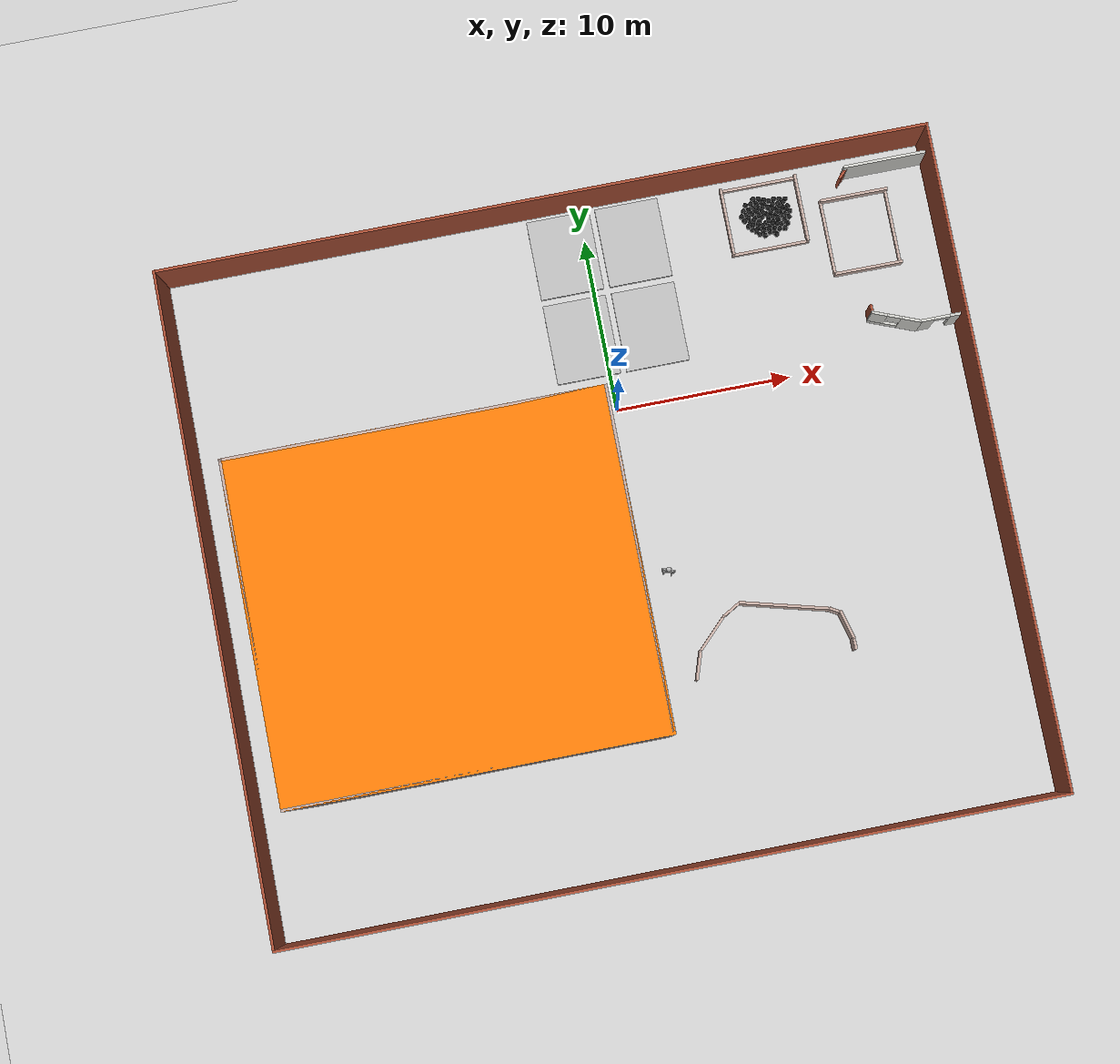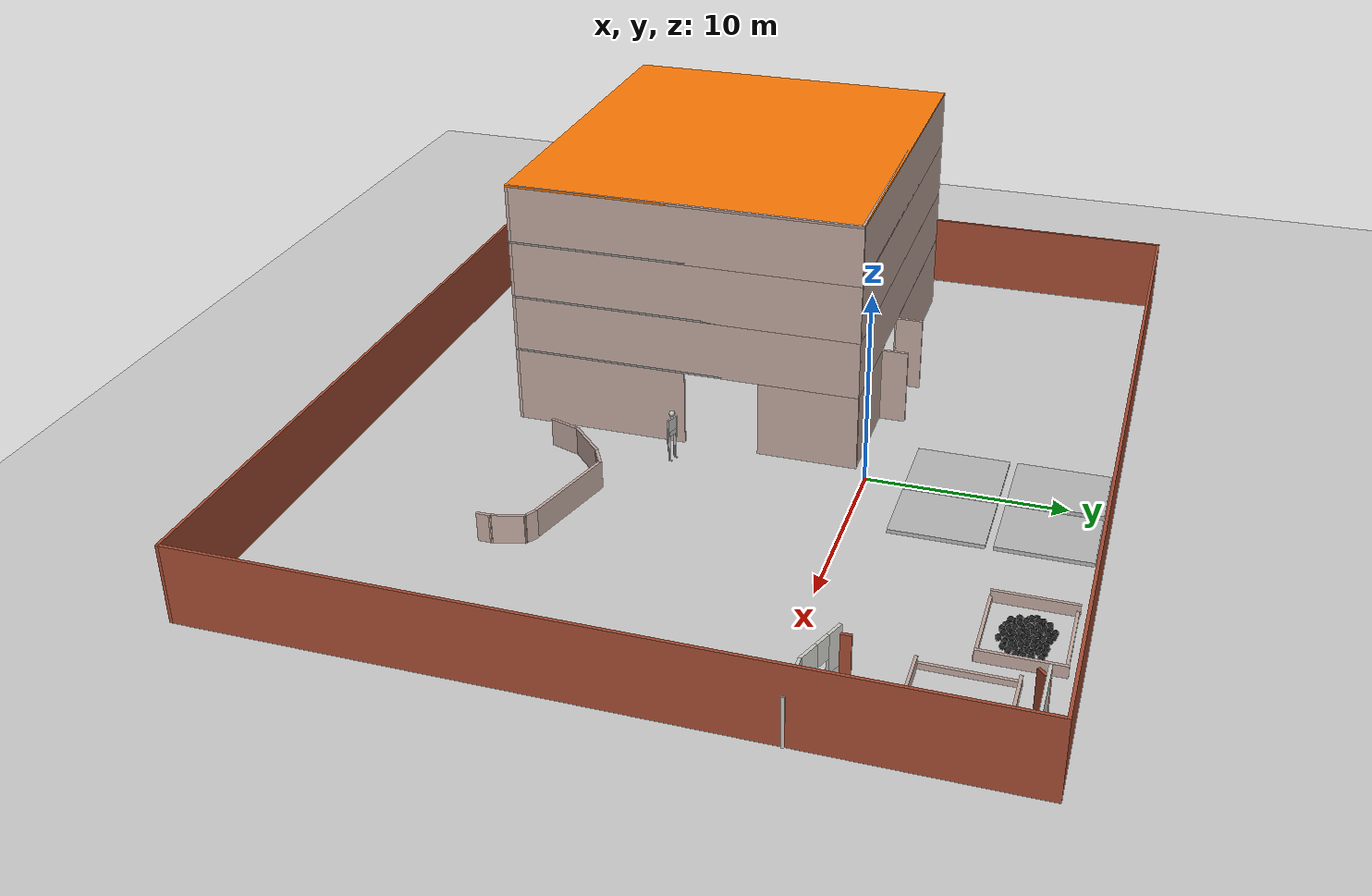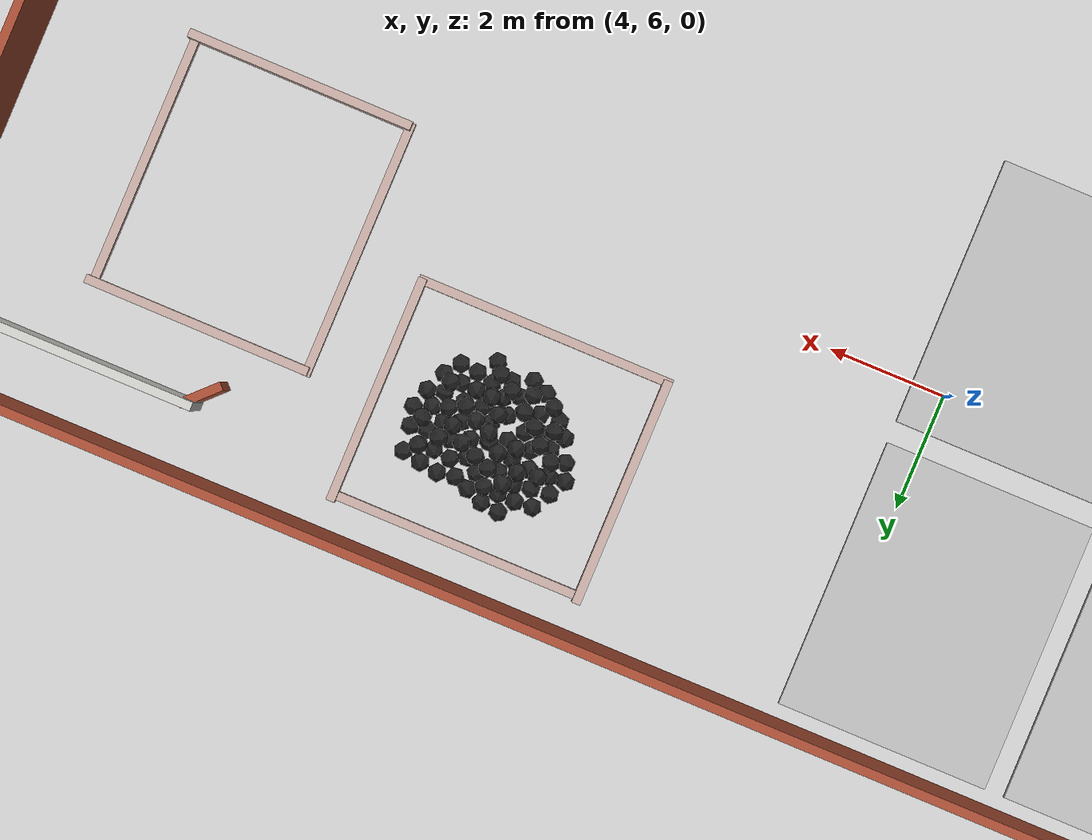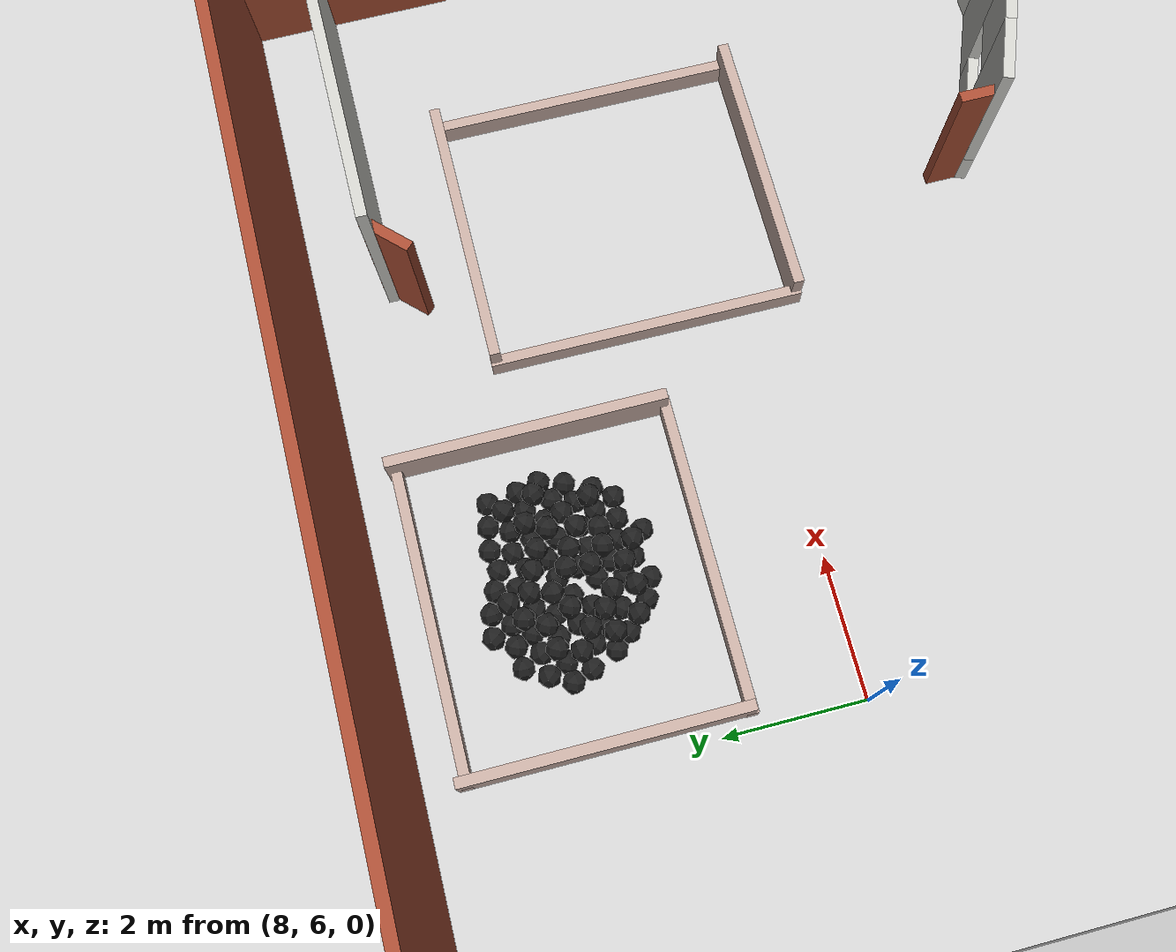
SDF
<sdf version="1.7">
 <world name="default">
  <light name="sun" type="directional">
   <pose>0 0 10 0 -0 0</pose>
   <diffuse>0.8 0.8 0.8 1</diffuse>
   <specular>0.2 0.2 0.2 1</specular>
   <attenuation>
    <range>1000</range>
    <constant>0.9</constant>
    <linear>0.01</linear>
    <quadratic>0.001</quadratic>
   </attenuation>
   <direction>-0.5 0.1 -0.9</direction>
   <spot><inner_angle>0</inner_angle><outer_angle>0</outer_angle><falloff>0</falloff></spot>
  </light>
  <model name="ground_plane">
   <static>1</static>
   <link name="link">
    <collision name="collision">
     <geometry><plane><normal>0 0 1</normal><size>100 100</size></plane></geometry>
     <surface><friction><ode><mu>100</mu><mu2>50</mu2></ode></friction></surface>
    </collision>
    <visual name="visual">
     <cast_shadows>0</cast_shadows>
     <geometry><plane><normal>0 0 1</normal><size>100 100</size></plane></geometry>
     <material>
      <script><uri>file://media/materials/scripts/gazebo.material</uri><name>Gazebo/Grey</name></script>
     </material>
    </visual>
   </link>
  </model>
  <gravity>0 0 -9.8</gravity>
  <magnetic_field>6e-06 2.3e-05 -4.2e-05</magnetic_field>
  <atmosphere type="adiabatic"/>
  <physics name="default_physics" default="0" type="ode">
   <max_step_size>0.001</max_step_size>
   <real_time_factor>1</real_time_factor>
   <real_time_update_rate>1000</real_time_update_rate>
  </physics>
  <scene><ambient>0.4 0.4 0.4 1</ambient><background>0.7 0.7 0.7 1</background><shadows>1</shadows></scene>
  <audio><device>default</device></audio>
  <spherical_coordinates>
   <surface_model>EARTH_WGS84</surface_model>
   <latitude_deg>0</latitude_deg>
   <longitude_deg>0</longitude_deg>
   <elevation>0</elevation>
   <heading_deg>0</heading_deg>
  </spherical_coordinates>
  <model name="wall11">
   <pose>-2 -7 0 0 -0 0</pose>
   <link name="Wall_0">
    <collision name="Wall_0_Collision">
     <geometry><box><size>44.15 0.15 4</size></box></geometry>
     <pose>0 0 2 0 -0 0</pose>
    </collision>
    <visual name="Wall_0_Visual">
     <pose>0 0 2 0 -0 0</pose>
     <geometry><box><size>44.15 0.15 4</size></box></geometry>
     <material>
      <script><uri>file://media/materials/scripts/gazebo.material</uri><name>Gazebo/Bricks</name></script>
      <ambient>1 1 1 1</ambient>
     </material>
     <meta><layer>0</layer></meta>
    </visual>
    <pose>0 19 0 0 -0 0</pose>
   </link>
   <link name="Wall_2">
    <collision name="Wall_2_Collision">
     <geometry><box><size>38.15 0.15 4</size></box></geometry>
     <pose>0 0 2 0 -0 0</pose>
    </collision>
    <visual name="Wall_2_Visual">
     <pose>0 0 2 0 -0 0</pose>
     <geometry><box><size>38.15 0.15 4</size></box></geometry>
     <material>
      <script><uri>file://media/materials/scripts/gazebo.material</uri><name>Gazebo/Bricks</name></script>
      <ambient>1 1 1 1</ambient>
     </material>
     <meta><layer>0</layer></meta>
    </visual>
    <pose>22 0 0 0 -0 -1.5708</pose>
   </link>
   <link name="Wall_4">
    <collision name="Wall_4_Collision">
     <geometry><box><size>44.15 0.15 4</size></box></geometry>
     <pose>0 0 2 0 -0 0</pose>
    </collision>
    <visual name="Wall_4_Visual">
     <pose>0 0 2 0 -0 0</pose>
     <geometry><box><size>44.15 0.15 4</size></box></geometry>
     <material>
      <script><uri>file://media/materials/scripts/gazebo.material</uri><name>Gazebo/Bricks</name></script>
      <ambient>1 1 1 1</ambient>
     </material>
     <meta><layer>0</layer></meta>
    </visual>
    <pose>0 -19 0 0 -0 3.14159</pose>
   </link>
   <link name="Wall_6">
    <collision name="Wall_6_Collision">
     <geometry><box><size>38.15 0.15 4</size></box></geometry>
     <pose>0 0 2 0 -0 0</pose>
    </collision>
    <visual name="Wall_6_Visual">
     <pose>0 0 2 0 -0 0</pose>
     <geometry><box><size>38.15 0.15 4</size></box></geometry>
     <material>
      <script><uri>file://media/materials/scripts/gazebo.material</uri><name>Gazebo/Bricks</name></script>
      <ambient>1 1 1 1</ambient>
     </material>
     <meta><layer>0</layer></meta>
    </visual>
    <pose>-22 0 0 0 -0 1.5708</pose>
   </link>
   <static>1</static>
  </model>
  <model name="wall1">
   <pose>6.97273 -12.8415 0 0 0 -0.014727</pose>
   <link name="Wall_0">
    <collision name="Wall_0_Collision">
     <geometry><box><size>5.09773 0.15 1.5</size></box></geometry>
     <pose>0 0 0.75 0 -0 0</pose>
    </collision>
    <visual name="Wall_0_Visual">
     <pose>0 0 0.75 0 -0 0</pose>
     <geometry><box><size>5.09773 0.15 1.5</size></box></geometry>
     <material>
      <script><uri>file://media/materials/scripts/gazebo.material</uri><name>Gazebo/Grey</name></script>
      <ambient>0.760784 0.662745 0.627451 1</ambient>
     </material>
     <meta><layer>0</layer></meta>
    </visual>
    <pose>0 0 0 0 -0 -0.244979</pose>
   </link>
   <static>1</static>
  </model>
  <model name="haoduomiantiaa_0">
   <link name="link_0">
    <inertial>
     <mass>0.2</mass>
     <inertia>
      <ixx>0.166667</ixx>
      <ixy>0</ixy>
      <ixz>0</ixz>
      <iyy>0.166667</iyy>
      <iyz>0</iyz>
      <izz>0.166667</izz>
     </inertia>
    </inertial>
    <visual name="visual">
     <geometry>
      <mesh>
       <uri>/home/lihaoyang/catkin_ws/src/pudong_gazebo/world/stl/haoduomianti.stl</uri>
       <scale>1 1 1</scale>
      </mesh>
     </geometry>
     <material>
      <lighting>1</lighting>
      <script><uri>file://media/materials/scripts/gazebo.material</uri><name>Gazebo/Black</name></script>
      <shader type="pixel"><normal_map>__default__</normal_map></shader>
      <ambient>0.3 0.3 0.3 1</ambient>
      <diffuse>0.7 0.7 0.7 1</diffuse>
      <specular>0.01 0.01 0.01 1</specular>
      <emissive>0 0 0 1</emissive>
     </material>
    </visual>
    <collision name="collision">
     <geometry>
      <mesh>
       <uri>/home/lihaoyang/catkin_ws/src/pudong_gazebo/world/stl/haoduomianti.stl</uri>
       <scale>1 1 1</scale>
      </mesh>
     </geometry>
     <surface>
      <friction>
       <ode><mu>1</mu><mu2>1</mu2><fdir1>0 0 0</fdir1><slip1>0</slip1><slip2>0</slip2></ode>
       <torsional>
        <coefficient>1</coefficient>
        <patch_radius>0</patch_radius>
        <surface_radius>0</surface_radius>
        <use_patch_radius>1</use_patch_radius>
        <ode><slip>0</slip></ode>
       </torsional>
      </friction>
      <bounce><restitution_coefficient>0</restitution_coefficient><threshold>1e+06</threshold></bounce>
      <contact>
       <collide_without_contact>0</collide_without_contact>
       <collide_without_contact_bitmask>1</collide_without_contact_bitmask>
       <collide_bitmask>1</collide_bitmask>
       <ode>
        <soft_cfm>0</soft_cfm>
        <soft_erp>0.2</soft_erp>
        <kp>1e+13</kp>
        <kd>1</kd>
        <max_vel>0.01</max_vel>
        <min_depth>0</min_depth>
       </ode>
       <bullet>
        <split_impulse>1</split_impulse>
        <split_impulse_penetration_threshold>-0.01</split_impulse_penetration_threshold>
        <soft_cfm>0</soft_cfm>
        <soft_erp>0.2</soft_erp>
        <kp>1e+13</kp>
        <kd>1</kd>
       </bullet>
      </contact>
     </surface>
    </collision>
   </link>
   <static>0</static>
   <pose>10.9075 9.06867 -0.115591 0.785364 -0.615479 -1.00385</pose>
  </model>
  <model name="haoduomiantiaa_1">
   <link name="link_0">
    <inertial>
     <mass>0.2</mass>
     <inertia>
      <ixx>0.166667</ixx>
      <ixy>0</ixy>
      <ixz>0</ixz>
      <iyy>0.166667</iyy>
      <iyz>0</iyz>
      <izz>0.166667</izz>
     </inertia>
    </inertial>
    <visual name="visual">
     <geometry>
      <mesh>
       <uri>/home/lihaoyang/catkin_ws/src/pudong_gazebo/world/stl/haoduomianti.stl</uri>
       <scale>1 1 1</scale>
      </mesh>
     </geometry>
     <material>
      <lighting>1</lighting>
      <script><uri>file://media/materials/scripts/gazebo.material</uri><name>Gazebo/Black</name></script>
      <shader type="pixel"><normal_map>__default__</normal_map></shader>
      <ambient>0.3 0.3 0.3 1</ambient>
      <diffuse>0.7 0.7 0.7 1</diffuse>
      <specular>0.01 0.01 0.01 1</specular>
      <emissive>0 0 0 1</emissive>
     </material>
    </visual>
    <collision name="collision">
     <geometry>
      <mesh>
       <uri>/home/lihaoyang/catkin_ws/src/pudong_gazebo/world/stl/haoduomianti.stl</uri>
       <scale>1 1 1</scale>
      </mesh>
     </geometry>
     <surface>
      <friction>
       <ode><mu>1</mu><mu2>1</mu2><fdir1>0 0 0</fdir1><slip1>0</slip1><slip2>0</slip2></ode>
       <torsional>
        <coefficient>1</coefficient>
        <patch_radius>0</patch_radius>
        <surface_radius>0</surface_radius>
        <use_patch_radius>1</use_patch_radius>
        <ode><slip>0</slip></ode>
       </torsional>
      </friction>
      <bounce><restitution_coefficient>0</restitution_coefficient><threshold>1e+06</threshold></bounce>
      <contact>
       <collide_without_contact>0</collide_without_contact>
       <collide_without_contact_bitmask>1</collide_without_contact_bitmask>
       <collide_bitmask>1</collide_bitmask>
       <ode>
        <soft_cfm>0</soft_cfm>
        <soft_erp>0.2</soft_erp>
        <kp>1e+13</kp>
        <kd>1</kd>
        <max_vel>0.01</max_vel>
        <min_depth>0</min_depth>
       </ode>
       <bullet>
        <split_impulse>1</split_impulse>
        <split_impulse_penetration_threshold>-0.01</split_impulse_penetration_threshold>
        <soft_cfm>0</soft_cfm>
        <soft_erp>0.2</soft_erp>
        <kp>1e+13</kp>
        <kd>1</kd>
       </bullet>
      </contact>
     </surface>
    </collision>
   </link>
   <static>0</static>
   <pose>10.0034 9.05786 0.103944 0.788247 -0.6195 0.880042</pose>
  </model>
  <model name="haoduomiantiaa_2">
   <link name="link_0">
    <inertial>
     <mass>0.2</mass>
     <inertia>
      <ixx>0.166667</ixx>
      <ixy>0</ixy>
      <ixz>0</ixz>
      <iyy>0.166667</iyy>
      <iyz>0</iyz>
      <izz>0.166667</izz>
     </inertia>
    </inertial>
    <visual name="visual">
     <geometry>
      <mesh>
       <uri>/home/lihaoyang/catkin_ws/src/pudong_gazebo/world/stl/haoduomianti.stl</uri>
       <scale>1 1 1</scale>
      </mesh>
     </geometry>
     <material>
      <lighting>1</lighting>
      <script><uri>file://media/materials/scripts/gazebo.material</uri><name>Gazebo/Black</name></script>
      <shader type="pixel"><normal_map>__default__</normal_map></shader>
      <ambient>0.3 0.3 0.3 1</ambient>
      <diffuse>0.7 0.7 0.7 1</diffuse>
      <specular>0.01 0.01 0.01 1</specular>
      <emissive>0 0 0 1</emissive>
     </material>
    </visual>
    <collision name="collision">
     <geometry>
      <mesh>
       <uri>/home/lihaoyang/catkin_ws/src/pudong_gazebo/world/stl/haoduomianti.stl</uri>
       <scale>1 1 1</scale>
      </mesh>
     </geometry>
     <surface>
      <friction>
       <ode><mu>1</mu><mu2>1</mu2><fdir1>0 0 0</fdir1><slip1>0</slip1><slip2>0</slip2></ode>
       <torsional>
        <coefficient>1</coefficient>
        <patch_radius>0</patch_radius>
        <surface_radius>0</surface_radius>
        <use_patch_radius>1</use_patch_radius>
        <ode><slip>0</slip></ode>
       </torsional>
      </friction>
      <bounce><restitution_coefficient>0</restitution_coefficient><threshold>1e+06</threshold></bounce>
      <contact>
       <collide_without_contact>0</collide_without_contact>
       <collide_without_contact_bitmask>1</collide_without_contact_bitmask>
       <collide_bitmask>1</collide_bitmask>
       <ode>
        <soft_cfm>0</soft_cfm>
        <soft_erp>0.2</soft_erp>
        <kp>1e+13</kp>
        <kd>1</kd>
        <max_vel>0.01</max_vel>
        <min_depth>0</min_depth>
       </ode>
       <bullet>
        <split_impulse>1</split_impulse>
        <split_impulse_penetration_threshold>-0.01</split_impulse_penetration_threshold>
        <soft_cfm>0</soft_cfm>
        <soft_erp>0.2</soft_erp>
        <kp>1e+13</kp>
        <kd>1</kd>
       </bullet>
      </contact>
     </surface>
    </collision>
   </link>
   <static>0</static>
   <pose>11.5784 9.08907 -0.115479 0.785418 -0.615485 0.70657</pose>
  </model>
  <model name="haoduomiantiaa_3">
   <link name="link_0">
    <inertial>
     <mass>0.2</mass>
     <inertia>
      <ixx>0.166667</ixx>
      <ixy>0</ixy>
      <ixz>0</ixz>
      <iyy>0.166667</iyy>
      <iyz>0</iyz>
      <izz>0.166667</izz>
     </inertia>
    </inertial>
    <visual name="visual">
     <geometry>
      <mesh>
       <uri>/home/lihaoyang/catkin_ws/src/pudong_gazebo/world/stl/haoduomianti.stl</uri>
       <scale>1 1 1</scale>
      </mesh>
     </geometry>
     <material>
      <lighting>1</lighting>
      <script><uri>file://media/materials/scripts/gazebo.material</uri><name>Gazebo/Black</name></script>
      <shader type="pixel"><normal_map>__default__</normal_map></shader>
      <ambient>0.3 0.3 0.3 1</ambient>
      <diffuse>0.7 0.7 0.7 1</diffuse>
      <specular>0.01 0.01 0.01 1</specular>
      <emissive>0 0 0 1</emissive>
     </material>
    </visual>
    <collision name="collision">
     <geometry>
      <mesh>
       <uri>/home/lihaoyang/catkin_ws/src/pudong_gazebo/world/stl/haoduomianti.stl</uri>
       <scale>1 1 1</scale>
      </mesh>
     </geometry>
     <surface>
      <friction>
       <ode><mu>1</mu><mu2>1</mu2><fdir1>0 0 0</fdir1><slip1>0</slip1><slip2>0</slip2></ode>
       <torsional>
        <coefficient>1</coefficient>
        <patch_radius>0</patch_radius>
        <surface_radius>0</surface_radius>
        <use_patch_radius>1</use_patch_radius>
        <ode><slip>0</slip></ode>
       </torsional>
      </friction>
      <bounce><restitution_coefficient>0</restitution_coefficient><threshold>1e+06</threshold></bounce>
      <contact>
       <collide_without_contact>0</collide_without_contact>
       <collide_without_contact_bitmask>1</collide_without_contact_bitmask>
       <collide_bitmask>1</collide_bitmask>
       <ode>
        <soft_cfm>0</soft_cfm>
        <soft_erp>0.2</soft_erp>
        <kp>1e+13</kp>
        <kd>1</kd>
        <max_vel>0.01</max_vel>
        <min_depth>0</min_depth>
       </ode>
       <bullet>
        <split_impulse>1</split_impulse>
        <split_impulse_penetration_threshold>-0.01</split_impulse_penetration_threshold>
        <soft_cfm>0</soft_cfm>
        <soft_erp>0.2</soft_erp>
        <kp>1e+13</kp>
        <kd>1</kd>
       </bullet>
      </contact>
     </surface>
    </collision>
   </link>
   <static>0</static>
   <pose>10.9655 8.29821 -0.115467 0.785455 -0.615501 -1.08818</pose>
  </model>
  <model name="haoduomiantiaa_5">
   <link name="link_0">
    <inertial>
     <mass>0.2</mass>
     <inertia>
      <ixx>0.166667</ixx>
      <ixy>0</ixy>
      <ixz>0</ixz>
      <iyy>0.166667</iyy>
      <iyz>0</iyz>
      <izz>0.166667</izz>
     </inertia>
    </inertial>
    <visual name="visual">
     <geometry>
      <mesh>
       <uri>/home/lihaoyang/catkin_ws/src/pudong_gazebo/world/stl/haoduomianti.stl</uri>
       <scale>1 1 1</scale>
      </mesh>
     </geometry>
     <material>
      <lighting>1</lighting>
      <script><uri>file://media/materials/scripts/gazebo.material</uri><name>Gazebo/Black</name></script>
      <shader type="pixel"><normal_map>__default__</normal_map></shader>
      <ambient>0.3 0.3 0.3 1</ambient>
      <diffuse>0.7 0.7 0.7 1</diffuse>
      <specular>0.01 0.01 0.01 1</specular>
      <emissive>0 0 0 1</emissive>
     </material>
    </visual>
    <collision name="collision">
     <geometry>
      <mesh>
       <uri>/home/lihaoyang/catkin_ws/src/pudong_gazebo/world/stl/haoduomianti.stl</uri>
       <scale>1 1 1</scale>
      </mesh>
     </geometry>
     <surface>
      <friction>
       <ode><mu>1</mu><mu2>1</mu2><fdir1>0 0 0</fdir1><slip1>0</slip1><slip2>0</slip2></ode>
       <torsional>
        <coefficient>1</coefficient>
        <patch_radius>0</patch_radius>
        <surface_radius>0</surface_radius>
        <use_patch_radius>1</use_patch_radius>
        <ode><slip>0</slip></ode>
       </torsional>
      </friction>
      <bounce><restitution_coefficient>0</restitution_coefficient><threshold>1e+06</threshold></bounce>
      <contact>
       <collide_without_contact>0</collide_without_contact>
       <collide_without_contact_bitmask>1</collide_without_contact_bitmask>
       <collide_bitmask>1</collide_bitmask>
       <ode>
        <soft_cfm>0</soft_cfm>
        <soft_erp>0.2</soft_erp>
        <kp>1e+13</kp>
        <kd>1</kd>
        <max_vel>0.01</max_vel>
        <min_depth>0</min_depth>
       </ode>
       <bullet>
        <split_impulse>1</split_impulse>
        <split_impulse_penetration_threshold>-0.01</split_impulse_penetration_threshold>
        <soft_cfm>0</soft_cfm>
        <soft_erp>0.2</soft_erp>
        <kp>1e+13</kp>
        <kd>1</kd>
       </bullet>
      </contact>
     </surface>
    </collision>
   </link>
   <static>0</static>
   <pose>11.5484 8.92081 0.116917 0.686953 -0.610599 -2.93693</pose>
  </model>
  <model name="haoduomiantiaa_6">
   <link name="link_0">
    <inertial>
     <mass>0.2</mass>
     <inertia>
      <ixx>0.166667</ixx>
      <ixy>0</ixy>
      <ixz>0</ixz>
      <iyy>0.166667</iyy>
      <iyz>0</iyz>
      <izz>0.166667</izz>
     </inertia>
    </inertial>
    <visual name="visual">
     <geometry>
      <mesh>
       <uri>/home/lihaoyang/catkin_ws/src/pudong_gazebo/world/stl/haoduomianti.stl</uri>
       <scale>1 1 1</scale>
      </mesh>
     </geometry>
     <material>
      <lighting>1</lighting>
      <script><uri>file://media/materials/scripts/gazebo.material</uri><name>Gazebo/Black</name></script>
      <shader type="pixel"><normal_map>__default__</normal_map></shader>
      <ambient>0.3 0.3 0.3 1</ambient>
      <diffuse>0.7 0.7 0.7 1</diffuse>
      <specular>0.01 0.01 0.01 1</specular>
      <emissive>0 0 0 1</emissive>
     </material>
    </visual>
    <collision name="collision">
     <geometry>
      <mesh>
       <uri>/home/lihaoyang/catkin_ws/src/pudong_gazebo/world/stl/haoduomianti.stl</uri>
       <scale>1 1 1</scale>
      </mesh>
     </geometry>
     <surface>
      <friction>
       <ode><mu>1</mu><mu2>1</mu2><fdir1>0 0 0</fdir1><slip1>0</slip1><slip2>0</slip2></ode>
       <torsional>
        <coefficient>1</coefficient>
        <patch_radius>0</patch_radius>
        <surface_radius>0</surface_radius>
        <use_patch_radius>1</use_patch_radius>
        <ode><slip>0</slip></ode>
       </torsional>
      </friction>
      <bounce><restitution_coefficient>0</restitution_coefficient><threshold>1e+06</threshold></bounce>
      <contact>
       <collide_without_contact>0</collide_without_contact>
       <collide_without_contact_bitmask>1</collide_without_contact_bitmask>
       <collide_bitmask>1</collide_bitmask>
       <ode>
        <soft_cfm>0</soft_cfm>
        <soft_erp>0.2</soft_erp>
        <kp>1e+13</kp>
        <kd>1</kd>
        <max_vel>0.01</max_vel>
        <min_depth>0</min_depth>
       </ode>
       <bullet>
        <split_impulse>1</split_impulse>
        <split_impulse_penetration_threshold>-0.01</split_impulse_penetration_threshold>
        <soft_cfm>0</soft_cfm>
        <soft_erp>0.2</soft_erp>
        <kp>1e+13</kp>
        <kd>1</kd>
       </bullet>
      </contact>
     </surface>
    </collision>
   </link>
   <static>0</static>
   <pose>10.6652 8.82141 -0.115469 0.785407 -0.615474 -0.216678</pose>
  </model>
  <model name="haoduomiantiaa_7">
   <link name="link_0">
    <inertial>
     <mass>0.2</mass>
     <inertia>
      <ixx>0.166667</ixx>
      <ixy>0</ixy>
      <ixz>0</ixz>
      <iyy>0.166667</iyy>
      <iyz>0</iyz>
      <izz>0.166667</izz>
     </inertia>
    </inertial>
    <visual name="visual">
     <geometry>
      <mesh>
       <uri>/home/lihaoyang/catkin_ws/src/pudong_gazebo/world/stl/haoduomianti.stl</uri>
       <scale>1 1 1</scale>
      </mesh>
     </geometry>
     <material>
      <lighting>1</lighting>
      <script><uri>file://media/materials/scripts/gazebo.material</uri><name>Gazebo/Black</name></script>
      <shader type="pixel"><normal_map>__default__</normal_map></shader>
      <ambient>0.3 0.3 0.3 1</ambient>
      <diffuse>0.7 0.7 0.7 1</diffuse>
      <specular>0.01 0.01 0.01 1</specular>
      <emissive>0 0 0 1</emissive>
     </material>
    </visual>
    <collision name="collision">
     <geometry>
      <mesh>
       <uri>/home/lihaoyang/catkin_ws/src/pudong_gazebo/world/stl/haoduomianti.stl</uri>
       <scale>1 1 1</scale>
      </mesh>
     </geometry>
     <surface>
      <friction>
       <ode><mu>1</mu><mu2>1</mu2><fdir1>0 0 0</fdir1><slip1>0</slip1><slip2>0</slip2></ode>
       <torsional>
        <coefficient>1</coefficient>
        <patch_radius>0</patch_radius>
        <surface_radius>0</surface_radius>
        <use_patch_radius>1</use_patch_radius>
        <ode><slip>0</slip></ode>
       </torsional>
      </friction>
      <bounce><restitution_coefficient>0</restitution_coefficient><threshold>1e+06</threshold></bounce>
      <contact>
       <collide_without_contact>0</collide_without_contact>
       <collide_without_contact_bitmask>1</collide_without_contact_bitmask>
       <collide_bitmask>1</collide_bitmask>
       <ode>
        <soft_cfm>0</soft_cfm>
        <soft_erp>0.2</soft_erp>
        <kp>1e+13</kp>
        <kd>1</kd>
        <max_vel>0.01</max_vel>
        <min_depth>0</min_depth>
       </ode>
       <bullet>
        <split_impulse>1</split_impulse>
        <split_impulse_penetration_threshold>-0.01</split_impulse_penetration_threshold>
        <soft_cfm>0</soft_cfm>
        <soft_erp>0.2</soft_erp>
        <kp>1e+13</kp>
        <kd>1</kd>
       </bullet>
      </contact>
     </surface>
    </collision>
   </link>
   <static>0</static>
   <pose>10.9183 8.67319 -0.115516 0.785399 -0.615423 -1.12919</pose>
  </model>
  <model name="haoduomiantiaa_8">
   <link name="link_0">
    <inertial>
     <mass>0.2</mass>
     <inertia>
      <ixx>0.166667</ixx>
      <ixy>0</ixy>
      <ixz>0</ixz>
      <iyy>0.166667</iyy>
      <iyz>0</iyz>
      <izz>0.166667</izz>
     </inertia>
    </inertial>
    <visual name="visual">
     <geometry>
      <mesh>
       <uri>/home/lihaoyang/catkin_ws/src/pudong_gazebo/world/stl/haoduomianti.stl</uri>
       <scale>1 1 1</scale>
      </mesh>
     </geometry>
     <material>
      <lighting>1</lighting>
      <script><uri>file://media/materials/scripts/gazebo.material</uri><name>Gazebo/Black</name></script>
      <shader type="pixel"><normal_map>__default__</normal_map></shader>
      <ambient>0.3 0.3 0.3 1</ambient>
      <diffuse>0.7 0.7 0.7 1</diffuse>
      <specular>0.01 0.01 0.01 1</specular>
      <emissive>0 0 0 1</emissive>
     </material>
    </visual>
    <collision name="collision">
     <geometry>
      <mesh>
       <uri>/home/lihaoyang/catkin_ws/src/pudong_gazebo/world/stl/haoduomianti.stl</uri>
       <scale>1 1 1</scale>
      </mesh>
     </geometry>
     <surface>
      <friction>
       <ode><mu>1</mu><mu2>1</mu2><fdir1>0 0 0</fdir1><slip1>0</slip1><slip2>0</slip2></ode>
       <torsional>
        <coefficient>1</coefficient>
        <patch_radius>0</patch_radius>
        <surface_radius>0</surface_radius>
        <use_patch_radius>1</use_patch_radius>
        <ode><slip>0</slip></ode>
       </torsional>
      </friction>
      <bounce><restitution_coefficient>0</restitution_coefficient><threshold>1e+06</threshold></bounce>
      <contact>
       <collide_without_contact>0</collide_without_contact>
       <collide_without_contact_bitmask>1</collide_without_contact_bitmask>
       <collide_bitmask>1</collide_bitmask>
       <ode>
        <soft_cfm>0</soft_cfm>
        <soft_erp>0.2</soft_erp>
        <kp>1e+13</kp>
        <kd>1</kd>
        <max_vel>0.01</max_vel>
        <min_depth>0</min_depth>
       </ode>
       <bullet>
        <split_impulse>1</split_impulse>
        <split_impulse_penetration_threshold>-0.01</split_impulse_penetration_threshold>
        <soft_cfm>0</soft_cfm>
        <soft_erp>0.2</soft_erp>
        <kp>1e+13</kp>
        <kd>1</kd>
       </bullet>
      </contact>
     </surface>
    </collision>
   </link>
   <static>0</static>
   <pose>10.5608 8.64737 0.118805 0.795752 -0.627102 3.07288</pose>
  </model>
  <model name="haoduomiantiaa_11">
   <link name="link_0">
    <inertial>
     <mass>0.2</mass>
     <inertia>
      <ixx>0.166667</ixx>
      <ixy>0</ixy>
      <ixz>0</ixz>
      <iyy>0.166667</iyy>
      <iyz>0</iyz>
      <izz>0.166667</izz>
     </inertia>
    </inertial>
    <visual name="visual">
     <geometry>
      <mesh>
       <uri>/home/lihaoyang/catkin_ws/src/pudong_gazebo/world/stl/haoduomianti.stl</uri>
       <scale>1 1 1</scale>
      </mesh>
     </geometry>
     <material>
      <lighting>1</lighting>
      <script><uri>file://media/materials/scripts/gazebo.material</uri><name>Gazebo/Black</name></script>
      <shader type="pixel"><normal_map>__default__</normal_map></shader>
      <ambient>0.3 0.3 0.3 1</ambient>
      <diffuse>0.7 0.7 0.7 1</diffuse>
      <specular>0.01 0.01 0.01 1</specular>
      <emissive>0 0 0 1</emissive>
     </material>
    </visual>
    <collision name="collision">
     <geometry>
      <mesh>
       <uri>/home/lihaoyang/catkin_ws/src/pudong_gazebo/world/stl/haoduomianti.stl</uri>
       <scale>1 1 1</scale>
      </mesh>
     </geometry>
     <surface>
      <friction>
       <ode><mu>1</mu><mu2>1</mu2><fdir1>0 0 0</fdir1><slip1>0</slip1><slip2>0</slip2></ode>
       <torsional>
        <coefficient>1</coefficient>
        <patch_radius>0</patch_radius>
        <surface_radius>0</surface_radius>
        <use_patch_radius>1</use_patch_radius>
        <ode><slip>0</slip></ode>
       </torsional>
      </friction>
      <bounce><restitution_coefficient>0</restitution_coefficient><threshold>1e+06</threshold></bounce>
      <contact>
       <collide_without_contact>0</collide_without_contact>
       <collide_without_contact_bitmask>1</collide_without_contact_bitmask>
       <collide_bitmask>1</collide_bitmask>
       <ode>
        <soft_cfm>0</soft_cfm>
        <soft_erp>0.2</soft_erp>
        <kp>1e+13</kp>
        <kd>1</kd>
        <max_vel>0.01</max_vel>
        <min_depth>0</min_depth>
       </ode>
       <bullet>
        <split_impulse>1</split_impulse>
        <split_impulse_penetration_threshold>-0.01</split_impulse_penetration_threshold>
        <soft_cfm>0</soft_cfm>
        <soft_erp>0.2</soft_erp>
        <kp>1e+13</kp>
        <kd>1</kd>
       </bullet>
      </contact>
     </surface>
    </collision>
   </link>
   <static>0</static>
   <pose>9.61211 9.29436 -0.1155 0.785394 -0.615481 -1.21931</pose>
  </model>
  <model name="haoduomiantiaa_13">
   <link name="link_0">
    <inertial>
     <mass>0.2</mass>
     <inertia>
      <ixx>0.166667</ixx>
      <ixy>0</ixy>
      <ixz>0</ixz>
      <iyy>0.166667</iyy>
      <iyz>0</iyz>
      <izz>0.166667</izz>
     </inertia>
    </inertial>
    <visual name="visual">
     <geometry>
      <mesh>
       <uri>/home/lihaoyang/catkin_ws/src/pudong_gazebo/world/stl/haoduomianti.stl</uri>
       <scale>1 1 1</scale>
      </mesh>
     </geometry>
     <material>
      <lighting>1</lighting>
      <script><uri>file://media/materials/scripts/gazebo.material</uri><name>Gazebo/Black</name></script>
      <shader type="pixel"><normal_map>__default__</normal_map></shader>
      <ambient>0.3 0.3 0.3 1</ambient>
      <diffuse>0.7 0.7 0.7 1</diffuse>
      <specular>0.01 0.01 0.01 1</specular>
      <emissive>0 0 0 1</emissive>
     </material>
    </visual>
    <collision name="collision">
     <geometry>
      <mesh>
       <uri>/home/lihaoyang/catkin_ws/src/pudong_gazebo/world/stl/haoduomianti.stl</uri>
       <scale>1 1 1</scale>
      </mesh>
     </geometry>
     <surface>
      <friction>
       <ode><mu>1</mu><mu2>1</mu2><fdir1>0 0 0</fdir1><slip1>0</slip1><slip2>0</slip2></ode>
       <torsional>
        <coefficient>1</coefficient>
        <patch_radius>0</patch_radius>
        <surface_radius>0</surface_radius>
        <use_patch_radius>1</use_patch_radius>
        <ode><slip>0</slip></ode>
       </torsional>
      </friction>
      <bounce><restitution_coefficient>0</restitution_coefficient><threshold>1e+06</threshold></bounce>
      <contact>
       <collide_without_contact>0</collide_without_contact>
       <collide_without_contact_bitmask>1</collide_without_contact_bitmask>
       <collide_bitmask>1</collide_bitmask>
       <ode>
        <soft_cfm>0</soft_cfm>
        <soft_erp>0.2</soft_erp>
        <kp>1e+13</kp>
        <kd>1</kd>
        <max_vel>0.01</max_vel>
        <min_depth>0</min_depth>
       </ode>
       <bullet>
        <split_impulse>1</split_impulse>
        <split_impulse_penetration_threshold>-0.01</split_impulse_penetration_threshold>
        <soft_cfm>0</soft_cfm>
        <soft_erp>0.2</soft_erp>
        <kp>1e+13</kp>
        <kd>1</kd>
       </bullet>
      </contact>
     </surface>
    </collision>
   </link>
   <static>0</static>
   <pose>9.92416 9.44285 -0.115535 0.785401 -0.615476 2.97005</pose>
  </model>
  <model name="haoduomiantiaa_16">
   <link name="link_0">
    <inertial>
     <mass>0.2</mass>
     <inertia>
      <ixx>0.166667</ixx>
      <ixy>0</ixy>
      <ixz>0</ixz>
      <iyy>0.166667</iyy>
      <iyz>0</iyz>
      <izz>0.166667</izz>
     </inertia>
    </inertial>
    <visual name="visual">
     <geometry>
      <mesh>
       <uri>/home/lihaoyang/catkin_ws/src/pudong_gazebo/world/stl/haoduomianti.stl</uri>
       <scale>1 1 1</scale>
      </mesh>
     </geometry>
     <material>
      <lighting>1</lighting>
      <script><uri>file://media/materials/scripts/gazebo.material</uri><name>Gazebo/Black</name></script>
      <shader type="pixel"><normal_map>__default__</normal_map></shader>
      <ambient>0.3 0.3 0.3 1</ambient>
      <diffuse>0.7 0.7 0.7 1</diffuse>
      <specular>0.01 0.01 0.01 1</specular>
      <emissive>0 0 0 1</emissive>
     </material>
    </visual>
    <collision name="collision">
     <geometry>
      <mesh>
       <uri>/home/lihaoyang/catkin_ws/src/pudong_gazebo/world/stl/haoduomianti.stl</uri>
       <scale>1 1 1</scale>
      </mesh>
     </geometry>
     <surface>
      <friction>
       <ode><mu>1</mu><mu2>1</mu2><fdir1>0 0 0</fdir1><slip1>0</slip1><slip2>0</slip2></ode>
       <torsional>
        <coefficient>1</coefficient>
        <patch_radius>0</patch_radius>
        <surface_radius>0</surface_radius>
        <use_patch_radius>1</use_patch_radius>
        <ode><slip>0</slip></ode>
       </torsional>
      </friction>
      <bounce><restitution_coefficient>0</restitution_coefficient><threshold>1e+06</threshold></bounce>
      <contact>
       <collide_without_contact>0</collide_without_contact>
       <collide_without_contact_bitmask>1</collide_without_contact_bitmask>
       <collide_bitmask>1</collide_bitmask>
       <ode>
        <soft_cfm>0</soft_cfm>
        <soft_erp>0.2</soft_erp>
        <kp>1e+13</kp>
        <kd>1</kd>
        <max_vel>0.01</max_vel>
        <min_depth>0</min_depth>
       </ode>
       <bullet>
        <split_impulse>1</split_impulse>
        <split_impulse_penetration_threshold>-0.01</split_impulse_penetration_threshold>
        <soft_cfm>0</soft_cfm>
        <soft_erp>0.2</soft_erp>
        <kp>1e+13</kp>
        <kd>1</kd>
       </bullet>
      </contact>
     </surface>
    </collision>
   </link>
   <static>0</static>
   <pose>11.433 9.31202 0.061931 0.77388 -0.677487 1.11241</pose>
  </model>
  <model name="haoduomiantiaa_17">
   <link name="link_0">
    <inertial>
     <mass>0.2</mass>
     <inertia>
      <ixx>0.166667</ixx>
      <ixy>0</ixy>
      <ixz>0</ixz>
      <iyy>0.166667</iyy>
      <iyz>0</iyz>
      <izz>0.166667</izz>
     </inertia>
    </inertial>
    <visual name="visual">
     <geometry>
      <mesh>
       <uri>/home/lihaoyang/catkin_ws/src/pudong_gazebo/world/stl/haoduomianti.stl</uri>
       <scale>1 1 1</scale>
      </mesh>
     </geometry>
     <material>
      <lighting>1</lighting>
      <script><uri>file://media/materials/scripts/gazebo.material</uri><name>Gazebo/Black</name></script>
      <shader type="pixel"><normal_map>__default__</normal_map></shader>
      <ambient>0.3 0.3 0.3 1</ambient>
      <diffuse>0.7 0.7 0.7 1</diffuse>
      <specular>0.01 0.01 0.01 1</specular>
      <emissive>0 0 0 1</emissive>
     </material>
    </visual>
    <collision name="collision">
     <geometry>
      <mesh>
       <uri>/home/lihaoyang/catkin_ws/src/pudong_gazebo/world/stl/haoduomianti.stl</uri>
       <scale>1 1 1</scale>
      </mesh>
     </geometry>
     <surface>
      <friction>
       <ode><mu>1</mu><mu2>1</mu2><fdir1>0 0 0</fdir1><slip1>0</slip1><slip2>0</slip2></ode>
       <torsional>
        <coefficient>1</coefficient>
        <patch_radius>0</patch_radius>
        <surface_radius>0</surface_radius>
        <use_patch_radius>1</use_patch_radius>
        <ode><slip>0</slip></ode>
       </torsional>
      </friction>
      <bounce><restitution_coefficient>0</restitution_coefficient><threshold>1e+06</threshold></bounce>
      <contact>
       <collide_without_contact>0</collide_without_contact>
       <collide_without_contact_bitmask>1</collide_without_contact_bitmask>
       <collide_bitmask>1</collide_bitmask>
       <ode>
        <soft_cfm>0</soft_cfm>
        <soft_erp>0.2</soft_erp>
        <kp>1e+13</kp>
        <kd>1</kd>
        <max_vel>0.01</max_vel>
        <min_depth>0</min_depth>
       </ode>
       <bullet>
        <split_impulse>1</split_impulse>
        <split_impulse_penetration_threshold>-0.01</split_impulse_penetration_threshold>
        <soft_cfm>0</soft_cfm>
        <soft_erp>0.2</soft_erp>
        <kp>1e+13</kp>
        <kd>1</kd>
       </bullet>
      </contact>
     </surface>
    </collision>
   </link>
   <static>0</static>
   <pose>10.4162 9.61039 0.072056 0.474737 -0.776287 -0.110228</pose>
  </model>
  <model name="haoduomiantiaa_18">
   <link name="link_0">
    <inertial>
     <mass>0.2</mass>
     <inertia>
      <ixx>0.166667</ixx>
      <ixy>0</ixy>
      <ixz>0</ixz>
      <iyy>0.166667</iyy>
      <iyz>0</iyz>
      <izz>0.166667</izz>
     </inertia>
    </inertial>
    <visual name="visual">
     <geometry>
      <mesh>
       <uri>/home/lihaoyang/catkin_ws/src/pudong_gazebo/world/stl/haoduomianti.stl</uri>
       <scale>1 1 1</scale>
      </mesh>
     </geometry>
     <material>
      <lighting>1</lighting>
      <script><uri>file://media/materials/scripts/gazebo.material</uri><name>Gazebo/Black</name></script>
      <shader type="pixel"><normal_map>__default__</normal_map></shader>
      <ambient>0.3 0.3 0.3 1</ambient>
      <diffuse>0.7 0.7 0.7 1</diffuse>
      <specular>0.01 0.01 0.01 1</specular>
      <emissive>0 0 0 1</emissive>
     </material>
    </visual>
    <collision name="collision">
     <geometry>
      <mesh>
       <uri>/home/lihaoyang/catkin_ws/src/pudong_gazebo/world/stl/haoduomianti.stl</uri>
       <scale>1 1 1</scale>
      </mesh>
     </geometry>
     <surface>
      <friction>
       <ode><mu>1</mu><mu2>1</mu2><fdir1>0 0 0</fdir1><slip1>0</slip1><slip2>0</slip2></ode>
       <torsional>
        <coefficient>1</coefficient>
        <patch_radius>0</patch_radius>
        <surface_radius>0</surface_radius>
        <use_patch_radius>1</use_patch_radius>
        <ode><slip>0</slip></ode>
       </torsional>
      </friction>
      <bounce><restitution_coefficient>0</restitution_coefficient><threshold>1e+06</threshold></bounce>
      <contact>
       <collide_without_contact>0</collide_without_contact>
       <collide_without_contact_bitmask>1</collide_without_contact_bitmask>
       <collide_bitmask>1</collide_bitmask>
       <ode>
        <soft_cfm>0</soft_cfm>
        <soft_erp>0.2</soft_erp>
        <kp>1e+13</kp>
        <kd>1</kd>
        <max_vel>0.01</max_vel>
        <min_depth>0</min_depth>
       </ode>
       <bullet>
        <split_impulse>1</split_impulse>
        <split_impulse_penetration_threshold>-0.01</split_impulse_penetration_threshold>
        <soft_cfm>0</soft_cfm>
        <soft_erp>0.2</soft_erp>
        <kp>1e+13</kp>
        <kd>1</kd>
       </bullet>
      </contact>
     </surface>
    </collision>
   </link>
   <static>0</static>
   <pose>11.3788 9.80363 0.112676 0.805186 -0.555993 1.0651</pose>
  </model>
  <model name="haoduomiantiaa_20">
   <link name="link_0">
    <inertial>
     <mass>0.2</mass>
     <inertia>
      <ixx>0.166667</ixx>
      <ixy>0</ixy>
      <ixz>0</ixz>
      <iyy>0.166667</iyy>
      <iyz>0</iyz>
      <izz>0.166667</izz>
     </inertia>
    </inertial>
    <visual name="visual">
     <geometry>
      <mesh>
       <uri>/home/lihaoyang/catkin_ws/src/pudong_gazebo/world/stl/haoduomianti.stl</uri>
       <scale>1 1 1</scale>
      </mesh>
     </geometry>
     <material>
      <lighting>1</lighting>
      <script><uri>file://media/materials/scripts/gazebo.material</uri><name>Gazebo/Black</name></script>
      <shader type="pixel"><normal_map>__default__</normal_map></shader>
      <ambient>0.3 0.3 0.3 1</ambient>
      <diffuse>0.7 0.7 0.7 1</diffuse>
      <specular>0.01 0.01 0.01 1</specular>
      <emissive>0 0 0 1</emissive>
     </material>
    </visual>
    <collision name="collision">
     <geometry>
      <mesh>
       <uri>/home/lihaoyang/catkin_ws/src/pudong_gazebo/world/stl/haoduomianti.stl</uri>
       <scale>1 1 1</scale>
      </mesh>
     </geometry>
     <surface>
      <friction>
       <ode><mu>1</mu><mu2>1</mu2><fdir1>0 0 0</fdir1><slip1>0</slip1><slip2>0</slip2></ode>
       <torsional>
        <coefficient>1</coefficient>
        <patch_radius>0</patch_radius>
        <surface_radius>0</surface_radius>
        <use_patch_radius>1</use_patch_radius>
        <ode><slip>0</slip></ode>
       </torsional>
      </friction>
      <bounce><restitution_coefficient>0</restitution_coefficient><threshold>1e+06</threshold></bounce>
      <contact>
       <collide_without_contact>0</collide_without_contact>
       <collide_without_contact_bitmask>1</collide_without_contact_bitmask>
       <collide_bitmask>1</collide_bitmask>
       <ode>
        <soft_cfm>0</soft_cfm>
        <soft_erp>0.2</soft_erp>
        <kp>1e+13</kp>
        <kd>1</kd>
        <max_vel>0.01</max_vel>
        <min_depth>0</min_depth>
       </ode>
       <bullet>
        <split_impulse>1</split_impulse>
        <split_impulse_penetration_threshold>-0.01</split_impulse_penetration_threshold>
        <soft_cfm>0</soft_cfm>
        <soft_erp>0.2</soft_erp>
        <kp>1e+13</kp>
        <kd>1</kd>
       </bullet>
      </contact>
     </surface>
    </collision>
   </link>
   <static>0</static>
   <pose>11.6065 10.0135 0.030702 0.501601 -0.690657 -1.03502</pose>
  </model>
  <model name="haoduomiantiaa_21">
   <link name="link_0">
    <inertial>
     <mass>0.2</mass>
     <inertia>
      <ixx>0.166667</ixx>
      <ixy>0</ixy>
      <ixz>0</ixz>
      <iyy>0.166667</iyy>
      <iyz>0</iyz>
      <izz>0.166667</izz>
     </inertia>
    </inertial>
    <visual name="visual">
     <geometry>
      <mesh>
       <uri>/home/lihaoyang/catkin_ws/src/pudong_gazebo/world/stl/haoduomianti.stl</uri>
       <scale>1 1 1</scale>
      </mesh>
     </geometry>
     <material>
      <lighting>1</lighting>
      <script><uri>file://media/materials/scripts/gazebo.material</uri><name>Gazebo/Black</name></script>
      <shader type="pixel"><normal_map>__default__</normal_map></shader>
      <ambient>0.3 0.3 0.3 1</ambient>
      <diffuse>0.7 0.7 0.7 1</diffuse>
      <specular>0.01 0.01 0.01 1</specular>
      <emissive>0 0 0 1</emissive>
     </material>
    </visual>
    <collision name="collision">
     <geometry>
      <mesh>
       <uri>/home/lihaoyang/catkin_ws/src/pudong_gazebo/world/stl/haoduomianti.stl</uri>
       <scale>1 1 1</scale>
      </mesh>
     </geometry>
     <surface>
      <friction>
       <ode><mu>1</mu><mu2>1</mu2><fdir1>0 0 0</fdir1><slip1>0</slip1><slip2>0</slip2></ode>
       <torsional>
        <coefficient>1</coefficient>
        <patch_radius>0</patch_radius>
        <surface_radius>0</surface_radius>
        <use_patch_radius>1</use_patch_radius>
        <ode><slip>0</slip></ode>
       </torsional>
      </friction>
      <bounce><restitution_coefficient>0</restitution_coefficient><threshold>1e+06</threshold></bounce>
      <contact>
       <collide_without_contact>0</collide_without_contact>
       <collide_without_contact_bitmask>1</collide_without_contact_bitmask>
       <collide_bitmask>1</collide_bitmask>
       <ode>
        <soft_cfm>0</soft_cfm>
        <soft_erp>0.2</soft_erp>
        <kp>1e+13</kp>
        <kd>1</kd>
        <max_vel>0.01</max_vel>
        <min_depth>0</min_depth>
       </ode>
       <bullet>
        <split_impulse>1</split_impulse>
        <split_impulse_penetration_threshold>-0.01</split_impulse_penetration_threshold>
        <soft_cfm>0</soft_cfm>
        <soft_erp>0.2</soft_erp>
        <kp>1e+13</kp>
        <kd>1</kd>
       </bullet>
      </contact>
     </surface>
    </collision>
   </link>
   <static>0</static>
   <pose>10.9536 9.27498 0.075313 1.05219 -0.670837 -2.44192</pose>
  </model>
  <model name="haoduomiantiaa_22">
   <link name="link_0">
    <inertial>
     <mass>0.2</mass>
     <inertia>
      <ixx>0.166667</ixx>
      <ixy>0</ixy>
      <ixz>0</ixz>
      <iyy>0.166667</iyy>
      <iyz>0</iyz>
      <izz>0.166667</izz>
     </inertia>
    </inertial>
    <visual name="visual">
     <geometry>
      <mesh>
       <uri>/home/lihaoyang/catkin_ws/src/pudong_gazebo/world/stl/haoduomianti.stl</uri>
       <scale>1 1 1</scale>
      </mesh>
     </geometry>
     <material>
      <lighting>1</lighting>
      <script><uri>file://media/materials/scripts/gazebo.material</uri><name>Gazebo/Black</name></script>
      <shader type="pixel"><normal_map>__default__</normal_map></shader>
      <ambient>0.3 0.3 0.3 1</ambient>
      <diffuse>0.7 0.7 0.7 1</diffuse>
      <specular>0.01 0.01 0.01 1</specular>
      <emissive>0 0 0 1</emissive>
     </material>
    </visual>
    <collision name="collision">
     <geometry>
      <mesh>
       <uri>/home/lihaoyang/catkin_ws/src/pudong_gazebo/world/stl/haoduomianti.stl</uri>
       <scale>1 1 1</scale>
      </mesh>
     </geometry>
     <surface>
      <friction>
       <ode><mu>1</mu><mu2>1</mu2><fdir1>0 0 0</fdir1><slip1>0</slip1><slip2>0</slip2></ode>
       <torsional>
        <coefficient>1</coefficient>
        <patch_radius>0</patch_radius>
        <surface_radius>0</surface_radius>
        <use_patch_radius>1</use_patch_radius>
        <ode><slip>0</slip></ode>
       </torsional>
      </friction>
      <bounce><restitution_coefficient>0</restitution_coefficient><threshold>1e+06</threshold></bounce>
      <contact>
       <collide_without_contact>0</collide_without_contact>
       <collide_without_contact_bitmask>1</collide_without_contact_bitmask>
       <collide_bitmask>1</collide_bitmask>
       <ode>
        <soft_cfm>0</soft_cfm>
        <soft_erp>0.2</soft_erp>
        <kp>1e+13</kp>
        <kd>1</kd>
        <max_vel>0.01</max_vel>
        <min_depth>0</min_depth>
       </ode>
       <bullet>
        <split_impulse>1</split_impulse>
        <split_impulse_penetration_threshold>-0.01</split_impulse_penetration_threshold>
        <soft_cfm>0</soft_cfm>
        <soft_erp>0.2</soft_erp>
        <kp>1e+13</kp>
        <kd>1</kd>
       </bullet>
      </contact>
     </surface>
    </collision>
   </link>
   <static>0</static>
   <pose>11.7031 8.81136 -0.115456 0.785403 -0.614665 -0.840751</pose>
  </model>
  <model name="haoduomiantiaa_24">
   <link name="link_0">
    <inertial>
     <mass>0.2</mass>
     <inertia>
      <ixx>0.166667</ixx>
      <ixy>0</ixy>
      <ixz>0</ixz>
      <iyy>0.166667</iyy>
      <iyz>0</iyz>
      <izz>0.166667</izz>
     </inertia>
    </inertial>
    <visual name="visual">
     <geometry>
      <mesh>
       <uri>/home/lihaoyang/catkin_ws/src/pudong_gazebo/world/stl/haoduomianti.stl</uri>
       <scale>1 1 1</scale>
      </mesh>
     </geometry>
     <material>
      <lighting>1</lighting>
      <script><uri>file://media/materials/scripts/gazebo.material</uri><name>Gazebo/Black</name></script>
      <shader type="pixel"><normal_map>__default__</normal_map></shader>
      <ambient>0.3 0.3 0.3 1</ambient>
      <diffuse>0.7 0.7 0.7 1</diffuse>
      <specular>0.01 0.01 0.01 1</specular>
      <emissive>0 0 0 1</emissive>
     </material>
    </visual>
    <collision name="collision">
     <geometry>
      <mesh>
       <uri>/home/lihaoyang/catkin_ws/src/pudong_gazebo/world/stl/haoduomianti.stl</uri>
       <scale>1 1 1</scale>
      </mesh>
     </geometry>
     <surface>
      <friction>
       <ode><mu>1</mu><mu2>1</mu2><fdir1>0 0 0</fdir1><slip1>0</slip1><slip2>0</slip2></ode>
       <torsional>
        <coefficient>1</coefficient>
        <patch_radius>0</patch_radius>
        <surface_radius>0</surface_radius>
        <use_patch_radius>1</use_patch_radius>
        <ode><slip>0</slip></ode>
       </torsional>
      </friction>
      <bounce><restitution_coefficient>0</restitution_coefficient><threshold>1e+06</threshold></bounce>
      <contact>
       <collide_without_contact>0</collide_without_contact>
       <collide_without_contact_bitmask>1</collide_without_contact_bitmask>
       <collide_bitmask>1</collide_bitmask>
       <ode>
        <soft_cfm>0</soft_cfm>
        <soft_erp>0.2</soft_erp>
        <kp>1e+13</kp>
        <kd>1</kd>
        <max_vel>0.01</max_vel>
        <min_depth>0</min_depth>
       </ode>
       <bullet>
        <split_impulse>1</split_impulse>
        <split_impulse_penetration_threshold>-0.01</split_impulse_penetration_threshold>
        <soft_cfm>0</soft_cfm>
        <soft_erp>0.2</soft_erp>
        <kp>1e+13</kp>
        <kd>1</kd>
       </bullet>
      </contact>
     </surface>
    </collision>
   </link>
   <static>0</static>
   <pose>10.14 10.1175 0.115022 0.743912 -0.577734 1.88422</pose>
  </model>
  <model name="haoduomiantiaa_25">
   <link name="link_0">
    <inertial>
     <mass>0.2</mass>
     <inertia>
      <ixx>0.166667</ixx>
      <ixy>0</ixy>
      <ixz>0</ixz>
      <iyy>0.166667</iyy>
      <iyz>0</iyz>
      <izz>0.166667</izz>
     </inertia>
    </inertial>
    <visual name="visual">
     <geometry>
      <mesh>
       <uri>/home/lihaoyang/catkin_ws/src/pudong_gazebo/world/stl/haoduomianti.stl</uri>
       <scale>1 1 1</scale>
      </mesh>
     </geometry>
     <material>
      <lighting>1</lighting>
      <script><uri>file://media/materials/scripts/gazebo.material</uri><name>Gazebo/Black</name></script>
      <shader type="pixel"><normal_map>__default__</normal_map></shader>
      <ambient>0.3 0.3 0.3 1</ambient>
      <diffuse>0.7 0.7 0.7 1</diffuse>
      <specular>0.01 0.01 0.01 1</specular>
      <emissive>0 0 0 1</emissive>
     </material>
    </visual>
    <collision name="collision">
     <geometry>
      <mesh>
       <uri>/home/lihaoyang/catkin_ws/src/pudong_gazebo/world/stl/haoduomianti.stl</uri>
       <scale>1 1 1</scale>
      </mesh>
     </geometry>
     <surface>
      <friction>
       <ode><mu>1</mu><mu2>1</mu2><fdir1>0 0 0</fdir1><slip1>0</slip1><slip2>0</slip2></ode>
       <torsional>
        <coefficient>1</coefficient>
        <patch_radius>0</patch_radius>
        <surface_radius>0</surface_radius>
        <use_patch_radius>1</use_patch_radius>
        <ode><slip>0</slip></ode>
       </torsional>
      </friction>
      <bounce><restitution_coefficient>0</restitution_coefficient><threshold>1e+06</threshold></bounce>
      <contact>
       <collide_without_contact>0</collide_without_contact>
       <collide_without_contact_bitmask>1</collide_without_contact_bitmask>
       <collide_bitmask>1</collide_bitmask>
       <ode>
        <soft_cfm>0</soft_cfm>
        <soft_erp>0.2</soft_erp>
        <kp>1e+13</kp>
        <kd>1</kd>
        <max_vel>0.01</max_vel>
        <min_depth>0</min_depth>
       </ode>
       <bullet>
        <split_impulse>1</split_impulse>
        <split_impulse_penetration_threshold>-0.01</split_impulse_penetration_threshold>
        <soft_cfm>0</soft_cfm>
        <soft_erp>0.2</soft_erp>
        <kp>1e+13</kp>
        <kd>1</kd>
       </bullet>
      </contact>
     </surface>
    </collision>
   </link>
   <static>0</static>
   <pose>9.83292 10.3087 -0.115475 0.785396 -0.615449 1.60296</pose>
  </model>
  <model name="haoduomiantiaa_26">
   <link name="link_0">
    <inertial>
     <mass>0.2</mass>
     <inertia>
      <ixx>0.166667</ixx>
      <ixy>0</ixy>
      <ixz>0</ixz>
      <iyy>0.166667</iyy>
      <iyz>0</iyz>
      <izz>0.166667</izz>
     </inertia>
    </inertial>
    <visual name="visual">
     <geometry>
      <mesh>
       <uri>/home/lihaoyang/catkin_ws/src/pudong_gazebo/world/stl/haoduomianti.stl</uri>
       <scale>1 1 1</scale>
      </mesh>
     </geometry>
     <material>
      <lighting>1</lighting>
      <script><uri>file://media/materials/scripts/gazebo.material</uri><name>Gazebo/Black</name></script>
      <shader type="pixel"><normal_map>__default__</normal_map></shader>
      <ambient>0.3 0.3 0.3 1</ambient>
      <diffuse>0.7 0.7 0.7 1</diffuse>
      <specular>0.01 0.01 0.01 1</specular>
      <emissive>0 0 0 1</emissive>
     </material>
    </visual>
    <collision name="collision">
     <geometry>
      <mesh>
       <uri>/home/lihaoyang/catkin_ws/src/pudong_gazebo/world/stl/haoduomianti.stl</uri>
       <scale>1 1 1</scale>
      </mesh>
     </geometry>
     <surface>
      <friction>
       <ode><mu>1</mu><mu2>1</mu2><fdir1>0 0 0</fdir1><slip1>0</slip1><slip2>0</slip2></ode>
       <torsional>
        <coefficient>1</coefficient>
        <patch_radius>0</patch_radius>
        <surface_radius>0</surface_radius>
        <use_patch_radius>1</use_patch_radius>
        <ode><slip>0</slip></ode>
       </torsional>
      </friction>
      <bounce><restitution_coefficient>0</restitution_coefficient><threshold>1e+06</threshold></bounce>
      <contact>
       <collide_without_contact>0</collide_without_contact>
       <collide_without_contact_bitmask>1</collide_without_contact_bitmask>
       <collide_bitmask>1</collide_bitmask>
       <ode>
        <soft_cfm>0</soft_cfm>
        <soft_erp>0.2</soft_erp>
        <kp>1e+13</kp>
        <kd>1</kd>
        <max_vel>0.01</max_vel>
        <min_depth>0</min_depth>
       </ode>
       <bullet>
        <split_impulse>1</split_impulse>
        <split_impulse_penetration_threshold>-0.01</split_impulse_penetration_threshold>
        <soft_cfm>0</soft_cfm>
        <soft_erp>0.2</soft_erp>
        <kp>1e+13</kp>
        <kd>1</kd>
       </bullet>
      </contact>
     </surface>
    </collision>
   </link>
   <static>0</static>
   <pose>11.5111 8.56032 -0.11547 0.785401 -0.615479 3.02771</pose>
  </model>
  <model name="haoduomiantiaa_27">
   <link name="link_0">
    <inertial>
     <mass>0.2</mass>
     <inertia>
      <ixx>0.166667</ixx>
      <ixy>0</ixy>
      <ixz>0</ixz>
      <iyy>0.166667</iyy>
      <iyz>0</iyz>
      <izz>0.166667</izz>
     </inertia>
    </inertial>
    <visual name="visual">
     <geometry>
      <mesh>
       <uri>/home/lihaoyang/catkin_ws/src/pudong_gazebo/world/stl/haoduomianti.stl</uri>
       <scale>1 1 1</scale>
      </mesh>
     </geometry>
     <material>
      <lighting>1</lighting>
      <script><uri>file://media/materials/scripts/gazebo.material</uri><name>Gazebo/Black</name></script>
      <shader type="pixel"><normal_map>__default__</normal_map></shader>
      <ambient>0.3 0.3 0.3 1</ambient>
      <diffuse>0.7 0.7 0.7 1</diffuse>
      <specular>0.01 0.01 0.01 1</specular>
      <emissive>0 0 0 1</emissive>
     </material>
    </visual>
    <collision name="collision">
     <geometry>
      <mesh>
       <uri>/home/lihaoyang/catkin_ws/src/pudong_gazebo/world/stl/haoduomianti.stl</uri>
       <scale>1 1 1</scale>
      </mesh>
     </geometry>
     <surface>
      <friction>
       <ode><mu>1</mu><mu2>1</mu2><fdir1>0 0 0</fdir1><slip1>0</slip1><slip2>0</slip2></ode>
       <torsional>
        <coefficient>1</coefficient>
        <patch_radius>0</patch_radius>
        <surface_radius>0</surface_radius>
        <use_patch_radius>1</use_patch_radius>
        <ode><slip>0</slip></ode>
       </torsional>
      </friction>
      <bounce><restitution_coefficient>0</restitution_coefficient><threshold>1e+06</threshold></bounce>
      <contact>
       <collide_without_contact>0</collide_without_contact>
       <collide_without_contact_bitmask>1</collide_without_contact_bitmask>
       <collide_bitmask>1</collide_bitmask>
       <ode>
        <soft_cfm>0</soft_cfm>
        <soft_erp>0.2</soft_erp>
        <kp>1e+13</kp>
        <kd>1</kd>
        <max_vel>0.01</max_vel>
        <min_depth>0</min_depth>
       </ode>
       <bullet>
        <split_impulse>1</split_impulse>
        <split_impulse_penetration_threshold>-0.01</split_impulse_penetration_threshold>
        <soft_cfm>0</soft_cfm>
        <soft_erp>0.2</soft_erp>
        <kp>1e+13</kp>
        <kd>1</kd>
       </bullet>
      </contact>
     </surface>
    </collision>
   </link>
   <static>0</static>
   <pose>11.677 9.3855 -0.115492 0.785407 -0.615434 -0.427376</pose>
  </model>
  <model name="haoduomiantiaa_28">
   <link name="link_0">
    <inertial>
     <mass>0.2</mass>
     <inertia>
      <ixx>0.166667</ixx>
      <ixy>0</ixy>
      <ixz>0</ixz>
      <iyy>0.166667</iyy>
      <iyz>0</iyz>
      <izz>0.166667</izz>
     </inertia>
    </inertial>
    <visual name="visual">
     <geometry>
      <mesh>
       <uri>/home/lihaoyang/catkin_ws/src/pudong_gazebo/world/stl/haoduomianti.stl</uri>
       <scale>1 1 1</scale>
      </mesh>
     </geometry>
     <material>
      <lighting>1</lighting>
      <script><uri>file://media/materials/scripts/gazebo.material</uri><name>Gazebo/Black</name></script>
      <shader type="pixel"><normal_map>__default__</normal_map></shader>
      <ambient>0.3 0.3 0.3 1</ambient>
      <diffuse>0.7 0.7 0.7 1</diffuse>
      <specular>0.01 0.01 0.01 1</specular>
      <emissive>0 0 0 1</emissive>
     </material>
    </visual>
    <collision name="collision">
     <geometry>
      <mesh>
       <uri>/home/lihaoyang/catkin_ws/src/pudong_gazebo/world/stl/haoduomianti.stl</uri>
       <scale>1 1 1</scale>
      </mesh>
     </geometry>
     <surface>
      <friction>
       <ode><mu>1</mu><mu2>1</mu2><fdir1>0 0 0</fdir1><slip1>0</slip1><slip2>0</slip2></ode>
       <torsional>
        <coefficient>1</coefficient>
        <patch_radius>0</patch_radius>
        <surface_radius>0</surface_radius>
        <use_patch_radius>1</use_patch_radius>
        <ode><slip>0</slip></ode>
       </torsional>
      </friction>
      <bounce><restitution_coefficient>0</restitution_coefficient><threshold>1e+06</threshold></bounce>
      <contact>
       <collide_without_contact>0</collide_without_contact>
       <collide_without_contact_bitmask>1</collide_without_contact_bitmask>
       <collide_bitmask>1</collide_bitmask>
       <ode>
        <soft_cfm>0</soft_cfm>
        <soft_erp>0.2</soft_erp>
        <kp>1e+13</kp>
        <kd>1</kd>
        <max_vel>0.01</max_vel>
        <min_depth>0</min_depth>
       </ode>
       <bullet>
        <split_impulse>1</split_impulse>
        <split_impulse_penetration_threshold>-0.01</split_impulse_penetration_threshold>
        <soft_cfm>0</soft_cfm>
        <soft_erp>0.2</soft_erp>
        <kp>1e+13</kp>
        <kd>1</kd>
       </bullet>
      </contact>
     </surface>
    </collision>
   </link>
   <static>0</static>
   <pose>10.298 8.3599 -0.115601 0.785262 -0.615528 -2.77189</pose>
  </model>
  <model name="haoduomiantiaa_31">
   <link name="link_0">
    <inertial>
     <mass>0.2</mass>
     <inertia>
      <ixx>0.166667</ixx>
      <ixy>0</ixy>
      <ixz>0</ixz>
      <iyy>0.166667</iyy>
      <iyz>0</iyz>
      <izz>0.166667</izz>
     </inertia>
    </inertial>
    <visual name="visual">
     <geometry>
      <mesh>
       <uri>/home/lihaoyang/catkin_ws/src/pudong_gazebo/world/stl/haoduomianti.stl</uri>
       <scale>1 1 1</scale>
      </mesh>
     </geometry>
     <material>
      <lighting>1</lighting>
      <script><uri>file://media/materials/scripts/gazebo.material</uri><name>Gazebo/Black</name></script>
      <shader type="pixel"><normal_map>__default__</normal_map></shader>
      <ambient>0.3 0.3 0.3 1</ambient>
      <diffuse>0.7 0.7 0.7 1</diffuse>
      <specular>0.01 0.01 0.01 1</specular>
      <emissive>0 0 0 1</emissive>
     </material>
    </visual>
    <collision name="collision">
     <geometry>
      <mesh>
       <uri>/home/lihaoyang/catkin_ws/src/pudong_gazebo/world/stl/haoduomianti.stl</uri>
       <scale>1 1 1</scale>
      </mesh>
     </geometry>
     <surface>
      <friction>
       <ode><mu>1</mu><mu2>1</mu2><fdir1>0 0 0</fdir1><slip1>0</slip1><slip2>0</slip2></ode>
       <torsional>
        <coefficient>1</coefficient>
        <patch_radius>0</patch_radius>
        <surface_radius>0</surface_radius>
        <use_patch_radius>1</use_patch_radius>
        <ode><slip>0</slip></ode>
       </torsional>
      </friction>
      <bounce><restitution_coefficient>0</restitution_coefficient><threshold>1e+06</threshold></bounce>
      <contact>
       <collide_without_contact>0</collide_without_contact>
       <collide_without_contact_bitmask>1</collide_without_contact_bitmask>
       <collide_bitmask>1</collide_bitmask>
       <ode>
        <soft_cfm>0</soft_cfm>
        <soft_erp>0.2</soft_erp>
        <kp>1e+13</kp>
        <kd>1</kd>
        <max_vel>0.01</max_vel>
        <min_depth>0</min_depth>
       </ode>
       <bullet>
        <split_impulse>1</split_impulse>
        <split_impulse_penetration_threshold>-0.01</split_impulse_penetration_threshold>
        <soft_cfm>0</soft_cfm>
        <soft_erp>0.2</soft_erp>
        <kp>1e+13</kp>
        <kd>1</kd>
       </bullet>
      </contact>
     </surface>
    </collision>
   </link>
   <static>0</static>
   <pose>9.66597 10.0114 -0.115492 0.785407 -0.615488 -1.55066</pose>
  </model>
  <model name="haoduomiantiaa_32">
   <link name="link_0">
    <inertial>
     <mass>0.2</mass>
     <inertia>
      <ixx>0.166667</ixx>
      <ixy>0</ixy>
      <ixz>0</ixz>
      <iyy>0.166667</iyy>
      <iyz>0</iyz>
      <izz>0.166667</izz>
     </inertia>
    </inertial>
    <visual name="visual">
     <geometry>
      <mesh>
       <uri>/home/lihaoyang/catkin_ws/src/pudong_gazebo/world/stl/haoduomianti.stl</uri>
       <scale>1 1 1</scale>
      </mesh>
     </geometry>
     <material>
      <lighting>1</lighting>
      <script><uri>file://media/materials/scripts/gazebo.material</uri><name>Gazebo/Black</name></script>
      <shader type="pixel"><normal_map>__default__</normal_map></shader>
      <ambient>0.3 0.3 0.3 1</ambient>
      <diffuse>0.7 0.7 0.7 1</diffuse>
      <specular>0.01 0.01 0.01 1</specular>
      <emissive>0 0 0 1</emissive>
     </material>
    </visual>
    <collision name="collision">
     <geometry>
      <mesh>
       <uri>/home/lihaoyang/catkin_ws/src/pudong_gazebo/world/stl/haoduomianti.stl</uri>
       <scale>1 1 1</scale>
      </mesh>
     </geometry>
     <surface>
      <friction>
       <ode><mu>1</mu><mu2>1</mu2><fdir1>0 0 0</fdir1><slip1>0</slip1><slip2>0</slip2></ode>
       <torsional>
        <coefficient>1</coefficient>
        <patch_radius>0</patch_radius>
        <surface_radius>0</surface_radius>
        <use_patch_radius>1</use_patch_radius>
        <ode><slip>0</slip></ode>
       </torsional>
      </friction>
      <bounce><restitution_coefficient>0</restitution_coefficient><threshold>1e+06</threshold></bounce>
      <contact>
       <collide_without_contact>0</collide_without_contact>
       <collide_without_contact_bitmask>1</collide_without_contact_bitmask>
       <collide_bitmask>1</collide_bitmask>
       <ode>
        <soft_cfm>0</soft_cfm>
        <soft_erp>0.2</soft_erp>
        <kp>1e+13</kp>
        <kd>1</kd>
        <max_vel>0.01</max_vel>
        <min_depth>0</min_depth>
       </ode>
       <bullet>
        <split_impulse>1</split_impulse>
        <split_impulse_penetration_threshold>-0.01</split_impulse_penetration_threshold>
        <soft_cfm>0</soft_cfm>
        <soft_erp>0.2</soft_erp>
        <kp>1e+13</kp>
        <kd>1</kd>
       </bullet>
      </contact>
     </surface>
    </collision>
   </link>
   <static>0</static>
   <pose>11.2222 9.11322 -0.115514 0.785411 -0.61548 -1.15952</pose>
  </model>
  <model name="haoduomiantiaa_34">
   <link name="link_0">
    <inertial>
     <mass>0.2</mass>
     <inertia>
      <ixx>0.166667</ixx>
      <ixy>0</ixy>
      <ixz>0</ixz>
      <iyy>0.166667</iyy>
      <iyz>0</iyz>
      <izz>0.166667</izz>
     </inertia>
    </inertial>
    <visual name="visual">
     <geometry>
      <mesh>
       <uri>/home/lihaoyang/catkin_ws/src/pudong_gazebo/world/stl/haoduomianti.stl</uri>
       <scale>1 1 1</scale>
      </mesh>
     </geometry>
     <material>
      <lighting>1</lighting>
      <script><uri>file://media/materials/scripts/gazebo.material</uri><name>Gazebo/Black</name></script>
      <shader type="pixel"><normal_map>__default__</normal_map></shader>
      <ambient>0.3 0.3 0.3 1</ambient>
      <diffuse>0.7 0.7 0.7 1</diffuse>
      <specular>0.01 0.01 0.01 1</specular>
      <emissive>0 0 0 1</emissive>
     </material>
    </visual>
    <collision name="collision">
     <geometry>
      <mesh>
       <uri>/home/lihaoyang/catkin_ws/src/pudong_gazebo/world/stl/haoduomianti.stl</uri>
       <scale>1 1 1</scale>
      </mesh>
     </geometry>
     <surface>
      <friction>
       <ode><mu>1</mu><mu2>1</mu2><fdir1>0 0 0</fdir1><slip1>0</slip1><slip2>0</slip2></ode>
       <torsional>
        <coefficient>1</coefficient>
        <patch_radius>0</patch_radius>
        <surface_radius>0</surface_radius>
        <use_patch_radius>1</use_patch_radius>
        <ode><slip>0</slip></ode>
       </torsional>
      </friction>
      <bounce><restitution_coefficient>0</restitution_coefficient><threshold>1e+06</threshold></bounce>
      <contact>
       <collide_without_contact>0</collide_without_contact>
       <collide_without_contact_bitmask>1</collide_without_contact_bitmask>
       <collide_bitmask>1</collide_bitmask>
       <ode>
        <soft_cfm>0</soft_cfm>
        <soft_erp>0.2</soft_erp>
        <kp>1e+13</kp>
        <kd>1</kd>
        <max_vel>0.01</max_vel>
        <min_depth>0</min_depth>
       </ode>
       <bullet>
        <split_impulse>1</split_impulse>
        <split_impulse_penetration_threshold>-0.01</split_impulse_penetration_threshold>
        <soft_cfm>0</soft_cfm>
        <soft_erp>0.2</soft_erp>
        <kp>1e+13</kp>
        <kd>1</kd>
       </bullet>
      </contact>
     </surface>
    </collision>
   </link>
   <static>0</static>
   <pose>9.99031 8.82987 -0.115589 0.785568 -0.615558 -0.683853</pose>
  </model>
  <model name="haoduomiantiaa_36">
   <link name="link_0">
    <inertial>
     <mass>0.2</mass>
     <inertia>
      <ixx>0.166667</ixx>
      <ixy>0</ixy>
      <ixz>0</ixz>
      <iyy>0.166667</iyy>
      <iyz>0</iyz>
      <izz>0.166667</izz>
     </inertia>
    </inertial>
    <visual name="visual">
     <geometry>
      <mesh>
       <uri>/home/lihaoyang/catkin_ws/src/pudong_gazebo/world/stl/haoduomianti.stl</uri>
       <scale>1 1 1</scale>
      </mesh>
     </geometry>
     <material>
      <lighting>1</lighting>
      <script><uri>file://media/materials/scripts/gazebo.material</uri><name>Gazebo/Black</name></script>
      <shader type="pixel"><normal_map>__default__</normal_map></shader>
      <ambient>0.3 0.3 0.3 1</ambient>
      <diffuse>0.7 0.7 0.7 1</diffuse>
      <specular>0.01 0.01 0.01 1</specular>
      <emissive>0 0 0 1</emissive>
     </material>
    </visual>
    <collision name="collision">
     <geometry>
      <mesh>
       <uri>/home/lihaoyang/catkin_ws/src/pudong_gazebo/world/stl/haoduomianti.stl</uri>
       <scale>1 1 1</scale>
      </mesh>
     </geometry>
     <surface>
      <friction>
       <ode><mu>1</mu><mu2>1</mu2><fdir1>0 0 0</fdir1><slip1>0</slip1><slip2>0</slip2></ode>
       <torsional>
        <coefficient>1</coefficient>
        <patch_radius>0</patch_radius>
        <surface_radius>0</surface_radius>
        <use_patch_radius>1</use_patch_radius>
        <ode><slip>0</slip></ode>
       </torsional>
      </friction>
      <bounce><restitution_coefficient>0</restitution_coefficient><threshold>1e+06</threshold></bounce>
      <contact>
       <collide_without_contact>0</collide_without_contact>
       <collide_without_contact_bitmask>1</collide_without_contact_bitmask>
       <collide_bitmask>1</collide_bitmask>
       <ode>
        <soft_cfm>0</soft_cfm>
        <soft_erp>0.2</soft_erp>
        <kp>1e+13</kp>
        <kd>1</kd>
        <max_vel>0.01</max_vel>
        <min_depth>0</min_depth>
       </ode>
       <bullet>
        <split_impulse>1</split_impulse>
        <split_impulse_penetration_threshold>-0.01</split_impulse_penetration_threshold>
        <soft_cfm>0</soft_cfm>
        <soft_erp>0.2</soft_erp>
        <kp>1e+13</kp>
        <kd>1</kd>
       </bullet>
      </contact>
     </surface>
    </collision>
   </link>
   <static>0</static>
   <pose>11.2457 9.54406 0.126239 0.786681 -0.616521 -2.48259</pose>
  </model>
  <model name="haoduomiantiaa_37">
   <link name="link_0">
    <inertial>
     <mass>0.2</mass>
     <inertia>
      <ixx>0.166667</ixx>
      <ixy>0</ixy>
      <ixz>0</ixz>
      <iyy>0.166667</iyy>
      <iyz>0</iyz>
      <izz>0.166667</izz>
     </inertia>
    </inertial>
    <visual name="visual">
     <geometry>
      <mesh>
       <uri>/home/lihaoyang/catkin_ws/src/pudong_gazebo/world/stl/haoduomianti.stl</uri>
       <scale>1 1 1</scale>
      </mesh>
     </geometry>
     <material>
      <lighting>1</lighting>
      <script><uri>file://media/materials/scripts/gazebo.material</uri><name>Gazebo/Black</name></script>
      <shader type="pixel"><normal_map>__default__</normal_map></shader>
      <ambient>0.3 0.3 0.3 1</ambient>
      <diffuse>0.7 0.7 0.7 1</diffuse>
      <specular>0.01 0.01 0.01 1</specular>
      <emissive>0 0 0 1</emissive>
     </material>
    </visual>
    <collision name="collision">
     <geometry>
      <mesh>
       <uri>/home/lihaoyang/catkin_ws/src/pudong_gazebo/world/stl/haoduomianti.stl</uri>
       <scale>1 1 1</scale>
      </mesh>
     </geometry>
     <surface>
      <friction>
       <ode><mu>1</mu><mu2>1</mu2><fdir1>0 0 0</fdir1><slip1>0</slip1><slip2>0</slip2></ode>
       <torsional>
        <coefficient>1</coefficient>
        <patch_radius>0</patch_radius>
        <surface_radius>0</surface_radius>
        <use_patch_radius>1</use_patch_radius>
        <ode><slip>0</slip></ode>
       </torsional>
      </friction>
      <bounce><restitution_coefficient>0</restitution_coefficient><threshold>1e+06</threshold></bounce>
      <contact>
       <collide_without_contact>0</collide_without_contact>
       <collide_without_contact_bitmask>1</collide_without_contact_bitmask>
       <collide_bitmask>1</collide_bitmask>
       <ode>
        <soft_cfm>0</soft_cfm>
        <soft_erp>0.2</soft_erp>
        <kp>1e+13</kp>
        <kd>1</kd>
        <max_vel>0.01</max_vel>
        <min_depth>0</min_depth>
       </ode>
       <bullet>
        <split_impulse>1</split_impulse>
        <split_impulse_penetration_threshold>-0.01</split_impulse_penetration_threshold>
        <soft_cfm>0</soft_cfm>
        <soft_erp>0.2</soft_erp>
        <kp>1e+13</kp>
        <kd>1</kd>
       </bullet>
      </contact>
     </surface>
    </collision>
   </link>
   <static>0</static>
   <pose>9.95708 10.0529 -0.1154 0.785363 -0.615462 1.6029</pose>
  </model>
  <model name="haoduomiantiaa_38">
   <link name="link_0">
    <inertial>
     <mass>0.2</mass>
     <inertia>
      <ixx>0.166667</ixx>
      <ixy>0</ixy>
      <ixz>0</ixz>
      <iyy>0.166667</iyy>
      <iyz>0</iyz>
      <izz>0.166667</izz>
     </inertia>
    </inertial>
    <visual name="visual">
     <geometry>
      <mesh>
       <uri>/home/lihaoyang/catkin_ws/src/pudong_gazebo/world/stl/haoduomianti.stl</uri>
       <scale>1 1 1</scale>
      </mesh>
     </geometry>
     <material>
      <lighting>1</lighting>
      <script><uri>file://media/materials/scripts/gazebo.material</uri><name>Gazebo/Black</name></script>
      <shader type="pixel"><normal_map>__default__</normal_map></shader>
      <ambient>0.3 0.3 0.3 1</ambient>
      <diffuse>0.7 0.7 0.7 1</diffuse>
      <specular>0.01 0.01 0.01 1</specular>
      <emissive>0 0 0 1</emissive>
     </material>
    </visual>
    <collision name="collision">
     <geometry>
      <mesh>
       <uri>/home/lihaoyang/catkin_ws/src/pudong_gazebo/world/stl/haoduomianti.stl</uri>
       <scale>1 1 1</scale>
      </mesh>
     </geometry>
     <surface>
      <friction>
       <ode><mu>1</mu><mu2>1</mu2><fdir1>0 0 0</fdir1><slip1>0</slip1><slip2>0</slip2></ode>
       <torsional>
        <coefficient>1</coefficient>
        <patch_radius>0</patch_radius>
        <surface_radius>0</surface_radius>
        <use_patch_radius>1</use_patch_radius>
        <ode><slip>0</slip></ode>
       </torsional>
      </friction>
      <bounce><restitution_coefficient>0</restitution_coefficient><threshold>1e+06</threshold></bounce>
      <contact>
       <collide_without_contact>0</collide_without_contact>
       <collide_without_contact_bitmask>1</collide_without_contact_bitmask>
       <collide_bitmask>1</collide_bitmask>
       <ode>
        <soft_cfm>0</soft_cfm>
        <soft_erp>0.2</soft_erp>
        <kp>1e+13</kp>
        <kd>1</kd>
        <max_vel>0.01</max_vel>
        <min_depth>0</min_depth>
       </ode>
       <bullet>
        <split_impulse>1</split_impulse>
        <split_impulse_penetration_threshold>-0.01</split_impulse_penetration_threshold>
        <soft_cfm>0</soft_cfm>
        <soft_erp>0.2</soft_erp>
        <kp>1e+13</kp>
        <kd>1</kd>
       </bullet>
      </contact>
     </surface>
    </collision>
   </link>
   <static>0</static>
   <pose>9.52933 10.2845 -0.115477 0.785389 -0.615473 -2.14198</pose>
  </model>
  <model name="haoduomiantiaa_39">
   <link name="link_0">
    <inertial>
     <mass>0.2</mass>
     <inertia>
      <ixx>0.166667</ixx>
      <ixy>0</ixy>
      <ixz>0</ixz>
      <iyy>0.166667</iyy>
      <iyz>0</iyz>
      <izz>0.166667</izz>
     </inertia>
    </inertial>
    <visual name="visual">
     <geometry>
      <mesh>
       <uri>/home/lihaoyang/catkin_ws/src/pudong_gazebo/world/stl/haoduomianti.stl</uri>
       <scale>1 1 1</scale>
      </mesh>
     </geometry>
     <material>
      <lighting>1</lighting>
      <script><uri>file://media/materials/scripts/gazebo.material</uri><name>Gazebo/Black</name></script>
      <shader type="pixel"><normal_map>__default__</normal_map></shader>
      <ambient>0.3 0.3 0.3 1</ambient>
      <diffuse>0.7 0.7 0.7 1</diffuse>
      <specular>0.01 0.01 0.01 1</specular>
      <emissive>0 0 0 1</emissive>
     </material>
    </visual>
    <collision name="collision">
     <geometry>
      <mesh>
       <uri>/home/lihaoyang/catkin_ws/src/pudong_gazebo/world/stl/haoduomianti.stl</uri>
       <scale>1 1 1</scale>
      </mesh>
     </geometry>
     <surface>
      <friction>
       <ode><mu>1</mu><mu2>1</mu2><fdir1>0 0 0</fdir1><slip1>0</slip1><slip2>0</slip2></ode>
       <torsional>
        <coefficient>1</coefficient>
        <patch_radius>0</patch_radius>
        <surface_radius>0</surface_radius>
        <use_patch_radius>1</use_patch_radius>
        <ode><slip>0</slip></ode>
       </torsional>
      </friction>
      <bounce><restitution_coefficient>0</restitution_coefficient><threshold>1e+06</threshold></bounce>
      <contact>
       <collide_without_contact>0</collide_without_contact>
       <collide_without_contact_bitmask>1</collide_without_contact_bitmask>
       <collide_bitmask>1</collide_bitmask>
       <ode>
        <soft_cfm>0</soft_cfm>
        <soft_erp>0.2</soft_erp>
        <kp>1e+13</kp>
        <kd>1</kd>
        <max_vel>0.01</max_vel>
        <min_depth>0</min_depth>
       </ode>
       <bullet>
        <split_impulse>1</split_impulse>
        <split_impulse_penetration_threshold>-0.01</split_impulse_penetration_threshold>
        <soft_cfm>0</soft_cfm>
        <soft_erp>0.2</soft_erp>
        <kp>1e+13</kp>
        <kd>1</kd>
       </bullet>
      </contact>
     </surface>
    </collision>
   </link>
   <static>0</static>
   <pose>11.082 10.0686 -0.115051 0.78511 -0.615438 -0.929755</pose>
  </model>
  <model name="haoduomiantiaa_40">
   <link name="link_0">
    <inertial>
     <mass>0.2</mass>
     <inertia>
      <ixx>0.166667</ixx>
      <ixy>0</ixy>
      <ixz>0</ixz>
      <iyy>0.166667</iyy>
      <iyz>0</iyz>
      <izz>0.166667</izz>
     </inertia>
    </inertial>
    <visual name="visual">
     <geometry>
      <mesh>
       <uri>/home/lihaoyang/catkin_ws/src/pudong_gazebo/world/stl/haoduomianti.stl</uri>
       <scale>1 1 1</scale>
      </mesh>
     </geometry>
     <material>
      <lighting>1</lighting>
      <script><uri>file://media/materials/scripts/gazebo.material</uri><name>Gazebo/Black</name></script>
      <shader type="pixel"><normal_map>__default__</normal_map></shader>
      <ambient>0.3 0.3 0.3 1</ambient>
      <diffuse>0.7 0.7 0.7 1</diffuse>
      <specular>0.01 0.01 0.01 1</specular>
      <emissive>0 0 0 1</emissive>
     </material>
    </visual>
    <collision name="collision">
     <geometry>
      <mesh>
       <uri>/home/lihaoyang/catkin_ws/src/pudong_gazebo/world/stl/haoduomianti.stl</uri>
       <scale>1 1 1</scale>
      </mesh>
     </geometry>
     <surface>
      <friction>
       <ode><mu>1</mu><mu2>1</mu2><fdir1>0 0 0</fdir1><slip1>0</slip1><slip2>0</slip2></ode>
       <torsional>
        <coefficient>1</coefficient>
        <patch_radius>0</patch_radius>
        <surface_radius>0</surface_radius>
        <use_patch_radius>1</use_patch_radius>
        <ode><slip>0</slip></ode>
       </torsional>
      </friction>
      <bounce><restitution_coefficient>0</restitution_coefficient><threshold>1e+06</threshold></bounce>
      <contact>
       <collide_without_contact>0</collide_without_contact>
       <collide_without_contact_bitmask>1</collide_without_contact_bitmask>
       <collide_bitmask>1</collide_bitmask>
       <ode>
        <soft_cfm>0</soft_cfm>
        <soft_erp>0.2</soft_erp>
        <kp>1e+13</kp>
        <kd>1</kd>
        <max_vel>0.01</max_vel>
        <min_depth>0</min_depth>
       </ode>
       <bullet>
        <split_impulse>1</split_impulse>
        <split_impulse_penetration_threshold>-0.01</split_impulse_penetration_threshold>
        <soft_cfm>0</soft_cfm>
        <soft_erp>0.2</soft_erp>
        <kp>1e+13</kp>
        <kd>1</kd>
       </bullet>
      </contact>
     </surface>
    </collision>
   </link>
   <static>0</static>
   <pose>10.706 9.57484 -0.086191 0.235621 -0.771421 1.46345</pose>
  </model>
  <model name="haoduomiantiaa_41">
   <link name="link_0">
    <inertial>
     <mass>0.2</mass>
     <inertia>
      <ixx>0.166667</ixx>
      <ixy>0</ixy>
      <ixz>0</ixz>
      <iyy>0.166667</iyy>
      <iyz>0</iyz>
      <izz>0.166667</izz>
     </inertia>
    </inertial>
    <visual name="visual">
     <geometry>
      <mesh>
       <uri>/home/lihaoyang/catkin_ws/src/pudong_gazebo/world/stl/haoduomianti.stl</uri>
       <scale>1 1 1</scale>
      </mesh>
     </geometry>
     <material>
      <lighting>1</lighting>
      <script><uri>file://media/materials/scripts/gazebo.material</uri><name>Gazebo/Black</name></script>
      <shader type="pixel"><normal_map>__default__</normal_map></shader>
      <ambient>0.3 0.3 0.3 1</ambient>
      <diffuse>0.7 0.7 0.7 1</diffuse>
      <specular>0.01 0.01 0.01 1</specular>
      <emissive>0 0 0 1</emissive>
     </material>
    </visual>
    <collision name="collision">
     <geometry>
      <mesh>
       <uri>/home/lihaoyang/catkin_ws/src/pudong_gazebo/world/stl/haoduomianti.stl</uri>
       <scale>1 1 1</scale>
      </mesh>
     </geometry>
     <surface>
      <friction>
       <ode><mu>1</mu><mu2>1</mu2><fdir1>0 0 0</fdir1><slip1>0</slip1><slip2>0</slip2></ode>
       <torsional>
        <coefficient>1</coefficient>
        <patch_radius>0</patch_radius>
        <surface_radius>0</surface_radius>
        <use_patch_radius>1</use_patch_radius>
        <ode><slip>0</slip></ode>
       </torsional>
      </friction>
      <bounce><restitution_coefficient>0</restitution_coefficient><threshold>1e+06</threshold></bounce>
      <contact>
       <collide_without_contact>0</collide_without_contact>
       <collide_without_contact_bitmask>1</collide_without_contact_bitmask>
       <collide_bitmask>1</collide_bitmask>
       <ode>
        <soft_cfm>0</soft_cfm>
        <soft_erp>0.2</soft_erp>
        <kp>1e+13</kp>
        <kd>1</kd>
        <max_vel>0.01</max_vel>
        <min_depth>0</min_depth>
       </ode>
       <bullet>
        <split_impulse>1</split_impulse>
        <split_impulse_penetration_threshold>-0.01</split_impulse_penetration_threshold>
        <soft_cfm>0</soft_cfm>
        <soft_erp>0.2</soft_erp>
        <kp>1e+13</kp>
        <kd>1</kd>
       </bullet>
      </contact>
     </surface>
    </collision>
   </link>
   <static>0</static>
   <pose>9.18842 9.68753 -0.11548 0.785398 -0.615476 -2.53553</pose>
  </model>
  <model name="haoduomiantiaa_42">
   <link name="link_0">
    <inertial>
     <mass>0.2</mass>
     <inertia>
      <ixx>0.166667</ixx>
      <ixy>0</ixy>
      <ixz>0</ixz>
      <iyy>0.166667</iyy>
      <iyz>0</iyz>
      <izz>0.166667</izz>
     </inertia>
    </inertial>
    <visual name="visual">
     <geometry>
      <mesh>
       <uri>/home/lihaoyang/catkin_ws/src/pudong_gazebo/world/stl/haoduomianti.stl</uri>
       <scale>1 1 1</scale>
      </mesh>
     </geometry>
     <material>
      <lighting>1</lighting>
      <script><uri>file://media/materials/scripts/gazebo.material</uri><name>Gazebo/Black</name></script>
      <shader type="pixel"><normal_map>__default__</normal_map></shader>
      <ambient>0.3 0.3 0.3 1</ambient>
      <diffuse>0.7 0.7 0.7 1</diffuse>
      <specular>0.01 0.01 0.01 1</specular>
      <emissive>0 0 0 1</emissive>
     </material>
    </visual>
    <collision name="collision">
     <geometry>
      <mesh>
       <uri>/home/lihaoyang/catkin_ws/src/pudong_gazebo/world/stl/haoduomianti.stl</uri>
       <scale>1 1 1</scale>
      </mesh>
     </geometry>
     <surface>
      <friction>
       <ode><mu>1</mu><mu2>1</mu2><fdir1>0 0 0</fdir1><slip1>0</slip1><slip2>0</slip2></ode>
       <torsional>
        <coefficient>1</coefficient>
        <patch_radius>0</patch_radius>
        <surface_radius>0</surface_radius>
        <use_patch_radius>1</use_patch_radius>
        <ode><slip>0</slip></ode>
       </torsional>
      </friction>
      <bounce><restitution_coefficient>0</restitution_coefficient><threshold>1e+06</threshold></bounce>
      <contact>
       <collide_without_contact>0</collide_without_contact>
       <collide_without_contact_bitmask>1</collide_without_contact_bitmask>
       <collide_bitmask>1</collide_bitmask>
       <ode>
        <soft_cfm>0</soft_cfm>
        <soft_erp>0.2</soft_erp>
        <kp>1e+13</kp>
        <kd>1</kd>
        <max_vel>0.01</max_vel>
        <min_depth>0</min_depth>
       </ode>
       <bullet>
        <split_impulse>1</split_impulse>
        <split_impulse_penetration_threshold>-0.01</split_impulse_penetration_threshold>
        <soft_cfm>0</soft_cfm>
        <soft_erp>0.2</soft_erp>
        <kp>1e+13</kp>
        <kd>1</kd>
       </bullet>
      </contact>
     </surface>
    </collision>
   </link>
   <static>0</static>
   <pose>10.2633 9.95814 -0.115457 0.785077 -0.615612 0.933478</pose>
  </model>
  <model name="haoduomiantiaa_43">
   <link name="link_0">
    <inertial>
     <mass>0.2</mass>
     <inertia>
      <ixx>0.166667</ixx>
      <ixy>0</ixy>
      <ixz>0</ixz>
      <iyy>0.166667</iyy>
      <iyz>0</iyz>
      <izz>0.166667</izz>
     </inertia>
    </inertial>
    <visual name="visual">
     <geometry>
      <mesh>
       <uri>/home/lihaoyang/catkin_ws/src/pudong_gazebo/world/stl/haoduomianti.stl</uri>
       <scale>1 1 1</scale>
      </mesh>
     </geometry>
     <material>
      <lighting>1</lighting>
      <script><uri>file://media/materials/scripts/gazebo.material</uri><name>Gazebo/Black</name></script>
      <shader type="pixel"><normal_map>__default__</normal_map></shader>
      <ambient>0.3 0.3 0.3 1</ambient>
      <diffuse>0.7 0.7 0.7 1</diffuse>
      <specular>0.01 0.01 0.01 1</specular>
      <emissive>0 0 0 1</emissive>
     </material>
    </visual>
    <collision name="collision">
     <geometry>
      <mesh>
       <uri>/home/lihaoyang/catkin_ws/src/pudong_gazebo/world/stl/haoduomianti.stl</uri>
       <scale>1 1 1</scale>
      </mesh>
     </geometry>
     <surface>
      <friction>
       <ode><mu>1</mu><mu2>1</mu2><fdir1>0 0 0</fdir1><slip1>0</slip1><slip2>0</slip2></ode>
       <torsional>
        <coefficient>1</coefficient>
        <patch_radius>0</patch_radius>
        <surface_radius>0</surface_radius>
        <use_patch_radius>1</use_patch_radius>
        <ode><slip>0</slip></ode>
       </torsional>
      </friction>
      <bounce><restitution_coefficient>0</restitution_coefficient><threshold>1e+06</threshold></bounce>
      <contact>
       <collide_without_contact>0</collide_without_contact>
       <collide_without_contact_bitmask>1</collide_without_contact_bitmask>
       <collide_bitmask>1</collide_bitmask>
       <ode>
        <soft_cfm>0</soft_cfm>
        <soft_erp>0.2</soft_erp>
        <kp>1e+13</kp>
        <kd>1</kd>
        <max_vel>0.01</max_vel>
        <min_depth>0</min_depth>
       </ode>
       <bullet>
        <split_impulse>1</split_impulse>
        <split_impulse_penetration_threshold>-0.01</split_impulse_penetration_threshold>
        <soft_cfm>0</soft_cfm>
        <soft_erp>0.2</soft_erp>
        <kp>1e+13</kp>
        <kd>1</kd>
       </bullet>
      </contact>
     </surface>
    </collision>
   </link>
   <static>0</static>
   <pose>10.6282 10.415 -0.115491 0.785379 -0.615443 -1.95825</pose>
  </model>
  <model name="haoduomiantiaa_44">
   <link name="link_0">
    <inertial>
     <mass>0.2</mass>
     <inertia>
      <ixx>0.166667</ixx>
      <ixy>0</ixy>
      <ixz>0</ixz>
      <iyy>0.166667</iyy>
      <iyz>0</iyz>
      <izz>0.166667</izz>
     </inertia>
    </inertial>
    <visual name="visual">
     <geometry>
      <mesh>
       <uri>/home/lihaoyang/catkin_ws/src/pudong_gazebo/world/stl/haoduomianti.stl</uri>
       <scale>1 1 1</scale>
      </mesh>
     </geometry>
     <material>
      <lighting>1</lighting>
      <script><uri>file://media/materials/scripts/gazebo.material</uri><name>Gazebo/Black</name></script>
      <shader type="pixel"><normal_map>__default__</normal_map></shader>
      <ambient>0.3 0.3 0.3 1</ambient>
      <diffuse>0.7 0.7 0.7 1</diffuse>
      <specular>0.01 0.01 0.01 1</specular>
      <emissive>0 0 0 1</emissive>
     </material>
    </visual>
    <collision name="collision">
     <geometry>
      <mesh>
       <uri>/home/lihaoyang/catkin_ws/src/pudong_gazebo/world/stl/haoduomianti.stl</uri>
       <scale>1 1 1</scale>
      </mesh>
     </geometry>
     <surface>
      <friction>
       <ode><mu>1</mu><mu2>1</mu2><fdir1>0 0 0</fdir1><slip1>0</slip1><slip2>0</slip2></ode>
       <torsional>
        <coefficient>1</coefficient>
        <patch_radius>0</patch_radius>
        <surface_radius>0</surface_radius>
        <use_patch_radius>1</use_patch_radius>
        <ode><slip>0</slip></ode>
       </torsional>
      </friction>
      <bounce><restitution_coefficient>0</restitution_coefficient><threshold>1e+06</threshold></bounce>
      <contact>
       <collide_without_contact>0</collide_without_contact>
       <collide_without_contact_bitmask>1</collide_without_contact_bitmask>
       <collide_bitmask>1</collide_bitmask>
       <ode>
        <soft_cfm>0</soft_cfm>
        <soft_erp>0.2</soft_erp>
        <kp>1e+13</kp>
        <kd>1</kd>
        <max_vel>0.01</max_vel>
        <min_depth>0</min_depth>
       </ode>
       <bullet>
        <split_impulse>1</split_impulse>
        <split_impulse_penetration_threshold>-0.01</split_impulse_penetration_threshold>
        <soft_cfm>0</soft_cfm>
        <soft_erp>0.2</soft_erp>
        <kp>1e+13</kp>
        <kd>1</kd>
       </bullet>
      </contact>
     </surface>
    </collision>
   </link>
   <static>0</static>
   <pose>11.9665 9.50039 -0.115641 0.785414 -0.615508 2.57709</pose>
  </model>
  <model name="haoduomiantiaa_45">
   <link name="link_0">
    <inertial>
     <mass>0.2</mass>
     <inertia>
      <ixx>0.166667</ixx>
      <ixy>0</ixy>
      <ixz>0</ixz>
      <iyy>0.166667</iyy>
      <iyz>0</iyz>
      <izz>0.166667</izz>
     </inertia>
    </inertial>
    <visual name="visual">
     <geometry>
      <mesh>
       <uri>/home/lihaoyang/catkin_ws/src/pudong_gazebo/world/stl/haoduomianti.stl</uri>
       <scale>1 1 1</scale>
      </mesh>
     </geometry>
     <material>
      <lighting>1</lighting>
      <script><uri>file://media/materials/scripts/gazebo.material</uri><name>Gazebo/Black</name></script>
      <shader type="pixel"><normal_map>__default__</normal_map></shader>
      <ambient>0.3 0.3 0.3 1</ambient>
      <diffuse>0.7 0.7 0.7 1</diffuse>
      <specular>0.01 0.01 0.01 1</specular>
      <emissive>0 0 0 1</emissive>
     </material>
    </visual>
    <collision name="collision">
     <geometry>
      <mesh>
       <uri>/home/lihaoyang/catkin_ws/src/pudong_gazebo/world/stl/haoduomianti.stl</uri>
       <scale>1 1 1</scale>
      </mesh>
     </geometry>
     <surface>
      <friction>
       <ode><mu>1</mu><mu2>1</mu2><fdir1>0 0 0</fdir1><slip1>0</slip1><slip2>0</slip2></ode>
       <torsional>
        <coefficient>1</coefficient>
        <patch_radius>0</patch_radius>
        <surface_radius>0</surface_radius>
        <use_patch_radius>1</use_patch_radius>
        <ode><slip>0</slip></ode>
       </torsional>
      </friction>
      <bounce><restitution_coefficient>0</restitution_coefficient><threshold>1e+06</threshold></bounce>
      <contact>
       <collide_without_contact>0</collide_without_contact>
       <collide_without_contact_bitmask>1</collide_without_contact_bitmask>
       <collide_bitmask>1</collide_bitmask>
       <ode>
        <soft_cfm>0</soft_cfm>
        <soft_erp>0.2</soft_erp>
        <kp>1e+13</kp>
        <kd>1</kd>
        <max_vel>0.01</max_vel>
        <min_depth>0</min_depth>
       </ode>
       <bullet>
        <split_impulse>1</split_impulse>
        <split_impulse_penetration_threshold>-0.01</split_impulse_penetration_threshold>
        <soft_cfm>0</soft_cfm>
        <soft_erp>0.2</soft_erp>
        <kp>1e+13</kp>
        <kd>1</kd>
       </bullet>
      </contact>
     </surface>
    </collision>
   </link>
   <static>0</static>
   <pose>10.8929 9.64244 -0.115492 0.785406 -0.615423 1.58858</pose>
  </model>
  <model name="haoduomiantiaa_47">
   <link name="link_0">
    <inertial>
     <mass>0.2</mass>
     <inertia>
      <ixx>0.166667</ixx>
      <ixy>0</ixy>
      <ixz>0</ixz>
      <iyy>0.166667</iyy>
      <iyz>0</iyz>
      <izz>0.166667</izz>
     </inertia>
    </inertial>
    <visual name="visual">
     <geometry>
      <mesh>
       <uri>/home/lihaoyang/catkin_ws/src/pudong_gazebo/world/stl/haoduomianti.stl</uri>
       <scale>1 1 1</scale>
      </mesh>
     </geometry>
     <material>
      <lighting>1</lighting>
      <script><uri>file://media/materials/scripts/gazebo.material</uri><name>Gazebo/Black</name></script>
      <shader type="pixel"><normal_map>__default__</normal_map></shader>
      <ambient>0.3 0.3 0.3 1</ambient>
      <diffuse>0.7 0.7 0.7 1</diffuse>
      <specular>0.01 0.01 0.01 1</specular>
      <emissive>0 0 0 1</emissive>
     </material>
    </visual>
    <collision name="collision">
     <geometry>
      <mesh>
       <uri>/home/lihaoyang/catkin_ws/src/pudong_gazebo/world/stl/haoduomianti.stl</uri>
       <scale>1 1 1</scale>
      </mesh>
     </geometry>
     <surface>
      <friction>
       <ode><mu>1</mu><mu2>1</mu2><fdir1>0 0 0</fdir1><slip1>0</slip1><slip2>0</slip2></ode>
       <torsional>
        <coefficient>1</coefficient>
        <patch_radius>0</patch_radius>
        <surface_radius>0</surface_radius>
        <use_patch_radius>1</use_patch_radius>
        <ode><slip>0</slip></ode>
       </torsional>
      </friction>
      <bounce><restitution_coefficient>0</restitution_coefficient><threshold>1e+06</threshold></bounce>
      <contact>
       <collide_without_contact>0</collide_without_contact>
       <collide_without_contact_bitmask>1</collide_without_contact_bitmask>
       <collide_bitmask>1</collide_bitmask>
       <ode>
        <soft_cfm>0</soft_cfm>
        <soft_erp>0.2</soft_erp>
        <kp>1e+13</kp>
        <kd>1</kd>
        <max_vel>0.01</max_vel>
        <min_depth>0</min_depth>
       </ode>
       <bullet>
        <split_impulse>1</split_impulse>
        <split_impulse_penetration_threshold>-0.01</split_impulse_penetration_threshold>
        <soft_cfm>0</soft_cfm>
        <soft_erp>0.2</soft_erp>
        <kp>1e+13</kp>
        <kd>1</kd>
       </bullet>
      </contact>
     </surface>
    </collision>
   </link>
   <static>0</static>
   <pose>11.4128 9.55522 -0.115461 0.785403 -0.615463 -0.421284</pose>
  </model>
  <model name="haoduomiantiaa_48">
   <link name="link_0">
    <inertial>
     <mass>0.2</mass>
     <inertia>
      <ixx>0.166667</ixx>
      <ixy>0</ixy>
      <ixz>0</ixz>
      <iyy>0.166667</iyy>
      <iyz>0</iyz>
      <izz>0.166667</izz>
     </inertia>
    </inertial>
    <visual name="visual">
     <geometry>
      <mesh>
       <uri>/home/lihaoyang/catkin_ws/src/pudong_gazebo/world/stl/haoduomianti.stl</uri>
       <scale>1 1 1</scale>
      </mesh>
     </geometry>
     <material>
      <lighting>1</lighting>
      <script><uri>file://media/materials/scripts/gazebo.material</uri><name>Gazebo/Black</name></script>
      <shader type="pixel"><normal_map>__default__</normal_map></shader>
      <ambient>0.3 0.3 0.3 1</ambient>
      <diffuse>0.7 0.7 0.7 1</diffuse>
      <specular>0.01 0.01 0.01 1</specular>
      <emissive>0 0 0 1</emissive>
     </material>
    </visual>
    <collision name="collision">
     <geometry>
      <mesh>
       <uri>/home/lihaoyang/catkin_ws/src/pudong_gazebo/world/stl/haoduomianti.stl</uri>
       <scale>1 1 1</scale>
      </mesh>
     </geometry>
     <surface>
      <friction>
       <ode><mu>1</mu><mu2>1</mu2><fdir1>0 0 0</fdir1><slip1>0</slip1><slip2>0</slip2></ode>
       <torsional>
        <coefficient>1</coefficient>
        <patch_radius>0</patch_radius>
        <surface_radius>0</surface_radius>
        <use_patch_radius>1</use_patch_radius>
        <ode><slip>0</slip></ode>
       </torsional>
      </friction>
      <bounce><restitution_coefficient>0</restitution_coefficient><threshold>1e+06</threshold></bounce>
      <contact>
       <collide_without_contact>0</collide_without_contact>
       <collide_without_contact_bitmask>1</collide_without_contact_bitmask>
       <collide_bitmask>1</collide_bitmask>
       <ode>
        <soft_cfm>0</soft_cfm>
        <soft_erp>0.2</soft_erp>
        <kp>1e+13</kp>
        <kd>1</kd>
        <max_vel>0.01</max_vel>
        <min_depth>0</min_depth>
       </ode>
       <bullet>
        <split_impulse>1</split_impulse>
        <split_impulse_penetration_threshold>-0.01</split_impulse_penetration_threshold>
        <soft_cfm>0</soft_cfm>
        <soft_erp>0.2</soft_erp>
        <kp>1e+13</kp>
        <kd>1</kd>
       </bullet>
      </contact>
     </surface>
    </collision>
   </link>
   <static>0</static>
   <pose>10.318 9.42876 -0.115587 0.785393 -0.615485 1.54224</pose>
  </model>
  <model name="haoduomiantiaa_51">
   <link name="link_0">
    <inertial>
     <mass>0.2</mass>
     <inertia>
      <ixx>0.166667</ixx>
      <ixy>0</ixy>
      <ixz>0</ixz>
      <iyy>0.166667</iyy>
      <iyz>0</iyz>
      <izz>0.166667</izz>
     </inertia>
    </inertial>
    <visual name="visual">
     <geometry>
      <mesh>
       <uri>/home/lihaoyang/catkin_ws/src/pudong_gazebo/world/stl/haoduomianti.stl</uri>
       <scale>1 1 1</scale>
      </mesh>
     </geometry>
     <material>
      <lighting>1</lighting>
      <script><uri>file://media/materials/scripts/gazebo.material</uri><name>Gazebo/Black</name></script>
      <shader type="pixel"><normal_map>__default__</normal_map></shader>
      <ambient>0.3 0.3 0.3 1</ambient>
      <diffuse>0.7 0.7 0.7 1</diffuse>
      <specular>0.01 0.01 0.01 1</specular>
      <emissive>0 0 0 1</emissive>
     </material>
    </visual>
    <collision name="collision">
     <geometry>
      <mesh>
       <uri>/home/lihaoyang/catkin_ws/src/pudong_gazebo/world/stl/haoduomianti.stl</uri>
       <scale>1 1 1</scale>
      </mesh>
     </geometry>
     <surface>
      <friction>
       <ode><mu>1</mu><mu2>1</mu2><fdir1>0 0 0</fdir1><slip1>0</slip1><slip2>0</slip2></ode>
       <torsional>
        <coefficient>1</coefficient>
        <patch_radius>0</patch_radius>
        <surface_radius>0</surface_radius>
        <use_patch_radius>1</use_patch_radius>
        <ode><slip>0</slip></ode>
       </torsional>
      </friction>
      <bounce><restitution_coefficient>0</restitution_coefficient><threshold>1e+06</threshold></bounce>
      <contact>
       <collide_without_contact>0</collide_without_contact>
       <collide_without_contact_bitmask>1</collide_without_contact_bitmask>
       <collide_bitmask>1</collide_bitmask>
       <ode>
        <soft_cfm>0</soft_cfm>
        <soft_erp>0.2</soft_erp>
        <kp>1e+13</kp>
        <kd>1</kd>
        <max_vel>0.01</max_vel>
        <min_depth>0</min_depth>
       </ode>
       <bullet>
        <split_impulse>1</split_impulse>
        <split_impulse_penetration_threshold>-0.01</split_impulse_penetration_threshold>
        <soft_cfm>0</soft_cfm>
        <soft_erp>0.2</soft_erp>
        <kp>1e+13</kp>
        <kd>1</kd>
       </bullet>
      </contact>
     </surface>
    </collision>
   </link>
   <static>0</static>
   <pose>11.8578 9.16657 -0.115476 0.785425 -0.615484 1.67197</pose>
  </model>
  <model name="haoduomiantiaa_52">
   <link name="link_0">
    <inertial>
     <mass>0.2</mass>
     <inertia>
      <ixx>0.166667</ixx>
      <ixy>0</ixy>
      <ixz>0</ixz>
      <iyy>0.166667</iyy>
      <iyz>0</iyz>
      <izz>0.166667</izz>
     </inertia>
    </inertial>
    <visual name="visual">
     <geometry>
      <mesh>
       <uri>/home/lihaoyang/catkin_ws/src/pudong_gazebo/world/stl/haoduomianti.stl</uri>
       <scale>1 1 1</scale>
      </mesh>
     </geometry>
     <material>
      <lighting>1</lighting>
      <script><uri>file://media/materials/scripts/gazebo.material</uri><name>Gazebo/Black</name></script>
      <shader type="pixel"><normal_map>__default__</normal_map></shader>
      <ambient>0.3 0.3 0.3 1</ambient>
      <diffuse>0.7 0.7 0.7 1</diffuse>
      <specular>0.01 0.01 0.01 1</specular>
      <emissive>0 0 0 1</emissive>
     </material>
    </visual>
    <collision name="collision">
     <geometry>
      <mesh>
       <uri>/home/lihaoyang/catkin_ws/src/pudong_gazebo/world/stl/haoduomianti.stl</uri>
       <scale>1 1 1</scale>
      </mesh>
     </geometry>
     <surface>
      <friction>
       <ode><mu>1</mu><mu2>1</mu2><fdir1>0 0 0</fdir1><slip1>0</slip1><slip2>0</slip2></ode>
       <torsional>
        <coefficient>1</coefficient>
        <patch_radius>0</patch_radius>
        <surface_radius>0</surface_radius>
        <use_patch_radius>1</use_patch_radius>
        <ode><slip>0</slip></ode>
       </torsional>
      </friction>
      <bounce><restitution_coefficient>0</restitution_coefficient><threshold>1e+06</threshold></bounce>
      <contact>
       <collide_without_contact>0</collide_without_contact>
       <collide_without_contact_bitmask>1</collide_without_contact_bitmask>
       <collide_bitmask>1</collide_bitmask>
       <ode>
        <soft_cfm>0</soft_cfm>
        <soft_erp>0.2</soft_erp>
        <kp>1e+13</kp>
        <kd>1</kd>
        <max_vel>0.01</max_vel>
        <min_depth>0</min_depth>
       </ode>
       <bullet>
        <split_impulse>1</split_impulse>
        <split_impulse_penetration_threshold>-0.01</split_impulse_penetration_threshold>
        <soft_cfm>0</soft_cfm>
        <soft_erp>0.2</soft_erp>
        <kp>1e+13</kp>
        <kd>1</kd>
       </bullet>
      </contact>
     </surface>
    </collision>
   </link>
   <static>0</static>
   <pose>9.46501 9.03412 -0.115525 0.7854 -0.61547 -2.40322</pose>
  </model>
  <model name="haoduomiantiaa_53">
   <link name="link_0">
    <inertial>
     <mass>0.2</mass>
     <inertia>
      <ixx>0.166667</ixx>
      <ixy>0</ixy>
      <ixz>0</ixz>
      <iyy>0.166667</iyy>
      <iyz>0</iyz>
      <izz>0.166667</izz>
     </inertia>
    </inertial>
    <visual name="visual">
     <geometry>
      <mesh>
       <uri>/home/lihaoyang/catkin_ws/src/pudong_gazebo/world/stl/haoduomianti.stl</uri>
       <scale>1 1 1</scale>
      </mesh>
     </geometry>
     <material>
      <lighting>1</lighting>
      <script><uri>file://media/materials/scripts/gazebo.material</uri><name>Gazebo/Black</name></script>
      <shader type="pixel"><normal_map>__default__</normal_map></shader>
      <ambient>0.3 0.3 0.3 1</ambient>
      <diffuse>0.7 0.7 0.7 1</diffuse>
      <specular>0.01 0.01 0.01 1</specular>
      <emissive>0 0 0 1</emissive>
     </material>
    </visual>
    <collision name="collision">
     <geometry>
      <mesh>
       <uri>/home/lihaoyang/catkin_ws/src/pudong_gazebo/world/stl/haoduomianti.stl</uri>
       <scale>1 1 1</scale>
      </mesh>
     </geometry>
     <surface>
      <friction>
       <ode><mu>1</mu><mu2>1</mu2><fdir1>0 0 0</fdir1><slip1>0</slip1><slip2>0</slip2></ode>
       <torsional>
        <coefficient>1</coefficient>
        <patch_radius>0</patch_radius>
        <surface_radius>0</surface_radius>
        <use_patch_radius>1</use_patch_radius>
        <ode><slip>0</slip></ode>
       </torsional>
      </friction>
      <bounce><restitution_coefficient>0</restitution_coefficient><threshold>1e+06</threshold></bounce>
      <contact>
       <collide_without_contact>0</collide_without_contact>
       <collide_without_contact_bitmask>1</collide_without_contact_bitmask>
       <collide_bitmask>1</collide_bitmask>
       <ode>
        <soft_cfm>0</soft_cfm>
        <soft_erp>0.2</soft_erp>
        <kp>1e+13</kp>
        <kd>1</kd>
        <max_vel>0.01</max_vel>
        <min_depth>0</min_depth>
       </ode>
       <bullet>
        <split_impulse>1</split_impulse>
        <split_impulse_penetration_threshold>-0.01</split_impulse_penetration_threshold>
        <soft_cfm>0</soft_cfm>
        <soft_erp>0.2</soft_erp>
        <kp>1e+13</kp>
        <kd>1</kd>
       </bullet>
      </contact>
     </surface>
    </collision>
   </link>
   <static>0</static>
   <pose>9.30009 9.40328 -0.115469 0.785406 -0.615474 0.489735</pose>
  </model>
  <model name="haoduomiantiaa_54">
   <link name="link_0">
    <inertial>
     <mass>0.2</mass>
     <inertia>
      <ixx>0.166667</ixx>
      <ixy>0</ixy>
      <ixz>0</ixz>
      <iyy>0.166667</iyy>
      <iyz>0</iyz>
      <izz>0.166667</izz>
     </inertia>
    </inertial>
    <visual name="visual">
     <geometry>
      <mesh>
       <uri>/home/lihaoyang/catkin_ws/src/pudong_gazebo/world/stl/haoduomianti.stl</uri>
       <scale>1 1 1</scale>
      </mesh>
     </geometry>
     <material>
      <lighting>1</lighting>
      <script><uri>file://media/materials/scripts/gazebo.material</uri><name>Gazebo/Black</name></script>
      <shader type="pixel"><normal_map>__default__</normal_map></shader>
      <ambient>0.3 0.3 0.3 1</ambient>
      <diffuse>0.7 0.7 0.7 1</diffuse>
      <specular>0.01 0.01 0.01 1</specular>
      <emissive>0 0 0 1</emissive>
     </material>
    </visual>
    <collision name="collision">
     <geometry>
      <mesh>
       <uri>/home/lihaoyang/catkin_ws/src/pudong_gazebo/world/stl/haoduomianti.stl</uri>
       <scale>1 1 1</scale>
      </mesh>
     </geometry>
     <surface>
      <friction>
       <ode><mu>1</mu><mu2>1</mu2><fdir1>0 0 0</fdir1><slip1>0</slip1><slip2>0</slip2></ode>
       <torsional>
        <coefficient>1</coefficient>
        <patch_radius>0</patch_radius>
        <surface_radius>0</surface_radius>
        <use_patch_radius>1</use_patch_radius>
        <ode><slip>0</slip></ode>
       </torsional>
      </friction>
      <bounce><restitution_coefficient>0</restitution_coefficient><threshold>1e+06</threshold></bounce>
      <contact>
       <collide_without_contact>0</collide_without_contact>
       <collide_without_contact_bitmask>1</collide_without_contact_bitmask>
       <collide_bitmask>1</collide_bitmask>
       <ode>
        <soft_cfm>0</soft_cfm>
        <soft_erp>0.2</soft_erp>
        <kp>1e+13</kp>
        <kd>1</kd>
        <max_vel>0.01</max_vel>
        <min_depth>0</min_depth>
       </ode>
       <bullet>
        <split_impulse>1</split_impulse>
        <split_impulse_penetration_threshold>-0.01</split_impulse_penetration_threshold>
        <soft_cfm>0</soft_cfm>
        <soft_erp>0.2</soft_erp>
        <kp>1e+13</kp>
        <kd>1</kd>
       </bullet>
      </contact>
     </surface>
    </collision>
   </link>
   <static>0</static>
   <pose>11.7536 9.62556 0.079501 0.76513 -0.667328 2.52944</pose>
  </model>
  <model name="haoduomiantiaa_56">
   <link name="link_0">
    <inertial>
     <mass>0.2</mass>
     <inertia>
      <ixx>0.166667</ixx>
      <ixy>0</ixy>
      <ixz>0</ixz>
      <iyy>0.166667</iyy>
      <iyz>0</iyz>
      <izz>0.166667</izz>
     </inertia>
    </inertial>
    <visual name="visual">
     <geometry>
      <mesh>
       <uri>/home/lihaoyang/catkin_ws/src/pudong_gazebo/world/stl/haoduomianti.stl</uri>
       <scale>1 1 1</scale>
      </mesh>
     </geometry>
     <material>
      <lighting>1</lighting>
      <script><uri>file://media/materials/scripts/gazebo.material</uri><name>Gazebo/Black</name></script>
      <shader type="pixel"><normal_map>__default__</normal_map></shader>
      <ambient>0.3 0.3 0.3 1</ambient>
      <diffuse>0.7 0.7 0.7 1</diffuse>
      <specular>0.01 0.01 0.01 1</specular>
      <emissive>0 0 0 1</emissive>
     </material>
    </visual>
    <collision name="collision">
     <geometry>
      <mesh>
       <uri>/home/lihaoyang/catkin_ws/src/pudong_gazebo/world/stl/haoduomianti.stl</uri>
       <scale>1 1 1</scale>
      </mesh>
     </geometry>
     <surface>
      <friction>
       <ode><mu>1</mu><mu2>1</mu2><fdir1>0 0 0</fdir1><slip1>0</slip1><slip2>0</slip2></ode>
       <torsional>
        <coefficient>1</coefficient>
        <patch_radius>0</patch_radius>
        <surface_radius>0</surface_radius>
        <use_patch_radius>1</use_patch_radius>
        <ode><slip>0</slip></ode>
       </torsional>
      </friction>
      <bounce><restitution_coefficient>0</restitution_coefficient><threshold>1e+06</threshold></bounce>
      <contact>
       <collide_without_contact>0</collide_without_contact>
       <collide_without_contact_bitmask>1</collide_without_contact_bitmask>
       <collide_bitmask>1</collide_bitmask>
       <ode>
        <soft_cfm>0</soft_cfm>
        <soft_erp>0.2</soft_erp>
        <kp>1e+13</kp>
        <kd>1</kd>
        <max_vel>0.01</max_vel>
        <min_depth>0</min_depth>
       </ode>
       <bullet>
        <split_impulse>1</split_impulse>
        <split_impulse_penetration_threshold>-0.01</split_impulse_penetration_threshold>
        <soft_cfm>0</soft_cfm>
        <soft_erp>0.2</soft_erp>
        <kp>1e+13</kp>
        <kd>1</kd>
       </bullet>
      </contact>
     </surface>
    </collision>
   </link>
   <static>0</static>
   <pose>10.4003 8.68853 -0.115561 0.785419 -0.615482 1.08519</pose>
  </model>
  <model name="haoduomiantiaa_58">
   <link name="link_0">
    <inertial>
     <mass>0.2</mass>
     <inertia>
      <ixx>0.166667</ixx>
      <ixy>0</ixy>
      <ixz>0</ixz>
      <iyy>0.166667</iyy>
      <iyz>0</iyz>
      <izz>0.166667</izz>
     </inertia>
    </inertial>
    <visual name="visual">
     <geometry>
      <mesh>
       <uri>/home/lihaoyang/catkin_ws/src/pudong_gazebo/world/stl/haoduomianti.stl</uri>
       <scale>1 1 1</scale>
      </mesh>
     </geometry>
     <material>
      <lighting>1</lighting>
      <script><uri>file://media/materials/scripts/gazebo.material</uri><name>Gazebo/Black</name></script>
      <shader type="pixel"><normal_map>__default__</normal_map></shader>
      <ambient>0.3 0.3 0.3 1</ambient>
      <diffuse>0.7 0.7 0.7 1</diffuse>
      <specular>0.01 0.01 0.01 1</specular>
      <emissive>0 0 0 1</emissive>
     </material>
    </visual>
    <collision name="collision">
     <geometry>
      <mesh>
       <uri>/home/lihaoyang/catkin_ws/src/pudong_gazebo/world/stl/haoduomianti.stl</uri>
       <scale>1 1 1</scale>
      </mesh>
     </geometry>
     <surface>
      <friction>
       <ode><mu>1</mu><mu2>1</mu2><fdir1>0 0 0</fdir1><slip1>0</slip1><slip2>0</slip2></ode>
       <torsional>
        <coefficient>1</coefficient>
        <patch_radius>0</patch_radius>
        <surface_radius>0</surface_radius>
        <use_patch_radius>1</use_patch_radius>
        <ode><slip>0</slip></ode>
       </torsional>
      </friction>
      <bounce><restitution_coefficient>0</restitution_coefficient><threshold>1e+06</threshold></bounce>
      <contact>
       <collide_without_contact>0</collide_without_contact>
       <collide_without_contact_bitmask>1</collide_without_contact_bitmask>
       <collide_bitmask>1</collide_bitmask>
       <ode>
        <soft_cfm>0</soft_cfm>
        <soft_erp>0.2</soft_erp>
        <kp>1e+13</kp>
        <kd>1</kd>
        <max_vel>0.01</max_vel>
        <min_depth>0</min_depth>
       </ode>
       <bullet>
        <split_impulse>1</split_impulse>
        <split_impulse_penetration_threshold>-0.01</split_impulse_penetration_threshold>
        <soft_cfm>0</soft_cfm>
        <soft_erp>0.2</soft_erp>
        <kp>1e+13</kp>
        <kd>1</kd>
       </bullet>
      </contact>
     </surface>
    </collision>
   </link>
   <static>0</static>
   <pose>9.34716 9.97802 -0.11547 0.785402 -0.615478 0.695038</pose>
  </model>
  <model name="haoduomiantiaa_59">
   <link name="link_0">
    <inertial>
     <mass>0.2</mass>
     <inertia>
      <ixx>0.166667</ixx>
      <ixy>0</ixy>
      <ixz>0</ixz>
      <iyy>0.166667</iyy>
      <iyz>0</iyz>
      <izz>0.166667</izz>
     </inertia>
    </inertial>
    <visual name="visual">
     <geometry>
      <mesh>
       <uri>/home/lihaoyang/catkin_ws/src/pudong_gazebo/world/stl/haoduomianti.stl</uri>
       <scale>1 1 1</scale>
      </mesh>
     </geometry>
     <material>
      <lighting>1</lighting>
      <script><uri>file://media/materials/scripts/gazebo.material</uri><name>Gazebo/Black</name></script>
      <shader type="pixel"><normal_map>__default__</normal_map></shader>
      <ambient>0.3 0.3 0.3 1</ambient>
      <diffuse>0.7 0.7 0.7 1</diffuse>
      <specular>0.01 0.01 0.01 1</specular>
      <emissive>0 0 0 1</emissive>
     </material>
    </visual>
    <collision name="collision">
     <geometry>
      <mesh>
       <uri>/home/lihaoyang/catkin_ws/src/pudong_gazebo/world/stl/haoduomianti.stl</uri>
       <scale>1 1 1</scale>
      </mesh>
     </geometry>
     <surface>
      <friction>
       <ode><mu>1</mu><mu2>1</mu2><fdir1>0 0 0</fdir1><slip1>0</slip1><slip2>0</slip2></ode>
       <torsional>
        <coefficient>1</coefficient>
        <patch_radius>0</patch_radius>
        <surface_radius>0</surface_radius>
        <use_patch_radius>1</use_patch_radius>
        <ode><slip>0</slip></ode>
       </torsional>
      </friction>
      <bounce><restitution_coefficient>0</restitution_coefficient><threshold>1e+06</threshold></bounce>
      <contact>
       <collide_without_contact>0</collide_without_contact>
       <collide_without_contact_bitmask>1</collide_without_contact_bitmask>
       <collide_bitmask>1</collide_bitmask>
       <ode>
        <soft_cfm>0</soft_cfm>
        <soft_erp>0.2</soft_erp>
        <kp>1e+13</kp>
        <kd>1</kd>
        <max_vel>0.01</max_vel>
        <min_depth>0</min_depth>
       </ode>
       <bullet>
        <split_impulse>1</split_impulse>
        <split_impulse_penetration_threshold>-0.01</split_impulse_penetration_threshold>
        <soft_cfm>0</soft_cfm>
        <soft_erp>0.2</soft_erp>
        <kp>1e+13</kp>
        <kd>1</kd>
       </bullet>
      </contact>
     </surface>
    </collision>
   </link>
   <static>0</static>
   <pose>11.1221 8.88448 0.023981 0.896828 -0.635901 -0.217229</pose>
  </model>
  <model name="haoduomiantiaa_63">
   <link name="link_0">
    <inertial>
     <mass>0.2</mass>
     <inertia>
      <ixx>0.166667</ixx>
      <ixy>0</ixy>
      <ixz>0</ixz>
      <iyy>0.166667</iyy>
      <iyz>0</iyz>
      <izz>0.166667</izz>
     </inertia>
    </inertial>
    <visual name="visual">
     <geometry>
      <mesh>
       <uri>/home/lihaoyang/catkin_ws/src/pudong_gazebo/world/stl/haoduomianti.stl</uri>
       <scale>1 1 1</scale>
      </mesh>
     </geometry>
     <material>
      <lighting>1</lighting>
      <script><uri>file://media/materials/scripts/gazebo.material</uri><name>Gazebo/Black</name></script>
      <shader type="pixel"><normal_map>__default__</normal_map></shader>
      <ambient>0.3 0.3 0.3 1</ambient>
      <diffuse>0.7 0.7 0.7 1</diffuse>
      <specular>0.01 0.01 0.01 1</specular>
      <emissive>0 0 0 1</emissive>
     </material>
    </visual>
    <collision name="collision">
     <geometry>
      <mesh>
       <uri>/home/lihaoyang/catkin_ws/src/pudong_gazebo/world/stl/haoduomianti.stl</uri>
       <scale>1 1 1</scale>
      </mesh>
     </geometry>
     <surface>
      <friction>
       <ode><mu>1</mu><mu2>1</mu2><fdir1>0 0 0</fdir1><slip1>0</slip1><slip2>0</slip2></ode>
       <torsional>
        <coefficient>1</coefficient>
        <patch_radius>0</patch_radius>
        <surface_radius>0</surface_radius>
        <use_patch_radius>1</use_patch_radius>
        <ode><slip>0</slip></ode>
       </torsional>
      </friction>
      <bounce><restitution_coefficient>0</restitution_coefficient><threshold>1e+06</threshold></bounce>
      <contact>
       <collide_without_contact>0</collide_without_contact>
       <collide_without_contact_bitmask>1</collide_without_contact_bitmask>
       <collide_bitmask>1</collide_bitmask>
       <ode>
        <soft_cfm>0</soft_cfm>
        <soft_erp>0.2</soft_erp>
        <kp>1e+13</kp>
        <kd>1</kd>
        <max_vel>0.01</max_vel>
        <min_depth>0</min_depth>
       </ode>
       <bullet>
        <split_impulse>1</split_impulse>
        <split_impulse_penetration_threshold>-0.01</split_impulse_penetration_threshold>
        <soft_cfm>0</soft_cfm>
        <soft_erp>0.2</soft_erp>
        <kp>1e+13</kp>
        <kd>1</kd>
       </bullet>
      </contact>
     </surface>
    </collision>
   </link>
   <static>0</static>
   <pose>10.1141 9.19824 -0.115481 0.785404 -0.615407 -1.2095</pose>
  </model>
  <model name="haoduomiantiaa_64">
   <link name="link_0">
    <inertial>
     <mass>0.2</mass>
     <inertia>
      <ixx>0.166667</ixx>
      <ixy>0</ixy>
      <ixz>0</ixz>
      <iyy>0.166667</iyy>
      <iyz>0</iyz>
      <izz>0.166667</izz>
     </inertia>
    </inertial>
    <visual name="visual">
     <geometry>
      <mesh>
       <uri>/home/lihaoyang/catkin_ws/src/pudong_gazebo/world/stl/haoduomianti.stl</uri>
       <scale>1 1 1</scale>
      </mesh>
     </geometry>
     <material>
      <lighting>1</lighting>
      <script><uri>file://media/materials/scripts/gazebo.material</uri><name>Gazebo/Black</name></script>
      <shader type="pixel"><normal_map>__default__</normal_map></shader>
      <ambient>0.3 0.3 0.3 1</ambient>
      <diffuse>0.7 0.7 0.7 1</diffuse>
      <specular>0.01 0.01 0.01 1</specular>
      <emissive>0 0 0 1</emissive>
     </material>
    </visual>
    <collision name="collision">
     <geometry>
      <mesh>
       <uri>/home/lihaoyang/catkin_ws/src/pudong_gazebo/world/stl/haoduomianti.stl</uri>
       <scale>1 1 1</scale>
      </mesh>
     </geometry>
     <surface>
      <friction>
       <ode><mu>1</mu><mu2>1</mu2><fdir1>0 0 0</fdir1><slip1>0</slip1><slip2>0</slip2></ode>
       <torsional>
        <coefficient>1</coefficient>
        <patch_radius>0</patch_radius>
        <surface_radius>0</surface_radius>
        <use_patch_radius>1</use_patch_radius>
        <ode><slip>0</slip></ode>
       </torsional>
      </friction>
      <bounce><restitution_coefficient>0</restitution_coefficient><threshold>1e+06</threshold></bounce>
      <contact>
       <collide_without_contact>0</collide_without_contact>
       <collide_without_contact_bitmask>1</collide_without_contact_bitmask>
       <collide_bitmask>1</collide_bitmask>
       <ode>
        <soft_cfm>0</soft_cfm>
        <soft_erp>0.2</soft_erp>
        <kp>1e+13</kp>
        <kd>1</kd>
        <max_vel>0.01</max_vel>
        <min_depth>0</min_depth>
       </ode>
       <bullet>
        <split_impulse>1</split_impulse>
        <split_impulse_penetration_threshold>-0.01</split_impulse_penetration_threshold>
        <soft_cfm>0</soft_cfm>
        <soft_erp>0.2</soft_erp>
        <kp>1e+13</kp>
        <kd>1</kd>
       </bullet>
      </contact>
     </surface>
    </collision>
   </link>
   <static>0</static>
   <pose>11.0096 9.73055 0.127316 0.735137 -0.678383 -0.581348</pose>
  </model>
  <model name="haoduomiantiaa_67">
   <link name="link_0">
    <inertial>
     <mass>0.2</mass>
     <inertia>
      <ixx>0.166667</ixx>
      <ixy>0</ixy>
      <ixz>0</ixz>
      <iyy>0.166667</iyy>
      <iyz>0</iyz>
      <izz>0.166667</izz>
     </inertia>
    </inertial>
    <visual name="visual">
     <geometry>
      <mesh>
       <uri>/home/lihaoyang/catkin_ws/src/pudong_gazebo/world/stl/haoduomianti.stl</uri>
       <scale>1 1 1</scale>
      </mesh>
     </geometry>
     <material>
      <lighting>1</lighting>
      <script><uri>file://media/materials/scripts/gazebo.material</uri><name>Gazebo/Black</name></script>
      <shader type="pixel"><normal_map>__default__</normal_map></shader>
      <ambient>0.3 0.3 0.3 1</ambient>
      <diffuse>0.7 0.7 0.7 1</diffuse>
      <specular>0.01 0.01 0.01 1</specular>
      <emissive>0 0 0 1</emissive>
     </material>
    </visual>
    <collision name="collision">
     <geometry>
      <mesh>
       <uri>/home/lihaoyang/catkin_ws/src/pudong_gazebo/world/stl/haoduomianti.stl</uri>
       <scale>1 1 1</scale>
      </mesh>
     </geometry>
     <surface>
      <friction>
       <ode><mu>1</mu><mu2>1</mu2><fdir1>0 0 0</fdir1><slip1>0</slip1><slip2>0</slip2></ode>
       <torsional>
        <coefficient>1</coefficient>
        <patch_radius>0</patch_radius>
        <surface_radius>0</surface_radius>
        <use_patch_radius>1</use_patch_radius>
        <ode><slip>0</slip></ode>
       </torsional>
      </friction>
      <bounce><restitution_coefficient>0</restitution_coefficient><threshold>1e+06</threshold></bounce>
      <contact>
       <collide_without_contact>0</collide_without_contact>
       <collide_without_contact_bitmask>1</collide_without_contact_bitmask>
       <collide_bitmask>1</collide_bitmask>
       <ode>
        <soft_cfm>0</soft_cfm>
        <soft_erp>0.2</soft_erp>
        <kp>1e+13</kp>
        <kd>1</kd>
        <max_vel>0.01</max_vel>
        <min_depth>0</min_depth>
       </ode>
       <bullet>
        <split_impulse>1</split_impulse>
        <split_impulse_penetration_threshold>-0.01</split_impulse_penetration_threshold>
        <soft_cfm>0</soft_cfm>
        <soft_erp>0.2</soft_erp>
        <kp>1e+13</kp>
        <kd>1</kd>
       </bullet>
      </contact>
     </surface>
    </collision>
   </link>
   <static>0</static>
   <pose>10.2153 8.60604 0.097191 0.894935 -0.655315 0.470199</pose>
  </model>
  <model name="haoduomiantiaa_68">
   <link name="link_0">
    <inertial>
     <mass>0.2</mass>
     <inertia>
      <ixx>0.166667</ixx>
      <ixy>0</ixy>
      <ixz>0</ixz>
      <iyy>0.166667</iyy>
      <iyz>0</iyz>
      <izz>0.166667</izz>
     </inertia>
    </inertial>
    <visual name="visual">
     <geometry>
      <mesh>
       <uri>/home/lihaoyang/catkin_ws/src/pudong_gazebo/world/stl/haoduomianti.stl</uri>
       <scale>1 1 1</scale>
      </mesh>
     </geometry>
     <material>
      <lighting>1</lighting>
      <script><uri>file://media/materials/scripts/gazebo.material</uri><name>Gazebo/Black</name></script>
      <shader type="pixel"><normal_map>__default__</normal_map></shader>
      <ambient>0.3 0.3 0.3 1</ambient>
      <diffuse>0.7 0.7 0.7 1</diffuse>
      <specular>0.01 0.01 0.01 1</specular>
      <emissive>0 0 0 1</emissive>
     </material>
    </visual>
    <collision name="collision">
     <geometry>
      <mesh>
       <uri>/home/lihaoyang/catkin_ws/src/pudong_gazebo/world/stl/haoduomianti.stl</uri>
       <scale>1 1 1</scale>
      </mesh>
     </geometry>
     <surface>
      <friction>
       <ode><mu>1</mu><mu2>1</mu2><fdir1>0 0 0</fdir1><slip1>0</slip1><slip2>0</slip2></ode>
       <torsional>
        <coefficient>1</coefficient>
        <patch_radius>0</patch_radius>
        <surface_radius>0</surface_radius>
        <use_patch_radius>1</use_patch_radius>
        <ode><slip>0</slip></ode>
       </torsional>
      </friction>
      <bounce><restitution_coefficient>0</restitution_coefficient><threshold>1e+06</threshold></bounce>
      <contact>
       <collide_without_contact>0</collide_without_contact>
       <collide_without_contact_bitmask>1</collide_without_contact_bitmask>
       <collide_bitmask>1</collide_bitmask>
       <ode>
        <soft_cfm>0</soft_cfm>
        <soft_erp>0.2</soft_erp>
        <kp>1e+13</kp>
        <kd>1</kd>
        <max_vel>0.01</max_vel>
        <min_depth>0</min_depth>
       </ode>
       <bullet>
        <split_impulse>1</split_impulse>
        <split_impulse_penetration_threshold>-0.01</split_impulse_penetration_threshold>
        <soft_cfm>0</soft_cfm>
        <soft_erp>0.2</soft_erp>
        <kp>1e+13</kp>
        <kd>1</kd>
       </bullet>
      </contact>
     </surface>
    </collision>
   </link>
   <static>0</static>
   <pose>9.4703 9.71107 -0.11547 0.785405 -0.615485 -0.441099</pose>
  </model>
  <model name="haoduomiantiaa_69">
   <link name="link_0">
    <inertial>
     <mass>0.2</mass>
     <inertia>
      <ixx>0.166667</ixx>
      <ixy>0</ixy>
      <ixz>0</ixz>
      <iyy>0.166667</iyy>
      <iyz>0</iyz>
      <izz>0.166667</izz>
     </inertia>
    </inertial>
    <visual name="visual">
     <geometry>
      <mesh>
       <uri>/home/lihaoyang/catkin_ws/src/pudong_gazebo/world/stl/haoduomianti.stl</uri>
       <scale>1 1 1</scale>
      </mesh>
     </geometry>
     <material>
      <lighting>1</lighting>
      <script><uri>file://media/materials/scripts/gazebo.material</uri><name>Gazebo/Black</name></script>
      <shader type="pixel"><normal_map>__default__</normal_map></shader>
      <ambient>0.3 0.3 0.3 1</ambient>
      <diffuse>0.7 0.7 0.7 1</diffuse>
      <specular>0.01 0.01 0.01 1</specular>
      <emissive>0 0 0 1</emissive>
     </material>
    </visual>
    <collision name="collision">
     <geometry>
      <mesh>
       <uri>/home/lihaoyang/catkin_ws/src/pudong_gazebo/world/stl/haoduomianti.stl</uri>
       <scale>1 1 1</scale>
      </mesh>
     </geometry>
     <surface>
      <friction>
       <ode><mu>1</mu><mu2>1</mu2><fdir1>0 0 0</fdir1><slip1>0</slip1><slip2>0</slip2></ode>
       <torsional>
        <coefficient>1</coefficient>
        <patch_radius>0</patch_radius>
        <surface_radius>0</surface_radius>
        <use_patch_radius>1</use_patch_radius>
        <ode><slip>0</slip></ode>
       </torsional>
      </friction>
      <bounce><restitution_coefficient>0</restitution_coefficient><threshold>1e+06</threshold></bounce>
      <contact>
       <collide_without_contact>0</collide_without_contact>
       <collide_without_contact_bitmask>1</collide_without_contact_bitmask>
       <collide_bitmask>1</collide_bitmask>
       <ode>
        <soft_cfm>0</soft_cfm>
        <soft_erp>0.2</soft_erp>
        <kp>1e+13</kp>
        <kd>1</kd>
        <max_vel>0.01</max_vel>
        <min_depth>0</min_depth>
       </ode>
       <bullet>
        <split_impulse>1</split_impulse>
        <split_impulse_penetration_threshold>-0.01</split_impulse_penetration_threshold>
        <soft_cfm>0</soft_cfm>
        <soft_erp>0.2</soft_erp>
        <kp>1e+13</kp>
        <kd>1</kd>
       </bullet>
      </contact>
     </surface>
    </collision>
   </link>
   <static>0</static>
   <pose>10.4538 9.97343 0.098094 0.789806 -0.607871 -1.15204</pose>
  </model>
  <model name="haoduomiantiaa_70">
   <link name="link_0">
    <inertial>
     <mass>0.2</mass>
     <inertia>
      <ixx>0.166667</ixx>
      <ixy>0</ixy>
      <ixz>0</ixz>
      <iyy>0.166667</iyy>
      <iyz>0</iyz>
      <izz>0.166667</izz>
     </inertia>
    </inertial>
    <visual name="visual">
     <geometry>
      <mesh>
       <uri>/home/lihaoyang/catkin_ws/src/pudong_gazebo/world/stl/haoduomianti.stl</uri>
       <scale>1 1 1</scale>
      </mesh>
     </geometry>
     <material>
      <lighting>1</lighting>
      <script><uri>file://media/materials/scripts/gazebo.material</uri><name>Gazebo/Black</name></script>
      <shader type="pixel"><normal_map>__default__</normal_map></shader>
      <ambient>0.3 0.3 0.3 1</ambient>
      <diffuse>0.7 0.7 0.7 1</diffuse>
      <specular>0.01 0.01 0.01 1</specular>
      <emissive>0 0 0 1</emissive>
     </material>
    </visual>
    <collision name="collision">
     <geometry>
      <mesh>
       <uri>/home/lihaoyang/catkin_ws/src/pudong_gazebo/world/stl/haoduomianti.stl</uri>
       <scale>1 1 1</scale>
      </mesh>
     </geometry>
     <surface>
      <friction>
       <ode><mu>1</mu><mu2>1</mu2><fdir1>0 0 0</fdir1><slip1>0</slip1><slip2>0</slip2></ode>
       <torsional>
        <coefficient>1</coefficient>
        <patch_radius>0</patch_radius>
        <surface_radius>0</surface_radius>
        <use_patch_radius>1</use_patch_radius>
        <ode><slip>0</slip></ode>
       </torsional>
      </friction>
      <bounce><restitution_coefficient>0</restitution_coefficient><threshold>1e+06</threshold></bounce>
      <contact>
       <collide_without_contact>0</collide_without_contact>
       <collide_without_contact_bitmask>1</collide_without_contact_bitmask>
       <collide_bitmask>1</collide_bitmask>
       <ode>
        <soft_cfm>0</soft_cfm>
        <soft_erp>0.2</soft_erp>
        <kp>1e+13</kp>
        <kd>1</kd>
        <max_vel>0.01</max_vel>
        <min_depth>0</min_depth>
       </ode>
       <bullet>
        <split_impulse>1</split_impulse>
        <split_impulse_penetration_threshold>-0.01</split_impulse_penetration_threshold>
        <soft_cfm>0</soft_cfm>
        <soft_erp>0.2</soft_erp>
        <kp>1e+13</kp>
        <kd>1</kd>
       </bullet>
      </contact>
     </surface>
    </collision>
   </link>
   <static>0</static>
   <pose>9.64593 8.9926 0.103041 0.85935 -0.519828 0.747028</pose>
  </model>
  <model name="haoduomiantiaa_71">
   <link name="link_0">
    <inertial>
     <mass>0.2</mass>
     <inertia>
      <ixx>0.166667</ixx>
      <ixy>0</ixy>
      <ixz>0</ixz>
      <iyy>0.166667</iyy>
      <iyz>0</iyz>
      <izz>0.166667</izz>
     </inertia>
    </inertial>
    <visual name="visual">
     <geometry>
      <mesh>
       <uri>/home/lihaoyang/catkin_ws/src/pudong_gazebo/world/stl/haoduomianti.stl</uri>
       <scale>1 1 1</scale>
      </mesh>
     </geometry>
     <material>
      <lighting>1</lighting>
      <script><uri>file://media/materials/scripts/gazebo.material</uri><name>Gazebo/Black</name></script>
      <shader type="pixel"><normal_map>__default__</normal_map></shader>
      <ambient>0.3 0.3 0.3 1</ambient>
      <diffuse>0.7 0.7 0.7 1</diffuse>
      <specular>0.01 0.01 0.01 1</specular>
      <emissive>0 0 0 1</emissive>
     </material>
    </visual>
    <collision name="collision">
     <geometry>
      <mesh>
       <uri>/home/lihaoyang/catkin_ws/src/pudong_gazebo/world/stl/haoduomianti.stl</uri>
       <scale>1 1 1</scale>
      </mesh>
     </geometry>
     <surface>
      <friction>
       <ode><mu>1</mu><mu2>1</mu2><fdir1>0 0 0</fdir1><slip1>0</slip1><slip2>0</slip2></ode>
       <torsional>
        <coefficient>1</coefficient>
        <patch_radius>0</patch_radius>
        <surface_radius>0</surface_radius>
        <use_patch_radius>1</use_patch_radius>
        <ode><slip>0</slip></ode>
       </torsional>
      </friction>
      <bounce><restitution_coefficient>0</restitution_coefficient><threshold>1e+06</threshold></bounce>
      <contact>
       <collide_without_contact>0</collide_without_contact>
       <collide_without_contact_bitmask>1</collide_without_contact_bitmask>
       <collide_bitmask>1</collide_bitmask>
       <ode>
        <soft_cfm>0</soft_cfm>
        <soft_erp>0.2</soft_erp>
        <kp>1e+13</kp>
        <kd>1</kd>
        <max_vel>0.01</max_vel>
        <min_depth>0</min_depth>
       </ode>
       <bullet>
        <split_impulse>1</split_impulse>
        <split_impulse_penetration_threshold>-0.01</split_impulse_penetration_threshold>
        <soft_cfm>0</soft_cfm>
        <soft_erp>0.2</soft_erp>
        <kp>1e+13</kp>
        <kd>1</kd>
       </bullet>
      </contact>
     </surface>
    </collision>
   </link>
   <static>0</static>
   <pose>10.6778 9.42044 0.146049 0.756202 -0.696171 -0.078661</pose>
  </model>
  <model name="haoduomiantiaa_72">
   <link name="link_0">
    <inertial>
     <mass>0.2</mass>
     <inertia>
      <ixx>0.166667</ixx>
      <ixy>0</ixy>
      <ixz>0</ixz>
      <iyy>0.166667</iyy>
      <iyz>0</iyz>
      <izz>0.166667</izz>
     </inertia>
    </inertial>
    <visual name="visual">
     <geometry>
      <mesh>
       <uri>/home/lihaoyang/catkin_ws/src/pudong_gazebo/world/stl/haoduomianti.stl</uri>
       <scale>1 1 1</scale>
      </mesh>
     </geometry>
     <material>
      <lighting>1</lighting>
      <script><uri>file://media/materials/scripts/gazebo.material</uri><name>Gazebo/Black</name></script>
      <shader type="pixel"><normal_map>__default__</normal_map></shader>
      <ambient>0.3 0.3 0.3 1</ambient>
      <diffuse>0.7 0.7 0.7 1</diffuse>
      <specular>0.01 0.01 0.01 1</specular>
      <emissive>0 0 0 1</emissive>
     </material>
    </visual>
    <collision name="collision">
     <geometry>
      <mesh>
       <uri>/home/lihaoyang/catkin_ws/src/pudong_gazebo/world/stl/haoduomianti.stl</uri>
       <scale>1 1 1</scale>
      </mesh>
     </geometry>
     <surface>
      <friction>
       <ode><mu>1</mu><mu2>1</mu2><fdir1>0 0 0</fdir1><slip1>0</slip1><slip2>0</slip2></ode>
       <torsional>
        <coefficient>1</coefficient>
        <patch_radius>0</patch_radius>
        <surface_radius>0</surface_radius>
        <use_patch_radius>1</use_patch_radius>
        <ode><slip>0</slip></ode>
       </torsional>
      </friction>
      <bounce><restitution_coefficient>0</restitution_coefficient><threshold>1e+06</threshold></bounce>
      <contact>
       <collide_without_contact>0</collide_without_contact>
       <collide_without_contact_bitmask>1</collide_without_contact_bitmask>
       <collide_bitmask>1</collide_bitmask>
       <ode>
        <soft_cfm>0</soft_cfm>
        <soft_erp>0.2</soft_erp>
        <kp>1e+13</kp>
        <kd>1</kd>
        <max_vel>0.01</max_vel>
        <min_depth>0</min_depth>
       </ode>
       <bullet>
        <split_impulse>1</split_impulse>
        <split_impulse_penetration_threshold>-0.01</split_impulse_penetration_threshold>
        <soft_cfm>0</soft_cfm>
        <soft_erp>0.2</soft_erp>
        <kp>1e+13</kp>
        <kd>1</kd>
       </bullet>
      </contact>
     </surface>
    </collision>
   </link>
   <static>0</static>
   <pose>9.978 9.85309 0.08827 0.790215 -0.620871 1.59504</pose>
  </model>
  <model name="haoduomiantiaa_73">
   <link name="link_0">
    <inertial>
     <mass>0.2</mass>
     <inertia>
      <ixx>0.166667</ixx>
      <ixy>0</ixy>
      <ixz>0</ixz>
      <iyy>0.166667</iyy>
      <iyz>0</iyz>
      <izz>0.166667</izz>
     </inertia>
    </inertial>
    <visual name="visual">
     <geometry>
      <mesh>
       <uri>/home/lihaoyang/catkin_ws/src/pudong_gazebo/world/stl/haoduomianti.stl</uri>
       <scale>1 1 1</scale>
      </mesh>
     </geometry>
     <material>
      <lighting>1</lighting>
      <script><uri>file://media/materials/scripts/gazebo.material</uri><name>Gazebo/Black</name></script>
      <shader type="pixel"><normal_map>__default__</normal_map></shader>
      <ambient>0.3 0.3 0.3 1</ambient>
      <diffuse>0.7 0.7 0.7 1</diffuse>
      <specular>0.01 0.01 0.01 1</specular>
      <emissive>0 0 0 1</emissive>
     </material>
    </visual>
    <collision name="collision">
     <geometry>
      <mesh>
       <uri>/home/lihaoyang/catkin_ws/src/pudong_gazebo/world/stl/haoduomianti.stl</uri>
       <scale>1 1 1</scale>
      </mesh>
     </geometry>
     <surface>
      <friction>
       <ode><mu>1</mu><mu2>1</mu2><fdir1>0 0 0</fdir1><slip1>0</slip1><slip2>0</slip2></ode>
       <torsional>
        <coefficient>1</coefficient>
        <patch_radius>0</patch_radius>
        <surface_radius>0</surface_radius>
        <use_patch_radius>1</use_patch_radius>
        <ode><slip>0</slip></ode>
       </torsional>
      </friction>
      <bounce><restitution_coefficient>0</restitution_coefficient><threshold>1e+06</threshold></bounce>
      <contact>
       <collide_without_contact>0</collide_without_contact>
       <collide_without_contact_bitmask>1</collide_without_contact_bitmask>
       <collide_bitmask>1</collide_bitmask>
       <ode>
        <soft_cfm>0</soft_cfm>
        <soft_erp>0.2</soft_erp>
        <kp>1e+13</kp>
        <kd>1</kd>
        <max_vel>0.01</max_vel>
        <min_depth>0</min_depth>
       </ode>
       <bullet>
        <split_impulse>1</split_impulse>
        <split_impulse_penetration_threshold>-0.01</split_impulse_penetration_threshold>
        <soft_cfm>0</soft_cfm>
        <soft_erp>0.2</soft_erp>
        <kp>1e+13</kp>
        <kd>1</kd>
       </bullet>
      </contact>
     </surface>
    </collision>
   </link>
   <static>0</static>
   <pose>10.5944 10.1171 -0.11563 0.785695 -0.615617 -3.02558</pose>
  </model>
  <model name="haoduomiantiaa_74">
   <link name="link_0">
    <inertial>
     <mass>0.2</mass>
     <inertia>
      <ixx>0.166667</ixx>
      <ixy>0</ixy>
      <ixz>0</ixz>
      <iyy>0.166667</iyy>
      <iyz>0</iyz>
      <izz>0.166667</izz>
     </inertia>
    </inertial>
    <visual name="visual">
     <geometry>
      <mesh>
       <uri>/home/lihaoyang/catkin_ws/src/pudong_gazebo/world/stl/haoduomianti.stl</uri>
       <scale>1 1 1</scale>
      </mesh>
     </geometry>
     <material>
      <lighting>1</lighting>
      <script><uri>file://media/materials/scripts/gazebo.material</uri><name>Gazebo/Black</name></script>
      <shader type="pixel"><normal_map>__default__</normal_map></shader>
      <ambient>0.3 0.3 0.3 1</ambient>
      <diffuse>0.7 0.7 0.7 1</diffuse>
      <specular>0.01 0.01 0.01 1</specular>
      <emissive>0 0 0 1</emissive>
     </material>
    </visual>
    <collision name="collision">
     <geometry>
      <mesh>
       <uri>/home/lihaoyang/catkin_ws/src/pudong_gazebo/world/stl/haoduomianti.stl</uri>
       <scale>1 1 1</scale>
      </mesh>
     </geometry>
     <surface>
      <friction>
       <ode><mu>1</mu><mu2>1</mu2><fdir1>0 0 0</fdir1><slip1>0</slip1><slip2>0</slip2></ode>
       <torsional>
        <coefficient>1</coefficient>
        <patch_radius>0</patch_radius>
        <surface_radius>0</surface_radius>
        <use_patch_radius>1</use_patch_radius>
        <ode><slip>0</slip></ode>
       </torsional>
      </friction>
      <bounce><restitution_coefficient>0</restitution_coefficient><threshold>1e+06</threshold></bounce>
      <contact>
       <collide_without_contact>0</collide_without_contact>
       <collide_without_contact_bitmask>1</collide_without_contact_bitmask>
       <collide_bitmask>1</collide_bitmask>
       <ode>
        <soft_cfm>0</soft_cfm>
        <soft_erp>0.2</soft_erp>
        <kp>1e+13</kp>
        <kd>1</kd>
        <max_vel>0.01</max_vel>
        <min_depth>0</min_depth>
       </ode>
       <bullet>
        <split_impulse>1</split_impulse>
        <split_impulse_penetration_threshold>-0.01</split_impulse_penetration_threshold>
        <soft_cfm>0</soft_cfm>
        <soft_erp>0.2</soft_erp>
        <kp>1e+13</kp>
        <kd>1</kd>
       </bullet>
      </contact>
     </surface>
    </collision>
   </link>
   <static>0</static>
   <pose>10.4772 9.05112 -0.115525 0.78544 -0.615491 1.67644</pose>
  </model>
  <model name="haoduomiantiaa_75">
   <link name="link_0">
    <inertial>
     <mass>0.2</mass>
     <inertia>
      <ixx>0.166667</ixx>
      <ixy>0</ixy>
      <ixz>0</ixz>
      <iyy>0.166667</iyy>
      <iyz>0</iyz>
      <izz>0.166667</izz>
     </inertia>
    </inertial>
    <visual name="visual">
     <geometry>
      <mesh>
       <uri>/home/lihaoyang/catkin_ws/src/pudong_gazebo/world/stl/haoduomianti.stl</uri>
       <scale>1 1 1</scale>
      </mesh>
     </geometry>
     <material>
      <lighting>1</lighting>
      <script><uri>file://media/materials/scripts/gazebo.material</uri><name>Gazebo/Black</name></script>
      <shader type="pixel"><normal_map>__default__</normal_map></shader>
      <ambient>0.3 0.3 0.3 1</ambient>
      <diffuse>0.7 0.7 0.7 1</diffuse>
      <specular>0.01 0.01 0.01 1</specular>
      <emissive>0 0 0 1</emissive>
     </material>
    </visual>
    <collision name="collision">
     <geometry>
      <mesh>
       <uri>/home/lihaoyang/catkin_ws/src/pudong_gazebo/world/stl/haoduomianti.stl</uri>
       <scale>1 1 1</scale>
      </mesh>
     </geometry>
     <surface>
      <friction>
       <ode><mu>1</mu><mu2>1</mu2><fdir1>0 0 0</fdir1><slip1>0</slip1><slip2>0</slip2></ode>
       <torsional>
        <coefficient>1</coefficient>
        <patch_radius>0</patch_radius>
        <surface_radius>0</surface_radius>
        <use_patch_radius>1</use_patch_radius>
        <ode><slip>0</slip></ode>
       </torsional>
      </friction>
      <bounce><restitution_coefficient>0</restitution_coefficient><threshold>1e+06</threshold></bounce>
      <contact>
       <collide_without_contact>0</collide_without_contact>
       <collide_without_contact_bitmask>1</collide_without_contact_bitmask>
       <collide_bitmask>1</collide_bitmask>
       <ode>
        <soft_cfm>0</soft_cfm>
        <soft_erp>0.2</soft_erp>
        <kp>1e+13</kp>
        <kd>1</kd>
        <max_vel>0.01</max_vel>
        <min_depth>0</min_depth>
       </ode>
       <bullet>
        <split_impulse>1</split_impulse>
        <split_impulse_penetration_threshold>-0.01</split_impulse_penetration_threshold>
        <soft_cfm>0</soft_cfm>
        <soft_erp>0.2</soft_erp>
        <kp>1e+13</kp>
        <kd>1</kd>
       </bullet>
      </contact>
     </surface>
    </collision>
   </link>
   <static>0</static>
   <pose>10.8431 8.47368 0.081134 0.810983 -0.614243 -1.13043</pose>
  </model>
  <model name="haoduomiantiaa_76">
   <link name="link_0">
    <inertial>
     <mass>0.2</mass>
     <inertia>
      <ixx>0.166667</ixx>
      <ixy>0</ixy>
      <ixz>0</ixz>
      <iyy>0.166667</iyy>
      <iyz>0</iyz>
      <izz>0.166667</izz>
     </inertia>
    </inertial>
    <visual name="visual">
     <geometry>
      <mesh>
       <uri>/home/lihaoyang/catkin_ws/src/pudong_gazebo/world/stl/haoduomianti.stl</uri>
       <scale>1 1 1</scale>
      </mesh>
     </geometry>
     <material>
      <lighting>1</lighting>
      <script><uri>file://media/materials/scripts/gazebo.material</uri><name>Gazebo/Black</name></script>
      <shader type="pixel"><normal_map>__default__</normal_map></shader>
      <ambient>0.3 0.3 0.3 1</ambient>
      <diffuse>0.7 0.7 0.7 1</diffuse>
      <specular>0.01 0.01 0.01 1</specular>
      <emissive>0 0 0 1</emissive>
     </material>
    </visual>
    <collision name="collision">
     <geometry>
      <mesh>
       <uri>/home/lihaoyang/catkin_ws/src/pudong_gazebo/world/stl/haoduomianti.stl</uri>
       <scale>1 1 1</scale>
      </mesh>
     </geometry>
     <surface>
      <friction>
       <ode><mu>1</mu><mu2>1</mu2><fdir1>0 0 0</fdir1><slip1>0</slip1><slip2>0</slip2></ode>
       <torsional>
        <coefficient>1</coefficient>
        <patch_radius>0</patch_radius>
        <surface_radius>0</surface_radius>
        <use_patch_radius>1</use_patch_radius>
        <ode><slip>0</slip></ode>
       </torsional>
      </friction>
      <bounce><restitution_coefficient>0</restitution_coefficient><threshold>1e+06</threshold></bounce>
      <contact>
       <collide_without_contact>0</collide_without_contact>
       <collide_without_contact_bitmask>1</collide_without_contact_bitmask>
       <collide_bitmask>1</collide_bitmask>
       <ode>
        <soft_cfm>0</soft_cfm>
        <soft_erp>0.2</soft_erp>
        <kp>1e+13</kp>
        <kd>1</kd>
        <max_vel>0.01</max_vel>
        <min_depth>0</min_depth>
       </ode>
       <bullet>
        <split_impulse>1</split_impulse>
        <split_impulse_penetration_threshold>-0.01</split_impulse_penetration_threshold>
        <soft_cfm>0</soft_cfm>
        <soft_erp>0.2</soft_erp>
        <kp>1e+13</kp>
        <kd>1</kd>
       </bullet>
      </contact>
     </surface>
    </collision>
   </link>
   <static>0</static>
   <pose>11.8326 10.2373 -0.115151 0.763899 -0.625403 -1.18867</pose>
  </model>
  <model name="haoduomiantiaa_80">
   <link name="link_0">
    <inertial>
     <mass>0.2</mass>
     <inertia>
      <ixx>0.166667</ixx>
      <ixy>0</ixy>
      <ixz>0</ixz>
      <iyy>0.166667</iyy>
      <iyz>0</iyz>
      <izz>0.166667</izz>
     </inertia>
    </inertial>
    <visual name="visual">
     <geometry>
      <mesh>
       <uri>/home/lihaoyang/catkin_ws/src/pudong_gazebo/world/stl/haoduomianti.stl</uri>
       <scale>1 1 1</scale>
      </mesh>
     </geometry>
     <material>
      <lighting>1</lighting>
      <script><uri>file://media/materials/scripts/gazebo.material</uri><name>Gazebo/Black</name></script>
      <shader type="pixel"><normal_map>__default__</normal_map></shader>
      <ambient>0.3 0.3 0.3 1</ambient>
      <diffuse>0.7 0.7 0.7 1</diffuse>
      <specular>0.01 0.01 0.01 1</specular>
      <emissive>0 0 0 1</emissive>
     </material>
    </visual>
    <collision name="collision">
     <geometry>
      <mesh>
       <uri>/home/lihaoyang/catkin_ws/src/pudong_gazebo/world/stl/haoduomianti.stl</uri>
       <scale>1 1 1</scale>
      </mesh>
     </geometry>
     <surface>
      <friction>
       <ode><mu>1</mu><mu2>1</mu2><fdir1>0 0 0</fdir1><slip1>0</slip1><slip2>0</slip2></ode>
       <torsional>
        <coefficient>1</coefficient>
        <patch_radius>0</patch_radius>
        <surface_radius>0</surface_radius>
        <use_patch_radius>1</use_patch_radius>
        <ode><slip>0</slip></ode>
       </torsional>
      </friction>
      <bounce><restitution_coefficient>0</restitution_coefficient><threshold>1e+06</threshold></bounce>
      <contact>
       <collide_without_contact>0</collide_without_contact>
       <collide_without_contact_bitmask>1</collide_without_contact_bitmask>
       <collide_bitmask>1</collide_bitmask>
       <ode>
        <soft_cfm>0</soft_cfm>
        <soft_erp>0.2</soft_erp>
        <kp>1e+13</kp>
        <kd>1</kd>
        <max_vel>0.01</max_vel>
        <min_depth>0</min_depth>
       </ode>
       <bullet>
        <split_impulse>1</split_impulse>
        <split_impulse_penetration_threshold>-0.01</split_impulse_penetration_threshold>
        <soft_cfm>0</soft_cfm>
        <soft_erp>0.2</soft_erp>
        <kp>1e+13</kp>
        <kd>1</kd>
       </bullet>
      </contact>
     </surface>
    </collision>
   </link>
   <static>0</static>
   <pose>11.2004 9.75401 -0.113503 0.785505 -0.551101 1.41518</pose>
  </model>
  <model name="haoduomiantiaa_81">
   <link name="link_0">
    <inertial>
     <mass>0.2</mass>
     <inertia>
      <ixx>0.166667</ixx>
      <ixy>0</ixy>
      <ixz>0</ixz>
      <iyy>0.166667</iyy>
      <iyz>0</iyz>
      <izz>0.166667</izz>
     </inertia>
    </inertial>
    <visual name="visual">
     <geometry>
      <mesh>
       <uri>/home/lihaoyang/catkin_ws/src/pudong_gazebo/world/stl/haoduomianti.stl</uri>
       <scale>1 1 1</scale>
      </mesh>
     </geometry>
     <material>
      <lighting>1</lighting>
      <script><uri>file://media/materials/scripts/gazebo.material</uri><name>Gazebo/Black</name></script>
      <shader type="pixel"><normal_map>__default__</normal_map></shader>
      <ambient>0.3 0.3 0.3 1</ambient>
      <diffuse>0.7 0.7 0.7 1</diffuse>
      <specular>0.01 0.01 0.01 1</specular>
      <emissive>0 0 0 1</emissive>
     </material>
    </visual>
    <collision name="collision">
     <geometry>
      <mesh>
       <uri>/home/lihaoyang/catkin_ws/src/pudong_gazebo/world/stl/haoduomianti.stl</uri>
       <scale>1 1 1</scale>
      </mesh>
     </geometry>
     <surface>
      <friction>
       <ode><mu>1</mu><mu2>1</mu2><fdir1>0 0 0</fdir1><slip1>0</slip1><slip2>0</slip2></ode>
       <torsional>
        <coefficient>1</coefficient>
        <patch_radius>0</patch_radius>
        <surface_radius>0</surface_radius>
        <use_patch_radius>1</use_patch_radius>
        <ode><slip>0</slip></ode>
       </torsional>
      </friction>
      <bounce><restitution_coefficient>0</restitution_coefficient><threshold>1e+06</threshold></bounce>
      <contact>
       <collide_without_contact>0</collide_without_contact>
       <collide_without_contact_bitmask>1</collide_without_contact_bitmask>
       <collide_bitmask>1</collide_bitmask>
       <ode>
        <soft_cfm>0</soft_cfm>
        <soft_erp>0.2</soft_erp>
        <kp>1e+13</kp>
        <kd>1</kd>
        <max_vel>0.01</max_vel>
        <min_depth>0</min_depth>
       </ode>
       <bullet>
        <split_impulse>1</split_impulse>
        <split_impulse_penetration_threshold>-0.01</split_impulse_penetration_threshold>
        <soft_cfm>0</soft_cfm>
        <soft_erp>0.2</soft_erp>
        <kp>1e+13</kp>
        <kd>1</kd>
       </bullet>
      </contact>
     </surface>
    </collision>
   </link>
   <static>0</static>
   <pose>9.6548 8.81192 -0.115494 0.785399 -0.615306 -1.46897</pose>
  </model>
  <model name="haoduomiantiaa_82">
   <link name="link_0">
    <inertial>
     <mass>0.2</mass>
     <inertia>
      <ixx>0.166667</ixx>
      <ixy>0</ixy>
      <ixz>0</ixz>
      <iyy>0.166667</iyy>
      <iyz>0</iyz>
      <izz>0.166667</izz>
     </inertia>
    </inertial>
    <visual name="visual">
     <geometry>
      <mesh>
       <uri>/home/lihaoyang/catkin_ws/src/pudong_gazebo/world/stl/haoduomianti.stl</uri>
       <scale>1 1 1</scale>
      </mesh>
     </geometry>
     <material>
      <lighting>1</lighting>
      <script><uri>file://media/materials/scripts/gazebo.material</uri><name>Gazebo/Black</name></script>
      <shader type="pixel"><normal_map>__default__</normal_map></shader>
      <ambient>0.3 0.3 0.3 1</ambient>
      <diffuse>0.7 0.7 0.7 1</diffuse>
      <specular>0.01 0.01 0.01 1</specular>
      <emissive>0 0 0 1</emissive>
     </material>
    </visual>
    <collision name="collision">
     <geometry>
      <mesh>
       <uri>/home/lihaoyang/catkin_ws/src/pudong_gazebo/world/stl/haoduomianti.stl</uri>
       <scale>1 1 1</scale>
      </mesh>
     </geometry>
     <surface>
      <friction>
       <ode><mu>1</mu><mu2>1</mu2><fdir1>0 0 0</fdir1><slip1>0</slip1><slip2>0</slip2></ode>
       <torsional>
        <coefficient>1</coefficient>
        <patch_radius>0</patch_radius>
        <surface_radius>0</surface_radius>
        <use_patch_radius>1</use_patch_radius>
        <ode><slip>0</slip></ode>
       </torsional>
      </friction>
      <bounce><restitution_coefficient>0</restitution_coefficient><threshold>1e+06</threshold></bounce>
      <contact>
       <collide_without_contact>0</collide_without_contact>
       <collide_without_contact_bitmask>1</collide_without_contact_bitmask>
       <collide_bitmask>1</collide_bitmask>
       <ode>
        <soft_cfm>0</soft_cfm>
        <soft_erp>0.2</soft_erp>
        <kp>1e+13</kp>
        <kd>1</kd>
        <max_vel>0.01</max_vel>
        <min_depth>0</min_depth>
       </ode>
       <bullet>
        <split_impulse>1</split_impulse>
        <split_impulse_penetration_threshold>-0.01</split_impulse_penetration_threshold>
        <soft_cfm>0</soft_cfm>
        <soft_erp>0.2</soft_erp>
        <kp>1e+13</kp>
        <kd>1</kd>
       </bullet>
      </contact>
     </surface>
    </collision>
   </link>
   <static>0</static>
   <pose>10.7646 9.86983 0.166052 0.57744 -0.693984 1.3104</pose>
  </model>
  <model name="haoduomiantiaa_84">
   <link name="link_0">
    <inertial>
     <mass>0.2</mass>
     <inertia>
      <ixx>0.166667</ixx>
      <ixy>0</ixy>
      <ixz>0</ixz>
      <iyy>0.166667</iyy>
      <iyz>0</iyz>
      <izz>0.166667</izz>
     </inertia>
    </inertial>
    <visual name="visual">
     <geometry>
      <mesh>
       <uri>/home/lihaoyang/catkin_ws/src/pudong_gazebo/world/stl/haoduomianti.stl</uri>
       <scale>1 1 1</scale>
      </mesh>
     </geometry>
     <material>
      <lighting>1</lighting>
      <script><uri>file://media/materials/scripts/gazebo.material</uri><name>Gazebo/Black</name></script>
      <shader type="pixel"><normal_map>__default__</normal_map></shader>
      <ambient>0.3 0.3 0.3 1</ambient>
      <diffuse>0.7 0.7 0.7 1</diffuse>
      <specular>0.01 0.01 0.01 1</specular>
      <emissive>0 0 0 1</emissive>
     </material>
    </visual>
    <collision name="collision">
     <geometry>
      <mesh>
       <uri>/home/lihaoyang/catkin_ws/src/pudong_gazebo/world/stl/haoduomianti.stl</uri>
       <scale>1 1 1</scale>
      </mesh>
     </geometry>
     <surface>
      <friction>
       <ode><mu>1</mu><mu2>1</mu2><fdir1>0 0 0</fdir1><slip1>0</slip1><slip2>0</slip2></ode>
       <torsional>
        <coefficient>1</coefficient>
        <patch_radius>0</patch_radius>
        <surface_radius>0</surface_radius>
        <use_patch_radius>1</use_patch_radius>
        <ode><slip>0</slip></ode>
       </torsional>
      </friction>
      <bounce><restitution_coefficient>0</restitution_coefficient><threshold>1e+06</threshold></bounce>
      <contact>
       <collide_without_contact>0</collide_without_contact>
       <collide_without_contact_bitmask>1</collide_without_contact_bitmask>
       <collide_bitmask>1</collide_bitmask>
       <ode>
        <soft_cfm>0</soft_cfm>
        <soft_erp>0.2</soft_erp>
        <kp>1e+13</kp>
        <kd>1</kd>
        <max_vel>0.01</max_vel>
        <min_depth>0</min_depth>
       </ode>
       <bullet>
        <split_impulse>1</split_impulse>
        <split_impulse_penetration_threshold>-0.01</split_impulse_penetration_threshold>
        <soft_cfm>0</soft_cfm>
        <soft_erp>0.2</soft_erp>
        <kp>1e+13</kp>
        <kd>1</kd>
       </bullet>
      </contact>
     </surface>
    </collision>
   </link>
   <static>0</static>
   <pose>10.4008 10.3141 0.049461 0.608575 -0.570765 -2.97181</pose>
  </model>
  <model name="haoduomiantiaa_85">
   <link name="link_0">
    <inertial>
     <mass>0.2</mass>
     <inertia>
      <ixx>0.166667</ixx>
      <ixy>0</ixy>
      <ixz>0</ixz>
      <iyy>0.166667</iyy>
      <iyz>0</iyz>
      <izz>0.166667</izz>
     </inertia>
    </inertial>
    <visual name="visual">
     <geometry>
      <mesh>
       <uri>/home/lihaoyang/catkin_ws/src/pudong_gazebo/world/stl/haoduomianti.stl</uri>
       <scale>1 1 1</scale>
      </mesh>
     </geometry>
     <material>
      <lighting>1</lighting>
      <script><uri>file://media/materials/scripts/gazebo.material</uri><name>Gazebo/Black</name></script>
      <shader type="pixel"><normal_map>__default__</normal_map></shader>
      <ambient>0.3 0.3 0.3 1</ambient>
      <diffuse>0.7 0.7 0.7 1</diffuse>
      <specular>0.01 0.01 0.01 1</specular>
      <emissive>0 0 0 1</emissive>
     </material>
    </visual>
    <collision name="collision">
     <geometry>
      <mesh>
       <uri>/home/lihaoyang/catkin_ws/src/pudong_gazebo/world/stl/haoduomianti.stl</uri>
       <scale>1 1 1</scale>
      </mesh>
     </geometry>
     <surface>
      <friction>
       <ode><mu>1</mu><mu2>1</mu2><fdir1>0 0 0</fdir1><slip1>0</slip1><slip2>0</slip2></ode>
       <torsional>
        <coefficient>1</coefficient>
        <patch_radius>0</patch_radius>
        <surface_radius>0</surface_radius>
        <use_patch_radius>1</use_patch_radius>
        <ode><slip>0</slip></ode>
       </torsional>
      </friction>
      <bounce><restitution_coefficient>0</restitution_coefficient><threshold>1e+06</threshold></bounce>
      <contact>
       <collide_without_contact>0</collide_without_contact>
       <collide_without_contact_bitmask>1</collide_without_contact_bitmask>
       <collide_bitmask>1</collide_bitmask>
       <ode>
        <soft_cfm>0</soft_cfm>
        <soft_erp>0.2</soft_erp>
        <kp>1e+13</kp>
        <kd>1</kd>
        <max_vel>0.01</max_vel>
        <min_depth>0</min_depth>
       </ode>
       <bullet>
        <split_impulse>1</split_impulse>
        <split_impulse_penetration_threshold>-0.01</split_impulse_penetration_threshold>
        <soft_cfm>0</soft_cfm>
        <soft_erp>0.2</soft_erp>
        <kp>1e+13</kp>
        <kd>1</kd>
       </bullet>
      </contact>
     </surface>
    </collision>
   </link>
   <static>0</static>
   <pose>9.6426 9.79181 0.099626 0.771856 -0.600803 1.60624</pose>
  </model>
  <model name="haoduomiantiaa_87">
   <link name="link_0">
    <inertial>
     <mass>0.2</mass>
     <inertia>
      <ixx>0.166667</ixx>
      <ixy>0</ixy>
      <ixz>0</ixz>
      <iyy>0.166667</iyy>
      <iyz>0</iyz>
      <izz>0.166667</izz>
     </inertia>
    </inertial>
    <visual name="visual">
     <geometry>
      <mesh>
       <uri>/home/lihaoyang/catkin_ws/src/pudong_gazebo/world/stl/haoduomianti.stl</uri>
       <scale>1 1 1</scale>
      </mesh>
     </geometry>
     <material>
      <lighting>1</lighting>
      <script><uri>file://media/materials/scripts/gazebo.material</uri><name>Gazebo/Black</name></script>
      <shader type="pixel"><normal_map>__default__</normal_map></shader>
      <ambient>0.3 0.3 0.3 1</ambient>
      <diffuse>0.7 0.7 0.7 1</diffuse>
      <specular>0.01 0.01 0.01 1</specular>
      <emissive>0 0 0 1</emissive>
     </material>
    </visual>
    <collision name="collision">
     <geometry>
      <mesh>
       <uri>/home/lihaoyang/catkin_ws/src/pudong_gazebo/world/stl/haoduomianti.stl</uri>
       <scale>1 1 1</scale>
      </mesh>
     </geometry>
     <surface>
      <friction>
       <ode><mu>1</mu><mu2>1</mu2><fdir1>0 0 0</fdir1><slip1>0</slip1><slip2>0</slip2></ode>
       <torsional>
        <coefficient>1</coefficient>
        <patch_radius>0</patch_radius>
        <surface_radius>0</surface_radius>
        <use_patch_radius>1</use_patch_radius>
        <ode><slip>0</slip></ode>
       </torsional>
      </friction>
      <bounce><restitution_coefficient>0</restitution_coefficient><threshold>1e+06</threshold></bounce>
      <contact>
       <collide_without_contact>0</collide_without_contact>
       <collide_without_contact_bitmask>1</collide_without_contact_bitmask>
       <collide_bitmask>1</collide_bitmask>
       <ode>
        <soft_cfm>0</soft_cfm>
        <soft_erp>0.2</soft_erp>
        <kp>1e+13</kp>
        <kd>1</kd>
        <max_vel>0.01</max_vel>
        <min_depth>0</min_depth>
       </ode>
       <bullet>
        <split_impulse>1</split_impulse>
        <split_impulse_penetration_threshold>-0.01</split_impulse_penetration_threshold>
        <soft_cfm>0</soft_cfm>
        <soft_erp>0.2</soft_erp>
        <kp>1e+13</kp>
        <kd>1</kd>
       </bullet>
      </contact>
     </surface>
    </collision>
   </link>
   <static>0</static>
   <pose>10.1308 9.68905 -0.115425 0.785341 -0.615369 -2.46011</pose>
  </model>
  <model name="haoduomiantiaa_88">
   <link name="link_0">
    <inertial>
     <mass>0.2</mass>
     <inertia>
      <ixx>0.166667</ixx>
      <ixy>0</ixy>
      <ixz>0</ixz>
      <iyy>0.166667</iyy>
      <iyz>0</iyz>
      <izz>0.166667</izz>
     </inertia>
    </inertial>
    <visual name="visual">
     <geometry>
      <mesh>
       <uri>/home/lihaoyang/catkin_ws/src/pudong_gazebo/world/stl/haoduomianti.stl</uri>
       <scale>1 1 1</scale>
      </mesh>
     </geometry>
     <material>
      <lighting>1</lighting>
      <script><uri>file://media/materials/scripts/gazebo.material</uri><name>Gazebo/Black</name></script>
      <shader type="pixel"><normal_map>__default__</normal_map></shader>
      <ambient>0.3 0.3 0.3 1</ambient>
      <diffuse>0.7 0.7 0.7 1</diffuse>
      <specular>0.01 0.01 0.01 1</specular>
      <emissive>0 0 0 1</emissive>
     </material>
    </visual>
    <collision name="collision">
     <geometry>
      <mesh>
       <uri>/home/lihaoyang/catkin_ws/src/pudong_gazebo/world/stl/haoduomianti.stl</uri>
       <scale>1 1 1</scale>
      </mesh>
     </geometry>
     <surface>
      <friction>
       <ode><mu>1</mu><mu2>1</mu2><fdir1>0 0 0</fdir1><slip1>0</slip1><slip2>0</slip2></ode>
       <torsional>
        <coefficient>1</coefficient>
        <patch_radius>0</patch_radius>
        <surface_radius>0</surface_radius>
        <use_patch_radius>1</use_patch_radius>
        <ode><slip>0</slip></ode>
       </torsional>
      </friction>
      <bounce><restitution_coefficient>0</restitution_coefficient><threshold>1e+06</threshold></bounce>
      <contact>
       <collide_without_contact>0</collide_without_contact>
       <collide_without_contact_bitmask>1</collide_without_contact_bitmask>
       <collide_bitmask>1</collide_bitmask>
       <ode>
        <soft_cfm>0</soft_cfm>
        <soft_erp>0.2</soft_erp>
        <kp>1e+13</kp>
        <kd>1</kd>
        <max_vel>0.01</max_vel>
        <min_depth>0</min_depth>
       </ode>
       <bullet>
        <split_impulse>1</split_impulse>
        <split_impulse_penetration_threshold>-0.01</split_impulse_penetration_threshold>
        <soft_cfm>0</soft_cfm>
        <soft_erp>0.2</soft_erp>
        <kp>1e+13</kp>
        <kd>1</kd>
       </bullet>
      </contact>
     </surface>
    </collision>
   </link>
   <static>0</static>
   <pose>10.8899 10.3077 -0.115264 0.785357 -0.615582 -3.00543</pose>
  </model>
  <model name="haoduomiantiaa_89">
   <link name="link_0">
    <inertial>
     <mass>0.2</mass>
     <inertia>
      <ixx>0.166667</ixx>
      <ixy>0</ixy>
      <ixz>0</ixz>
      <iyy>0.166667</iyy>
      <iyz>0</iyz>
      <izz>0.166667</izz>
     </inertia>
    </inertial>
    <visual name="visual">
     <geometry>
      <mesh>
       <uri>/home/lihaoyang/catkin_ws/src/pudong_gazebo/world/stl/haoduomianti.stl</uri>
       <scale>1 1 1</scale>
      </mesh>
     </geometry>
     <material>
      <lighting>1</lighting>
      <script><uri>file://media/materials/scripts/gazebo.material</uri><name>Gazebo/Black</name></script>
      <shader type="pixel"><normal_map>__default__</normal_map></shader>
      <ambient>0.3 0.3 0.3 1</ambient>
      <diffuse>0.7 0.7 0.7 1</diffuse>
      <specular>0.01 0.01 0.01 1</specular>
      <emissive>0 0 0 1</emissive>
     </material>
    </visual>
    <collision name="collision">
     <geometry>
      <mesh>
       <uri>/home/lihaoyang/catkin_ws/src/pudong_gazebo/world/stl/haoduomianti.stl</uri>
       <scale>1 1 1</scale>
      </mesh>
     </geometry>
     <surface>
      <friction>
       <ode><mu>1</mu><mu2>1</mu2><fdir1>0 0 0</fdir1><slip1>0</slip1><slip2>0</slip2></ode>
       <torsional>
        <coefficient>1</coefficient>
        <patch_radius>0</patch_radius>
        <surface_radius>0</surface_radius>
        <use_patch_radius>1</use_patch_radius>
        <ode><slip>0</slip></ode>
       </torsional>
      </friction>
      <bounce><restitution_coefficient>0</restitution_coefficient><threshold>1e+06</threshold></bounce>
      <contact>
       <collide_without_contact>0</collide_without_contact>
       <collide_without_contact_bitmask>1</collide_without_contact_bitmask>
       <collide_bitmask>1</collide_bitmask>
       <ode>
        <soft_cfm>0</soft_cfm>
        <soft_erp>0.2</soft_erp>
        <kp>1e+13</kp>
        <kd>1</kd>
        <max_vel>0.01</max_vel>
        <min_depth>0</min_depth>
       </ode>
       <bullet>
        <split_impulse>1</split_impulse>
        <split_impulse_penetration_threshold>-0.01</split_impulse_penetration_threshold>
        <soft_cfm>0</soft_cfm>
        <soft_erp>0.2</soft_erp>
        <kp>1e+13</kp>
        <kd>1</kd>
       </bullet>
      </contact>
     </surface>
    </collision>
   </link>
   <static>0</static>
   <pose>11.5131 10.3068 -0.115469 0.785379 -0.615487 -0.170698</pose>
  </model>
  <model name="haoduomiantiaa_90">
   <link name="link_0">
    <inertial>
     <mass>0.2</mass>
     <inertia>
      <ixx>0.166667</ixx>
      <ixy>0</ixy>
      <ixz>0</ixz>
      <iyy>0.166667</iyy>
      <iyz>0</iyz>
      <izz>0.166667</izz>
     </inertia>
    </inertial>
    <visual name="visual">
     <geometry>
      <mesh>
       <uri>/home/lihaoyang/catkin_ws/src/pudong_gazebo/world/stl/haoduomianti.stl</uri>
       <scale>1 1 1</scale>
      </mesh>
     </geometry>
     <material>
      <lighting>1</lighting>
      <script><uri>file://media/materials/scripts/gazebo.material</uri><name>Gazebo/Black</name></script>
      <shader type="pixel"><normal_map>__default__</normal_map></shader>
      <ambient>0.3 0.3 0.3 1</ambient>
      <diffuse>0.7 0.7 0.7 1</diffuse>
      <specular>0.01 0.01 0.01 1</specular>
      <emissive>0 0 0 1</emissive>
     </material>
    </visual>
    <collision name="collision">
     <geometry>
      <mesh>
       <uri>/home/lihaoyang/catkin_ws/src/pudong_gazebo/world/stl/haoduomianti.stl</uri>
       <scale>1 1 1</scale>
      </mesh>
     </geometry>
     <surface>
      <friction>
       <ode><mu>1</mu><mu2>1</mu2><fdir1>0 0 0</fdir1><slip1>0</slip1><slip2>0</slip2></ode>
       <torsional>
        <coefficient>1</coefficient>
        <patch_radius>0</patch_radius>
        <surface_radius>0</surface_radius>
        <use_patch_radius>1</use_patch_radius>
        <ode><slip>0</slip></ode>
       </torsional>
      </friction>
      <bounce><restitution_coefficient>0</restitution_coefficient><threshold>1e+06</threshold></bounce>
      <contact>
       <collide_without_contact>0</collide_without_contact>
       <collide_without_contact_bitmask>1</collide_without_contact_bitmask>
       <collide_bitmask>1</collide_bitmask>
       <ode>
        <soft_cfm>0</soft_cfm>
        <soft_erp>0.2</soft_erp>
        <kp>1e+13</kp>
        <kd>1</kd>
        <max_vel>0.01</max_vel>
        <min_depth>0</min_depth>
       </ode>
       <bullet>
        <split_impulse>1</split_impulse>
        <split_impulse_penetration_threshold>-0.01</split_impulse_penetration_threshold>
        <soft_cfm>0</soft_cfm>
        <soft_erp>0.2</soft_erp>
        <kp>1e+13</kp>
        <kd>1</kd>
       </bullet>
      </contact>
     </surface>
    </collision>
   </link>
   <static>0</static>
   <pose>10.6269 8.50331 -0.115499 0.785441 -0.615496 -1.13156</pose>
  </model>
  <model name="haoduomiantiaa_91">
   <link name="link_0">
    <inertial>
     <mass>0.2</mass>
     <inertia>
      <ixx>0.166667</ixx>
      <ixy>0</ixy>
      <ixz>0</ixz>
      <iyy>0.166667</iyy>
      <iyz>0</iyz>
      <izz>0.166667</izz>
     </inertia>
    </inertial>
    <visual name="visual">
     <geometry>
      <mesh>
       <uri>/home/lihaoyang/catkin_ws/src/pudong_gazebo/world/stl/haoduomianti.stl</uri>
       <scale>1 1 1</scale>
      </mesh>
     </geometry>
     <material>
      <lighting>1</lighting>
      <script><uri>file://media/materials/scripts/gazebo.material</uri><name>Gazebo/Black</name></script>
      <shader type="pixel"><normal_map>__default__</normal_map></shader>
      <ambient>0.3 0.3 0.3 1</ambient>
      <diffuse>0.7 0.7 0.7 1</diffuse>
      <specular>0.01 0.01 0.01 1</specular>
      <emissive>0 0 0 1</emissive>
     </material>
    </visual>
    <collision name="collision">
     <geometry>
      <mesh>
       <uri>/home/lihaoyang/catkin_ws/src/pudong_gazebo/world/stl/haoduomianti.stl</uri>
       <scale>1 1 1</scale>
      </mesh>
     </geometry>
     <surface>
      <friction>
       <ode><mu>1</mu><mu2>1</mu2><fdir1>0 0 0</fdir1><slip1>0</slip1><slip2>0</slip2></ode>
       <torsional>
        <coefficient>1</coefficient>
        <patch_radius>0</patch_radius>
        <surface_radius>0</surface_radius>
        <use_patch_radius>1</use_patch_radius>
        <ode><slip>0</slip></ode>
       </torsional>
      </friction>
      <bounce><restitution_coefficient>0</restitution_coefficient><threshold>1e+06</threshold></bounce>
      <contact>
       <collide_without_contact>0</collide_without_contact>
       <collide_without_contact_bitmask>1</collide_without_contact_bitmask>
       <collide_bitmask>1</collide_bitmask>
       <ode>
        <soft_cfm>0</soft_cfm>
        <soft_erp>0.2</soft_erp>
        <kp>1e+13</kp>
        <kd>1</kd>
        <max_vel>0.01</max_vel>
        <min_depth>0</min_depth>
       </ode>
       <bullet>
        <split_impulse>1</split_impulse>
        <split_impulse_penetration_threshold>-0.01</split_impulse_penetration_threshold>
        <soft_cfm>0</soft_cfm>
        <soft_erp>0.2</soft_erp>
        <kp>1e+13</kp>
        <kd>1</kd>
       </bullet>
      </contact>
     </surface>
    </collision>
   </link>
   <static>0</static>
   <pose>11.1407 9.43831 -0.115499 0.7855 -0.615454 1.70837</pose>
  </model>
  <model name="haoduomiantiaa_93">
   <link name="link_0">
    <inertial>
     <mass>0.2</mass>
     <inertia>
      <ixx>0.166667</ixx>
      <ixy>0</ixy>
      <ixz>0</ixz>
      <iyy>0.166667</iyy>
      <iyz>0</iyz>
      <izz>0.166667</izz>
     </inertia>
    </inertial>
    <visual name="visual">
     <geometry>
      <mesh>
       <uri>/home/lihaoyang/catkin_ws/src/pudong_gazebo/world/stl/haoduomianti.stl</uri>
       <scale>1 1 1</scale>
      </mesh>
     </geometry>
     <material>
      <lighting>1</lighting>
      <script><uri>file://media/materials/scripts/gazebo.material</uri><name>Gazebo/Black</name></script>
      <shader type="pixel"><normal_map>__default__</normal_map></shader>
      <ambient>0.3 0.3 0.3 1</ambient>
      <diffuse>0.7 0.7 0.7 1</diffuse>
      <specular>0.01 0.01 0.01 1</specular>
      <emissive>0 0 0 1</emissive>
     </material>
    </visual>
    <collision name="collision">
     <geometry>
      <mesh>
       <uri>/home/lihaoyang/catkin_ws/src/pudong_gazebo/world/stl/haoduomianti.stl</uri>
       <scale>1 1 1</scale>
      </mesh>
     </geometry>
     <surface>
      <friction>
       <ode><mu>1</mu><mu2>1</mu2><fdir1>0 0 0</fdir1><slip1>0</slip1><slip2>0</slip2></ode>
       <torsional>
        <coefficient>1</coefficient>
        <patch_radius>0</patch_radius>
        <surface_radius>0</surface_radius>
        <use_patch_radius>1</use_patch_radius>
        <ode><slip>0</slip></ode>
       </torsional>
      </friction>
      <bounce><restitution_coefficient>0</restitution_coefficient><threshold>1e+06</threshold></bounce>
      <contact>
       <collide_without_contact>0</collide_without_contact>
       <collide_without_contact_bitmask>1</collide_without_contact_bitmask>
       <collide_bitmask>1</collide_bitmask>
       <ode>
        <soft_cfm>0</soft_cfm>
        <soft_erp>0.2</soft_erp>
        <kp>1e+13</kp>
        <kd>1</kd>
        <max_vel>0.01</max_vel>
        <min_depth>0</min_depth>
       </ode>
       <bullet>
        <split_impulse>1</split_impulse>
        <split_impulse_penetration_threshold>-0.01</split_impulse_penetration_threshold>
        <soft_cfm>0</soft_cfm>
        <soft_erp>0.2</soft_erp>
        <kp>1e+13</kp>
        <kd>1</kd>
       </bullet>
      </contact>
     </surface>
    </collision>
   </link>
   <static>0</static>
   <pose>9.54382 9.4775 0.085328 0.82809 -0.655841 -1.28925</pose>
  </model>
  <model name="haoduomiantiaa_96">
   <link name="link_0">
    <inertial>
     <mass>0.2</mass>
     <inertia>
      <ixx>0.166667</ixx>
      <ixy>0</ixy>
      <ixz>0</ixz>
      <iyy>0.166667</iyy>
      <iyz>0</iyz>
      <izz>0.166667</izz>
     </inertia>
    </inertial>
    <visual name="visual">
     <geometry>
      <mesh>
       <uri>/home/lihaoyang/catkin_ws/src/pudong_gazebo/world/stl/haoduomianti.stl</uri>
       <scale>1 1 1</scale>
      </mesh>
     </geometry>
     <material>
      <lighting>1</lighting>
      <script><uri>file://media/materials/scripts/gazebo.material</uri><name>Gazebo/Black</name></script>
      <shader type="pixel"><normal_map>__default__</normal_map></shader>
      <ambient>0.3 0.3 0.3 1</ambient>
      <diffuse>0.7 0.7 0.7 1</diffuse>
      <specular>0.01 0.01 0.01 1</specular>
      <emissive>0 0 0 1</emissive>
     </material>
    </visual>
    <collision name="collision">
     <geometry>
      <mesh>
       <uri>/home/lihaoyang/catkin_ws/src/pudong_gazebo/world/stl/haoduomianti.stl</uri>
       <scale>1 1 1</scale>
      </mesh>
     </geometry>
     <surface>
      <friction>
       <ode><mu>1</mu><mu2>1</mu2><fdir1>0 0 0</fdir1><slip1>0</slip1><slip2>0</slip2></ode>
       <torsional>
        <coefficient>1</coefficient>
        <patch_radius>0</patch_radius>
        <surface_radius>0</surface_radius>
        <use_patch_radius>1</use_patch_radius>
        <ode><slip>0</slip></ode>
       </torsional>
      </friction>
      <bounce><restitution_coefficient>0</restitution_coefficient><threshold>1e+06</threshold></bounce>
      <contact>
       <collide_without_contact>0</collide_without_contact>
       <collide_without_contact_bitmask>1</collide_without_contact_bitmask>
       <collide_bitmask>1</collide_bitmask>
       <ode>
        <soft_cfm>0</soft_cfm>
        <soft_erp>0.2</soft_erp>
        <kp>1e+13</kp>
        <kd>1</kd>
        <max_vel>0.01</max_vel>
        <min_depth>0</min_depth>
       </ode>
       <bullet>
        <split_impulse>1</split_impulse>
        <split_impulse_penetration_threshold>-0.01</split_impulse_penetration_threshold>
        <soft_cfm>0</soft_cfm>
        <soft_erp>0.2</soft_erp>
        <kp>1e+13</kp>
        <kd>1</kd>
       </bullet>
      </contact>
     </surface>
    </collision>
   </link>
   <static>0</static>
   <pose>11.3829 10.0305 -0.115492 0.785408 -0.615439 -0.00453</pose>
  </model>
  <model name="haoduomiantiaa_98">
   <link name="link_0">
    <inertial>
     <mass>0.2</mass>
     <inertia>
      <ixx>0.166667</ixx>
      <ixy>0</ixy>
      <ixz>0</ixz>
      <iyy>0.166667</iyy>
      <iyz>0</iyz>
      <izz>0.166667</izz>
     </inertia>
    </inertial>
    <visual name="visual">
     <geometry>
      <mesh>
       <uri>/home/lihaoyang/catkin_ws/src/pudong_gazebo/world/stl/haoduomianti.stl</uri>
       <scale>1 1 1</scale>
      </mesh>
     </geometry>
     <material>
      <lighting>1</lighting>
      <script><uri>file://media/materials/scripts/gazebo.material</uri><name>Gazebo/Black</name></script>
      <shader type="pixel"><normal_map>__default__</normal_map></shader>
      <ambient>0.3 0.3 0.3 1</ambient>
      <diffuse>0.7 0.7 0.7 1</diffuse>
      <specular>0.01 0.01 0.01 1</specular>
      <emissive>0 0 0 1</emissive>
     </material>
    </visual>
    <collision name="collision">
     <geometry>
      <mesh>
       <uri>/home/lihaoyang/catkin_ws/src/pudong_gazebo/world/stl/haoduomianti.stl</uri>
       <scale>1 1 1</scale>
      </mesh>
     </geometry>
     <surface>
      <friction>
       <ode><mu>1</mu><mu2>1</mu2><fdir1>0 0 0</fdir1><slip1>0</slip1><slip2>0</slip2></ode>
       <torsional>
        <coefficient>1</coefficient>
        <patch_radius>0</patch_radius>
        <surface_radius>0</surface_radius>
        <use_patch_radius>1</use_patch_radius>
        <ode><slip>0</slip></ode>
       </torsional>
      </friction>
      <bounce><restitution_coefficient>0</restitution_coefficient><threshold>1e+06</threshold></bounce>
      <contact>
       <collide_without_contact>0</collide_without_contact>
       <collide_without_contact_bitmask>1</collide_without_contact_bitmask>
       <collide_bitmask>1</collide_bitmask>
       <ode>
        <soft_cfm>0</soft_cfm>
        <soft_erp>0.2</soft_erp>
        <kp>1e+13</kp>
        <kd>1</kd>
        <max_vel>0.01</max_vel>
        <min_depth>0</min_depth>
       </ode>
       <bullet>
        <split_impulse>1</split_impulse>
        <split_impulse_penetration_threshold>-0.01</split_impulse_penetration_threshold>
        <soft_cfm>0</soft_cfm>
        <soft_erp>0.2</soft_erp>
        <kp>1e+13</kp>
        <kd>1</kd>
       </bullet>
      </contact>
     </surface>
    </collision>
   </link>
   <static>0</static>
   <pose>9.83109 9.11528 -0.115599 0.78539 -0.615483 -1.21932</pose>
  </model>
  <model name="haoduomiantiaa_99">
   <link name="link_0">
    <inertial>
     <mass>0.2</mass>
     <inertia>
      <ixx>0.166667</ixx>
      <ixy>0</ixy>
      <ixz>0</ixz>
      <iyy>0.166667</iyy>
      <iyz>0</iyz>
      <izz>0.166667</izz>
     </inertia>
    </inertial>
    <visual name="visual">
     <geometry>
      <mesh>
       <uri>/home/lihaoyang/catkin_ws/src/pudong_gazebo/world/stl/haoduomianti.stl</uri>
       <scale>1 1 1</scale>
      </mesh>
     </geometry>
     <material>
      <lighting>1</lighting>
      <script><uri>file://media/materials/scripts/gazebo.material</uri><name>Gazebo/Black</name></script>
      <shader type="pixel"><normal_map>__default__</normal_map></shader>
      <ambient>0.3 0.3 0.3 1</ambient>
      <diffuse>0.7 0.7 0.7 1</diffuse>
      <specular>0.01 0.01 0.01 1</specular>
      <emissive>0 0 0 1</emissive>
     </material>
    </visual>
    <collision name="collision">
     <geometry>
      <mesh>
       <uri>/home/lihaoyang/catkin_ws/src/pudong_gazebo/world/stl/haoduomianti.stl</uri>
       <scale>1 1 1</scale>
      </mesh>
     </geometry>
     <surface>
      <friction>
       <ode><mu>1</mu><mu2>1</mu2><fdir1>0 0 0</fdir1><slip1>0</slip1><slip2>0</slip2></ode>
       <torsional>
        <coefficient>1</coefficient>
        <patch_radius>0</patch_radius>
        <surface_radius>0</surface_radius>
        <use_patch_radius>1</use_patch_radius>
        <ode><slip>0</slip></ode>
       </torsional>
      </friction>
      <bounce><restitution_coefficient>0</restitution_coefficient><threshold>1e+06</threshold></bounce>
      <contact>
       <collide_without_contact>0</collide_without_contact>
       <collide_without_contact_bitmask>1</collide_without_contact_bitmask>
       <collide_bitmask>1</collide_bitmask>
       <ode>
        <soft_cfm>0</soft_cfm>
        <soft_erp>0.2</soft_erp>
        <kp>1e+13</kp>
        <kd>1</kd>
        <max_vel>0.01</max_vel>
        <min_depth>0</min_depth>
       </ode>
       <bullet>
        <split_impulse>1</split_impulse>
        <split_impulse_penetration_threshold>-0.01</split_impulse_penetration_threshold>
        <soft_cfm>0</soft_cfm>
        <soft_erp>0.2</soft_erp>
        <kp>1e+13</kp>
        <kd>1</kd>
       </bullet>
      </contact>
     </surface>
    </collision>
   </link>
   <static>0</static>
   <pose>10.8298 8.887 0.117788 0.743427 -0.615319 -2.29089</pose>
  </model>
  <model name="haoduomiantiaa_100">
   <link name="link_0">
    <inertial>
     <mass>0.2</mass>
     <inertia>
      <ixx>0.166667</ixx>
      <ixy>0</ixy>
      <ixz>0</ixz>
      <iyy>0.166667</iyy>
      <iyz>0</iyz>
      <izz>0.166667</izz>
     </inertia>
    </inertial>
    <visual name="visual">
     <geometry>
      <mesh>
       <uri>/home/lihaoyang/catkin_ws/src/pudong_gazebo/world/stl/haoduomianti.stl</uri>
       <scale>1 1 1</scale>
      </mesh>
     </geometry>
     <material>
      <lighting>1</lighting>
      <script><uri>file://media/materials/scripts/gazebo.material</uri><name>Gazebo/Black</name></script>
      <shader type="pixel"><normal_map>__default__</normal_map></shader>
      <ambient>0.3 0.3 0.3 1</ambient>
      <diffuse>0.7 0.7 0.7 1</diffuse>
      <specular>0.01 0.01 0.01 1</specular>
      <emissive>0 0 0 1</emissive>
     </material>
    </visual>
    <collision name="collision">
     <geometry>
      <mesh>
       <uri>/home/lihaoyang/catkin_ws/src/pudong_gazebo/world/stl/haoduomianti.stl</uri>
       <scale>1 1 1</scale>
      </mesh>
     </geometry>
     <surface>
      <friction>
       <ode><mu>1</mu><mu2>1</mu2><fdir1>0 0 0</fdir1><slip1>0</slip1><slip2>0</slip2></ode>
       <torsional>
        <coefficient>1</coefficient>
        <patch_radius>0</patch_radius>
        <surface_radius>0</surface_radius>
        <use_patch_radius>1</use_patch_radius>
        <ode><slip>0</slip></ode>
       </torsional>
      </friction>
      <bounce><restitution_coefficient>0</restitution_coefficient><threshold>1e+06</threshold></bounce>
      <contact>
       <collide_without_contact>0</collide_without_contact>
       <collide_without_contact_bitmask>1</collide_without_contact_bitmask>
       <collide_bitmask>1</collide_bitmask>
       <ode>
        <soft_cfm>0</soft_cfm>
        <soft_erp>0.2</soft_erp>
        <kp>1e+13</kp>
        <kd>1</kd>
        <max_vel>0.01</max_vel>
        <min_depth>0</min_depth>
       </ode>
       <bullet>
        <split_impulse>1</split_impulse>
        <split_impulse_penetration_threshold>-0.01</split_impulse_penetration_threshold>
        <soft_cfm>0</soft_cfm>
        <soft_erp>0.2</soft_erp>
        <kp>1e+13</kp>
        <kd>1</kd>
       </bullet>
      </contact>
     </surface>
    </collision>
   </link>
   <static>0</static>
   <pose>11.2039 8.58559 -0.115479 0.785398 -0.615476 3.12388</pose>
  </model>
  <model name="haoduomiantiaa_110">
   <link name="link_0">
    <inertial>
     <mass>0.2</mass>
     <inertia>
      <ixx>0.166667</ixx>
      <ixy>0</ixy>
      <ixz>0</ixz>
      <iyy>0.166667</iyy>
      <iyz>0</iyz>
      <izz>0.166667</izz>
     </inertia>
    </inertial>
    <visual name="visual">
     <geometry>
      <mesh>
       <uri>/home/lihaoyang/catkin_ws/src/pudong_gazebo/world/stl/haoduomianti.stl</uri>
       <scale>1 1 1</scale>
      </mesh>
     </geometry>
     <material>
      <lighting>1</lighting>
      <script><uri>file://media/materials/scripts/gazebo.material</uri><name>Gazebo/Black</name></script>
      <shader type="pixel"><normal_map>__default__</normal_map></shader>
      <ambient>0.3 0.3 0.3 1</ambient>
      <diffuse>0.7 0.7 0.7 1</diffuse>
      <specular>0.01 0.01 0.01 1</specular>
      <emissive>0 0 0 1</emissive>
     </material>
    </visual>
    <collision name="collision">
     <geometry>
      <mesh>
       <uri>/home/lihaoyang/catkin_ws/src/pudong_gazebo/world/stl/haoduomianti.stl</uri>
       <scale>1 1 1</scale>
      </mesh>
     </geometry>
     <surface>
      <friction>
       <ode><mu>1</mu><mu2>1</mu2><fdir1>0 0 0</fdir1><slip1>0</slip1><slip2>0</slip2></ode>
       <torsional>
        <coefficient>1</coefficient>
        <patch_radius>0</patch_radius>
        <surface_radius>0</surface_radius>
        <use_patch_radius>1</use_patch_radius>
        <ode><slip>0</slip></ode>
       </torsional>
      </friction>
      <bounce><restitution_coefficient>0</restitution_coefficient><threshold>1e+06</threshold></bounce>
      <contact>
       <collide_without_contact>0</collide_without_contact>
       <collide_without_contact_bitmask>1</collide_without_contact_bitmask>
       <collide_bitmask>1</collide_bitmask>
       <ode>
        <soft_cfm>0</soft_cfm>
        <soft_erp>0.2</soft_erp>
        <kp>1e+13</kp>
        <kd>1</kd>
        <max_vel>0.01</max_vel>
        <min_depth>0</min_depth>
       </ode>
       <bullet>
        <split_impulse>1</split_impulse>
        <split_impulse_penetration_threshold>-0.01</split_impulse_penetration_threshold>
        <soft_cfm>0</soft_cfm>
        <soft_erp>0.2</soft_erp>
        <kp>1e+13</kp>
        <kd>1</kd>
       </bullet>
      </contact>
     </surface>
    </collision>
   </link>
   <static>0</static>
   <pose>9.82383 8.6646 0.067955 0.786124 -0.516391 -1.35997</pose>
  </model>
  <model name="haoduomiantiaa_111">
   <link name="link_0">
    <inertial>
     <mass>0.2</mass>
     <inertia>
      <ixx>0.166667</ixx>
      <ixy>0</ixy>
      <ixz>0</ixz>
      <iyy>0.166667</iyy>
      <iyz>0</iyz>
      <izz>0.166667</izz>
     </inertia>
    </inertial>
    <visual name="visual">
     <geometry>
      <mesh>
       <uri>/home/lihaoyang/catkin_ws/src/pudong_gazebo/world/stl/haoduomianti.stl</uri>
       <scale>1 1 1</scale>
      </mesh>
     </geometry>
     <material>
      <lighting>1</lighting>
      <script><uri>file://media/materials/scripts/gazebo.material</uri><name>Gazebo/Black</name></script>
      <shader type="pixel"><normal_map>__default__</normal_map></shader>
      <ambient>0.3 0.3 0.3 1</ambient>
      <diffuse>0.7 0.7 0.7 1</diffuse>
      <specular>0.01 0.01 0.01 1</specular>
      <emissive>0 0 0 1</emissive>
     </material>
    </visual>
    <collision name="collision">
     <geometry>
      <mesh>
       <uri>/home/lihaoyang/catkin_ws/src/pudong_gazebo/world/stl/haoduomianti.stl</uri>
       <scale>1 1 1</scale>
      </mesh>
     </geometry>
     <surface>
      <friction>
       <ode><mu>1</mu><mu2>1</mu2><fdir1>0 0 0</fdir1><slip1>0</slip1><slip2>0</slip2></ode>
       <torsional>
        <coefficient>1</coefficient>
        <patch_radius>0</patch_radius>
        <surface_radius>0</surface_radius>
        <use_patch_radius>1</use_patch_radius>
        <ode><slip>0</slip></ode>
       </torsional>
      </friction>
      <bounce><restitution_coefficient>0</restitution_coefficient><threshold>1e+06</threshold></bounce>
      <contact>
       <collide_without_contact>0</collide_without_contact>
       <collide_without_contact_bitmask>1</collide_without_contact_bitmask>
       <collide_bitmask>1</collide_bitmask>
       <ode>
        <soft_cfm>0</soft_cfm>
        <soft_erp>0.2</soft_erp>
        <kp>1e+13</kp>
        <kd>1</kd>
        <max_vel>0.01</max_vel>
        <min_depth>0</min_depth>
       </ode>
       <bullet>
        <split_impulse>1</split_impulse>
        <split_impulse_penetration_threshold>-0.01</split_impulse_penetration_threshold>
        <soft_cfm>0</soft_cfm>
        <soft_erp>0.2</soft_erp>
        <kp>1e+13</kp>
        <kd>1</kd>
       </bullet>
      </contact>
     </surface>
    </collision>
   </link>
   <static>0</static>
   <pose>11.8926 9.81434 -0.115526 0.785388 -0.61548 2.73715</pose>
  </model>
  <model name="haoduomiantiaa_112">
   <link name="link_0">
    <inertial>
     <mass>0.2</mass>
     <inertia>
      <ixx>0.166667</ixx>
      <ixy>0</ixy>
      <ixz>0</ixz>
      <iyy>0.166667</iyy>
      <iyz>0</iyz>
      <izz>0.166667</izz>
     </inertia>
    </inertial>
    <visual name="visual">
     <geometry>
      <mesh>
       <uri>/home/lihaoyang/catkin_ws/src/pudong_gazebo/world/stl/haoduomianti.stl</uri>
       <scale>1 1 1</scale>
      </mesh>
     </geometry>
     <material>
      <lighting>1</lighting>
      <script><uri>file://media/materials/scripts/gazebo.material</uri><name>Gazebo/Black</name></script>
      <shader type="pixel"><normal_map>__default__</normal_map></shader>
      <ambient>0.3 0.3 0.3 1</ambient>
      <diffuse>0.7 0.7 0.7 1</diffuse>
      <specular>0.01 0.01 0.01 1</specular>
      <emissive>0 0 0 1</emissive>
     </material>
    </visual>
    <collision name="collision">
     <geometry>
      <mesh>
       <uri>/home/lihaoyang/catkin_ws/src/pudong_gazebo/world/stl/haoduomianti.stl</uri>
       <scale>1 1 1</scale>
      </mesh>
     </geometry>
     <surface>
      <friction>
       <ode><mu>1</mu><mu2>1</mu2><fdir1>0 0 0</fdir1><slip1>0</slip1><slip2>0</slip2></ode>
       <torsional>
        <coefficient>1</coefficient>
        <patch_radius>0</patch_radius>
        <surface_radius>0</surface_radius>
        <use_patch_radius>1</use_patch_radius>
        <ode><slip>0</slip></ode>
       </torsional>
      </friction>
      <bounce><restitution_coefficient>0</restitution_coefficient><threshold>1e+06</threshold></bounce>
      <contact>
       <collide_without_contact>0</collide_without_contact>
       <collide_without_contact_bitmask>1</collide_without_contact_bitmask>
       <collide_bitmask>1</collide_bitmask>
       <ode>
        <soft_cfm>0</soft_cfm>
        <soft_erp>0.2</soft_erp>
        <kp>1e+13</kp>
        <kd>1</kd>
        <max_vel>0.01</max_vel>
        <min_depth>0</min_depth>
       </ode>
       <bullet>
        <split_impulse>1</split_impulse>
        <split_impulse_penetration_threshold>-0.01</split_impulse_penetration_threshold>
        <soft_cfm>0</soft_cfm>
        <soft_erp>0.2</soft_erp>
        <kp>1e+13</kp>
        <kd>1</kd>
       </bullet>
      </contact>
     </surface>
    </collision>
   </link>
   <static>0</static>
   <pose>10.0154 10.5748 -0.115477 0.785354 -0.615487 0.538207</pose>
  </model>
  <model name="haoduomiantiaa_113">
   <link name="link_0">
    <inertial>
     <mass>0.2</mass>
     <inertia>
      <ixx>0.166667</ixx>
      <ixy>0</ixy>
      <ixz>0</ixz>
      <iyy>0.166667</iyy>
      <iyz>0</iyz>
      <izz>0.166667</izz>
     </inertia>
    </inertial>
    <visual name="visual">
     <geometry>
      <mesh>
       <uri>/home/lihaoyang/catkin_ws/src/pudong_gazebo/world/stl/haoduomianti.stl</uri>
       <scale>1 1 1</scale>
      </mesh>
     </geometry>
     <material>
      <lighting>1</lighting>
      <script><uri>file://media/materials/scripts/gazebo.material</uri><name>Gazebo/Black</name></script>
      <shader type="pixel"><normal_map>__default__</normal_map></shader>
      <ambient>0.3 0.3 0.3 1</ambient>
      <diffuse>0.7 0.7 0.7 1</diffuse>
      <specular>0.01 0.01 0.01 1</specular>
      <emissive>0 0 0 1</emissive>
     </material>
    </visual>
    <collision name="collision">
     <geometry>
      <mesh>
       <uri>/home/lihaoyang/catkin_ws/src/pudong_gazebo/world/stl/haoduomianti.stl</uri>
       <scale>1 1 1</scale>
      </mesh>
     </geometry>
     <surface>
      <friction>
       <ode><mu>1</mu><mu2>1</mu2><fdir1>0 0 0</fdir1><slip1>0</slip1><slip2>0</slip2></ode>
       <torsional>
        <coefficient>1</coefficient>
        <patch_radius>0</patch_radius>
        <surface_radius>0</surface_radius>
        <use_patch_radius>1</use_patch_radius>
        <ode><slip>0</slip></ode>
       </torsional>
      </friction>
      <bounce><restitution_coefficient>0</restitution_coefficient><threshold>1e+06</threshold></bounce>
      <contact>
       <collide_without_contact>0</collide_without_contact>
       <collide_without_contact_bitmask>1</collide_without_contact_bitmask>
       <collide_bitmask>1</collide_bitmask>
       <ode>
        <soft_cfm>0</soft_cfm>
        <soft_erp>0.2</soft_erp>
        <kp>1e+13</kp>
        <kd>1</kd>
        <max_vel>0.01</max_vel>
        <min_depth>0</min_depth>
       </ode>
       <bullet>
        <split_impulse>1</split_impulse>
        <split_impulse_penetration_threshold>-0.01</split_impulse_penetration_threshold>
        <soft_cfm>0</soft_cfm>
        <soft_erp>0.2</soft_erp>
        <kp>1e+13</kp>
        <kd>1</kd>
       </bullet>
      </contact>
     </surface>
    </collision>
   </link>
   <static>0</static>
   <pose>10.1301 10.2969 -0.115689 0.785158 -0.615585 -0.285072</pose>
  </model>
  <model name="haoduomiantiaa_115">
   <link name="link_0">
    <inertial>
     <mass>0.2</mass>
     <inertia>
      <ixx>0.166667</ixx>
      <ixy>0</ixy>
      <ixz>0</ixz>
      <iyy>0.166667</iyy>
      <iyz>0</iyz>
      <izz>0.166667</izz>
     </inertia>
    </inertial>
    <visual name="visual">
     <geometry>
      <mesh>
       <uri>/home/lihaoyang/catkin_ws/src/pudong_gazebo/world/stl/haoduomianti.stl</uri>
       <scale>1 1 1</scale>
      </mesh>
     </geometry>
     <material>
      <lighting>1</lighting>
      <script><uri>file://media/materials/scripts/gazebo.material</uri><name>Gazebo/Black</name></script>
      <shader type="pixel"><normal_map>__default__</normal_map></shader>
      <ambient>0.3 0.3 0.3 1</ambient>
      <diffuse>0.7 0.7 0.7 1</diffuse>
      <specular>0.01 0.01 0.01 1</specular>
      <emissive>0 0 0 1</emissive>
     </material>
    </visual>
    <collision name="collision">
     <geometry>
      <mesh>
       <uri>/home/lihaoyang/catkin_ws/src/pudong_gazebo/world/stl/haoduomianti.stl</uri>
       <scale>1 1 1</scale>
      </mesh>
     </geometry>
     <surface>
      <friction>
       <ode><mu>1</mu><mu2>1</mu2><fdir1>0 0 0</fdir1><slip1>0</slip1><slip2>0</slip2></ode>
       <torsional>
        <coefficient>1</coefficient>
        <patch_radius>0</patch_radius>
        <surface_radius>0</surface_radius>
        <use_patch_radius>1</use_patch_radius>
        <ode><slip>0</slip></ode>
       </torsional>
      </friction>
      <bounce><restitution_coefficient>0</restitution_coefficient><threshold>1e+06</threshold></bounce>
      <contact>
       <collide_without_contact>0</collide_without_contact>
       <collide_without_contact_bitmask>1</collide_without_contact_bitmask>
       <collide_bitmask>1</collide_bitmask>
       <ode>
        <soft_cfm>0</soft_cfm>
        <soft_erp>0.2</soft_erp>
        <kp>1e+13</kp>
        <kd>1</kd>
        <max_vel>0.01</max_vel>
        <min_depth>0</min_depth>
       </ode>
       <bullet>
        <split_impulse>1</split_impulse>
        <split_impulse_penetration_threshold>-0.01</split_impulse_penetration_threshold>
        <soft_cfm>0</soft_cfm>
        <soft_erp>0.2</soft_erp>
        <kp>1e+13</kp>
        <kd>1</kd>
       </bullet>
      </contact>
     </surface>
    </collision>
   </link>
   <static>0</static>
   <pose>11.1722 9.15428 0.171924 0.854182 -0.592164 -3.14014</pose>
  </model>
  <model name="haoduomiantiaa_117">
   <link name="link_0">
    <inertial>
     <mass>0.2</mass>
     <inertia>
      <ixx>0.166667</ixx>
      <ixy>0</ixy>
      <ixz>0</ixz>
      <iyy>0.166667</iyy>
      <iyz>0</iyz>
      <izz>0.166667</izz>
     </inertia>
    </inertial>
    <visual name="visual">
     <geometry>
      <mesh>
       <uri>/home/lihaoyang/catkin_ws/src/pudong_gazebo/world/stl/haoduomianti.stl</uri>
       <scale>1 1 1</scale>
      </mesh>
     </geometry>
     <material>
      <lighting>1</lighting>
      <script><uri>file://media/materials/scripts/gazebo.material</uri><name>Gazebo/Black</name></script>
      <shader type="pixel"><normal_map>__default__</normal_map></shader>
      <ambient>0.3 0.3 0.3 1</ambient>
      <diffuse>0.7 0.7 0.7 1</diffuse>
      <specular>0.01 0.01 0.01 1</specular>
      <emissive>0 0 0 1</emissive>
     </material>
    </visual>
    <collision name="collision">
     <geometry>
      <mesh>
       <uri>/home/lihaoyang/catkin_ws/src/pudong_gazebo/world/stl/haoduomianti.stl</uri>
       <scale>1 1 1</scale>
      </mesh>
     </geometry>
     <surface>
      <friction>
       <ode><mu>1</mu><mu2>1</mu2><fdir1>0 0 0</fdir1><slip1>0</slip1><slip2>0</slip2></ode>
       <torsional>
        <coefficient>1</coefficient>
        <patch_radius>0</patch_radius>
        <surface_radius>0</surface_radius>
        <use_patch_radius>1</use_patch_radius>
        <ode><slip>0</slip></ode>
       </torsional>
      </friction>
      <bounce><restitution_coefficient>0</restitution_coefficient><threshold>1e+06</threshold></bounce>
      <contact>
       <collide_without_contact>0</collide_without_contact>
       <collide_without_contact_bitmask>1</collide_without_contact_bitmask>
       <collide_bitmask>1</collide_bitmask>
       <ode>
        <soft_cfm>0</soft_cfm>
        <soft_erp>0.2</soft_erp>
        <kp>1e+13</kp>
        <kd>1</kd>
        <max_vel>0.01</max_vel>
        <min_depth>0</min_depth>
       </ode>
       <bullet>
        <split_impulse>1</split_impulse>
        <split_impulse_penetration_threshold>-0.01</split_impulse_penetration_threshold>
        <soft_cfm>0</soft_cfm>
        <soft_erp>0.2</soft_erp>
        <kp>1e+13</kp>
        <kd>1</kd>
       </bullet>
      </contact>
     </surface>
    </collision>
   </link>
   <static>0</static>
   <pose>10.683 9.27764 -0.116025 0.785411 -0.615471 -2.03728</pose>
  </model>
  <model name="haoduomiantiaa_118">
   <link name="link_0">
    <inertial>
     <mass>0.2</mass>
     <inertia>
      <ixx>0.166667</ixx>
      <ixy>0</ixy>
      <ixz>0</ixz>
      <iyy>0.166667</iyy>
      <iyz>0</iyz>
      <izz>0.166667</izz>
     </inertia>
    </inertial>
    <visual name="visual">
     <geometry>
      <mesh>
       <uri>/home/lihaoyang/catkin_ws/src/pudong_gazebo/world/stl/haoduomianti.stl</uri>
       <scale>1 1 1</scale>
      </mesh>
     </geometry>
     <material>
      <lighting>1</lighting>
      <script><uri>file://media/materials/scripts/gazebo.material</uri><name>Gazebo/Black</name></script>
      <shader type="pixel"><normal_map>__default__</normal_map></shader>
      <ambient>0.3 0.3 0.3 1</ambient>
      <diffuse>0.7 0.7 0.7 1</diffuse>
      <specular>0.01 0.01 0.01 1</specular>
      <emissive>0 0 0 1</emissive>
     </material>
    </visual>
    <collision name="collision">
     <geometry>
      <mesh>
       <uri>/home/lihaoyang/catkin_ws/src/pudong_gazebo/world/stl/haoduomianti.stl</uri>
       <scale>1 1 1</scale>
      </mesh>
     </geometry>
     <surface>
      <friction>
       <ode><mu>1</mu><mu2>1</mu2><fdir1>0 0 0</fdir1><slip1>0</slip1><slip2>0</slip2></ode>
       <torsional>
        <coefficient>1</coefficient>
        <patch_radius>0</patch_radius>
        <surface_radius>0</surface_radius>
        <use_patch_radius>1</use_patch_radius>
        <ode><slip>0</slip></ode>
       </torsional>
      </friction>
      <bounce><restitution_coefficient>0</restitution_coefficient><threshold>1e+06</threshold></bounce>
      <contact>
       <collide_without_contact>0</collide_without_contact>
       <collide_without_contact_bitmask>1</collide_without_contact_bitmask>
       <collide_bitmask>1</collide_bitmask>
       <ode>
        <soft_cfm>0</soft_cfm>
        <soft_erp>0.2</soft_erp>
        <kp>1e+13</kp>
        <kd>1</kd>
        <max_vel>0.01</max_vel>
        <min_depth>0</min_depth>
       </ode>
       <bullet>
        <split_impulse>1</split_impulse>
        <split_impulse_penetration_threshold>-0.01</split_impulse_penetration_threshold>
        <soft_cfm>0</soft_cfm>
        <soft_erp>0.2</soft_erp>
        <kp>1e+13</kp>
        <kd>1</kd>
       </bullet>
      </contact>
     </surface>
    </collision>
   </link>
   <static>0</static>
   <pose>10.8259 9.93905 -0.115475 0.785087 -0.615606 2.21142</pose>
  </model>
  <model name="haoduomiantiaa_121">
   <link name="link_0">
    <inertial>
     <mass>0.2</mass>
     <inertia>
      <ixx>0.166667</ixx>
      <ixy>0</ixy>
      <ixz>0</ixz>
      <iyy>0.166667</iyy>
      <iyz>0</iyz>
      <izz>0.166667</izz>
     </inertia>
    </inertial>
    <visual name="visual">
     <geometry>
      <mesh>
       <uri>/home/lihaoyang/catkin_ws/src/pudong_gazebo/world/stl/haoduomianti.stl</uri>
       <scale>1 1 1</scale>
      </mesh>
     </geometry>
     <material>
      <lighting>1</lighting>
      <script><uri>file://media/materials/scripts/gazebo.material</uri><name>Gazebo/Black</name></script>
      <shader type="pixel"><normal_map>__default__</normal_map></shader>
      <ambient>0.3 0.3 0.3 1</ambient>
      <diffuse>0.7 0.7 0.7 1</diffuse>
      <specular>0.01 0.01 0.01 1</specular>
      <emissive>0 0 0 1</emissive>
     </material>
    </visual>
    <collision name="collision">
     <geometry>
      <mesh>
       <uri>/home/lihaoyang/catkin_ws/src/pudong_gazebo/world/stl/haoduomianti.stl</uri>
       <scale>1 1 1</scale>
      </mesh>
     </geometry>
     <surface>
      <friction>
       <ode><mu>1</mu><mu2>1</mu2><fdir1>0 0 0</fdir1><slip1>0</slip1><slip2>0</slip2></ode>
       <torsional>
        <coefficient>1</coefficient>
        <patch_radius>0</patch_radius>
        <surface_radius>0</surface_radius>
        <use_patch_radius>1</use_patch_radius>
        <ode><slip>0</slip></ode>
       </torsional>
      </friction>
      <bounce><restitution_coefficient>0</restitution_coefficient><threshold>1e+06</threshold></bounce>
      <contact>
       <collide_without_contact>0</collide_without_contact>
       <collide_without_contact_bitmask>1</collide_without_contact_bitmask>
       <collide_bitmask>1</collide_bitmask>
       <ode>
        <soft_cfm>0</soft_cfm>
        <soft_erp>0.2</soft_erp>
        <kp>1e+13</kp>
        <kd>1</kd>
        <max_vel>0.01</max_vel>
        <min_depth>0</min_depth>
       </ode>
       <bullet>
        <split_impulse>1</split_impulse>
        <split_impulse_penetration_threshold>-0.01</split_impulse_penetration_threshold>
        <soft_cfm>0</soft_cfm>
        <soft_erp>0.2</soft_erp>
        <kp>1e+13</kp>
        <kd>1</kd>
       </bullet>
      </contact>
     </surface>
    </collision>
   </link>
   <static>0</static>
   <pose>10.3331 10.5317 -0.115562 0.785397 -0.615435 2.10133</pose>
  </model>
  <model name="haoduomiantiaa_122">
   <link name="link_0">
    <inertial>
     <mass>0.2</mass>
     <inertia>
      <ixx>0.166667</ixx>
      <ixy>0</ixy>
      <ixz>0</ixz>
      <iyy>0.166667</iyy>
      <iyz>0</iyz>
      <izz>0.166667</izz>
     </inertia>
    </inertial>
    <visual name="visual">
     <geometry>
      <mesh>
       <uri>/home/lihaoyang/catkin_ws/src/pudong_gazebo/world/stl/haoduomianti.stl</uri>
       <scale>1 1 1</scale>
      </mesh>
     </geometry>
     <material>
      <lighting>1</lighting>
      <script><uri>file://media/materials/scripts/gazebo.material</uri><name>Gazebo/Black</name></script>
      <shader type="pixel"><normal_map>__default__</normal_map></shader>
      <ambient>0.3 0.3 0.3 1</ambient>
      <diffuse>0.7 0.7 0.7 1</diffuse>
      <specular>0.01 0.01 0.01 1</specular>
      <emissive>0 0 0 1</emissive>
     </material>
    </visual>
    <collision name="collision">
     <geometry>
      <mesh>
       <uri>/home/lihaoyang/catkin_ws/src/pudong_gazebo/world/stl/haoduomianti.stl</uri>
       <scale>1 1 1</scale>
      </mesh>
     </geometry>
     <surface>
      <friction>
       <ode><mu>1</mu><mu2>1</mu2><fdir1>0 0 0</fdir1><slip1>0</slip1><slip2>0</slip2></ode>
       <torsional>
        <coefficient>1</coefficient>
        <patch_radius>0</patch_radius>
        <surface_radius>0</surface_radius>
        <use_patch_radius>1</use_patch_radius>
        <ode><slip>0</slip></ode>
       </torsional>
      </friction>
      <bounce><restitution_coefficient>0</restitution_coefficient><threshold>1e+06</threshold></bounce>
      <contact>
       <collide_without_contact>0</collide_without_contact>
       <collide_without_contact_bitmask>1</collide_without_contact_bitmask>
       <collide_bitmask>1</collide_bitmask>
       <ode>
        <soft_cfm>0</soft_cfm>
        <soft_erp>0.2</soft_erp>
        <kp>1e+13</kp>
        <kd>1</kd>
        <max_vel>0.01</max_vel>
        <min_depth>0</min_depth>
       </ode>
       <bullet>
        <split_impulse>1</split_impulse>
        <split_impulse_penetration_threshold>-0.01</split_impulse_penetration_threshold>
        <soft_cfm>0</soft_cfm>
        <soft_erp>0.2</soft_erp>
        <kp>1e+13</kp>
        <kd>1</kd>
       </bullet>
      </contact>
     </surface>
    </collision>
   </link>
   <static>0</static>
   <pose>11.382 8.84964 -0.115523 0.785424 -0.615489 3.05421</pose>
  </model>
  <model name="haoduomiantiaa_125">
   <link name="link_0">
    <inertial>
     <mass>0.2</mass>
     <inertia>
      <ixx>0.166667</ixx>
      <ixy>0</ixy>
      <ixz>0</ixz>
      <iyy>0.166667</iyy>
      <iyz>0</iyz>
      <izz>0.166667</izz>
     </inertia>
    </inertial>
    <visual name="visual">
     <geometry>
      <mesh>
       <uri>/home/lihaoyang/catkin_ws/src/pudong_gazebo/world/stl/haoduomianti.stl</uri>
       <scale>1 1 1</scale>
      </mesh>
     </geometry>
     <material>
      <lighting>1</lighting>
      <script><uri>file://media/materials/scripts/gazebo.material</uri><name>Gazebo/Black</name></script>
      <shader type="pixel"><normal_map>__default__</normal_map></shader>
      <ambient>0.3 0.3 0.3 1</ambient>
      <diffuse>0.7 0.7 0.7 1</diffuse>
      <specular>0.01 0.01 0.01 1</specular>
      <emissive>0 0 0 1</emissive>
     </material>
    </visual>
    <collision name="collision">
     <geometry>
      <mesh>
       <uri>/home/lihaoyang/catkin_ws/src/pudong_gazebo/world/stl/haoduomianti.stl</uri>
       <scale>1 1 1</scale>
      </mesh>
     </geometry>
     <surface>
      <friction>
       <ode><mu>1</mu><mu2>1</mu2><fdir1>0 0 0</fdir1><slip1>0</slip1><slip2>0</slip2></ode>
       <torsional>
        <coefficient>1</coefficient>
        <patch_radius>0</patch_radius>
        <surface_radius>0</surface_radius>
        <use_patch_radius>1</use_patch_radius>
        <ode><slip>0</slip></ode>
       </torsional>
      </friction>
      <bounce><restitution_coefficient>0</restitution_coefficient><threshold>1e+06</threshold></bounce>
      <contact>
       <collide_without_contact>0</collide_without_contact>
       <collide_without_contact_bitmask>1</collide_without_contact_bitmask>
       <collide_bitmask>1</collide_bitmask>
       <ode>
        <soft_cfm>0</soft_cfm>
        <soft_erp>0.2</soft_erp>
        <kp>1e+13</kp>
        <kd>1</kd>
        <max_vel>0.01</max_vel>
        <min_depth>0</min_depth>
       </ode>
       <bullet>
        <split_impulse>1</split_impulse>
        <split_impulse_penetration_threshold>-0.01</split_impulse_penetration_threshold>
        <soft_cfm>0</soft_cfm>
        <soft_erp>0.2</soft_erp>
        <kp>1e+13</kp>
        <kd>1</kd>
       </bullet>
      </contact>
     </surface>
    </collision>
   </link>
   <static>0</static>
   <pose>10.0256 8.47449 -0.115551 0.785403 -0.615471 2.51249</pose>
  </model>
  <model name="haoduomiantiaa_126">
   <link name="link_0">
    <inertial>
     <mass>0.2</mass>
     <inertia>
      <ixx>0.166667</ixx>
      <ixy>0</ixy>
      <ixz>0</ixz>
      <iyy>0.166667</iyy>
      <iyz>0</iyz>
      <izz>0.166667</izz>
     </inertia>
    </inertial>
    <visual name="visual">
     <geometry>
      <mesh>
       <uri>/home/lihaoyang/catkin_ws/src/pudong_gazebo/world/stl/haoduomianti.stl</uri>
       <scale>1 1 1</scale>
      </mesh>
     </geometry>
     <material>
      <lighting>1</lighting>
      <script><uri>file://media/materials/scripts/gazebo.material</uri><name>Gazebo/Black</name></script>
      <shader type="pixel"><normal_map>__default__</normal_map></shader>
      <ambient>0.3 0.3 0.3 1</ambient>
      <diffuse>0.7 0.7 0.7 1</diffuse>
      <specular>0.01 0.01 0.01 1</specular>
      <emissive>0 0 0 1</emissive>
     </material>
    </visual>
    <collision name="collision">
     <geometry>
      <mesh>
       <uri>/home/lihaoyang/catkin_ws/src/pudong_gazebo/world/stl/haoduomianti.stl</uri>
       <scale>1 1 1</scale>
      </mesh>
     </geometry>
     <surface>
      <friction>
       <ode><mu>1</mu><mu2>1</mu2><fdir1>0 0 0</fdir1><slip1>0</slip1><slip2>0</slip2></ode>
       <torsional>
        <coefficient>1</coefficient>
        <patch_radius>0</patch_radius>
        <surface_radius>0</surface_radius>
        <use_patch_radius>1</use_patch_radius>
        <ode><slip>0</slip></ode>
       </torsional>
      </friction>
      <bounce><restitution_coefficient>0</restitution_coefficient><threshold>1e+06</threshold></bounce>
      <contact>
       <collide_without_contact>0</collide_without_contact>
       <collide_without_contact_bitmask>1</collide_without_contact_bitmask>
       <collide_bitmask>1</collide_bitmask>
       <ode>
        <soft_cfm>0</soft_cfm>
        <soft_erp>0.2</soft_erp>
        <kp>1e+13</kp>
        <kd>1</kd>
        <max_vel>0.01</max_vel>
        <min_depth>0</min_depth>
       </ode>
       <bullet>
        <split_impulse>1</split_impulse>
        <split_impulse_penetration_threshold>-0.01</split_impulse_penetration_threshold>
        <soft_cfm>0</soft_cfm>
        <soft_erp>0.2</soft_erp>
        <kp>1e+13</kp>
        <kd>1</kd>
       </bullet>
      </contact>
     </surface>
    </collision>
   </link>
   <static>0</static>
   <pose>9.80222 9.30247 0.099498 0.785617 -0.615297 2.96921</pose>
  </model>
  <model name="haoduomiantiaa_127">
   <link name="link_0">
    <inertial>
     <mass>0.2</mass>
     <inertia>
      <ixx>0.166667</ixx>
      <ixy>0</ixy>
      <ixz>0</ixz>
      <iyy>0.166667</iyy>
      <iyz>0</iyz>
      <izz>0.166667</izz>
     </inertia>
    </inertial>
    <visual name="visual">
     <geometry>
      <mesh>
       <uri>/home/lihaoyang/catkin_ws/src/pudong_gazebo/world/stl/haoduomianti.stl</uri>
       <scale>1 1 1</scale>
      </mesh>
     </geometry>
     <material>
      <lighting>1</lighting>
      <script><uri>file://media/materials/scripts/gazebo.material</uri><name>Gazebo/Black</name></script>
      <shader type="pixel"><normal_map>__default__</normal_map></shader>
      <ambient>0.3 0.3 0.3 1</ambient>
      <diffuse>0.7 0.7 0.7 1</diffuse>
      <specular>0.01 0.01 0.01 1</specular>
      <emissive>0 0 0 1</emissive>
     </material>
    </visual>
    <collision name="collision">
     <geometry>
      <mesh>
       <uri>/home/lihaoyang/catkin_ws/src/pudong_gazebo/world/stl/haoduomianti.stl</uri>
       <scale>1 1 1</scale>
      </mesh>
     </geometry>
     <surface>
      <friction>
       <ode><mu>1</mu><mu2>1</mu2><fdir1>0 0 0</fdir1><slip1>0</slip1><slip2>0</slip2></ode>
       <torsional>
        <coefficient>1</coefficient>
        <patch_radius>0</patch_radius>
        <surface_radius>0</surface_radius>
        <use_patch_radius>1</use_patch_radius>
        <ode><slip>0</slip></ode>
       </torsional>
      </friction>
      <bounce><restitution_coefficient>0</restitution_coefficient><threshold>1e+06</threshold></bounce>
      <contact>
       <collide_without_contact>0</collide_without_contact>
       <collide_without_contact_bitmask>1</collide_without_contact_bitmask>
       <collide_bitmask>1</collide_bitmask>
       <ode>
        <soft_cfm>0</soft_cfm>
        <soft_erp>0.2</soft_erp>
        <kp>1e+13</kp>
        <kd>1</kd>
        <max_vel>0.01</max_vel>
        <min_depth>0</min_depth>
       </ode>
       <bullet>
        <split_impulse>1</split_impulse>
        <split_impulse_penetration_threshold>-0.01</split_impulse_penetration_threshold>
        <soft_cfm>0</soft_cfm>
        <soft_erp>0.2</soft_erp>
        <kp>1e+13</kp>
        <kd>1</kd>
       </bullet>
      </contact>
     </surface>
    </collision>
   </link>
   <static>0</static>
   <pose>10.3027 8.93487 0.027808 0.624417 -0.859313 1.09526</pose>
  </model>
  <model name="haoduomiantiaa_128">
   <link name="link_0">
    <inertial>
     <mass>0.2</mass>
     <inertia>
      <ixx>0.166667</ixx>
      <ixy>0</ixy>
      <ixz>0</ixz>
      <iyy>0.166667</iyy>
      <iyz>0</iyz>
      <izz>0.166667</izz>
     </inertia>
    </inertial>
    <visual name="visual">
     <geometry>
      <mesh>
       <uri>/home/lihaoyang/catkin_ws/src/pudong_gazebo/world/stl/haoduomianti.stl</uri>
       <scale>1 1 1</scale>
      </mesh>
     </geometry>
     <material>
      <lighting>1</lighting>
      <script><uri>file://media/materials/scripts/gazebo.material</uri><name>Gazebo/Black</name></script>
      <shader type="pixel"><normal_map>__default__</normal_map></shader>
      <ambient>0.3 0.3 0.3 1</ambient>
      <diffuse>0.7 0.7 0.7 1</diffuse>
      <specular>0.01 0.01 0.01 1</specular>
      <emissive>0 0 0 1</emissive>
     </material>
    </visual>
    <collision name="collision">
     <geometry>
      <mesh>
       <uri>/home/lihaoyang/catkin_ws/src/pudong_gazebo/world/stl/haoduomianti.stl</uri>
       <scale>1 1 1</scale>
      </mesh>
     </geometry>
     <surface>
      <friction>
       <ode><mu>1</mu><mu2>1</mu2><fdir1>0 0 0</fdir1><slip1>0</slip1><slip2>0</slip2></ode>
       <torsional>
        <coefficient>1</coefficient>
        <patch_radius>0</patch_radius>
        <surface_radius>0</surface_radius>
        <use_patch_radius>1</use_patch_radius>
        <ode><slip>0</slip></ode>
       </torsional>
      </friction>
      <bounce><restitution_coefficient>0</restitution_coefficient><threshold>1e+06</threshold></bounce>
      <contact>
       <collide_without_contact>0</collide_without_contact>
       <collide_without_contact_bitmask>1</collide_without_contact_bitmask>
       <collide_bitmask>1</collide_bitmask>
       <ode>
        <soft_cfm>0</soft_cfm>
        <soft_erp>0.2</soft_erp>
        <kp>1e+13</kp>
        <kd>1</kd>
        <max_vel>0.01</max_vel>
        <min_depth>0</min_depth>
       </ode>
       <bullet>
        <split_impulse>1</split_impulse>
        <split_impulse_penetration_threshold>-0.01</split_impulse_penetration_threshold>
        <soft_cfm>0</soft_cfm>
        <soft_erp>0.2</soft_erp>
        <kp>1e+13</kp>
        <kd>1</kd>
       </bullet>
      </contact>
     </surface>
    </collision>
   </link>
   <static>0</static>
   <pose>10.1117 9.49945 0.099426 0.7371 -0.537126 -0.468919</pose>
  </model>
  <model name="haoduomiantiaa_130">
   <link name="link_0">
    <inertial>
     <mass>0.2</mass>
     <inertia>
      <ixx>0.166667</ixx>
      <ixy>0</ixy>
      <ixz>0</ixz>
      <iyy>0.166667</iyy>
      <iyz>0</iyz>
      <izz>0.166667</izz>
     </inertia>
    </inertial>
    <visual name="visual">
     <geometry>
      <mesh>
       <uri>/home/lihaoyang/catkin_ws/src/pudong_gazebo/world/stl/haoduomianti.stl</uri>
       <scale>1 1 1</scale>
      </mesh>
     </geometry>
     <material>
      <lighting>1</lighting>
      <script><uri>file://media/materials/scripts/gazebo.material</uri><name>Gazebo/Black</name></script>
      <shader type="pixel"><normal_map>__default__</normal_map></shader>
      <ambient>0.3 0.3 0.3 1</ambient>
      <diffuse>0.7 0.7 0.7 1</diffuse>
      <specular>0.01 0.01 0.01 1</specular>
      <emissive>0 0 0 1</emissive>
     </material>
    </visual>
    <collision name="collision">
     <geometry>
      <mesh>
       <uri>/home/lihaoyang/catkin_ws/src/pudong_gazebo/world/stl/haoduomianti.stl</uri>
       <scale>1 1 1</scale>
      </mesh>
     </geometry>
     <surface>
      <friction>
       <ode><mu>1</mu><mu2>1</mu2><fdir1>0 0 0</fdir1><slip1>0</slip1><slip2>0</slip2></ode>
       <torsional>
        <coefficient>1</coefficient>
        <patch_radius>0</patch_radius>
        <surface_radius>0</surface_radius>
        <use_patch_radius>1</use_patch_radius>
        <ode><slip>0</slip></ode>
       </torsional>
      </friction>
      <bounce><restitution_coefficient>0</restitution_coefficient><threshold>1e+06</threshold></bounce>
      <contact>
       <collide_without_contact>0</collide_without_contact>
       <collide_without_contact_bitmask>1</collide_without_contact_bitmask>
       <collide_bitmask>1</collide_bitmask>
       <ode>
        <soft_cfm>0</soft_cfm>
        <soft_erp>0.2</soft_erp>
        <kp>1e+13</kp>
        <kd>1</kd>
        <max_vel>0.01</max_vel>
        <min_depth>0</min_depth>
       </ode>
       <bullet>
        <split_impulse>1</split_impulse>
        <split_impulse_penetration_threshold>-0.01</split_impulse_penetration_threshold>
        <soft_cfm>0</soft_cfm>
        <soft_erp>0.2</soft_erp>
        <kp>1e+13</kp>
        <kd>1</kd>
       </bullet>
      </contact>
     </surface>
    </collision>
   </link>
   <static>0</static>
   <pose>11.6046 9.77928 -0.115463 0.785441 -0.61549 0.58238</pose>
  </model>
  <model name="haoduomiantiaa_131">
   <link name="link_0">
    <inertial>
     <mass>0.2</mass>
     <inertia>
      <ixx>0.166667</ixx>
      <ixy>0</ixy>
      <ixz>0</ixz>
      <iyy>0.166667</iyy>
      <iyz>0</iyz>
      <izz>0.166667</izz>
     </inertia>
    </inertial>
    <visual name="visual">
     <geometry>
      <mesh>
       <uri>/home/lihaoyang/catkin_ws/src/pudong_gazebo/world/stl/haoduomianti.stl</uri>
       <scale>1 1 1</scale>
      </mesh>
     </geometry>
     <material>
      <lighting>1</lighting>
      <script><uri>file://media/materials/scripts/gazebo.material</uri><name>Gazebo/Black</name></script>
      <shader type="pixel"><normal_map>__default__</normal_map></shader>
      <ambient>0.3 0.3 0.3 1</ambient>
      <diffuse>0.7 0.7 0.7 1</diffuse>
      <specular>0.01 0.01 0.01 1</specular>
      <emissive>0 0 0 1</emissive>
     </material>
    </visual>
    <collision name="collision">
     <geometry>
      <mesh>
       <uri>/home/lihaoyang/catkin_ws/src/pudong_gazebo/world/stl/haoduomianti.stl</uri>
       <scale>1 1 1</scale>
      </mesh>
     </geometry>
     <surface>
      <friction>
       <ode><mu>1</mu><mu2>1</mu2><fdir1>0 0 0</fdir1><slip1>0</slip1><slip2>0</slip2></ode>
       <torsional>
        <coefficient>1</coefficient>
        <patch_radius>0</patch_radius>
        <surface_radius>0</surface_radius>
        <use_patch_radius>1</use_patch_radius>
        <ode><slip>0</slip></ode>
       </torsional>
      </friction>
      <bounce><restitution_coefficient>0</restitution_coefficient><threshold>1e+06</threshold></bounce>
      <contact>
       <collide_without_contact>0</collide_without_contact>
       <collide_without_contact_bitmask>1</collide_without_contact_bitmask>
       <collide_bitmask>1</collide_bitmask>
       <ode>
        <soft_cfm>0</soft_cfm>
        <soft_erp>0.2</soft_erp>
        <kp>1e+13</kp>
        <kd>1</kd>
        <max_vel>0.01</max_vel>
        <min_depth>0</min_depth>
       </ode>
       <bullet>
        <split_impulse>1</split_impulse>
        <split_impulse_penetration_threshold>-0.01</split_impulse_penetration_threshold>
        <soft_cfm>0</soft_cfm>
        <soft_erp>0.2</soft_erp>
        <kp>1e+13</kp>
        <kd>1</kd>
       </bullet>
      </contact>
     </surface>
    </collision>
   </link>
   <static>0</static>
   <pose>9.8166 9.73034 -0.11548 0.785399 -0.615485 -0.505659</pose>
  </model>
  <model name="haoduomiantiaa_133">
   <link name="link_0">
    <inertial>
     <mass>0.2</mass>
     <inertia>
      <ixx>0.166667</ixx>
      <ixy>0</ixy>
      <ixz>0</ixz>
      <iyy>0.166667</iyy>
      <iyz>0</iyz>
      <izz>0.166667</izz>
     </inertia>
    </inertial>
    <visual name="visual">
     <geometry>
      <mesh>
       <uri>/home/lihaoyang/catkin_ws/src/pudong_gazebo/world/stl/haoduomianti.stl</uri>
       <scale>1 1 1</scale>
      </mesh>
     </geometry>
     <material>
      <lighting>1</lighting>
      <script><uri>file://media/materials/scripts/gazebo.material</uri><name>Gazebo/Black</name></script>
      <shader type="pixel"><normal_map>__default__</normal_map></shader>
      <ambient>0.3 0.3 0.3 1</ambient>
      <diffuse>0.7 0.7 0.7 1</diffuse>
      <specular>0.01 0.01 0.01 1</specular>
      <emissive>0 0 0 1</emissive>
     </material>
    </visual>
    <collision name="collision">
     <geometry>
      <mesh>
       <uri>/home/lihaoyang/catkin_ws/src/pudong_gazebo/world/stl/haoduomianti.stl</uri>
       <scale>1 1 1</scale>
      </mesh>
     </geometry>
     <surface>
      <friction>
       <ode><mu>1</mu><mu2>1</mu2><fdir1>0 0 0</fdir1><slip1>0</slip1><slip2>0</slip2></ode>
       <torsional>
        <coefficient>1</coefficient>
        <patch_radius>0</patch_radius>
        <surface_radius>0</surface_radius>
        <use_patch_radius>1</use_patch_radius>
        <ode><slip>0</slip></ode>
       </torsional>
      </friction>
      <bounce><restitution_coefficient>0</restitution_coefficient><threshold>1e+06</threshold></bounce>
      <contact>
       <collide_without_contact>0</collide_without_contact>
       <collide_without_contact_bitmask>1</collide_without_contact_bitmask>
       <collide_bitmask>1</collide_bitmask>
       <ode>
        <soft_cfm>0</soft_cfm>
        <soft_erp>0.2</soft_erp>
        <kp>1e+13</kp>
        <kd>1</kd>
        <max_vel>0.01</max_vel>
        <min_depth>0</min_depth>
       </ode>
       <bullet>
        <split_impulse>1</split_impulse>
        <split_impulse_penetration_threshold>-0.01</split_impulse_penetration_threshold>
        <soft_cfm>0</soft_cfm>
        <soft_erp>0.2</soft_erp>
        <kp>1e+13</kp>
        <kd>1</kd>
       </bullet>
      </contact>
     </surface>
    </collision>
   </link>
   <static>0</static>
   <pose>10.6264 9.09845 0.128336 0.794289 -0.626297 -2.73388</pose>
  </model>
  <model name="haoduomiantiaa_135">
   <link name="link_0">
    <inertial>
     <mass>0.2</mass>
     <inertia>
      <ixx>0.166667</ixx>
      <ixy>0</ixy>
      <ixz>0</ixz>
      <iyy>0.166667</iyy>
      <iyz>0</iyz>
      <izz>0.166667</izz>
     </inertia>
    </inertial>
    <visual name="visual">
     <geometry>
      <mesh>
       <uri>/home/lihaoyang/catkin_ws/src/pudong_gazebo/world/stl/haoduomianti.stl</uri>
       <scale>1 1 1</scale>
      </mesh>
     </geometry>
     <material>
      <lighting>1</lighting>
      <script><uri>file://media/materials/scripts/gazebo.material</uri><name>Gazebo/Black</name></script>
      <shader type="pixel"><normal_map>__default__</normal_map></shader>
      <ambient>0.3 0.3 0.3 1</ambient>
      <diffuse>0.7 0.7 0.7 1</diffuse>
      <specular>0.01 0.01 0.01 1</specular>
      <emissive>0 0 0 1</emissive>
     </material>
    </visual>
    <collision name="collision">
     <geometry>
      <mesh>
       <uri>/home/lihaoyang/catkin_ws/src/pudong_gazebo/world/stl/haoduomianti.stl</uri>
       <scale>1 1 1</scale>
      </mesh>
     </geometry>
     <surface>
      <friction>
       <ode><mu>1</mu><mu2>1</mu2><fdir1>0 0 0</fdir1><slip1>0</slip1><slip2>0</slip2></ode>
       <torsional>
        <coefficient>1</coefficient>
        <patch_radius>0</patch_radius>
        <surface_radius>0</surface_radius>
        <use_patch_radius>1</use_patch_radius>
        <ode><slip>0</slip></ode>
       </torsional>
      </friction>
      <bounce><restitution_coefficient>0</restitution_coefficient><threshold>1e+06</threshold></bounce>
      <contact>
       <collide_without_contact>0</collide_without_contact>
       <collide_without_contact_bitmask>1</collide_without_contact_bitmask>
       <collide_bitmask>1</collide_bitmask>
       <ode>
        <soft_cfm>0</soft_cfm>
        <soft_erp>0.2</soft_erp>
        <kp>1e+13</kp>
        <kd>1</kd>
        <max_vel>0.01</max_vel>
        <min_depth>0</min_depth>
       </ode>
       <bullet>
        <split_impulse>1</split_impulse>
        <split_impulse_penetration_threshold>-0.01</split_impulse_penetration_threshold>
        <soft_cfm>0</soft_cfm>
        <soft_erp>0.2</soft_erp>
        <kp>1e+13</kp>
        <kd>1</kd>
       </bullet>
      </contact>
     </surface>
    </collision>
   </link>
   <static>0</static>
   <pose>11.191 10.3587 -0.11548 0.785399 -0.615479 -2.30822</pose>
  </model>
  <model name="aim_area">
   <link name="Wall_10">
    <pose>6.351 -3.13846 0 0 -0 2.76762</pose>
    <visual name="Wall_10_Visual_1">
     <pose>0.58795 0 0.25 0 -0 0</pose>
     <geometry><box><size>1.70589 0.15 0.5</size></box></geometry>
     <material>
      <script><uri>file://media/materials/scripts/gazebo.material</uri><name>Gazebo/CeilingTiled</name></script>
      <ambient>1 1 1 1</ambient>
      <shader type="pixel"/>
     </material>
     <meta><layer>0</layer></meta>
    </visual>
    <visual name="Wall_10_Visual_0">
     <pose>-0.852943 0 1.25 0 -0 0</pose>
     <geometry><box><size>1.1759 0.15 2.5</size></box></geometry>
     <material>
      <script><uri>file://media/materials/scripts/gazebo.material</uri><name>Gazebo/CeilingTiled</name></script>
      <ambient>1 1 1 1</ambient>
      <shader type="pixel"/>
     </material>
     <meta><layer>0</layer></meta>
    </visual>
    <visual name="Wall_10_Visual_3">
     <pose>0.135006 0 1.9 0 -0 0</pose>
     <geometry><box><size>0.8 0.15 1.2</size></box></geometry>
     <material>
      <script><uri>file://media/materials/scripts/gazebo.material</uri><name>Gazebo/CeilingTiled</name></script>
      <ambient>1 1 1 1</ambient>
      <shader type="pixel"/>
     </material>
     <meta><layer>0</layer></meta>
    </visual>
    <visual name="Wall_10_Visual_2">
     <pose>0.98795 0 1.5 0 -0 0</pose>
     <geometry><box><size>0.905886 0.15 2</size></box></geometry>
     <material>
      <script><uri>file://media/materials/scripts/gazebo.material</uri><name>Gazebo/CeilingTiled</name></script>
      <ambient>1 1 1 1</ambient>
      <shader type="pixel"/>
     </material>
     <meta><layer>0</layer></meta>
    </visual>
    <collision name="Wall_10_Collision_0">
     <pose>-0.852943 0 1.25 0 -0 0</pose>
     <geometry><box><size>1.1759 0.15 2.5</size></box></geometry>
     <surface>
      <friction>
       <ode><mu>1</mu><mu2>1</mu2><fdir1>0 0 0</fdir1><slip1>0</slip1><slip2>0</slip2></ode>
       <torsional>
        <coefficient>1</coefficient>
        <patch_radius>0</patch_radius>
        <surface_radius>0</surface_radius>
        <use_patch_radius>1</use_patch_radius>
        <ode><slip>0</slip></ode>
       </torsional>
      </friction>
      <bounce><restitution_coefficient>0</restitution_coefficient><threshold>1e+06</threshold></bounce>
      <contact>
       <collide_without_contact>0</collide_without_contact>
       <collide_without_contact_bitmask>1</collide_without_contact_bitmask>
       <collide_bitmask>1</collide_bitmask>
       <ode>
        <soft_cfm>0</soft_cfm>
        <soft_erp>0.2</soft_erp>
        <kp>1e+13</kp>
        <kd>1</kd>
        <max_vel>0.01</max_vel>
        <min_depth>0</min_depth>
       </ode>
       <bullet>
        <split_impulse>1</split_impulse>
        <split_impulse_penetration_threshold>-0.01</split_impulse_penetration_threshold>
        <soft_cfm>0</soft_cfm>
        <soft_erp>0.2</soft_erp>
        <kp>1e+13</kp>
        <kd>1</kd>
       </bullet>
      </contact>
     </surface>
    </collision>
    <collision name="Wall_10_Collision_1">
     <pose>0.58795 0 0.25 0 -0 0</pose>
     <geometry><box><size>1.70589 0.15 0.5</size></box></geometry>
     <surface>
      <friction>
       <ode><mu>1</mu><mu2>1</mu2><fdir1>0 0 0</fdir1><slip1>0</slip1><slip2>0</slip2></ode>
       <torsional>
        <coefficient>1</coefficient>
        <patch_radius>0</patch_radius>
        <surface_radius>0</surface_radius>
        <use_patch_radius>1</use_patch_radius>
        <ode><slip>0</slip></ode>
       </torsional>
      </friction>
      <bounce><restitution_coefficient>0</restitution_coefficient><threshold>1e+06</threshold></bounce>
      <contact>
       <collide_without_contact>0</collide_without_contact>
       <collide_without_contact_bitmask>1</collide_without_contact_bitmask>
       <collide_bitmask>1</collide_bitmask>
       <ode>
        <soft_cfm>0</soft_cfm>
        <soft_erp>0.2</soft_erp>
        <kp>1e+13</kp>
        <kd>1</kd>
        <max_vel>0.01</max_vel>
        <min_depth>0</min_depth>
       </ode>
       <bullet>
        <split_impulse>1</split_impulse>
        <split_impulse_penetration_threshold>-0.01</split_impulse_penetration_threshold>
        <soft_cfm>0</soft_cfm>
        <soft_erp>0.2</soft_erp>
        <kp>1e+13</kp>
        <kd>1</kd>
       </bullet>
      </contact>
     </surface>
    </collision>
    <collision name="Wall_10_Collision_2">
     <pose>0.98795 0 1.5 0 -0 0</pose>
     <geometry><box><size>0.905886 0.15 2</size></box></geometry>
     <surface>
      <friction>
       <ode><mu>1</mu><mu2>1</mu2><fdir1>0 0 0</fdir1><slip1>0</slip1><slip2>0</slip2></ode>
       <torsional>
        <coefficient>1</coefficient>
        <patch_radius>0</patch_radius>
        <surface_radius>0</surface_radius>
        <use_patch_radius>1</use_patch_radius>
        <ode><slip>0</slip></ode>
       </torsional>
      </friction>
      <bounce><restitution_coefficient>0</restitution_coefficient><threshold>1e+06</threshold></bounce>
      <contact>
       <collide_without_contact>0</collide_without_contact>
       <collide_without_contact_bitmask>1</collide_without_contact_bitmask>
       <collide_bitmask>1</collide_bitmask>
       <ode>
        <soft_cfm>0</soft_cfm>
        <soft_erp>0.2</soft_erp>
        <kp>1e+13</kp>
        <kd>1</kd>
        <max_vel>0.01</max_vel>
        <min_depth>0</min_depth>
       </ode>
       <bullet>
        <split_impulse>1</split_impulse>
        <split_impulse_penetration_threshold>-0.01</split_impulse_penetration_threshold>
        <soft_cfm>0</soft_cfm>
        <soft_erp>0.2</soft_erp>
        <kp>1e+13</kp>
        <kd>1</kd>
       </bullet>
      </contact>
     </surface>
    </collision>
    <collision name="Wall_10_Collision_3">
     <pose>0.135006 0 1.9 0 -0 0</pose>
     <geometry><box><size>0.8 0.15 1.2</size></box></geometry>
     <surface>
      <friction>
       <ode><mu>1</mu><mu2>1</mu2><fdir1>0 0 0</fdir1><slip1>0</slip1><slip2>0</slip2></ode>
       <torsional>
        <coefficient>1</coefficient>
        <patch_radius>0</patch_radius>
        <surface_radius>0</surface_radius>
        <use_patch_radius>1</use_patch_radius>
        <ode><slip>0</slip></ode>
       </torsional>
      </friction>
      <bounce><restitution_coefficient>0</restitution_coefficient><threshold>1e+06</threshold></bounce>
      <contact>
       <collide_without_contact>0</collide_without_contact>
       <collide_without_contact_bitmask>1</collide_without_contact_bitmask>
       <collide_bitmask>1</collide_bitmask>
       <ode>
        <soft_cfm>0</soft_cfm>
        <soft_erp>0.2</soft_erp>
        <kp>1e+13</kp>
        <kd>1</kd>
        <max_vel>0.01</max_vel>
        <min_depth>0</min_depth>
       </ode>
       <bullet>
        <split_impulse>1</split_impulse>
        <split_impulse_penetration_threshold>-0.01</split_impulse_penetration_threshold>
        <soft_cfm>0</soft_cfm>
        <soft_erp>0.2</soft_erp>
        <kp>1e+13</kp>
        <kd>1</kd>
       </bullet>
      </contact>
     </surface>
    </collision>
   </link>
   <link name="Wall_11">
    <pose>5.1147 -2.35573 0 0 -0 1.5708</pose>
    <inertial>
     <inertia><ixx>0</ixx><ixy>0</ixy><ixz>0</ixz><iyy>0</iyy><iyz>0</iyz><izz>0</izz></inertia>
     <mass>0</mass>
    </inertial>
    <visual name="Wall_11_Visual">
     <pose>0 0 1.05 0 -0 0</pose>
     <geometry><box><size>0.506266 0.15 2.1</size></box></geometry>
     <material>
      <script><uri>file://media/materials/scripts/gazebo.material</uri><name>Gazebo/Bricks</name></script>
      <ambient>1 1 1 1</ambient>
      <shader type="pixel"/>
     </material>
     <meta><layer>0</layer></meta>
    </visual>
    <collision name="Wall_11_Collision">
     <pose>0 0 1.05 0 -0 0</pose>
     <geometry><box><size>0.506266 0.15 2.1</size></box></geometry>
     <surface>
      <friction>
       <ode><mu>1</mu><mu2>1</mu2><fdir1>0 0 0</fdir1><slip1>0</slip1><slip2>0</slip2></ode>
       <torsional>
        <coefficient>1</coefficient>
        <patch_radius>0</patch_radius>
        <surface_radius>0</surface_radius>
        <use_patch_radius>1</use_patch_radius>
        <ode><slip>0</slip></ode>
       </torsional>
      </friction>
      <bounce><restitution_coefficient>0</restitution_coefficient><threshold>1e+06</threshold></bounce>
      <contact>
       <collide_without_contact>0</collide_without_contact>
       <collide_without_contact_bitmask>1</collide_without_contact_bitmask>
       <collide_bitmask>1</collide_bitmask>
       <ode>
        <soft_cfm>0</soft_cfm>
        <soft_erp>0.2</soft_erp>
        <kp>1e+13</kp>
        <kd>1</kd>
        <max_vel>0.01</max_vel>
        <min_depth>0</min_depth>
       </ode>
       <bullet>
        <split_impulse>1</split_impulse>
        <split_impulse_penetration_threshold>-0.01</split_impulse_penetration_threshold>
        <soft_cfm>0</soft_cfm>
        <soft_erp>0.2</soft_erp>
        <kp>1e+13</kp>
        <kd>1</kd>
       </bullet>
      </contact>
     </surface>
    </collision>
   </link>
   <link name="Wall_15">
    <pose>5.14614 5.66775 0 0 -0 0.786576</pose>
    <visual name="Wall_15_Visual">
     <pose>0 0 1 0 -0 0</pose>
     <geometry><box><size>0.75 0.15 2</size></box></geometry>
     <material>
      <script><uri>file://media/materials/scripts/gazebo.material</uri><name>Gazebo/Bricks</name></script>
      <ambient>1 1 1 1</ambient>
      <shader type="pixel"/>
     </material>
     <meta><layer>0</layer></meta>
    </visual>
    <collision name="Wall_15_Collision">
     <pose>0 0 1 0 -0 0</pose>
     <geometry><box><size>0.75 0.15 2</size></box></geometry>
     <surface>
      <friction>
       <ode><mu>1</mu><mu2>1</mu2><fdir1>0 0 0</fdir1><slip1>0</slip1><slip2>0</slip2></ode>
       <torsional>
        <coefficient>1</coefficient>
        <patch_radius>0</patch_radius>
        <surface_radius>0</surface_radius>
        <use_patch_radius>1</use_patch_radius>
        <ode><slip>0</slip></ode>
       </torsional>
      </friction>
      <bounce><restitution_coefficient>0</restitution_coefficient><threshold>1e+06</threshold></bounce>
      <contact>
       <collide_without_contact>0</collide_without_contact>
       <collide_without_contact_bitmask>1</collide_without_contact_bitmask>
       <collide_bitmask>1</collide_bitmask>
       <ode>
        <soft_cfm>0</soft_cfm>
        <soft_erp>0.2</soft_erp>
        <kp>1e+13</kp>
        <kd>1</kd>
        <max_vel>0.01</max_vel>
        <min_depth>0</min_depth>
       </ode>
       <bullet>
        <split_impulse>1</split_impulse>
        <split_impulse_penetration_threshold>-0.01</split_impulse_penetration_threshold>
        <soft_cfm>0</soft_cfm>
        <soft_erp>0.2</soft_erp>
        <kp>1e+13</kp>
        <kd>1</kd>
       </bullet>
      </contact>
     </surface>
    </collision>
   </link>
   <link name="Wall_17">
    <pose>7.54238 5.88204 0 0 0 -8.8e-05</pose>
    <visual name="Wall_17_Visual">
     <pose>0 0 1.25 0 -0 0</pose>
     <geometry><box><size>4.75 0.15 2.5</size></box></geometry>
     <material>
      <script><uri>file://media/materials/scripts/gazebo.material</uri><name>Gazebo/CeilingTiled</name></script>
      <ambient>1 1 1 1</ambient>
      <shader type="pixel"/>
     </material>
     <meta><layer>0</layer></meta>
    </visual>
    <collision name="Wall_17_Collision">
     <pose>0 0 1.25 0 -0 0</pose>
     <geometry><box><size>4.75 0.15 2.5</size></box></geometry>
     <surface>
      <friction>
       <ode><mu>1</mu><mu2>1</mu2><fdir1>0 0 0</fdir1><slip1>0</slip1><slip2>0</slip2></ode>
       <torsional>
        <coefficient>1</coefficient>
        <patch_radius>0</patch_radius>
        <surface_radius>0</surface_radius>
        <use_patch_radius>1</use_patch_radius>
        <ode><slip>0</slip></ode>
       </torsional>
      </friction>
      <bounce><restitution_coefficient>0</restitution_coefficient><threshold>1e+06</threshold></bounce>
      <contact>
       <collide_without_contact>0</collide_without_contact>
       <collide_without_contact_bitmask>1</collide_without_contact_bitmask>
       <collide_bitmask>1</collide_bitmask>
       <ode>
        <soft_cfm>0</soft_cfm>
        <soft_erp>0.2</soft_erp>
        <kp>1e+13</kp>
        <kd>1</kd>
        <max_vel>0.01</max_vel>
        <min_depth>0</min_depth>
       </ode>
       <bullet>
        <split_impulse>1</split_impulse>
        <split_impulse_penetration_threshold>-0.01</split_impulse_penetration_threshold>
        <soft_cfm>0</soft_cfm>
        <soft_erp>0.2</soft_erp>
        <kp>1e+13</kp>
        <kd>1</kd>
       </bullet>
      </contact>
     </surface>
    </collision>
   </link>
   <link name="Wall_7">
    <pose>8.8778 -3.63745 -0 0 -0 0</pose>
    <visual name="Wall_7_Visual_0">
     <pose>-0.857483 0 1.25 0 -0 0</pose>
     <geometry><box><size>0.785033 0.15 2.5</size></box></geometry>
     <material>
      <script><uri>file://media/materials/scripts/gazebo.material</uri><name>Gazebo/CeilingTiled</name></script>
      <ambient>1 1 1 1</ambient>
      <shader type="pixel"/>
     </material>
     <meta><layer>0</layer></meta>
    </visual>
    <visual name="Wall_7_Visual_1">
     <pose>0.842517 0 1.25 0 -0 0</pose>
     <geometry><box><size>0.814967 0.15 2.5</size></box></geometry>
     <material>
      <script><uri>file://media/materials/scripts/gazebo.material</uri><name>Gazebo/CeilingTiled</name></script>
      <ambient>1 1 1 1</ambient>
      <shader type="pixel"/>
     </material>
     <meta><layer>0</layer></meta>
    </visual>
    <visual name="Wall_7_Visual_2">
     <pose>-0.014967 0 2.25 0 -0 0</pose>
     <geometry><box><size>0.9 0.15 0.5</size></box></geometry>
     <material>
      <script><uri>file://media/materials/scripts/gazebo.material</uri><name>Gazebo/CeilingTiled</name></script>
      <ambient>1 1 1 1</ambient>
      <shader type="pixel"/>
     </material>
     <meta><layer>0</layer></meta>
    </visual>
    <collision name="Wall_7_Collision_0">
     <pose>-0.857483 0 1.25 0 -0 0</pose>
     <geometry><box><size>0.785033 0.15 2.5</size></box></geometry>
     <surface>
      <friction>
       <ode><mu>1</mu><mu2>1</mu2><fdir1>0 0 0</fdir1><slip1>0</slip1><slip2>0</slip2></ode>
       <torsional>
        <coefficient>1</coefficient>
        <patch_radius>0</patch_radius>
        <surface_radius>0</surface_radius>
        <use_patch_radius>1</use_patch_radius>
        <ode><slip>0</slip></ode>
       </torsional>
      </friction>
      <bounce><restitution_coefficient>0</restitution_coefficient><threshold>1e+06</threshold></bounce>
      <contact>
       <collide_without_contact>0</collide_without_contact>
       <collide_without_contact_bitmask>1</collide_without_contact_bitmask>
       <collide_bitmask>1</collide_bitmask>
       <ode>
        <soft_cfm>0</soft_cfm>
        <soft_erp>0.2</soft_erp>
        <kp>1e+13</kp>
        <kd>1</kd>
        <max_vel>0.01</max_vel>
        <min_depth>0</min_depth>
       </ode>
       <bullet>
        <split_impulse>1</split_impulse>
        <split_impulse_penetration_threshold>-0.01</split_impulse_penetration_threshold>
        <soft_cfm>0</soft_cfm>
        <soft_erp>0.2</soft_erp>
        <kp>1e+13</kp>
        <kd>1</kd>
       </bullet>
      </contact>
     </surface>
    </collision>
    <collision name="Wall_7_Collision_2">
     <pose>-0.014967 0 2.25 0 -0 0</pose>
     <geometry><box><size>0.9 0.15 0.5</size></box></geometry>
     <surface>
      <friction>
       <ode><mu>1</mu><mu2>1</mu2><fdir1>0 0 0</fdir1><slip1>0</slip1><slip2>0</slip2></ode>
       <torsional>
        <coefficient>1</coefficient>
        <patch_radius>0</patch_radius>
        <surface_radius>0</surface_radius>
        <use_patch_radius>1</use_patch_radius>
        <ode><slip>0</slip></ode>
       </torsional>
      </friction>
      <bounce><restitution_coefficient>0</restitution_coefficient><threshold>1e+06</threshold></bounce>
      <contact>
       <collide_without_contact>0</collide_without_contact>
       <collide_without_contact_bitmask>1</collide_without_contact_bitmask>
       <collide_bitmask>1</collide_bitmask>
       <ode>
        <soft_cfm>0</soft_cfm>
        <soft_erp>0.2</soft_erp>
        <kp>1e+13</kp>
        <kd>1</kd>
        <max_vel>0.01</max_vel>
        <min_depth>0</min_depth>
       </ode>
       <bullet>
        <split_impulse>1</split_impulse>
        <split_impulse_penetration_threshold>-0.01</split_impulse_penetration_threshold>
        <soft_cfm>0</soft_cfm>
        <soft_erp>0.2</soft_erp>
        <kp>1e+13</kp>
        <kd>1</kd>
       </bullet>
      </contact>
     </surface>
    </collision>
    <collision name="Wall_7_Collision_1">
     <pose>0.842517 0 1.25 0 -0 0</pose>
     <geometry><box><size>0.814967 0.15 2.5</size></box></geometry>
     <surface>
      <friction>
       <ode><mu>1</mu><mu2>1</mu2><fdir1>0 0 0</fdir1><slip1>0</slip1><slip2>0</slip2></ode>
       <torsional>
        <coefficient>1</coefficient>
        <patch_radius>0</patch_radius>
        <surface_radius>0</surface_radius>
        <use_patch_radius>1</use_patch_radius>
        <ode><slip>0</slip></ode>
       </torsional>
      </friction>
      <bounce><restitution_coefficient>0</restitution_coefficient><threshold>1e+06</threshold></bounce>
      <contact>
       <collide_without_contact>0</collide_without_contact>
       <collide_without_contact_bitmask>1</collide_without_contact_bitmask>
       <collide_bitmask>1</collide_bitmask>
       <ode>
        <soft_cfm>0</soft_cfm>
        <soft_erp>0.2</soft_erp>
        <kp>1e+13</kp>
        <kd>1</kd>
        <max_vel>0.01</max_vel>
        <min_depth>0</min_depth>
       </ode>
       <bullet>
        <split_impulse>1</split_impulse>
        <split_impulse_penetration_threshold>-0.01</split_impulse_penetration_threshold>
        <soft_cfm>0</soft_cfm>
        <soft_erp>0.2</soft_erp>
        <kp>1e+13</kp>
        <kd>1</kd>
       </bullet>
      </contact>
     </surface>
    </collision>
   </link>
   <static>1</static>
   <pose>10.0075 4.96947 0 0 -0 0</pose>
  </model>
  <model name="Lence">
   <pose>6.3475 5.72583 0 0 -0 0</pose>
   <link name="Wall_12">
    <collision name="Wall_12_Collision">
     <geometry><box><size>3.94165 0.15 0.6</size></box></geometry>
     <pose>0 0 0.3 0 -0 0</pose>
    </collision>
    <visual name="Wall_12_Visual">
     <pose>0 0 0.3 0 -0 0</pose>
     <geometry><box><size>3.94165 0.15 0.6</size></box></geometry>
     <material>
      <script><uri>file://media/materials/scripts/gazebo.material</uri><name>Gazebo/Grey</name></script>
      <ambient>0.760784 0.662745 0.627451 1</ambient>
     </material>
     <meta><layer>0</layer></meta>
    </visual>
    <pose>1.9225 3.755 0 0 -0 -1.5708</pose>
   </link>
   <link name="Wall_17">
    <collision name="Wall_17_Collision">
     <geometry><box><size>4.5 0.15 0.3</size></box></geometry>
     <pose>0 0 0.15 0 -0 0</pose>
    </collision>
    <visual name="Wall_17_Visual">
     <pose>0 0 0.15 0 -0 0</pose>
     <geometry><box><size>4.5 0.15 0.3</size></box></geometry>
     <material>
      <script><uri>file://media/materials/scripts/gazebo.material</uri><name>Gazebo/Grey</name></script>
      <ambient>0.760784 0.662745 0.627451 1</ambient>
     </material>
     <meta><layer>0</layer></meta>
    </visual>
    <pose>4.0975 5.61014 0 0 -0 0</pose>
   </link>
   <link name="Wall_18">
    <collision name="Wall_18_Collision">
     <geometry><box><size>3.94165 0.15 0.6</size></box></geometry>
     <pose>0 0 0.3 0 -0 0</pose>
    </collision>
    <visual name="Wall_18_Visual">
     <pose>0 0 0.3 0 -0 0</pose>
     <geometry><box><size>3.94165 0.15 0.6</size></box></geometry>
     <material>
      <script><uri>file://media/materials/scripts/gazebo.material</uri><name>Gazebo/Grey</name></script>
      <ambient>0.760784 0.662745 0.627451 1</ambient>
     </material>
     <meta><layer>0</layer></meta>
    </visual>
    <pose>6.2725 3.755 0 0 -0 -1.5708</pose>
   </link>
   <link name="Wall_8">
    <collision name="Wall_8_Collision">
     <geometry><box><size>4.5 0.15 0.3</size></box></geometry>
     <pose>0 0 0.15 0 -0 0</pose>
    </collision>
    <visual name="Wall_8_Visual">
     <pose>0 0 0.15 0 -0 0</pose>
     <geometry><box><size>4.5 0.15 0.3</size></box></geometry>
     <material>
      <script><uri>file://media/materials/scripts/gazebo.material</uri><name>Gazebo/Grey</name></script>
      <ambient>0.760784 0.662745 0.627451 1</ambient>
     </material>
     <meta><layer>0</layer></meta>
    </visual>
    <pose>4.0905 1.81317 0 0 -0 3.14159</pose>
   </link>
   <static>1</static>
  </model>
  <model name="mud">
   <link name="link">
    <inertial>
     <inertia><ixx>0</ixx><ixy>0</ixy><ixz>0</ixz><iyy>0</iyy><iyz>0</iyz><izz>0</izz></inertia>
     <mass>0</mass>
    </inertial>
    <pose>0.047617 -0.019027 0 0 -0 0</pose>
    <visual name="visual_2">
     <pose>2 2.5 0 0 -0 0</pose>
     <cast_shadows>0</cast_shadows>
     <geometry><box><size>3.65677 4.62683 0.2</size></box></geometry>
     <material>
      <script>
       <uri>model://mud_box/materials/scripts</uri>
       <uri>model://mud_box/materials/textures</uri>
       <name>vrc/mud</name>
      </script>
      <shader type="pixel"/>
     </material>
    </visual>
    <visual name="visual_3">
     <pose>2 -2.5 0 0 -0 0</pose>
     <cast_shadows>0</cast_shadows>
     <geometry><box><size>3.65677 4.62683 0.2</size></box></geometry>
     <material>
      <script>
       <uri>model://mud_box/materials/scripts</uri>
       <uri>model://mud_box/materials/textures</uri>
       <name>vrc/mud</name>
      </script>
      <shader type="pixel"/>
     </material>
    </visual>
    <visual name="visual_1">
     <pose>-2 2.5 0 0 -0 0</pose>
     <cast_shadows>0</cast_shadows>
     <geometry><box><size>3.65677 4.62683 0.2</size></box></geometry>
     <material>
      <script>
       <uri>model://mud_box/materials/scripts</uri>
       <uri>model://mud_box/materials/textures</uri>
       <name>vrc/mud</name>
      </script>
      <shader type="pixel"/>
     </material>
    </visual>
    <visual name="visual_4">
     <pose>-2 -2.5 0 0 -0 0</pose>
     <cast_shadows>0</cast_shadows>
     <geometry><box><size>3.65677 4.62683 0.2</size></box></geometry>
     <material>
      <script>
       <uri>model://mud_box/materials/scripts</uri>
       <uri>model://mud_box/materials/textures</uri>
       <name>vrc/mud</name>
      </script>
      <shader type="pixel"/>
     </material>
    </visual>
    <collision name="collision">
     <geometry><box><size>7.31354 9.25365 0.2</size></box></geometry>
     <surface>
      <friction>
       <ode><mu>1</mu><mu2>1</mu2><fdir1>0 0 0</fdir1><slip1>0</slip1><slip2>0</slip2></ode>
       <torsional>
        <coefficient>1</coefficient>
        <patch_radius>0</patch_radius>
        <surface_radius>0</surface_radius>
        <use_patch_radius>1</use_patch_radius>
        <ode><slip>0</slip></ode>
       </torsional>
      </friction>
      <bounce><restitution_coefficient>0</restitution_coefficient><threshold>1e+06</threshold></bounce>
      <contact>
       <collide_without_contact>0</collide_without_contact>
       <collide_without_contact_bitmask>1</collide_without_contact_bitmask>
       <collide_bitmask>1</collide_bitmask>
       <ode>
        <soft_cfm>0</soft_cfm>
        <soft_erp>0.2</soft_erp>
        <kp>1e+13</kp>
        <kd>1</kd>
        <max_vel>0.01</max_vel>
        <min_depth>0</min_depth>
       </ode>
       <bullet>
        <split_impulse>1</split_impulse>
        <split_impulse_penetration_threshold>-0.01</split_impulse_penetration_threshold>
        <soft_cfm>0</soft_cfm>
        <soft_erp>0.2</soft_erp>
        <kp>1e+13</kp>
        <kd>1</kd>
       </bullet>
      </contact>
     </surface>
    </collision>
   </link>
   <static>1</static>
   <pose>0.696425 6.88849 0.238429 0 -0 0</pose>
  </model>
  <model name="Obstract">
   <link name="Wall_0">
    <pose>-4.71274 -6.64107 0 0 -0 1.24905</pose>
    <visual name="Wall_0_Visual">
     <pose>0 0 0.75 0 -0 0</pose>
     <geometry><box><size>1.73114 0.15 1.5</size></box></geometry>
     <material>
      <script><uri>file://media/materials/scripts/gazebo.material</uri><name>Gazebo/Grey</name></script>
      <ambient>0.760784 0.662745 0.627451 1</ambient>
      <shader type="pixel"/>
     </material>
     <meta><layer>0</layer></meta>
    </visual>
    <collision name="Wall_0_Collision">
     <pose>0 0 0.75 0 -0 0</pose>
     <geometry><box><size>1.73114 0.15 1.5</size></box></geometry>
     <surface>
      <friction>
       <ode><mu>1</mu><mu2>1</mu2><fdir1>0 0 0</fdir1><slip1>0</slip1><slip2>0</slip2></ode>
       <torsional>
        <coefficient>1</coefficient>
        <patch_radius>0</patch_radius>
        <surface_radius>0</surface_radius>
        <use_patch_radius>1</use_patch_radius>
        <ode><slip>0</slip></ode>
       </torsional>
      </friction>
      <bounce><restitution_coefficient>0</restitution_coefficient><threshold>1e+06</threshold></bounce>
      <contact>
       <collide_without_contact>0</collide_without_contact>
       <collide_without_contact_bitmask>1</collide_without_contact_bitmask>
       <collide_bitmask>1</collide_bitmask>
       <ode>
        <soft_cfm>0</soft_cfm>
        <soft_erp>0.2</soft_erp>
        <kp>1e+13</kp>
        <kd>1</kd>
        <max_vel>0.01</max_vel>
        <min_depth>0</min_depth>
       </ode>
       <bullet>
        <split_impulse>1</split_impulse>
        <split_impulse_penetration_threshold>-0.01</split_impulse_penetration_threshold>
        <soft_cfm>0</soft_cfm>
        <soft_erp>0.2</soft_erp>
        <kp>1e+13</kp>
        <kd>1</kd>
       </bullet>
      </contact>
     </surface>
    </collision>
   </link>
   <link name="Wall_2">
    <pose>-3.63175 -5.06007 0 0 -0 0.785398</pose>
    <visual name="Wall_2_Visual">
     <pose>0 0 0.75 0 -0 0</pose>
     <geometry><box><size>2.5 0.15 1.5</size></box></geometry>
     <material>
      <script><uri>file://media/materials/scripts/gazebo.material</uri><name>Gazebo/Grey</name></script>
      <ambient>0.760784 0.662745 0.627451 1</ambient>
      <shader type="pixel"/>
     </material>
     <meta><layer>0</layer></meta>
    </visual>
    <collision name="Wall_2_Collision">
     <pose>0 0 0.75 0 -0 0</pose>
     <geometry><box><size>2.5 0.15 1.5</size></box></geometry>
     <surface>
      <friction>
       <ode><mu>1</mu><mu2>1</mu2><fdir1>0 0 0</fdir1><slip1>0</slip1><slip2>0</slip2></ode>
       <torsional>
        <coefficient>1</coefficient>
        <patch_radius>0</patch_radius>
        <surface_radius>0</surface_radius>
        <use_patch_radius>1</use_patch_radius>
        <ode><slip>0</slip></ode>
       </torsional>
      </friction>
      <bounce><restitution_coefficient>0</restitution_coefficient><threshold>1e+06</threshold></bounce>
      <contact>
       <collide_without_contact>0</collide_without_contact>
       <collide_without_contact_bitmask>1</collide_without_contact_bitmask>
       <collide_bitmask>1</collide_bitmask>
       <ode>
        <soft_cfm>0</soft_cfm>
        <soft_erp>0.2</soft_erp>
        <kp>1e+13</kp>
        <kd>1</kd>
        <max_vel>0.01</max_vel>
        <min_depth>0</min_depth>
       </ode>
       <bullet>
        <split_impulse>1</split_impulse>
        <split_impulse_penetration_threshold>-0.01</split_impulse_penetration_threshold>
        <soft_cfm>0</soft_cfm>
        <soft_erp>0.2</soft_erp>
        <kp>1e+13</kp>
        <kd>1</kd>
       </bullet>
      </contact>
     </surface>
    </collision>
   </link>
   <link name="Wall_3">
    <pose>-2.32475 -3.95407 0 0 -0 0.523884</pose>
    <visual name="Wall_3_Visual">
     <pose>0 0 0.75 0 -0 0</pose>
     <geometry><box><size>1.25 0.15 1.5</size></box></geometry>
     <material>
      <script><uri>file://media/materials/scripts/gazebo.material</uri><name>Gazebo/Grey</name></script>
      <ambient>0.760784 0.662745 0.627451 1</ambient>
      <shader type="pixel"/>
     </material>
     <meta><layer>0</layer></meta>
    </visual>
    <collision name="Wall_3_Collision">
     <pose>0 0 0.75 0 -0 0</pose>
     <geometry><box><size>1.25 0.15 1.5</size></box></geometry>
     <surface>
      <friction>
       <ode><mu>1</mu><mu2>1</mu2><fdir1>0 0 0</fdir1><slip1>0</slip1><slip2>0</slip2></ode>
       <torsional>
        <coefficient>1</coefficient>
        <patch_radius>0</patch_radius>
        <surface_radius>0</surface_radius>
        <use_patch_radius>1</use_patch_radius>
        <ode><slip>0</slip></ode>
       </torsional>
      </friction>
      <bounce><restitution_coefficient>0</restitution_coefficient><threshold>1e+06</threshold></bounce>
      <contact>
       <collide_without_contact>0</collide_without_contact>
       <collide_without_contact_bitmask>1</collide_without_contact_bitmask>
       <collide_bitmask>1</collide_bitmask>
       <ode>
        <soft_cfm>0</soft_cfm>
        <soft_erp>0.2</soft_erp>
        <kp>1e+13</kp>
        <kd>1</kd>
        <max_vel>0.01</max_vel>
        <min_depth>0</min_depth>
       </ode>
       <bullet>
        <split_impulse>1</split_impulse>
        <split_impulse_penetration_threshold>-0.01</split_impulse_penetration_threshold>
        <soft_cfm>0</soft_cfm>
        <soft_erp>0.2</soft_erp>
        <kp>1e+13</kp>
        <kd>1</kd>
       </bullet>
      </contact>
     </surface>
    </collision>
   </link>
   <link name="Wall_5">
    <pose>4.07425 -7.09807 0 0 -0 1.5708</pose>
    <visual name="Wall_5_Visual">
     <pose>0 0 0.75 0 -0 0</pose>
     <geometry><box><size>0.75 0.15 1.5</size></box></geometry>
     <material>
      <script><uri>file://media/materials/scripts/gazebo.material</uri><name>Gazebo/Grey</name></script>
      <ambient>0.760784 0.662745 0.627451 1</ambient>
      <shader type="pixel"/>
     </material>
     <meta><layer>0</layer></meta>
    </visual>
    <collision name="Wall_5_Collision">
     <pose>0 0 0.75 0 -0 0</pose>
     <geometry><box><size>0.75 0.15 1.5</size></box></geometry>
     <surface>
      <friction>
       <ode><mu>1</mu><mu2>1</mu2><fdir1>0 0 0</fdir1><slip1>0</slip1><slip2>0</slip2></ode>
       <torsional>
        <coefficient>1</coefficient>
        <patch_radius>0</patch_radius>
        <surface_radius>0</surface_radius>
        <use_patch_radius>1</use_patch_radius>
        <ode><slip>0</slip></ode>
       </torsional>
      </friction>
      <bounce><restitution_coefficient>0</restitution_coefficient><threshold>1e+06</threshold></bounce>
      <contact>
       <collide_without_contact>0</collide_without_contact>
       <collide_without_contact_bitmask>1</collide_without_contact_bitmask>
       <collide_bitmask>1</collide_bitmask>
       <ode>
        <soft_cfm>0</soft_cfm>
        <soft_erp>0.2</soft_erp>
        <kp>1e+13</kp>
        <kd>1</kd>
        <max_vel>0.01</max_vel>
        <min_depth>0</min_depth>
       </ode>
       <bullet>
        <split_impulse>1</split_impulse>
        <split_impulse_penetration_threshold>-0.01</split_impulse_penetration_threshold>
        <soft_cfm>0</soft_cfm>
        <soft_erp>0.2</soft_erp>
        <kp>1e+13</kp>
        <kd>1</kd>
       </bullet>
      </contact>
     </surface>
    </collision>
   </link>
   <link name="Wall_6">
    <pose>3.86726 -6.02557 0 0 -0 1.83261</pose>
    <visual name="Wall_6_Visual">
     <pose>0 0 0.75 0 -0 0</pose>
     <geometry><box><size>1.75 0.15 1.5</size></box></geometry>
     <material>
      <script><uri>file://media/materials/scripts/gazebo.material</uri><name>Gazebo/Grey</name></script>
      <ambient>0.760784 0.662745 0.627451 1</ambient>
      <shader type="pixel"/>
     </material>
     <meta><layer>0</layer></meta>
    </visual>
    <collision name="Wall_6_Collision">
     <pose>0 0 0.75 0 -0 0</pose>
     <geometry><box><size>1.75 0.15 1.5</size></box></geometry>
     <surface>
      <friction>
       <ode><mu>1</mu><mu2>1</mu2><fdir1>0 0 0</fdir1><slip1>0</slip1><slip2>0</slip2></ode>
       <torsional>
        <coefficient>1</coefficient>
        <patch_radius>0</patch_radius>
        <surface_radius>0</surface_radius>
        <use_patch_radius>1</use_patch_radius>
        <ode><slip>0</slip></ode>
       </torsional>
      </friction>
      <bounce><restitution_coefficient>0</restitution_coefficient><threshold>1e+06</threshold></bounce>
      <contact>
       <collide_without_contact>0</collide_without_contact>
       <collide_without_contact_bitmask>1</collide_without_contact_bitmask>
       <collide_bitmask>1</collide_bitmask>
       <ode>
        <soft_cfm>0</soft_cfm>
        <soft_erp>0.2</soft_erp>
        <kp>1e+13</kp>
        <kd>1</kd>
        <max_vel>0.01</max_vel>
        <min_depth>0</min_depth>
       </ode>
       <bullet>
        <split_impulse>1</split_impulse>
        <split_impulse_penetration_threshold>-0.01</split_impulse_penetration_threshold>
        <soft_cfm>0</soft_cfm>
        <soft_erp>0.2</soft_erp>
        <kp>1e+13</kp>
        <kd>1</kd>
       </bullet>
      </contact>
     </surface>
    </collision>
   </link>
   <link name="Wall_7">
    <pose>3.40026 -5.10307 0 0 -0 2.61831</pose>
    <visual name="Wall_7_Visual">
     <pose>0 0 0.75 0 -0 0</pose>
     <geometry><box><size>0.75 0.15 1.5</size></box></geometry>
     <material>
      <script><uri>file://media/materials/scripts/gazebo.material</uri><name>Gazebo/Grey</name></script>
      <ambient>0.760784 0.662745 0.627451 1</ambient>
      <shader type="pixel"/>
     </material>
     <meta><layer>0</layer></meta>
    </visual>
    <collision name="Wall_7_Collision">
     <pose>0 0 0.75 0 -0 0</pose>
     <geometry><box><size>0.75 0.15 1.5</size></box></geometry>
     <surface>
      <friction>
       <ode><mu>1</mu><mu2>1</mu2><fdir1>0 0 0</fdir1><slip1>0</slip1><slip2>0</slip2></ode>
       <torsional>
        <coefficient>1</coefficient>
        <patch_radius>0</patch_radius>
        <surface_radius>0</surface_radius>
        <use_patch_radius>1</use_patch_radius>
        <ode><slip>0</slip></ode>
       </torsional>
      </friction>
      <bounce><restitution_coefficient>0</restitution_coefficient><threshold>1e+06</threshold></bounce>
      <contact>
       <collide_without_contact>0</collide_without_contact>
       <collide_without_contact_bitmask>1</collide_without_contact_bitmask>
       <collide_bitmask>1</collide_bitmask>
       <ode>
        <soft_cfm>0</soft_cfm>
        <soft_erp>0.2</soft_erp>
        <kp>1e+13</kp>
        <kd>1</kd>
        <max_vel>0.01</max_vel>
        <min_depth>0</min_depth>
       </ode>
       <bullet>
        <split_impulse>1</split_impulse>
        <split_impulse_penetration_threshold>-0.01</split_impulse_penetration_threshold>
        <soft_cfm>0</soft_cfm>
        <soft_erp>0.2</soft_erp>
        <kp>1e+13</kp>
        <kd>1</kd>
       </bullet>
      </contact>
     </surface>
    </collision>
   </link>
   <static>1</static>
   <pose>6.34105 -8.55443 0 0 -0 0</pose>
  </model>
  <model name="ragdoll_0">
   <pose>0.956519 -9.74535 1.39993 0.000161 0.021868 1.22129</pose>
   <link name="hip">
    <inertial>
     <inertia><ixx>0.1</ixx><ixy>0</ixy><ixz>0</ixz><iyy>0.1</iyy><iyz>0</iyz><izz>0.1</izz></inertia>
     <mass>10</mass>
    </inertial>
    <collision name="hip_geom">
     <pose>0 0 0.125 0 -0 0</pose>
     <geometry><box><size>0.1 0.5 0.25</size></box></geometry>
     <surface>
      <friction><ode><mu>-1</mu><mu2>-1</mu2><fdir1>0 0 0</fdir1><slip1>0</slip1><slip2>0</slip2></ode></friction>
      <bounce><restitution_coefficient>0</restitution_coefficient><threshold>100000</threshold></bounce>
      <contact>
       <ode>
        <soft_cfm>0</soft_cfm>
        <soft_erp>0.2</soft_erp>
        <kp>1e+12</kp>
        <kd>1</kd>
        <max_vel>0</max_vel>
        <min_depth>0.001</min_depth>
       </ode>
      </contact>
     </surface>
    </collision>
    <visual name="hip_geom_visual">
     <pose>0 0 0.125 0 -0 0</pose>
     <geometry><box><size>0.1 0.5 0.25</size></box></geometry>
    </visual>
    <gravity>0</gravity>
   </link>
   <link name="l_thigh_pan">
    <pose>0 0.22 0 0 -0 0</pose>
    <inertial>
     <inertia><ixx>0.01</ixx><ixy>0</ixy><ixz>0</ixz><iyy>0.01</iyy><iyz>0</iyz><izz>0.01</izz></inertia>
     <mass>1</mass>
    </inertial>
    <collision name="l_thigh_pan_geom">
     <pose>0 0 -0.03 0 -0 0</pose>
     <geometry><sphere><radius>0.06</radius></sphere></geometry>
     <surface>
      <friction><ode><mu>-1</mu><mu2>-1</mu2><fdir1>0 0 0</fdir1><slip1>0</slip1><slip2>0</slip2></ode></friction>
      <bounce><restitution_coefficient>0</restitution_coefficient><threshold>100000</threshold></bounce>
      <contact>
       <ode>
        <soft_cfm>0</soft_cfm>
        <soft_erp>0.2</soft_erp>
        <kp>1e+12</kp>
        <kd>1</kd>
        <max_vel>0</max_vel>
        <min_depth>0.001</min_depth>
       </ode>
      </contact>
     </surface>
    </collision>
    <visual name="l_thigh_pan_geom_visual">
     <pose>0 0 -0.03 0 -0 0</pose>
     <geometry><sphere><radius>0.06</radius></sphere></geometry>
    </visual>
    <gravity>0</gravity>
   </link>
   <link name="l_thigh_lift">
    <pose>0 0.22 0 0 -0 0</pose>
    <inertial>
     <inertia><ixx>0.05</ixx><ixy>0</ixy><ixz>0</ixz><iyy>0.05</iyy><iyz>0</iyz><izz>0.05</izz></inertia>
     <mass>5</mass>
    </inertial>
    <collision name="l_thigh_lift_geom">
     <pose>0 0 -0.35 0 -0 0</pose>
     <geometry><cylinder><radius>0.06</radius><length>0.7</length></cylinder></geometry>
     <surface>
      <friction><ode><mu>-1</mu><mu2>-1</mu2><fdir1>0 0 0</fdir1><slip1>0</slip1><slip2>0</slip2></ode></friction>
      <bounce><restitution_coefficient>0</restitution_coefficient><threshold>100000</threshold></bounce>
      <contact>
       <ode>
        <soft_cfm>0</soft_cfm>
        <soft_erp>0.2</soft_erp>
        <kp>1e+12</kp>
        <kd>1</kd>
        <max_vel>0</max_vel>
        <min_depth>0.001</min_depth>
       </ode>
      </contact>
     </surface>
    </collision>
    <visual name="l_thigh_lift_geom_visual">
     <pose>0 0 -0.35 0 -0 0</pose>
     <geometry><cylinder><radius>0.06</radius><length>0.7</length></cylinder></geometry>
    </visual>
    <gravity>0</gravity>
   </link>
   <link name="l_calf">
    <pose>0 0.22 -0.7 0 -0 0</pose>
    <inertial>
     <inertia><ixx>0.02</ixx><ixy>0</ixy><ixz>0</ixz><iyy>0.02</iyy><iyz>0</iyz><izz>0.02</izz></inertia>
     <mass>2</mass>
    </inertial>
    <collision name="l_calf_geom">
     <pose>0 0 -0.3 0 -0 0</pose>
     <geometry><cylinder><radius>0.05</radius><length>0.6</length></cylinder></geometry>
     <surface>
      <friction><ode><mu>-1</mu><mu2>-1</mu2><fdir1>0 0 0</fdir1><slip1>0</slip1><slip2>0</slip2></ode></friction>
      <bounce><restitution_coefficient>0</restitution_coefficient><threshold>100000</threshold></bounce>
      <contact>
       <ode>
        <soft_cfm>0</soft_cfm>
        <soft_erp>0.2</soft_erp>
        <kp>1e+12</kp>
        <kd>1</kd>
        <max_vel>0</max_vel>
        <min_depth>0.001</min_depth>
       </ode>
      </contact>
     </surface>
    </collision>
    <visual name="l_calf_geom_visual">
     <pose>0 0 -0.3 0 -0 0</pose>
     <geometry><cylinder><radius>0.05</radius><length>0.6</length></cylinder></geometry>
    </visual>
    <gravity>0</gravity>
   </link>
   <link name="l_ankle">
    <pose>0 0.22 -1.325 0 -0 0</pose>
    <inertial>
     <inertia><ixx>0.01</ixx><ixy>0</ixy><ixz>0</ixz><iyy>0.01</iyy><iyz>0</iyz><izz>0.01</izz></inertia>
     <mass>1</mass>
    </inertial>
    <collision name="l_ankle_geom">
     <geometry><sphere><radius>0.05</radius></sphere></geometry>
     <surface>
      <friction><ode><mu>-1</mu><mu2>-1</mu2><fdir1>0 0 0</fdir1><slip1>0</slip1><slip2>0</slip2></ode></friction>
      <bounce><restitution_coefficient>0</restitution_coefficient><threshold>100000</threshold></bounce>
      <contact>
       <ode>
        <soft_cfm>0</soft_cfm>
        <soft_erp>0.2</soft_erp>
        <kp>1e+12</kp>
        <kd>1</kd>
        <max_vel>0</max_vel>
        <min_depth>0.001</min_depth>
       </ode>
      </contact>
     </surface>
    </collision>
    <visual name="l_ankle_geom_visual"><geometry><sphere><radius>0.05</radius></sphere></geometry></visual>
    <gravity>0</gravity>
   </link>
   <link name="l_foot">
    <pose>0 0.22 -1.35 0 -0 0</pose>
    <inertial>
     <pose>0.1 0 0 0 -0 0</pose>
     <inertia><ixx>0.01</ixx><ixy>0</ixy><ixz>0</ixz><iyy>0.01</iyy><iyz>0</iyz><izz>0.01</izz></inertia>
     <mass>1</mass>
    </inertial>
    <collision name="l_foot_geom">
     <pose>0.1 0 -0.025 0 -0 0</pose>
     <geometry><box><size>0.2 0.03 0.05</size></box></geometry>
     <surface>
      <friction><ode><mu>-1</mu><mu2>-1</mu2><fdir1>0 0 0</fdir1><slip1>0</slip1><slip2>0</slip2></ode></friction>
      <bounce><restitution_coefficient>0</restitution_coefficient><threshold>100000</threshold></bounce>
      <contact>
       <ode>
        <soft_cfm>0</soft_cfm>
        <soft_erp>0.2</soft_erp>
        <kp>1e+12</kp>
        <kd>1</kd>
        <max_vel>0</max_vel>
        <min_depth>0.001</min_depth>
       </ode>
      </contact>
     </surface>
    </collision>
    <visual name="l_foot_geom_visual">
     <pose>0.1 0 -0.025 0 -0 0</pose>
     <geometry><box><size>0.2 0.03 0.05</size></box></geometry>
    </visual>
   </link>
   <link name="r_thigh_pan">
    <pose>0 -0.22 0 0 -0 0</pose>
    <inertial>
     <inertia><ixx>0.01</ixx><ixy>0</ixy><ixz>0</ixz><iyy>0.01</iyy><iyz>0</iyz><izz>0.01</izz></inertia>
     <mass>1</mass>
    </inertial>
    <collision name="r_thigh_pan_geom">
     <pose>0 0 -0.03 0 -0 0</pose>
     <geometry><sphere><radius>0.06</radius></sphere></geometry>
     <surface>
      <friction><ode><mu>-1</mu><mu2>-1</mu2><fdir1>0 0 0</fdir1><slip1>0</slip1><slip2>0</slip2></ode></friction>
      <bounce><restitution_coefficient>0</restitution_coefficient><threshold>100000</threshold></bounce>
      <contact>
       <ode>
        <soft_cfm>0</soft_cfm>
        <soft_erp>0.2</soft_erp>
        <kp>1e+12</kp>
        <kd>1</kd>
        <max_vel>0</max_vel>
        <min_depth>0.001</min_depth>
       </ode>
      </contact>
     </surface>
    </collision>
    <visual name="r_thigh_pan_geom_visual">
     <pose>0 0 -0.03 0 -0 0</pose>
     <geometry><sphere><radius>0.06</radius></sphere></geometry>
    </visual>
    <gravity>0</gravity>
   </link>
   <link name="r_thigh_lift">
    <pose>0 -0.22 0 0 -0 0</pose>
    <inertial>
     <inertia><ixx>0.05</ixx><ixy>0</ixy><ixz>0</ixz><iyy>0.05</iyy><iyz>0</iyz><izz>0.05</izz></inertia>
     <mass>5</mass>
    </inertial>
    <collision name="r_thigh_lift_geom">
     <pose>0 0 -0.35 0 -0 0</pose>
     <geometry><cylinder><radius>0.06</radius><length>0.7</length></cylinder></geometry>
     <surface>
      <friction><ode><mu>-1</mu><mu2>-1</mu2><fdir1>0 0 0</fdir1><slip1>0</slip1><slip2>0</slip2></ode></friction>
      <bounce><restitution_coefficient>0</restitution_coefficient><threshold>100000</threshold></bounce>
      <contact>
       <ode>
        <soft_cfm>0</soft_cfm>
        <soft_erp>0.2</soft_erp>
        <kp>1e+12</kp>
        <kd>1</kd>
        <max_vel>0</max_vel>
        <min_depth>0.001</min_depth>
       </ode>
      </contact>
     </surface>
    </collision>
    <visual name="r_thigh_lift_geom_visual">
     <pose>0 0 -0.35 0 -0 0</pose>
     <geometry><cylinder><radius>0.06</radius><length>0.7</length></cylinder></geometry>
    </visual>
    <gravity>0</gravity>
   </link>
   <link name="r_calf">
    <pose>0 -0.22 -0.7 0 -0 0</pose>
    <inertial>
     <inertia><ixx>0.02</ixx><ixy>0</ixy><ixz>0</ixz><iyy>0.02</iyy><iyz>0</iyz><izz>0.02</izz></inertia>
     <mass>2</mass>
    </inertial>
    <collision name="r_calf_geom">
     <pose>0 0 -0.3 0 -0 0</pose>
     <geometry><cylinder><radius>0.05</radius><length>0.6</length></cylinder></geometry>
     <surface>
      <friction><ode><mu>-1</mu><mu2>-1</mu2><fdir1>0 0 0</fdir1><slip1>0</slip1><slip2>0</slip2></ode></friction>
      <bounce><restitution_coefficient>0</restitution_coefficient><threshold>100000</threshold></bounce>
      <contact>
       <ode>
        <soft_cfm>0</soft_cfm>
        <soft_erp>0.2</soft_erp>
        <kp>1e+12</kp>
        <kd>1</kd>
        <max_vel>0</max_vel>
        <min_depth>0.001</min_depth>
       </ode>
      </contact>
     </surface>
    </collision>
    <visual name="r_calf_geom_visual">
     <pose>0 0 -0.3 0 -0 0</pose>
     <geometry><cylinder><radius>0.05</radius><length>0.6</length></cylinder></geometry>
    </visual>
    <gravity>0</gravity>
   </link>
   <link name="r_ankle">
    <pose>0 -0.22 -1.325 0 -0 0</pose>
    <inertial>
     <inertia><ixx>0.01</ixx><ixy>0</ixy><ixz>0</ixz><iyy>0.01</iyy><iyz>0</iyz><izz>0.01</izz></inertia>
     <mass>1</mass>
    </inertial>
    <collision name="r_ankle_geom">
     <geometry><sphere><radius>0.05</radius></sphere></geometry>
     <surface>
      <friction><ode><mu>-1</mu><mu2>-1</mu2><fdir1>0 0 0</fdir1><slip1>0</slip1><slip2>0</slip2></ode></friction>
      <bounce><restitution_coefficient>0</restitution_coefficient><threshold>100000</threshold></bounce>
      <contact>
       <ode>
        <soft_cfm>0</soft_cfm>
        <soft_erp>0.2</soft_erp>
        <kp>1e+12</kp>
        <kd>1</kd>
        <max_vel>0</max_vel>
        <min_depth>0.001</min_depth>
       </ode>
      </contact>
     </surface>
    </collision>
    <visual name="r_ankle_geom_visual"><geometry><sphere><radius>0.05</radius></sphere></geometry></visual>
    <gravity>0</gravity>
   </link>
   <link name="r_foot">
    <pose>0 -0.22 -1.35 0 -0 0</pose>
    <inertial>
     <pose>0.1 0 0 0 -0 0</pose>
     <inertia><ixx>0.01</ixx><ixy>0</ixy><ixz>0</ixz><iyy>0.01</iyy><iyz>0</iyz><izz>0.01</izz></inertia>
     <mass>1</mass>
    </inertial>
    <collision name="r_foot_geom">
     <pose>0.1 0 -0.025 0 -0 0</pose>
     <geometry><box><size>0.2 0.03 0.05</size></box></geometry>
     <surface>
      <friction><ode><mu>-1</mu><mu2>-1</mu2><fdir1>0 0 0</fdir1><slip1>0</slip1><slip2>0</slip2></ode></friction>
      <bounce><restitution_coefficient>0</restitution_coefficient><threshold>100000</threshold></bounce>
      <contact>
       <ode>
        <soft_cfm>0</soft_cfm>
        <soft_erp>0.2</soft_erp>
        <kp>1e+12</kp>
        <kd>1</kd>
        <max_vel>0</max_vel>
        <min_depth>0.001</min_depth>
       </ode>
      </contact>
     </surface>
    </collision>
    <visual name="r_foot_geom_visual">
     <pose>0.1 0 -0.025 0 -0 0</pose>
     <geometry><box><size>0.2 0.03 0.05</size></box></geometry>
    </visual>
   </link>
   <link name="torso">
    <pose>0 0 0.25 0 -0 0</pose>
    <inertial>
     <inertia><ixx>0.3</ixx><ixy>0</ixy><ixz>0</ixz><iyy>0.3</iyy><iyz>0</iyz><izz>0.3</izz></inertia>
     <mass>30</mass>
    </inertial>
    <collision name="torso_geom">
     <pose>0 0 0.35 0 -0 0</pose>
     <geometry><box><size>0.1 0.6 0.7</size></box></geometry>
     <surface>
      <friction><ode><mu>-1</mu><mu2>-1</mu2><fdir1>0 0 0</fdir1><slip1>0</slip1><slip2>0</slip2></ode></friction>
      <bounce><restitution_coefficient>0</restitution_coefficient><threshold>100000</threshold></bounce>
      <contact>
       <ode>
        <soft_cfm>0</soft_cfm>
        <soft_erp>0.2</soft_erp>
        <kp>1e+12</kp>
        <kd>1</kd>
        <max_vel>0</max_vel>
        <min_depth>0.001</min_depth>
       </ode>
      </contact>
     </surface>
    </collision>
    <visual name="torso_geom_visual">
     <pose>0 0 0.35 0 -0 0</pose>
     <geometry><box><size>0.1 0.6 0.7</size></box></geometry>
    </visual>
    <gravity>0</gravity>
   </link>
   <link name="l_shoulder">
    <pose>0 0.3275 0.9225 0 -0 0</pose>
    <inertial>
     <inertia><ixx>0.01</ixx><ixy>0</ixy><ixz>0</ixz><iyy>0.01</iyy><iyz>0</iyz><izz>0.01</izz></inertia>
     <mass>1</mass>
    </inertial>
    <collision name="l_shoulder_geom">
     <geometry><sphere><radius>0.055</radius></sphere></geometry>
     <surface>
      <friction><ode><mu>-1</mu><mu2>-1</mu2><fdir1>0 0 0</fdir1><slip1>0</slip1><slip2>0</slip2></ode></friction>
      <bounce><restitution_coefficient>0</restitution_coefficient><threshold>100000</threshold></bounce>
      <contact>
       <ode>
        <soft_cfm>0</soft_cfm>
        <soft_erp>0.2</soft_erp>
        <kp>1e+12</kp>
        <kd>1</kd>
        <max_vel>0</max_vel>
        <min_depth>0.001</min_depth>
       </ode>
      </contact>
     </surface>
    </collision>
    <visual name="l_shoulder_geom_visual"><geometry><sphere><radius>0.055</radius></sphere></geometry></visual>
    <gravity>0</gravity>
   </link>
   <link name="l_upper_arm">
    <pose>0 0.3275 0.9225 0 -0 0</pose>
    <inertial>
     <inertia><ixx>0.02</ixx><ixy>0</ixy><ixz>0</ixz><iyy>0.02</iyy><iyz>0</iyz><izz>0.02</izz></inertia>
     <mass>2</mass>
    </inertial>
    <collision name="l_upper_arm_geom">
     <pose>0 0 -0.3 0 -0 0</pose>
     <geometry><cylinder><radius>0.055</radius><length>0.6</length></cylinder></geometry>
     <surface>
      <friction><ode><mu>-1</mu><mu2>-1</mu2><fdir1>0 0 0</fdir1><slip1>0</slip1><slip2>0</slip2></ode></friction>
      <bounce><restitution_coefficient>0</restitution_coefficient><threshold>100000</threshold></bounce>
      <contact>
       <ode>
        <soft_cfm>0</soft_cfm>
        <soft_erp>0.2</soft_erp>
        <kp>1e+12</kp>
        <kd>1</kd>
        <max_vel>0</max_vel>
        <min_depth>0.001</min_depth>
       </ode>
      </contact>
     </surface>
    </collision>
    <visual name="l_upper_arm_geom_visual">
     <pose>0 0 -0.3 0 -0 0</pose>
     <geometry><cylinder><radius>0.055</radius><length>0.6</length></cylinder></geometry>
    </visual>
    <gravity>0</gravity>
   </link>
   <link name="l_forearm">
    <pose>0 0.3275 0.3225 0 -0 0</pose>
    <inertial>
     <inertia><ixx>0.01</ixx><ixy>0</ixy><ixz>0</ixz><iyy>0.01</iyy><iyz>0</iyz><izz>0.01</izz></inertia>
     <mass>1</mass>
    </inertial>
    <collision name="l_forearm_geom">
     <pose>0 0 -0.225 0 -0 0</pose>
     <geometry><cylinder><radius>0.05</radius><length>0.45</length></cylinder></geometry>
     <surface>
      <friction><ode><mu>-1</mu><mu2>-1</mu2><fdir1>0 0 0</fdir1><slip1>0</slip1><slip2>0</slip2></ode></friction>
      <bounce><restitution_coefficient>0</restitution_coefficient><threshold>100000</threshold></bounce>
      <contact>
       <ode>
        <soft_cfm>0</soft_cfm>
        <soft_erp>0.2</soft_erp>
        <kp>1e+12</kp>
        <kd>1</kd>
        <max_vel>0</max_vel>
        <min_depth>0.001</min_depth>
       </ode>
      </contact>
     </surface>
    </collision>
    <visual name="l_forearm_geom_visual">
     <pose>0 0 -0.225 0 -0 0</pose>
     <geometry><cylinder><radius>0.05</radius><length>0.45</length></cylinder></geometry>
    </visual>
    <gravity>0</gravity>
   </link>
   <link name="l_wrist">
    <pose>0 0.3275 -0.1425 0 -0 0</pose>
    <inertial>
     <inertia><ixx>0.01</ixx><ixy>0</ixy><ixz>0</ixz><iyy>0.01</iyy><iyz>0</iyz><izz>0.01</izz></inertia>
     <mass>1</mass>
    </inertial>
    <collision name="l_wrist_geom">
     <geometry><sphere><radius>0.03</radius></sphere></geometry>
     <surface>
      <friction><ode><mu>-1</mu><mu2>-1</mu2><fdir1>0 0 0</fdir1><slip1>0</slip1><slip2>0</slip2></ode></friction>
      <bounce><restitution_coefficient>0</restitution_coefficient><threshold>100000</threshold></bounce>
      <contact>
       <ode>
        <soft_cfm>0</soft_cfm>
        <soft_erp>0.2</soft_erp>
        <kp>1e+12</kp>
        <kd>1</kd>
        <max_vel>0</max_vel>
        <min_depth>0.001</min_depth>
       </ode>
      </contact>
     </surface>
    </collision>
    <visual name="l_wrist_geom_visual"><geometry><sphere><radius>0.03</radius></sphere></geometry></visual>
    <gravity>0</gravity>
   </link>
   <link name="l_hand">
    <pose>0 0.3275 -0.1575 0 -0 0</pose>
    <inertial>
     <inertia><ixx>0.01</ixx><ixy>0</ixy><ixz>0</ixz><iyy>0.01</iyy><iyz>0</iyz><izz>0.01</izz></inertia>
     <mass>1</mass>
    </inertial>
    <collision name="l_hand_geom">
     <pose>0 0 -0.1 0 -0 0</pose>
     <geometry><box><size>0.03 0.1 0.2</size></box></geometry>
     <surface>
      <friction><ode><mu>-1</mu><mu2>-1</mu2><fdir1>0 0 0</fdir1><slip1>0</slip1><slip2>0</slip2></ode></friction>
      <bounce><restitution_coefficient>0</restitution_coefficient><threshold>100000</threshold></bounce>
      <contact>
       <ode>
        <soft_cfm>0</soft_cfm>
        <soft_erp>0.2</soft_erp>
        <kp>1e+12</kp>
        <kd>1</kd>
        <max_vel>0</max_vel>
        <min_depth>0.001</min_depth>
       </ode>
      </contact>
     </surface>
    </collision>
    <visual name="l_hand_geom_visual">
     <pose>0 0 -0.1 0 -0 0</pose>
     <geometry><box><size>0.03 0.1 0.2</size></box></geometry>
    </visual>
    <gravity>0</gravity>
   </link>
   <link name="neck">
    <pose>0 0 0.95 0 -0 0</pose>
    <inertial>
     <inertia><ixx>0.01</ixx><ixy>0</ixy><ixz>0</ixz><iyy>0.01</iyy><iyz>0</iyz><izz>0.01</izz></inertia>
     <mass>1</mass>
    </inertial>
    <collision name="neck_geom">
     <pose>0 0 0.1 0 -0 0</pose>
     <geometry><cylinder><radius>0.075</radius><length>0.2</length></cylinder></geometry>
     <surface>
      <friction><ode><mu>-1</mu><mu2>-1</mu2><fdir1>0 0 0</fdir1><slip1>0</slip1><slip2>0</slip2></ode></friction>
      <bounce><restitution_coefficient>0</restitution_coefficient><threshold>100000</threshold></bounce>
      <contact>
       <ode>
        <soft_cfm>0</soft_cfm>
        <soft_erp>0.2</soft_erp>
        <kp>1e+12</kp>
        <kd>1</kd>
        <max_vel>0</max_vel>
        <min_depth>0.001</min_depth>
       </ode>
      </contact>
     </surface>
    </collision>
    <visual name="neck_geom_visual">
     <pose>0 0 0.1 0 -0 0</pose>
     <geometry><cylinder><radius>0.075</radius><length>0.2</length></cylinder></geometry>
    </visual>
    <gravity>0</gravity>
   </link>
   <link name="head">
    <pose>0 0 1.225 0 -0 0</pose>
    <inertial>
     <inertia><ixx>0.1</ixx><ixy>0</ixy><ixz>0</ixz><iyy>0.1</iyy><iyz>0</iyz><izz>0.1</izz></inertia>
     <mass>10</mass>
    </inertial>
    <collision name="head_geom">
     <geometry><sphere><radius>0.15</radius></sphere></geometry>
     <surface>
      <friction><ode><mu>-1</mu><mu2>-1</mu2><fdir1>0 0 0</fdir1><slip1>0</slip1><slip2>0</slip2></ode></friction>
      <bounce><restitution_coefficient>0</restitution_coefficient><threshold>100000</threshold></bounce>
      <contact>
       <ode>
        <soft_cfm>0</soft_cfm>
        <soft_erp>0.2</soft_erp>
        <kp>1e+12</kp>
        <kd>1</kd>
        <max_vel>0</max_vel>
        <min_depth>0.001</min_depth>
       </ode>
      </contact>
     </surface>
    </collision>
    <visual name="head_geom_visual"><geometry><sphere><radius>0.15</radius></sphere></geometry></visual>
    <gravity>0</gravity>
   </link>
   <link name="r_shoulder">
    <pose>0 -0.3275 0.9225 0 -0 0</pose>
    <inertial>
     <inertia><ixx>0.01</ixx><ixy>0</ixy><ixz>0</ixz><iyy>0.01</iyy><iyz>0</iyz><izz>0.01</izz></inertia>
     <mass>1</mass>
    </inertial>
    <collision name="r_shoulder_geom">
     <geometry><sphere><radius>0.055</radius></sphere></geometry>
     <surface>
      <friction><ode><mu>-1</mu><mu2>-1</mu2><fdir1>0 0 0</fdir1><slip1>0</slip1><slip2>0</slip2></ode></friction>
      <bounce><restitution_coefficient>0</restitution_coefficient><threshold>100000</threshold></bounce>
      <contact>
       <ode>
        <soft_cfm>0</soft_cfm>
        <soft_erp>0.2</soft_erp>
        <kp>1e+12</kp>
        <kd>1</kd>
        <max_vel>0</max_vel>
        <min_depth>0.001</min_depth>
       </ode>
      </contact>
     </surface>
    </collision>
    <visual name="r_shoulder_geom_visual"><geometry><sphere><radius>0.055</radius></sphere></geometry></visual>
    <gravity>0</gravity>
   </link>
   <link name="r_upper_arm">
    <pose>0 -0.3275 0.9225 0 -0 0</pose>
    <inertial>
     <inertia><ixx>0.02</ixx><ixy>0</ixy><ixz>0</ixz><iyy>0.02</iyy><iyz>0</iyz><izz>0.02</izz></inertia>
     <mass>2</mass>
    </inertial>
    <collision name="r_upper_arm_geom">
     <pose>0 0 -0.3 0 -0 0</pose>
     <geometry><cylinder><radius>0.055</radius><length>0.6</length></cylinder></geometry>
     <surface>
      <friction><ode><mu>-1</mu><mu2>-1</mu2><fdir1>0 0 0</fdir1><slip1>0</slip1><slip2>0</slip2></ode></friction>
      <bounce><restitution_coefficient>0</restitution_coefficient><threshold>100000</threshold></bounce>
      <contact>
       <ode>
        <soft_cfm>0</soft_cfm>
        <soft_erp>0.2</soft_erp>
        <kp>1e+12</kp>
        <kd>1</kd>
        <max_vel>0</max_vel>
        <min_depth>0.001</min_depth>
       </ode>
      </contact>
     </surface>
    </collision>
    <visual name="r_upper_arm_geom_visual">
     <pose>0 0 -0.3 0 -0 0</pose>
     <geometry><cylinder><radius>0.055</radius><length>0.6</length></cylinder></geometry>
    </visual>
    <gravity>0</gravity>
   </link>
   <link name="r_forearm">
    <pose>0 -0.3275 0.3225 0 -0 0</pose>
    <inertial>
     <inertia><ixx>0.01</ixx><ixy>0</ixy><ixz>0</ixz><iyy>0.01</iyy><iyz>0</iyz><izz>0.01</izz></inertia>
     <mass>1</mass>
    </inertial>
    <collision name="r_forearm_geom">
     <pose>0 0 -0.225 0 -0 0</pose>
     <geometry><cylinder><radius>0.05</radius><length>0.45</length></cylinder></geometry>
     <surface>
      <friction><ode><mu>-1</mu><mu2>-1</mu2><fdir1>0 0 0</fdir1><slip1>0</slip1><slip2>0</slip2></ode></friction>
      <bounce><restitution_coefficient>0</restitution_coefficient><threshold>100000</threshold></bounce>
      <contact>
       <ode>
        <soft_cfm>0</soft_cfm>
        <soft_erp>0.2</soft_erp>
        <kp>1e+12</kp>
        <kd>1</kd>
        <max_vel>0</max_vel>
        <min_depth>0.001</min_depth>
       </ode>
      </contact>
     </surface>
    </collision>
    <visual name="r_forearm_geom_visual">
     <pose>0 0 -0.225 0 -0 0</pose>
     <geometry><cylinder><radius>0.05</radius><length>0.45</length></cylinder></geometry>
    </visual>
    <gravity>0</gravity>
   </link>
   <link name="r_wrist">
    <pose>0 -0.3275 -0.1425 0 -0 0</pose>
    <inertial>
     <inertia><ixx>0.01</ixx><ixy>0</ixy><ixz>0</ixz><iyy>0.01</iyy><iyz>0</iyz><izz>0.01</izz></inertia>
     <mass>1</mass>
    </inertial>
    <collision name="r_wrist_geom">
     <geometry><sphere><radius>0.03</radius></sphere></geometry>
     <surface>
      <friction><ode><mu>-1</mu><mu2>-1</mu2><fdir1>0 0 0</fdir1><slip1>0</slip1><slip2>0</slip2></ode></friction>
      <bounce><restitution_coefficient>0</restitution_coefficient><threshold>100000</threshold></bounce>
      <contact>
       <ode>
        <soft_cfm>0</soft_cfm>
        <soft_erp>0.2</soft_erp>
        <kp>1e+12</kp>
        <kd>1</kd>
        <max_vel>0</max_vel>
        <min_depth>0.001</min_depth>
       </ode>
      </contact>
     </surface>
    </collision>
    <visual name="r_wrist_geom_visual"><geometry><sphere><radius>0.03</radius></sphere></geometry></visual>
    <gravity>0</gravity>
   </link>
   <link name="r_hand">
    <pose>0 -0.3275 -0.1575 0 -0 0</pose>
    <inertial>
     <inertia><ixx>0.01</ixx><ixy>0</ixy><ixz>0</ixz><iyy>0.01</iyy><iyz>0</iyz><izz>0.01</izz></inertia>
     <mass>1</mass>
    </inertial>
    <collision name="r_hand_geom">
     <pose>0 0 -0.1 0 -0 0</pose>
     <geometry><box><size>0.03 0.1 0.2</size></box></geometry>
     <surface>
      <friction><ode><mu>-1</mu><mu2>-1</mu2><fdir1>0 0 0</fdir1><slip1>0</slip1><slip2>0</slip2></ode></friction>
      <bounce><restitution_coefficient>0</restitution_coefficient><threshold>100000</threshold></bounce>
      <contact>
       <ode>
        <soft_cfm>0</soft_cfm>
        <soft_erp>0.2</soft_erp>
        <kp>1e+12</kp>
        <kd>1</kd>
        <max_vel>0</max_vel>
        <min_depth>0.001</min_depth>
       </ode>
      </contact>
     </surface>
    </collision>
    <visual name="r_hand_geom_visual">
     <pose>0 0 -0.1 0 -0 0</pose>
     <geometry><box><size>0.03 0.1 0.2</size></box></geometry>
    </visual>
    <gravity>0</gravity>
   </link>
   <joint name="l_thigh_pan_joint" type="revolute">
    <parent>hip</parent>
    <child>l_thigh_pan</child>
    <axis>
     <dynamics>
      <damping>0</damping>
      <friction>0</friction>
      <spring_reference>0</spring_reference>
      <spring_stiffness>0</spring_stiffness>
     </dynamics>
     <limit><lower>-1.5708</lower><upper>1.5708</upper><effort>0</effort><velocity>0</velocity></limit>
     <xyz expressed_in="__model__">0 0 1</xyz>
    </axis>
   </joint>
   <joint name="l_thigh_lift_joint" type="revolute">
    <parent>l_thigh_pan</parent>
    <child>l_thigh_lift</child>
    <axis>
     <dynamics>
      <damping>0</damping>
      <friction>0</friction>
      <spring_reference>0</spring_reference>
      <spring_stiffness>0</spring_stiffness>
     </dynamics>
     <limit><lower>-1.5708</lower><upper>1.5708</upper><effort>0</effort><velocity>0</velocity></limit>
     <xyz expressed_in="__model__">0 1 0</xyz>
    </axis>
   </joint>
   <joint name="l_calf_joint" type="revolute">
    <parent>l_thigh_lift</parent>
    <child>l_calf</child>
    <axis>
     <dynamics>
      <damping>0</damping>
      <friction>0</friction>
      <spring_reference>0</spring_reference>
      <spring_stiffness>0</spring_stiffness>
     </dynamics>
     <limit><lower>-1.5708</lower><upper>1.5708</upper><effort>0</effort><velocity>0</velocity></limit>
     <xyz expressed_in="__model__">0 1 0</xyz>
    </axis>
   </joint>
   <joint name="l_ankle_joint" type="revolute">
    <parent>l_calf</parent>
    <child>l_ankle</child>
    <axis>
     <dynamics>
      <damping>0</damping>
      <friction>0</friction>
      <spring_reference>0</spring_reference>
      <spring_stiffness>0</spring_stiffness>
     </dynamics>
     <limit><lower>-1.5708</lower><upper>1.5708</upper><effort>0</effort><velocity>0</velocity></limit>
     <xyz expressed_in="__model__">0 1 0</xyz>
    </axis>
   </joint>
   <joint name="l_foot_joint" type="revolute">
    <parent>l_ankle</parent>
    <child>l_foot</child>
    <axis>
     <dynamics>
      <damping>0</damping>
      <friction>0</friction>
      <spring_reference>0</spring_reference>
      <spring_stiffness>0</spring_stiffness>
     </dynamics>
     <limit><lower>-1.5708</lower><upper>1.5708</upper><effort>0</effort><velocity>0</velocity></limit>
     <xyz expressed_in="__model__">1 0 0</xyz>
    </axis>
   </joint>
   <joint name="r_thigh_pan_joint" type="revolute">
    <parent>hip</parent>
    <child>r_thigh_pan</child>
    <axis>
     <dynamics>
      <damping>0</damping>
      <friction>0</friction>
      <spring_reference>0</spring_reference>
      <spring_stiffness>0</spring_stiffness>
     </dynamics>
     <limit><lower>-1.5708</lower><upper>1.5708</upper><effort>0</effort><velocity>0</velocity></limit>
     <xyz expressed_in="__model__">0 0 1</xyz>
    </axis>
   </joint>
   <joint name="r_thigh_lift_joint" type="revolute">
    <parent>r_thigh_pan</parent>
    <child>r_thigh_lift</child>
    <axis>
     <dynamics>
      <damping>0</damping>
      <friction>0</friction>
      <spring_reference>0</spring_reference>
      <spring_stiffness>0</spring_stiffness>
     </dynamics>
     <limit><lower>-1.5708</lower><upper>1.5708</upper><effort>0</effort><velocity>0</velocity></limit>
     <xyz expressed_in="__model__">0 1 0</xyz>
    </axis>
   </joint>
   <joint name="r_calf_joint" type="revolute">
    <parent>r_thigh_lift</parent>
    <child>r_calf</child>
    <axis>
     <dynamics>
      <damping>0</damping>
      <friction>0</friction>
      <spring_reference>0</spring_reference>
      <spring_stiffness>0</spring_stiffness>
     </dynamics>
     <limit><lower>-1.5708</lower><upper>1.5708</upper><effort>0</effort><velocity>0</velocity></limit>
     <xyz expressed_in="__model__">0 1 0</xyz>
    </axis>
   </joint>
   <joint name="r_ankle_joint" type="revolute">
    <parent>r_calf</parent>
    <child>r_ankle</child>
    <axis>
     <dynamics>
      <damping>0</damping>
      <friction>0</friction>
      <spring_reference>0</spring_reference>
      <spring_stiffness>0</spring_stiffness>
     </dynamics>
     <limit><lower>-1.5708</lower><upper>1.5708</upper><effort>0</effort><velocity>0</velocity></limit>
     <xyz expressed_in="__model__">0 1 0</xyz>
    </axis>
   </joint>
   <joint name="r_foot_joint" type="revolute">
    <parent>r_ankle</parent>
    <child>r_foot</child>
    <axis>
     <dynamics>
      <damping>0</damping>
      <friction>0</friction>
      <spring_reference>0</spring_reference>
      <spring_stiffness>0</spring_stiffness>
     </dynamics>
     <limit><lower>-1.5708</lower><upper>1.5708</upper><effort>0</effort><velocity>0</velocity></limit>
     <xyz expressed_in="__model__">1 0 0</xyz>
    </axis>
   </joint>
   <joint name="torso_joint" type="revolute">
    <parent>hip</parent>
    <child>torso</child>
    <axis>
     <dynamics>
      <damping>0</damping>
      <friction>0</friction>
      <spring_reference>0</spring_reference>
      <spring_stiffness>0</spring_stiffness>
     </dynamics>
     <limit><lower>-1.5708</lower><upper>1.5708</upper><effort>0</effort><velocity>0</velocity></limit>
     <xyz expressed_in="__model__">0 1 0</xyz>
    </axis>
   </joint>
   <joint name="l_shoulder_joint" type="revolute">
    <parent>torso</parent>
    <child>l_shoulder</child>
    <axis>
     <dynamics>
      <damping>0</damping>
      <friction>0</friction>
      <spring_reference>0</spring_reference>
      <spring_stiffness>0</spring_stiffness>
     </dynamics>
     <limit><lower>-1.5708</lower><upper>1.5708</upper><effort>0</effort><velocity>0</velocity></limit>
     <xyz expressed_in="__model__">1 0 0</xyz>
    </axis>
   </joint>
   <joint name="l_upper_arm_joint" type="revolute">
    <parent>l_shoulder</parent>
    <child>l_upper_arm</child>
    <axis>
     <dynamics>
      <damping>0</damping>
      <friction>0</friction>
      <spring_reference>0</spring_reference>
      <spring_stiffness>0</spring_stiffness>
     </dynamics>
     <limit><lower>-1.5708</lower><upper>1.5708</upper><effort>0</effort><velocity>0</velocity></limit>
     <xyz expressed_in="__model__">0 1 0</xyz>
    </axis>
   </joint>
   <joint name="l_forearm_joint" type="revolute">
    <parent>l_upper_arm</parent>
    <child>l_forearm</child>
    <axis>
     <dynamics>
      <damping>0</damping>
      <friction>0</friction>
      <spring_reference>0</spring_reference>
      <spring_stiffness>0</spring_stiffness>
     </dynamics>
     <limit><lower>-1.5708</lower><upper>1.5708</upper><effort>0</effort><velocity>0</velocity></limit>
     <xyz expressed_in="__model__">0 1 0</xyz>
    </axis>
   </joint>
   <joint name="l_wrist_joint" type="revolute">
    <parent>l_forearm</parent>
    <child>l_wrist</child>
    <axis>
     <dynamics>
      <damping>0</damping>
      <friction>0</friction>
      <spring_reference>0</spring_reference>
      <spring_stiffness>0</spring_stiffness>
     </dynamics>
     <limit><lower>-1.5708</lower><upper>1.5708</upper><effort>0</effort><velocity>0</velocity></limit>
     <xyz expressed_in="__model__">0 1 0</xyz>
    </axis>
   </joint>
   <joint name="l_hand_joint" type="revolute">
    <parent>l_wrist</parent>
    <child>l_hand</child>
    <axis>
     <dynamics>
      <damping>0</damping>
      <friction>0</friction>
      <spring_reference>0</spring_reference>
      <spring_stiffness>0</spring_stiffness>
     </dynamics>
     <limit><lower>-1.5708</lower><upper>1.5708</upper><effort>0</effort><velocity>0</velocity></limit>
     <xyz expressed_in="__model__">0 1 0</xyz>
    </axis>
   </joint>
   <joint name="neck_joint" type="revolute">
    <parent>torso</parent>
    <child>neck</child>
    <axis>
     <dynamics>
      <damping>0</damping>
      <friction>0</friction>
      <spring_reference>0</spring_reference>
      <spring_stiffness>0</spring_stiffness>
     </dynamics>
     <limit><lower>-1.5708</lower><upper>1.5708</upper><effort>0</effort><velocity>0</velocity></limit>
     <xyz expressed_in="__model__">0 0 1</xyz>
    </axis>
   </joint>
   <joint name="head_joint" type="revolute">
    <parent>neck</parent>
    <child>head</child>
    <axis>
     <dynamics>
      <damping>0</damping>
      <friction>0</friction>
      <spring_reference>0</spring_reference>
      <spring_stiffness>0</spring_stiffness>
     </dynamics>
     <limit><lower>-1.5708</lower><upper>1.5708</upper><effort>0</effort><velocity>0</velocity></limit>
     <xyz expressed_in="__model__">0 1 0</xyz>
    </axis>
   </joint>
   <joint name="r_shoulder_joint" type="revolute">
    <parent>torso</parent>
    <child>r_shoulder</child>
    <axis>
     <dynamics>
      <damping>0</damping>
      <friction>0</friction>
      <spring_reference>0</spring_reference>
      <spring_stiffness>0</spring_stiffness>
     </dynamics>
     <limit><lower>-1.5708</lower><upper>1.5708</upper><effort>0</effort><velocity>0</velocity></limit>
     <xyz expressed_in="__model__">1 0 0</xyz>
    </axis>
   </joint>
   <joint name="r_upper_arm_joint" type="revolute">
    <parent>r_shoulder</parent>
    <child>r_upper_arm</child>
    <axis>
     <dynamics>
      <damping>0</damping>
      <friction>0</friction>
      <spring_reference>0</spring_reference>
      <spring_stiffness>0</spring_stiffness>
     </dynamics>
     <limit><lower>-1.5708</lower><upper>1.5708</upper><effort>0</effort><velocity>0</velocity></limit>
     <xyz expressed_in="__model__">0 1 0</xyz>
    </axis>
   </joint>
   <joint name="r_forearm_joint" type="revolute">
    <parent>r_upper_arm</parent>
    <child>r_forearm</child>
    <axis>
     <dynamics>
      <damping>0</damping>
      <friction>0</friction>
      <spring_reference>0</spring_reference>
      <spring_stiffness>0</spring_stiffness>
     </dynamics>
     <limit><lower>-1.5708</lower><upper>1.5708</upper><effort>0</effort><velocity>0</velocity></limit>
     <xyz expressed_in="__model__">0 1 0</xyz>
    </axis>
   </joint>
   <joint name="r_wrist_joint" type="revolute">
    <parent>r_forearm</parent>
    <child>r_wrist</child>
    <axis>
     <dynamics>
      <damping>0</damping>
      <friction>0</friction>
      <spring_reference>0</spring_reference>
      <spring_stiffness>0</spring_stiffness>
     </dynamics>
     <limit><lower>-1.5708</lower><upper>1.5708</upper><effort>0</effort><velocity>0</velocity></limit>
     <xyz expressed_in="__model__">0 1 0</xyz>
    </axis>
   </joint>
   <joint name="r_hand_joint" type="revolute">
    <parent>r_wrist</parent>
    <child>r_hand</child>
    <axis>
     <dynamics>
      <damping>0</damping>
      <friction>0</friction>
      <spring_reference>0</spring_reference>
      <spring_stiffness>0</spring_stiffness>
     </dynamics>
     <limit><lower>-1.5708</lower><upper>1.5708</upper><effort>0</effort><velocity>0</velocity></limit>
     <xyz expressed_in="__model__">0 1 0</xyz>
    </axis>
   </joint>
   <static>0</static>
  </model>
  <model name="Lence_0">
   <pose>11.9841 11.5752 0 0 -0 -1.57383</pose>
   <link name="Wall_12">
    <collision name="Wall_12_Collision">
     <geometry><box><size>3.94165 0.15 0.6</size></box></geometry>
     <pose>0 0 0.3 0 -0 0</pose>
    </collision>
    <visual name="Wall_12_Visual">
     <pose>0 0 0.3 0 -0 0</pose>
     <geometry><box><size>3.94165 0.15 0.6</size></box></geometry>
     <material>
      <script><uri>file://media/materials/scripts/gazebo.material</uri><name>Gazebo/Grey</name></script>
      <ambient>0.760784 0.662745 0.627451 1</ambient>
     </material>
     <meta><layer>0</layer></meta>
    </visual>
    <pose>1.9225 3.755 0 0 -0 -1.5708</pose>
   </link>
   <link name="Wall_17">
    <collision name="Wall_17_Collision">
     <geometry><box><size>4.5 0.15 0.3</size></box></geometry>
     <pose>0 0 0.15 0 -0 0</pose>
    </collision>
    <visual name="Wall_17_Visual">
     <pose>0 0 0.15 0 -0 0</pose>
     <geometry><box><size>4.5 0.15 0.3</size></box></geometry>
     <material>
      <script><uri>file://media/materials/scripts/gazebo.material</uri><name>Gazebo/Grey</name></script>
      <ambient>0.760784 0.662745 0.627451 1</ambient>
     </material>
     <meta><layer>0</layer></meta>
    </visual>
    <pose>4.0975 5.61014 0 0 -0 0</pose>
   </link>
   <link name="Wall_18">
    <collision name="Wall_18_Collision">
     <geometry><box><size>3.94165 0.15 0.6</size></box></geometry>
     <pose>0 0 0.3 0 -0 0</pose>
    </collision>
    <visual name="Wall_18_Visual">
     <pose>0 0 0.3 0 -0 0</pose>
     <geometry><box><size>3.94165 0.15 0.6</size></box></geometry>
     <material>
      <script><uri>file://media/materials/scripts/gazebo.material</uri><name>Gazebo/Grey</name></script>
      <ambient>0.760784 0.662745 0.627451 1</ambient>
     </material>
     <meta><layer>0</layer></meta>
    </visual>
    <pose>6.2725 3.755 0 0 -0 -1.5708</pose>
   </link>
   <link name="Wall_8">
    <collision name="Wall_8_Collision">
     <geometry><box><size>4.5 0.15 0.3</size></box></geometry>
     <pose>0 0 0.15 0 -0 0</pose>
    </collision>
    <visual name="Wall_8_Visual">
     <pose>0 0 0.15 0 -0 0</pose>
     <geometry><box><size>4.5 0.15 0.3</size></box></geometry>
     <material>
      <script><uri>file://media/materials/scripts/gazebo.material</uri><name>Gazebo/Grey</name></script>
      <ambient>0.760784 0.662745 0.627451 1</ambient>
     </material>
     <meta><layer>0</layer></meta>
    </visual>
    <pose>4.0905 1.81317 0 0 -0 3.14159</pose>
   </link>
   <static>1</static>
  </model>
  <model name="building2">
   <link name="Floor_0">
    <pose>0 -0.675 4 0 -0 0</pose>
    <visual name="Floor_0_Visual">
     <pose>0 0 0.05 0 -0 0</pose>
     <geometry><box><size>20.15 18.15 0.1</size></box></geometry>
     <material>
      <script><uri>file://media/materials/scripts/gazebo.material</uri><name>Gazebo/Grey</name></script>
      <ambient>1 1 1 1</ambient>
      <shader type="pixel"/>
     </material>
     <meta><layer>1</layer></meta>
    </visual>
    <collision name="Floor_0_Collision">
     <pose>0 0 0.05 0 -0 0</pose>
     <geometry><box><size>20.15 18.15 0.1</size></box></geometry>
     <surface>
      <friction>
       <ode><mu>1</mu><mu2>1</mu2><fdir1>0 0 0</fdir1><slip1>0</slip1><slip2>0</slip2></ode>
       <torsional>
        <coefficient>1</coefficient>
        <patch_radius>0</patch_radius>
        <surface_radius>0</surface_radius>
        <use_patch_radius>1</use_patch_radius>
        <ode><slip>0</slip></ode>
       </torsional>
      </friction>
      <bounce><restitution_coefficient>0</restitution_coefficient><threshold>1e+06</threshold></bounce>
      <contact>
       <collide_without_contact>0</collide_without_contact>
       <collide_without_contact_bitmask>1</collide_without_contact_bitmask>
       <collide_bitmask>1</collide_bitmask>
       <ode>
        <soft_cfm>0</soft_cfm>
        <soft_erp>0.2</soft_erp>
        <kp>1e+13</kp>
        <kd>1</kd>
        <max_vel>0.01</max_vel>
        <min_depth>0</min_depth>
       </ode>
       <bullet>
        <split_impulse>1</split_impulse>
        <split_impulse_penetration_threshold>-0.01</split_impulse_penetration_threshold>
        <soft_cfm>0</soft_cfm>
        <soft_erp>0.2</soft_erp>
        <kp>1e+13</kp>
        <kd>1</kd>
       </bullet>
      </contact>
     </surface>
    </collision>
   </link>
   <link name="Floor_2">
    <pose>0 -0.675 7 0 -0 0</pose>
    <visual name="Floor_2_Visual">
     <pose>0 0 0.05 0 -0 0</pose>
     <geometry><box><size>20.15 18.15 0.1</size></box></geometry>
     <material>
      <script><uri>file://media/materials/scripts/gazebo.material</uri><name>Gazebo/Grey</name></script>
      <ambient>1 1 1 1</ambient>
      <shader type="pixel"/>
     </material>
     <meta><layer>2</layer></meta>
    </visual>
    <collision name="Floor_2_Collision">
     <pose>0 0 0.05 0 -0 0</pose>
     <geometry><box><size>20.15 18.15 0.1</size></box></geometry>
     <surface>
      <friction>
       <ode><mu>1</mu><mu2>1</mu2><fdir1>0 0 0</fdir1><slip1>0</slip1><slip2>0</slip2></ode>
       <torsional>
        <coefficient>1</coefficient>
        <patch_radius>0</patch_radius>
        <surface_radius>0</surface_radius>
        <use_patch_radius>1</use_patch_radius>
        <ode><slip>0</slip></ode>
       </torsional>
      </friction>
      <bounce><restitution_coefficient>0</restitution_coefficient><threshold>1e+06</threshold></bounce>
      <contact>
       <collide_without_contact>0</collide_without_contact>
       <collide_without_contact_bitmask>1</collide_without_contact_bitmask>
       <collide_bitmask>1</collide_bitmask>
       <ode>
        <soft_cfm>0</soft_cfm>
        <soft_erp>0.2</soft_erp>
        <kp>1e+13</kp>
        <kd>1</kd>
        <max_vel>0.01</max_vel>
        <min_depth>0</min_depth>
       </ode>
       <bullet>
        <split_impulse>1</split_impulse>
        <split_impulse_penetration_threshold>-0.01</split_impulse_penetration_threshold>
        <soft_cfm>0</soft_cfm>
        <soft_erp>0.2</soft_erp>
        <kp>1e+13</kp>
        <kd>1</kd>
       </bullet>
      </contact>
     </surface>
    </collision>
   </link>
   <link name="Floor_3">
    <pose>0 -0.675 10 0 -0 0</pose>
    <visual name="Floor_3_Visual">
     <pose>0 0 0.05 0 -0 0</pose>
     <geometry><box><size>20.15 18.15 0.1</size></box></geometry>
     <material>
      <script><uri>file://media/materials/scripts/gazebo.material</uri><name>Gazebo/Grey</name></script>
      <ambient>1 1 1 1</ambient>
      <shader type="pixel"/>
     </material>
     <meta><layer>3</layer></meta>
    </visual>
    <collision name="Floor_3_Collision">
     <pose>0 0 0.05 0 -0 0</pose>
     <geometry><box><size>20.15 18.15 0.1</size></box></geometry>
     <surface>
      <friction>
       <ode><mu>1</mu><mu2>1</mu2><fdir1>0 0 0</fdir1><slip1>0</slip1><slip2>0</slip2></ode>
       <torsional>
        <coefficient>1</coefficient>
        <patch_radius>0</patch_radius>
        <surface_radius>0</surface_radius>
        <use_patch_radius>1</use_patch_radius>
        <ode><slip>0</slip></ode>
       </torsional>
      </friction>
      <bounce><restitution_coefficient>0</restitution_coefficient><threshold>1e+06</threshold></bounce>
      <contact>
       <collide_without_contact>0</collide_without_contact>
       <collide_without_contact_bitmask>1</collide_without_contact_bitmask>
       <collide_bitmask>1</collide_bitmask>
       <ode>
        <soft_cfm>0</soft_cfm>
        <soft_erp>0.2</soft_erp>
        <kp>1e+13</kp>
        <kd>1</kd>
        <max_vel>0.01</max_vel>
        <min_depth>0</min_depth>
       </ode>
       <bullet>
        <split_impulse>1</split_impulse>
        <split_impulse_penetration_threshold>-0.01</split_impulse_penetration_threshold>
        <soft_cfm>0</soft_cfm>
        <soft_erp>0.2</soft_erp>
        <kp>1e+13</kp>
        <kd>1</kd>
       </bullet>
      </contact>
     </surface>
    </collision>
   </link>
   <link name="Floor_8">
    <pose>0 -0.675 13 0 -0 0</pose>
    <visual name="Floor_8_Visual">
     <pose>0 0 0.05 0 -0 0</pose>
     <geometry><box><size>20.15 18.15 0.1</size></box></geometry>
     <material>
      <script><uri>file://media/materials/scripts/gazebo.material</uri><name>Gazebo/Grey</name></script>
      <ambient>0.996078 0.47451 0.0196078 1</ambient>
      <shader type="pixel"/>
     </material>
     <meta><layer>4</layer></meta>
    </visual>
    <collision name="Floor_8_Collision">
     <pose>0 0 0.05 0 -0 0</pose>
     <geometry><box><size>20.15 18.15 0.1</size></box></geometry>
     <surface>
      <friction>
       <ode><mu>1</mu><mu2>1</mu2><fdir1>0 0 0</fdir1><slip1>0</slip1><slip2>0</slip2></ode>
       <torsional>
        <coefficient>1</coefficient>
        <patch_radius>0</patch_radius>
        <surface_radius>0</surface_radius>
        <use_patch_radius>1</use_patch_radius>
        <ode><slip>0</slip></ode>
       </torsional>
      </friction>
      <bounce><restitution_coefficient>0</restitution_coefficient><threshold>1e+06</threshold></bounce>
      <contact>
       <collide_without_contact>0</collide_without_contact>
       <collide_without_contact_bitmask>1</collide_without_contact_bitmask>
       <collide_bitmask>1</collide_bitmask>
       <ode>
        <soft_cfm>0</soft_cfm>
        <soft_erp>0.2</soft_erp>
        <kp>1e+13</kp>
        <kd>1</kd>
        <max_vel>0.01</max_vel>
        <min_depth>0</min_depth>
       </ode>
       <bullet>
        <split_impulse>1</split_impulse>
        <split_impulse_penetration_threshold>-0.01</split_impulse_penetration_threshold>
        <soft_cfm>0</soft_cfm>
        <soft_erp>0.2</soft_erp>
        <kp>1e+13</kp>
        <kd>1</kd>
       </bullet>
      </contact>
     </surface>
    </collision>
   </link>
   <link name="Wall_11">
    <pose>0.8 9 0 0 0 -1.5708</pose>
    <visual name="Wall_11_Visual">
     <pose>0 0 2 0 -0 0</pose>
     <geometry><box><size>1.5 0.15 4</size></box></geometry>
     <material>
      <script><uri>file://media/materials/scripts/gazebo.material</uri><name>Gazebo/Grey</name></script>
      <ambient>0.760784 0.662745 0.627451 1</ambient>
      <shader type="pixel"/>
     </material>
     <meta><layer>0</layer></meta>
    </visual>
    <collision name="Wall_11_Collision">
     <pose>0 0 2 0 -0 0</pose>
     <geometry><box><size>1.5 0.15 4</size></box></geometry>
     <surface>
      <friction>
       <ode><mu>1</mu><mu2>1</mu2><fdir1>0 0 0</fdir1><slip1>0</slip1><slip2>0</slip2></ode>
       <torsional>
        <coefficient>1</coefficient>
        <patch_radius>0</patch_radius>
        <surface_radius>0</surface_radius>
        <use_patch_radius>1</use_patch_radius>
        <ode><slip>0</slip></ode>
       </torsional>
      </friction>
      <bounce><restitution_coefficient>0</restitution_coefficient><threshold>1e+06</threshold></bounce>
      <contact>
       <collide_without_contact>0</collide_without_contact>
       <collide_without_contact_bitmask>1</collide_without_contact_bitmask>
       <collide_bitmask>1</collide_bitmask>
       <ode>
        <soft_cfm>0</soft_cfm>
        <soft_erp>0.2</soft_erp>
        <kp>1e+13</kp>
        <kd>1</kd>
        <max_vel>0.01</max_vel>
        <min_depth>0</min_depth>
       </ode>
       <bullet>
        <split_impulse>1</split_impulse>
        <split_impulse_penetration_threshold>-0.01</split_impulse_penetration_threshold>
        <soft_cfm>0</soft_cfm>
        <soft_erp>0.2</soft_erp>
        <kp>1e+13</kp>
        <kd>1</kd>
       </bullet>
      </contact>
     </surface>
    </collision>
   </link>
   <link name="Wall_12">
    <pose>-4.6 8.325 0 0 -0 3.14159</pose>
    <visual name="Wall_12_Visual">
     <pose>0 0 2 0 -0 0</pose>
     <geometry><box><size>10.95 0.15 4</size></box></geometry>
     <material>
      <script><uri>file://media/materials/scripts/gazebo.material</uri><name>Gazebo/Grey</name></script>
      <ambient>0.760784 0.662745 0.627451 1</ambient>
      <shader type="pixel"/>
     </material>
     <meta><layer>0</layer></meta>
    </visual>
    <collision name="Wall_12_Collision">
     <pose>0 0 2 0 -0 0</pose>
     <geometry><box><size>10.95 0.15 4</size></box></geometry>
     <surface>
      <friction>
       <ode><mu>1</mu><mu2>1</mu2><fdir1>0 0 0</fdir1><slip1>0</slip1><slip2>0</slip2></ode>
       <torsional>
        <coefficient>1</coefficient>
        <patch_radius>0</patch_radius>
        <surface_radius>0</surface_radius>
        <use_patch_radius>1</use_patch_radius>
        <ode><slip>0</slip></ode>
       </torsional>
      </friction>
      <bounce><restitution_coefficient>0</restitution_coefficient><threshold>1e+06</threshold></bounce>
      <contact>
       <collide_without_contact>0</collide_without_contact>
       <collide_without_contact_bitmask>1</collide_without_contact_bitmask>
       <collide_bitmask>1</collide_bitmask>
       <ode>
        <soft_cfm>0</soft_cfm>
        <soft_erp>0.2</soft_erp>
        <kp>1e+13</kp>
        <kd>1</kd>
        <max_vel>0.01</max_vel>
        <min_depth>0</min_depth>
       </ode>
       <bullet>
        <split_impulse>1</split_impulse>
        <split_impulse_penetration_threshold>-0.01</split_impulse_penetration_threshold>
        <soft_cfm>0</soft_cfm>
        <soft_erp>0.2</soft_erp>
        <kp>1e+13</kp>
        <kd>1</kd>
       </bullet>
      </contact>
     </surface>
    </collision>
   </link>
   <link name="Wall_14">
    <pose>-10 -0.675 0 0 0 -1.5708</pose>
    <visual name="Wall_14_Visual">
     <pose>0 0 2 0 -0 0</pose>
     <geometry><box><size>18.15 0.15 4</size></box></geometry>
     <material>
      <script><uri>file://media/materials/scripts/gazebo.material</uri><name>Gazebo/Grey</name></script>
      <ambient>0.760784 0.662745 0.627451 1</ambient>
      <shader type="pixel"/>
     </material>
     <meta><layer>0</layer></meta>
    </visual>
    <collision name="Wall_14_Collision">
     <pose>0 0 2 0 -0 0</pose>
     <geometry><box><size>18.15 0.15 4</size></box></geometry>
     <surface>
      <friction>
       <ode><mu>1</mu><mu2>1</mu2><fdir1>0 0 0</fdir1><slip1>0</slip1><slip2>0</slip2></ode>
       <torsional>
        <coefficient>1</coefficient>
        <patch_radius>0</patch_radius>
        <surface_radius>0</surface_radius>
        <use_patch_radius>1</use_patch_radius>
        <ode><slip>0</slip></ode>
       </torsional>
      </friction>
      <bounce><restitution_coefficient>0</restitution_coefficient><threshold>1e+06</threshold></bounce>
      <contact>
       <collide_without_contact>0</collide_without_contact>
       <collide_without_contact_bitmask>1</collide_without_contact_bitmask>
       <collide_bitmask>1</collide_bitmask>
       <ode>
        <soft_cfm>0</soft_cfm>
        <soft_erp>0.2</soft_erp>
        <kp>1e+13</kp>
        <kd>1</kd>
        <max_vel>0.01</max_vel>
        <min_depth>0</min_depth>
       </ode>
       <bullet>
        <split_impulse>1</split_impulse>
        <split_impulse_penetration_threshold>-0.01</split_impulse_penetration_threshold>
        <soft_cfm>0</soft_cfm>
        <soft_erp>0.2</soft_erp>
        <kp>1e+13</kp>
        <kd>1</kd>
       </bullet>
      </contact>
     </surface>
    </collision>
   </link>
   <link name="Wall_16">
    <pose>0 -9.675 0 0 -0 0</pose>
    <visual name="Wall_16_Visual">
     <pose>0 0 2 0 -0 0</pose>
     <geometry><box><size>20.15 0.15 4</size></box></geometry>
     <material>
      <script><uri>file://media/materials/scripts/gazebo.material</uri><name>Gazebo/Grey</name></script>
      <ambient>0.760784 0.662745 0.627451 1</ambient>
      <shader type="pixel"/>
     </material>
     <meta><layer>0</layer></meta>
    </visual>
    <collision name="Wall_16_Collision">
     <pose>0 0 2 0 -0 0</pose>
     <geometry><box><size>20.15 0.15 4</size></box></geometry>
     <surface>
      <friction>
       <ode><mu>1</mu><mu2>1</mu2><fdir1>0 0 0</fdir1><slip1>0</slip1><slip2>0</slip2></ode>
       <torsional>
        <coefficient>1</coefficient>
        <patch_radius>0</patch_radius>
        <surface_radius>0</surface_radius>
        <use_patch_radius>1</use_patch_radius>
        <ode><slip>0</slip></ode>
       </torsional>
      </friction>
      <bounce><restitution_coefficient>0</restitution_coefficient><threshold>1e+06</threshold></bounce>
      <contact>
       <collide_without_contact>0</collide_without_contact>
       <collide_without_contact_bitmask>1</collide_without_contact_bitmask>
       <collide_bitmask>1</collide_bitmask>
       <ode>
        <soft_cfm>0</soft_cfm>
        <soft_erp>0.2</soft_erp>
        <kp>1e+13</kp>
        <kd>1</kd>
        <max_vel>0.01</max_vel>
        <min_depth>0</min_depth>
       </ode>
       <bullet>
        <split_impulse>1</split_impulse>
        <split_impulse_penetration_threshold>-0.01</split_impulse_penetration_threshold>
        <soft_cfm>0</soft_cfm>
        <soft_erp>0.2</soft_erp>
        <kp>1e+13</kp>
        <kd>1</kd>
       </bullet>
      </contact>
     </surface>
    </collision>
   </link>
   <link name="Wall_24">
    <pose>-10 -0.675 4 0 0 -1.5708</pose>
    <visual name="Wall_24_Visual">
     <pose>0 0 1.5 0 -0 0</pose>
     <geometry><box><size>18.15 0.15 3</size></box></geometry>
     <material>
      <script><uri>file://media/materials/scripts/gazebo.material</uri><name>Gazebo/Grey</name></script>
      <ambient>0.760784 0.662745 0.627451 1</ambient>
      <shader type="pixel"/>
     </material>
     <meta><layer>1</layer></meta>
    </visual>
    <collision name="Wall_24_Collision">
     <pose>0 0 1.5 0 -0 0</pose>
     <geometry><box><size>18.15 0.15 3</size></box></geometry>
     <surface>
      <friction>
       <ode><mu>1</mu><mu2>1</mu2><fdir1>0 0 0</fdir1><slip1>0</slip1><slip2>0</slip2></ode>
       <torsional>
        <coefficient>1</coefficient>
        <patch_radius>0</patch_radius>
        <surface_radius>0</surface_radius>
        <use_patch_radius>1</use_patch_radius>
        <ode><slip>0</slip></ode>
       </torsional>
      </friction>
      <bounce><restitution_coefficient>0</restitution_coefficient><threshold>1e+06</threshold></bounce>
      <contact>
       <collide_without_contact>0</collide_without_contact>
       <collide_without_contact_bitmask>1</collide_without_contact_bitmask>
       <collide_bitmask>1</collide_bitmask>
       <ode>
        <soft_cfm>0</soft_cfm>
        <soft_erp>0.2</soft_erp>
        <kp>1e+13</kp>
        <kd>1</kd>
        <max_vel>0.01</max_vel>
        <min_depth>0</min_depth>
       </ode>
       <bullet>
        <split_impulse>1</split_impulse>
        <split_impulse_penetration_threshold>-0.01</split_impulse_penetration_threshold>
        <soft_cfm>0</soft_cfm>
        <soft_erp>0.2</soft_erp>
        <kp>1e+13</kp>
        <kd>1</kd>
       </bullet>
      </contact>
     </surface>
    </collision>
   </link>
   <link name="Wall_25">
    <pose>0 -9.675 4 0 -0 0</pose>
    <visual name="Wall_25_Visual">
     <pose>0 0 1.5 0 -0 0</pose>
     <geometry><box><size>20.15 0.15 3</size></box></geometry>
     <material>
      <script><uri>file://media/materials/scripts/gazebo.material</uri><name>Gazebo/Grey</name></script>
      <ambient>0.760784 0.662745 0.627451 1</ambient>
      <shader type="pixel"/>
     </material>
     <meta><layer>1</layer></meta>
    </visual>
    <collision name="Wall_25_Collision">
     <pose>0 0 1.5 0 -0 0</pose>
     <geometry><box><size>20.15 0.15 3</size></box></geometry>
     <surface>
      <friction>
       <ode><mu>1</mu><mu2>1</mu2><fdir1>0 0 0</fdir1><slip1>0</slip1><slip2>0</slip2></ode>
       <torsional>
        <coefficient>1</coefficient>
        <patch_radius>0</patch_radius>
        <surface_radius>0</surface_radius>
        <use_patch_radius>1</use_patch_radius>
        <ode><slip>0</slip></ode>
       </torsional>
      </friction>
      <bounce><restitution_coefficient>0</restitution_coefficient><threshold>1e+06</threshold></bounce>
      <contact>
       <collide_without_contact>0</collide_without_contact>
       <collide_without_contact_bitmask>1</collide_without_contact_bitmask>
       <collide_bitmask>1</collide_bitmask>
       <ode>
        <soft_cfm>0</soft_cfm>
        <soft_erp>0.2</soft_erp>
        <kp>1e+13</kp>
        <kd>1</kd>
        <max_vel>0.01</max_vel>
        <min_depth>0</min_depth>
       </ode>
       <bullet>
        <split_impulse>1</split_impulse>
        <split_impulse_penetration_threshold>-0.01</split_impulse_penetration_threshold>
        <soft_cfm>0</soft_cfm>
        <soft_erp>0.2</soft_erp>
        <kp>1e+13</kp>
        <kd>1</kd>
       </bullet>
      </contact>
     </surface>
    </collision>
   </link>
   <link name="Wall_31">
    <pose>0 8.325 4 0 -0 0</pose>
    <visual name="Wall_31_Visual">
     <pose>0 0 1.5 0 -0 0</pose>
     <geometry><box><size>20.15 0.15 3</size></box></geometry>
     <material>
      <script><uri>file://media/materials/scripts/gazebo.material</uri><name>Gazebo/Grey</name></script>
      <ambient>0.760784 0.662745 0.627451 1</ambient>
      <shader type="pixel"/>
     </material>
     <meta><layer>1</layer></meta>
    </visual>
    <collision name="Wall_31_Collision">
     <pose>0 0 1.5 0 -0 0</pose>
     <geometry><box><size>20.15 0.15 3</size></box></geometry>
     <surface>
      <friction>
       <ode><mu>1</mu><mu2>1</mu2><fdir1>0 0 0</fdir1><slip1>0</slip1><slip2>0</slip2></ode>
       <torsional>
        <coefficient>1</coefficient>
        <patch_radius>0</patch_radius>
        <surface_radius>0</surface_radius>
        <use_patch_radius>1</use_patch_radius>
        <ode><slip>0</slip></ode>
       </torsional>
      </friction>
      <bounce><restitution_coefficient>0</restitution_coefficient><threshold>1e+06</threshold></bounce>
      <contact>
       <collide_without_contact>0</collide_without_contact>
       <collide_without_contact_bitmask>1</collide_without_contact_bitmask>
       <collide_bitmask>1</collide_bitmask>
       <ode>
        <soft_cfm>0</soft_cfm>
        <soft_erp>0.2</soft_erp>
        <kp>1e+13</kp>
        <kd>1</kd>
        <max_vel>0.01</max_vel>
        <min_depth>0</min_depth>
       </ode>
       <bullet>
        <split_impulse>1</split_impulse>
        <split_impulse_penetration_threshold>-0.01</split_impulse_penetration_threshold>
        <soft_cfm>0</soft_cfm>
        <soft_erp>0.2</soft_erp>
        <kp>1e+13</kp>
        <kd>1</kd>
       </bullet>
      </contact>
     </surface>
    </collision>
   </link>
   <link name="Wall_33">
    <pose>10 -0.6 4 0 0 -1.5708</pose>
    <visual name="Wall_33_Visual">
     <pose>0 0 1.5 0 -0 0</pose>
     <geometry><box><size>18 0.15 3</size></box></geometry>
     <material>
      <script><uri>file://media/materials/scripts/gazebo.material</uri><name>Gazebo/Grey</name></script>
      <ambient>0.760784 0.662745 0.627451 1</ambient>
      <shader type="pixel"/>
     </material>
     <meta><layer>1</layer></meta>
    </visual>
    <collision name="Wall_33_Collision">
     <pose>0 0 1.5 0 -0 0</pose>
     <geometry><box><size>18 0.15 3</size></box></geometry>
     <surface>
      <friction>
       <ode><mu>1</mu><mu2>1</mu2><fdir1>0 0 0</fdir1><slip1>0</slip1><slip2>0</slip2></ode>
       <torsional>
        <coefficient>1</coefficient>
        <patch_radius>0</patch_radius>
        <surface_radius>0</surface_radius>
        <use_patch_radius>1</use_patch_radius>
        <ode><slip>0</slip></ode>
       </torsional>
      </friction>
      <bounce><restitution_coefficient>0</restitution_coefficient><threshold>1e+06</threshold></bounce>
      <contact>
       <collide_without_contact>0</collide_without_contact>
       <collide_without_contact_bitmask>1</collide_without_contact_bitmask>
       <collide_bitmask>1</collide_bitmask>
       <ode>
        <soft_cfm>0</soft_cfm>
        <soft_erp>0.2</soft_erp>
        <kp>1e+13</kp>
        <kd>1</kd>
        <max_vel>0.01</max_vel>
        <min_depth>0</min_depth>
       </ode>
       <bullet>
        <split_impulse>1</split_impulse>
        <split_impulse_penetration_threshold>-0.01</split_impulse_penetration_threshold>
        <soft_cfm>0</soft_cfm>
        <soft_erp>0.2</soft_erp>
        <kp>1e+13</kp>
        <kd>1</kd>
       </bullet>
      </contact>
     </surface>
    </collision>
   </link>
   <link name="Wall_4">
    <pose>10 5.825 0 0 0 -1.5708</pose>
    <visual name="Wall_4_Visual">
     <pose>0 0 2 0 -0 0</pose>
     <geometry><box><size>5.15 0.15 4</size></box></geometry>
     <material>
      <script><uri>file://media/materials/scripts/gazebo.material</uri><name>Gazebo/Grey</name></script>
      <ambient>0.760784 0.662745 0.627451 1</ambient>
      <shader type="pixel"/>
     </material>
     <meta><layer>0</layer></meta>
    </visual>
    <collision name="Wall_4_Collision">
     <pose>0 0 2 0 -0 0</pose>
     <geometry><box><size>5.15 0.15 4</size></box></geometry>
     <surface>
      <friction>
       <ode><mu>1</mu><mu2>1</mu2><fdir1>0 0 0</fdir1><slip1>0</slip1><slip2>0</slip2></ode>
       <torsional>
        <coefficient>1</coefficient>
        <patch_radius>0</patch_radius>
        <surface_radius>0</surface_radius>
        <use_patch_radius>1</use_patch_radius>
        <ode><slip>0</slip></ode>
       </torsional>
      </friction>
      <bounce><restitution_coefficient>0</restitution_coefficient><threshold>1e+06</threshold></bounce>
      <contact>
       <collide_without_contact>0</collide_without_contact>
       <collide_without_contact_bitmask>1</collide_without_contact_bitmask>
       <collide_bitmask>1</collide_bitmask>
       <ode>
        <soft_cfm>0</soft_cfm>
        <soft_erp>0.2</soft_erp>
        <kp>1e+13</kp>
        <kd>1</kd>
        <max_vel>0.01</max_vel>
        <min_depth>0</min_depth>
       </ode>
       <bullet>
        <split_impulse>1</split_impulse>
        <split_impulse_penetration_threshold>-0.01</split_impulse_penetration_threshold>
        <soft_cfm>0</soft_cfm>
        <soft_erp>0.2</soft_erp>
        <kp>1e+13</kp>
        <kd>1</kd>
       </bullet>
      </contact>
     </surface>
    </collision>
   </link>
   <link name="Wall_42">
    <pose>-10 -0.675 7 0 0 -1.5708</pose>
    <visual name="Wall_42_Visual">
     <pose>0 0 1.5 0 -0 0</pose>
     <geometry><box><size>18.15 0.15 3</size></box></geometry>
     <material>
      <script><uri>file://media/materials/scripts/gazebo.material</uri><name>Gazebo/Grey</name></script>
      <ambient>0.760784 0.662745 0.627451 1</ambient>
      <shader type="pixel"/>
     </material>
     <meta><layer>2</layer></meta>
    </visual>
    <collision name="Wall_42_Collision">
     <pose>0 0 1.5 0 -0 0</pose>
     <geometry><box><size>18.15 0.15 3</size></box></geometry>
     <surface>
      <friction>
       <ode><mu>1</mu><mu2>1</mu2><fdir1>0 0 0</fdir1><slip1>0</slip1><slip2>0</slip2></ode>
       <torsional>
        <coefficient>1</coefficient>
        <patch_radius>0</patch_radius>
        <surface_radius>0</surface_radius>
        <use_patch_radius>1</use_patch_radius>
        <ode><slip>0</slip></ode>
       </torsional>
      </friction>
      <bounce><restitution_coefficient>0</restitution_coefficient><threshold>1e+06</threshold></bounce>
      <contact>
       <collide_without_contact>0</collide_without_contact>
       <collide_without_contact_bitmask>1</collide_without_contact_bitmask>
       <collide_bitmask>1</collide_bitmask>
       <ode>
        <soft_cfm>0</soft_cfm>
        <soft_erp>0.2</soft_erp>
        <kp>1e+13</kp>
        <kd>1</kd>
        <max_vel>0.01</max_vel>
        <min_depth>0</min_depth>
       </ode>
       <bullet>
        <split_impulse>1</split_impulse>
        <split_impulse_penetration_threshold>-0.01</split_impulse_penetration_threshold>
        <soft_cfm>0</soft_cfm>
        <soft_erp>0.2</soft_erp>
        <kp>1e+13</kp>
        <kd>1</kd>
       </bullet>
      </contact>
     </surface>
    </collision>
   </link>
   <link name="Wall_43">
    <pose>0 -9.675 7 0 -0 0</pose>
    <visual name="Wall_43_Visual">
     <pose>0 0 1.5 0 -0 0</pose>
     <geometry><box><size>20.15 0.15 3</size></box></geometry>
     <material>
      <script><uri>file://media/materials/scripts/gazebo.material</uri><name>Gazebo/Grey</name></script>
      <ambient>0.760784 0.662745 0.627451 1</ambient>
      <shader type="pixel"/>
     </material>
     <meta><layer>2</layer></meta>
    </visual>
    <collision name="Wall_43_Collision">
     <pose>0 0 1.5 0 -0 0</pose>
     <geometry><box><size>20.15 0.15 3</size></box></geometry>
     <surface>
      <friction>
       <ode><mu>1</mu><mu2>1</mu2><fdir1>0 0 0</fdir1><slip1>0</slip1><slip2>0</slip2></ode>
       <torsional>
        <coefficient>1</coefficient>
        <patch_radius>0</patch_radius>
        <surface_radius>0</surface_radius>
        <use_patch_radius>1</use_patch_radius>
        <ode><slip>0</slip></ode>
       </torsional>
      </friction>
      <bounce><restitution_coefficient>0</restitution_coefficient><threshold>1e+06</threshold></bounce>
      <contact>
       <collide_without_contact>0</collide_without_contact>
       <collide_without_contact_bitmask>1</collide_without_contact_bitmask>
       <collide_bitmask>1</collide_bitmask>
       <ode>
        <soft_cfm>0</soft_cfm>
        <soft_erp>0.2</soft_erp>
        <kp>1e+13</kp>
        <kd>1</kd>
        <max_vel>0.01</max_vel>
        <min_depth>0</min_depth>
       </ode>
       <bullet>
        <split_impulse>1</split_impulse>
        <split_impulse_penetration_threshold>-0.01</split_impulse_penetration_threshold>
        <soft_cfm>0</soft_cfm>
        <soft_erp>0.2</soft_erp>
        <kp>1e+13</kp>
        <kd>1</kd>
       </bullet>
      </contact>
     </surface>
    </collision>
   </link>
   <link name="Wall_44">
    <pose>0 8.325 7 0 -0 0</pose>
    <visual name="Wall_44_Visual">
     <pose>0 0 1.5 0 -0 0</pose>
     <geometry><box><size>20.15 0.15 3</size></box></geometry>
     <material>
      <script><uri>file://media/materials/scripts/gazebo.material</uri><name>Gazebo/Grey</name></script>
      <ambient>0.760784 0.662745 0.627451 1</ambient>
      <shader type="pixel"/>
     </material>
     <meta><layer>2</layer></meta>
    </visual>
    <collision name="Wall_44_Collision">
     <pose>0 0 1.5 0 -0 0</pose>
     <geometry><box><size>20.15 0.15 3</size></box></geometry>
     <surface>
      <friction>
       <ode><mu>1</mu><mu2>1</mu2><fdir1>0 0 0</fdir1><slip1>0</slip1><slip2>0</slip2></ode>
       <torsional>
        <coefficient>1</coefficient>
        <patch_radius>0</patch_radius>
        <surface_radius>0</surface_radius>
        <use_patch_radius>1</use_patch_radius>
        <ode><slip>0</slip></ode>
       </torsional>
      </friction>
      <bounce><restitution_coefficient>0</restitution_coefficient><threshold>1e+06</threshold></bounce>
      <contact>
       <collide_without_contact>0</collide_without_contact>
       <collide_without_contact_bitmask>1</collide_without_contact_bitmask>
       <collide_bitmask>1</collide_bitmask>
       <ode>
        <soft_cfm>0</soft_cfm>
        <soft_erp>0.2</soft_erp>
        <kp>1e+13</kp>
        <kd>1</kd>
        <max_vel>0.01</max_vel>
        <min_depth>0</min_depth>
       </ode>
       <bullet>
        <split_impulse>1</split_impulse>
        <split_impulse_penetration_threshold>-0.01</split_impulse_penetration_threshold>
        <soft_cfm>0</soft_cfm>
        <soft_erp>0.2</soft_erp>
        <kp>1e+13</kp>
        <kd>1</kd>
       </bullet>
      </contact>
     </surface>
    </collision>
   </link>
   <link name="Wall_45">
    <pose>10 -0.6 7 0 0 -1.5708</pose>
    <visual name="Wall_45_Visual">
     <pose>0 0 1.5 0 -0 0</pose>
     <geometry><box><size>18 0.15 3</size></box></geometry>
     <material>
      <script><uri>file://media/materials/scripts/gazebo.material</uri><name>Gazebo/Grey</name></script>
      <ambient>0.760784 0.662745 0.627451 1</ambient>
      <shader type="pixel"/>
     </material>
     <meta><layer>2</layer></meta>
    </visual>
    <collision name="Wall_45_Collision">
     <pose>0 0 1.5 0 -0 0</pose>
     <geometry><box><size>18 0.15 3</size></box></geometry>
     <surface>
      <friction>
       <ode><mu>1</mu><mu2>1</mu2><fdir1>0 0 0</fdir1><slip1>0</slip1><slip2>0</slip2></ode>
       <torsional>
        <coefficient>1</coefficient>
        <patch_radius>0</patch_radius>
        <surface_radius>0</surface_radius>
        <use_patch_radius>1</use_patch_radius>
        <ode><slip>0</slip></ode>
       </torsional>
      </friction>
      <bounce><restitution_coefficient>0</restitution_coefficient><threshold>1e+06</threshold></bounce>
      <contact>
       <collide_without_contact>0</collide_without_contact>
       <collide_without_contact_bitmask>1</collide_without_contact_bitmask>
       <collide_bitmask>1</collide_bitmask>
       <ode>
        <soft_cfm>0</soft_cfm>
        <soft_erp>0.2</soft_erp>
        <kp>1e+13</kp>
        <kd>1</kd>
        <max_vel>0.01</max_vel>
        <min_depth>0</min_depth>
       </ode>
       <bullet>
        <split_impulse>1</split_impulse>
        <split_impulse_penetration_threshold>-0.01</split_impulse_penetration_threshold>
        <soft_cfm>0</soft_cfm>
        <soft_erp>0.2</soft_erp>
        <kp>1e+13</kp>
        <kd>1</kd>
       </bullet>
      </contact>
     </surface>
    </collision>
   </link>
   <link name="Wall_46">
    <pose>-10 -0.675 10 0 0 -1.5708</pose>
    <visual name="Wall_46_Visual">
     <pose>0 0 1.5 0 -0 0</pose>
     <geometry><box><size>18.15 0.15 3</size></box></geometry>
     <material>
      <script><uri>file://media/materials/scripts/gazebo.material</uri><name>Gazebo/Grey</name></script>
      <ambient>0.760784 0.662745 0.627451 1</ambient>
      <shader type="pixel"/>
     </material>
     <meta><layer>3</layer></meta>
    </visual>
    <collision name="Wall_46_Collision">
     <pose>0 0 1.5 0 -0 0</pose>
     <geometry><box><size>18.15 0.15 3</size></box></geometry>
     <surface>
      <friction>
       <ode><mu>1</mu><mu2>1</mu2><fdir1>0 0 0</fdir1><slip1>0</slip1><slip2>0</slip2></ode>
       <torsional>
        <coefficient>1</coefficient>
        <patch_radius>0</patch_radius>
        <surface_radius>0</surface_radius>
        <use_patch_radius>1</use_patch_radius>
        <ode><slip>0</slip></ode>
       </torsional>
      </friction>
      <bounce><restitution_coefficient>0</restitution_coefficient><threshold>1e+06</threshold></bounce>
      <contact>
       <collide_without_contact>0</collide_without_contact>
       <collide_without_contact_bitmask>1</collide_without_contact_bitmask>
       <collide_bitmask>1</collide_bitmask>
       <ode>
        <soft_cfm>0</soft_cfm>
        <soft_erp>0.2</soft_erp>
        <kp>1e+13</kp>
        <kd>1</kd>
        <max_vel>0.01</max_vel>
        <min_depth>0</min_depth>
       </ode>
       <bullet>
        <split_impulse>1</split_impulse>
        <split_impulse_penetration_threshold>-0.01</split_impulse_penetration_threshold>
        <soft_cfm>0</soft_cfm>
        <soft_erp>0.2</soft_erp>
        <kp>1e+13</kp>
        <kd>1</kd>
       </bullet>
      </contact>
     </surface>
    </collision>
   </link>
   <link name="Wall_47">
    <pose>0 -9.675 10 0 -0 0</pose>
    <visual name="Wall_47_Visual">
     <pose>0 0 1.5 0 -0 0</pose>
     <geometry><box><size>20.15 0.15 3</size></box></geometry>
     <material>
      <script><uri>file://media/materials/scripts/gazebo.material</uri><name>Gazebo/Grey</name></script>
      <ambient>0.760784 0.662745 0.627451 1</ambient>
      <shader type="pixel"/>
     </material>
     <meta><layer>3</layer></meta>
    </visual>
    <collision name="Wall_47_Collision">
     <pose>0 0 1.5 0 -0 0</pose>
     <geometry><box><size>20.15 0.15 3</size></box></geometry>
     <surface>
      <friction>
       <ode><mu>1</mu><mu2>1</mu2><fdir1>0 0 0</fdir1><slip1>0</slip1><slip2>0</slip2></ode>
       <torsional>
        <coefficient>1</coefficient>
        <patch_radius>0</patch_radius>
        <surface_radius>0</surface_radius>
        <use_patch_radius>1</use_patch_radius>
        <ode><slip>0</slip></ode>
       </torsional>
      </friction>
      <bounce><restitution_coefficient>0</restitution_coefficient><threshold>1e+06</threshold></bounce>
      <contact>
       <collide_without_contact>0</collide_without_contact>
       <collide_without_contact_bitmask>1</collide_without_contact_bitmask>
       <collide_bitmask>1</collide_bitmask>
       <ode>
        <soft_cfm>0</soft_cfm>
        <soft_erp>0.2</soft_erp>
        <kp>1e+13</kp>
        <kd>1</kd>
        <max_vel>0.01</max_vel>
        <min_depth>0</min_depth>
       </ode>
       <bullet>
        <split_impulse>1</split_impulse>
        <split_impulse_penetration_threshold>-0.01</split_impulse_penetration_threshold>
        <soft_cfm>0</soft_cfm>
        <soft_erp>0.2</soft_erp>
        <kp>1e+13</kp>
        <kd>1</kd>
       </bullet>
      </contact>
     </surface>
    </collision>
   </link>
   <link name="Wall_48">
    <pose>0 8.325 10 0 -0 0</pose>
    <visual name="Wall_48_Visual">
     <pose>0 0 1.5 0 -0 0</pose>
     <geometry><box><size>20.15 0.15 3</size></box></geometry>
     <material>
      <script><uri>file://media/materials/scripts/gazebo.material</uri><name>Gazebo/Grey</name></script>
      <ambient>0.760784 0.662745 0.627451 1</ambient>
      <shader type="pixel"/>
     </material>
     <meta><layer>3</layer></meta>
    </visual>
    <collision name="Wall_48_Collision">
     <pose>0 0 1.5 0 -0 0</pose>
     <geometry><box><size>20.15 0.15 3</size></box></geometry>
     <surface>
      <friction>
       <ode><mu>1</mu><mu2>1</mu2><fdir1>0 0 0</fdir1><slip1>0</slip1><slip2>0</slip2></ode>
       <torsional>
        <coefficient>1</coefficient>
        <patch_radius>0</patch_radius>
        <surface_radius>0</surface_radius>
        <use_patch_radius>1</use_patch_radius>
        <ode><slip>0</slip></ode>
       </torsional>
      </friction>
      <bounce><restitution_coefficient>0</restitution_coefficient><threshold>1e+06</threshold></bounce>
      <contact>
       <collide_without_contact>0</collide_without_contact>
       <collide_without_contact_bitmask>1</collide_without_contact_bitmask>
       <collide_bitmask>1</collide_bitmask>
       <ode>
        <soft_cfm>0</soft_cfm>
        <soft_erp>0.2</soft_erp>
        <kp>1e+13</kp>
        <kd>1</kd>
        <max_vel>0.01</max_vel>
        <min_depth>0</min_depth>
       </ode>
       <bullet>
        <split_impulse>1</split_impulse>
        <split_impulse_penetration_threshold>-0.01</split_impulse_penetration_threshold>
        <soft_cfm>0</soft_cfm>
        <soft_erp>0.2</soft_erp>
        <kp>1e+13</kp>
        <kd>1</kd>
       </bullet>
      </contact>
     </surface>
    </collision>
   </link>
   <link name="Wall_49">
    <pose>10 -0.6 10 0 0 -1.5708</pose>
    <visual name="Wall_49_Visual">
     <pose>0 0 1.5 0 -0 0</pose>
     <geometry><box><size>18 0.15 3</size></box></geometry>
     <material>
      <script><uri>file://media/materials/scripts/gazebo.material</uri><name>Gazebo/Grey</name></script>
      <ambient>0.760784 0.662745 0.627451 1</ambient>
      <shader type="pixel"/>
     </material>
     <meta><layer>3</layer></meta>
    </visual>
    <collision name="Wall_49_Collision">
     <pose>0 0 1.5 0 -0 0</pose>
     <geometry><box><size>18 0.15 3</size></box></geometry>
     <surface>
      <friction>
       <ode><mu>1</mu><mu2>1</mu2><fdir1>0 0 0</fdir1><slip1>0</slip1><slip2>0</slip2></ode>
       <torsional>
        <coefficient>1</coefficient>
        <patch_radius>0</patch_radius>
        <surface_radius>0</surface_radius>
        <use_patch_radius>1</use_patch_radius>
        <ode><slip>0</slip></ode>
       </torsional>
      </friction>
      <bounce><restitution_coefficient>0</restitution_coefficient><threshold>1e+06</threshold></bounce>
      <contact>
       <collide_without_contact>0</collide_without_contact>
       <collide_without_contact_bitmask>1</collide_without_contact_bitmask>
       <collide_bitmask>1</collide_bitmask>
       <ode>
        <soft_cfm>0</soft_cfm>
        <soft_erp>0.2</soft_erp>
        <kp>1e+13</kp>
        <kd>1</kd>
        <max_vel>0.01</max_vel>
        <min_depth>0</min_depth>
       </ode>
       <bullet>
        <split_impulse>1</split_impulse>
        <split_impulse_penetration_threshold>-0.01</split_impulse_penetration_threshold>
        <soft_cfm>0</soft_cfm>
        <soft_erp>0.2</soft_erp>
        <kp>1e+13</kp>
        <kd>1</kd>
       </bullet>
      </contact>
     </surface>
    </collision>
   </link>
   <link name="Wall_6">
    <pose>10 -5.175 0 0 0 -1.5708</pose>
    <visual name="Wall_6_Visual">
     <pose>0 0 2 0 -0 0</pose>
     <geometry><box><size>9.15 0.15 4</size></box></geometry>
     <material>
      <script><uri>file://media/materials/scripts/gazebo.material</uri><name>Gazebo/Grey</name></script>
      <ambient>0.760784 0.662745 0.627451 1</ambient>
      <shader type="pixel"/>
     </material>
     <meta><layer>0</layer></meta>
    </visual>
    <collision name="Wall_6_Collision">
     <pose>0 0 2 0 -0 0</pose>
     <geometry><box><size>9.15 0.15 4</size></box></geometry>
     <surface>
      <friction>
       <ode><mu>1</mu><mu2>1</mu2><fdir1>0 0 0</fdir1><slip1>0</slip1><slip2>0</slip2></ode>
       <torsional>
        <coefficient>1</coefficient>
        <patch_radius>0</patch_radius>
        <surface_radius>0</surface_radius>
        <use_patch_radius>1</use_patch_radius>
        <ode><slip>0</slip></ode>
       </torsional>
      </friction>
      <bounce><restitution_coefficient>0</restitution_coefficient><threshold>1e+06</threshold></bounce>
      <contact>
       <collide_without_contact>0</collide_without_contact>
       <collide_without_contact_bitmask>1</collide_without_contact_bitmask>
       <collide_bitmask>1</collide_bitmask>
       <ode>
        <soft_cfm>0</soft_cfm>
        <soft_erp>0.2</soft_erp>
        <kp>1e+13</kp>
        <kd>1</kd>
        <max_vel>0.01</max_vel>
        <min_depth>0</min_depth>
       </ode>
       <bullet>
        <split_impulse>1</split_impulse>
        <split_impulse_penetration_threshold>-0.01</split_impulse_penetration_threshold>
        <soft_cfm>0</soft_cfm>
        <soft_erp>0.2</soft_erp>
        <kp>1e+13</kp>
        <kd>1</kd>
       </bullet>
      </contact>
     </surface>
    </collision>
   </link>
   <link name="Wall_76">
    <pose>-10 -0.675 13 0 0 -1.5708</pose>
    <visual name="Wall_76_Visual">
     <pose>0 0 0.05 0 -0 0</pose>
     <geometry><box><size>18.15 0.15 0.1</size></box></geometry>
     <material>
      <script><uri>file://media/materials/scripts/gazebo.material</uri><name>Gazebo/Grey</name></script>
      <ambient>0.760784 0.662745 0.627451 1</ambient>
      <shader type="pixel"/>
     </material>
     <meta><layer>4</layer></meta>
    </visual>
    <collision name="Wall_76_Collision">
     <pose>0 0 0.05 0 -0 0</pose>
     <geometry><box><size>18.15 0.15 0.1</size></box></geometry>
     <surface>
      <friction>
       <ode><mu>1</mu><mu2>1</mu2><fdir1>0 0 0</fdir1><slip1>0</slip1><slip2>0</slip2></ode>
       <torsional>
        <coefficient>1</coefficient>
        <patch_radius>0</patch_radius>
        <surface_radius>0</surface_radius>
        <use_patch_radius>1</use_patch_radius>
        <ode><slip>0</slip></ode>
       </torsional>
      </friction>
      <bounce><restitution_coefficient>0</restitution_coefficient><threshold>1e+06</threshold></bounce>
      <contact>
       <collide_without_contact>0</collide_without_contact>
       <collide_without_contact_bitmask>1</collide_without_contact_bitmask>
       <collide_bitmask>1</collide_bitmask>
       <ode>
        <soft_cfm>0</soft_cfm>
        <soft_erp>0.2</soft_erp>
        <kp>1e+13</kp>
        <kd>1</kd>
        <max_vel>0.01</max_vel>
        <min_depth>0</min_depth>
       </ode>
       <bullet>
        <split_impulse>1</split_impulse>
        <split_impulse_penetration_threshold>-0.01</split_impulse_penetration_threshold>
        <soft_cfm>0</soft_cfm>
        <soft_erp>0.2</soft_erp>
        <kp>1e+13</kp>
        <kd>1</kd>
       </bullet>
      </contact>
     </surface>
    </collision>
   </link>
   <link name="Wall_77">
    <pose>0 -9.675 13 0 -0 0</pose>
    <visual name="Wall_77_Visual">
     <pose>0 0 0.05 0 -0 0</pose>
     <geometry><box><size>20.15 0.15 0.1</size></box></geometry>
     <material>
      <script><uri>file://media/materials/scripts/gazebo.material</uri><name>Gazebo/Grey</name></script>
      <ambient>0.760784 0.662745 0.627451 1</ambient>
      <shader type="pixel"/>
     </material>
     <meta><layer>4</layer></meta>
    </visual>
    <collision name="Wall_77_Collision">
     <pose>0 0 0.05 0 -0 0</pose>
     <geometry><box><size>20.15 0.15 0.1</size></box></geometry>
     <surface>
      <friction>
       <ode><mu>1</mu><mu2>1</mu2><fdir1>0 0 0</fdir1><slip1>0</slip1><slip2>0</slip2></ode>
       <torsional>
        <coefficient>1</coefficient>
        <patch_radius>0</patch_radius>
        <surface_radius>0</surface_radius>
        <use_patch_radius>1</use_patch_radius>
        <ode><slip>0</slip></ode>
       </torsional>
      </friction>
      <bounce><restitution_coefficient>0</restitution_coefficient><threshold>1e+06</threshold></bounce>
      <contact>
       <collide_without_contact>0</collide_without_contact>
       <collide_without_contact_bitmask>1</collide_without_contact_bitmask>
       <collide_bitmask>1</collide_bitmask>
       <ode>
        <soft_cfm>0</soft_cfm>
        <soft_erp>0.2</soft_erp>
        <kp>1e+13</kp>
        <kd>1</kd>
        <max_vel>0.01</max_vel>
        <min_depth>0</min_depth>
       </ode>
       <bullet>
        <split_impulse>1</split_impulse>
        <split_impulse_penetration_threshold>-0.01</split_impulse_penetration_threshold>
        <soft_cfm>0</soft_cfm>
        <soft_erp>0.2</soft_erp>
        <kp>1e+13</kp>
        <kd>1</kd>
       </bullet>
      </contact>
     </surface>
    </collision>
   </link>
   <link name="Wall_78">
    <pose>0 8.325 13 0 -0 0</pose>
    <visual name="Wall_78_Visual">
     <pose>0 0 0.05 0 -0 0</pose>
     <geometry><box><size>20.15 0.15 0.1</size></box></geometry>
     <material>
      <script><uri>file://media/materials/scripts/gazebo.material</uri><name>Gazebo/Grey</name></script>
      <ambient>0.760784 0.662745 0.627451 1</ambient>
      <shader type="pixel"/>
     </material>
     <meta><layer>4</layer></meta>
    </visual>
    <collision name="Wall_78_Collision">
     <pose>0 0 0.05 0 -0 0</pose>
     <geometry><box><size>20.15 0.15 0.1</size></box></geometry>
     <surface>
      <friction>
       <ode><mu>1</mu><mu2>1</mu2><fdir1>0 0 0</fdir1><slip1>0</slip1><slip2>0</slip2></ode>
       <torsional>
        <coefficient>1</coefficient>
        <patch_radius>0</patch_radius>
        <surface_radius>0</surface_radius>
        <use_patch_radius>1</use_patch_radius>
        <ode><slip>0</slip></ode>
       </torsional>
      </friction>
      <bounce><restitution_coefficient>0</restitution_coefficient><threshold>1e+06</threshold></bounce>
      <contact>
       <collide_without_contact>0</collide_without_contact>
       <collide_without_contact_bitmask>1</collide_without_contact_bitmask>
       <collide_bitmask>1</collide_bitmask>
       <ode>
        <soft_cfm>0</soft_cfm>
        <soft_erp>0.2</soft_erp>
        <kp>1e+13</kp>
        <kd>1</kd>
        <max_vel>0.01</max_vel>
        <min_depth>0</min_depth>
       </ode>
       <bullet>
        <split_impulse>1</split_impulse>
        <split_impulse_penetration_threshold>-0.01</split_impulse_penetration_threshold>
        <soft_cfm>0</soft_cfm>
        <soft_erp>0.2</soft_erp>
        <kp>1e+13</kp>
        <kd>1</kd>
       </bullet>
      </contact>
     </surface>
    </collision>
   </link>
   <link name="Wall_79">
    <pose>10 -0.6 13 0 0 -1.5708</pose>
    <visual name="Wall_79_Visual">
     <pose>0 0 0.05 0 -0 0</pose>
     <geometry><box><size>18 0.15 0.1</size></box></geometry>
     <material>
      <script><uri>file://media/materials/scripts/gazebo.material</uri><name>Gazebo/Grey</name></script>
      <ambient>0.760784 0.662745 0.627451 1</ambient>
      <shader type="pixel"/>
     </material>
     <meta><layer>4</layer></meta>
    </visual>
    <collision name="Wall_79_Collision">
     <pose>0 0 0.05 0 -0 0</pose>
     <geometry><box><size>18 0.15 0.1</size></box></geometry>
     <surface>
      <friction>
       <ode><mu>1</mu><mu2>1</mu2><fdir1>0 0 0</fdir1><slip1>0</slip1><slip2>0</slip2></ode>
       <torsional>
        <coefficient>1</coefficient>
        <patch_radius>0</patch_radius>
        <surface_radius>0</surface_radius>
        <use_patch_radius>1</use_patch_radius>
        <ode><slip>0</slip></ode>
       </torsional>
      </friction>
      <bounce><restitution_coefficient>0</restitution_coefficient><threshold>1e+06</threshold></bounce>
      <contact>
       <collide_without_contact>0</collide_without_contact>
       <collide_without_contact_bitmask>1</collide_without_contact_bitmask>
       <collide_bitmask>1</collide_bitmask>
       <ode>
        <soft_cfm>0</soft_cfm>
        <soft_erp>0.2</soft_erp>
        <kp>1e+13</kp>
        <kd>1</kd>
        <max_vel>0.01</max_vel>
        <min_depth>0</min_depth>
       </ode>
       <bullet>
        <split_impulse>1</split_impulse>
        <split_impulse_penetration_threshold>-0.01</split_impulse_penetration_threshold>
        <soft_cfm>0</soft_cfm>
        <soft_erp>0.2</soft_erp>
        <kp>1e+13</kp>
        <kd>1</kd>
       </bullet>
      </contact>
     </surface>
    </collision>
   </link>
   <link name="Wall_8">
    <pose>7.325 8.325 0 0 -0 3.14159</pose>
    <visual name="Wall_8_Visual">
     <pose>0 0 2 0 -0 0</pose>
     <geometry><box><size>5.5 0.15 4</size></box></geometry>
     <material>
      <script><uri>file://media/materials/scripts/gazebo.material</uri><name>Gazebo/Grey</name></script>
      <ambient>0.760784 0.662745 0.627451 1</ambient>
      <shader type="pixel"/>
     </material>
     <meta><layer>0</layer></meta>
    </visual>
    <collision name="Wall_8_Collision">
     <pose>0 0 2 0 -0 0</pose>
     <geometry><box><size>5.5 0.15 4</size></box></geometry>
     <surface>
      <friction>
       <ode><mu>1</mu><mu2>1</mu2><fdir1>0 0 0</fdir1><slip1>0</slip1><slip2>0</slip2></ode>
       <torsional>
        <coefficient>1</coefficient>
        <patch_radius>0</patch_radius>
        <surface_radius>0</surface_radius>
        <use_patch_radius>1</use_patch_radius>
        <ode><slip>0</slip></ode>
       </torsional>
      </friction>
      <bounce><restitution_coefficient>0</restitution_coefficient><threshold>1e+06</threshold></bounce>
      <contact>
       <collide_without_contact>0</collide_without_contact>
       <collide_without_contact_bitmask>1</collide_without_contact_bitmask>
       <collide_bitmask>1</collide_bitmask>
       <ode>
        <soft_cfm>0</soft_cfm>
        <soft_erp>0.2</soft_erp>
        <kp>1e+13</kp>
        <kd>1</kd>
        <max_vel>0.01</max_vel>
        <min_depth>0</min_depth>
       </ode>
       <bullet>
        <split_impulse>1</split_impulse>
        <split_impulse_penetration_threshold>-0.01</split_impulse_penetration_threshold>
        <soft_cfm>0</soft_cfm>
        <soft_erp>0.2</soft_erp>
        <kp>1e+13</kp>
        <kd>1</kd>
       </bullet>
      </contact>
     </surface>
    </collision>
   </link>
   <link name="Wall_9">
    <pose>4.65 9 0 0 -0 1.5708</pose>
    <visual name="Wall_9_Visual">
     <pose>0 0 2 0 -0 0</pose>
     <geometry><box><size>1.5 0.15 4</size></box></geometry>
     <material>
      <script><uri>file://media/materials/scripts/gazebo.material</uri><name>Gazebo/Grey</name></script>
      <ambient>0.760784 0.662745 0.627451 1</ambient>
      <shader type="pixel"/>
     </material>
     <meta><layer>0</layer></meta>
    </visual>
    <collision name="Wall_9_Collision">
     <pose>0 0 2 0 -0 0</pose>
     <geometry><box><size>1.5 0.15 4</size></box></geometry>
     <surface>
      <friction>
       <ode><mu>1</mu><mu2>1</mu2><fdir1>0 0 0</fdir1><slip1>0</slip1><slip2>0</slip2></ode>
       <torsional>
        <coefficient>1</coefficient>
        <patch_radius>0</patch_radius>
        <surface_radius>0</surface_radius>
        <use_patch_radius>1</use_patch_radius>
        <ode><slip>0</slip></ode>
       </torsional>
      </friction>
      <bounce><restitution_coefficient>0</restitution_coefficient><threshold>1e+06</threshold></bounce>
      <contact>
       <collide_without_contact>0</collide_without_contact>
       <collide_without_contact_bitmask>1</collide_without_contact_bitmask>
       <collide_bitmask>1</collide_bitmask>
       <ode>
        <soft_cfm>0</soft_cfm>
        <soft_erp>0.2</soft_erp>
        <kp>1e+13</kp>
        <kd>1</kd>
        <max_vel>0.01</max_vel>
        <min_depth>0</min_depth>
       </ode>
       <bullet>
        <split_impulse>1</split_impulse>
        <split_impulse_penetration_threshold>-0.01</split_impulse_penetration_threshold>
        <soft_cfm>0</soft_cfm>
        <soft_erp>0.2</soft_erp>
        <kp>1e+13</kp>
        <kd>1</kd>
       </bullet>
      </contact>
     </surface>
    </collision>
   </link>
   <static>1</static>
   <pose>-10.8326 -9.05139 0 0 -0 0</pose>
  </model>
 </world>
</sdf>
